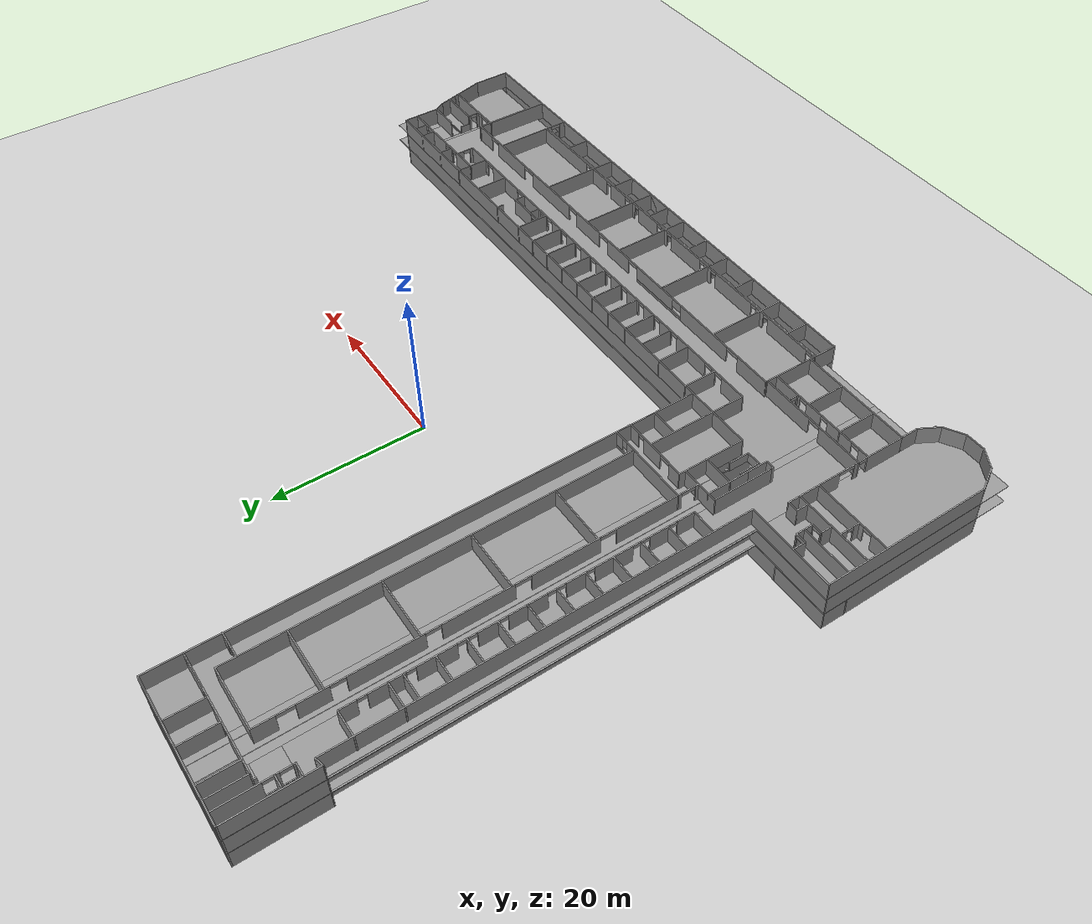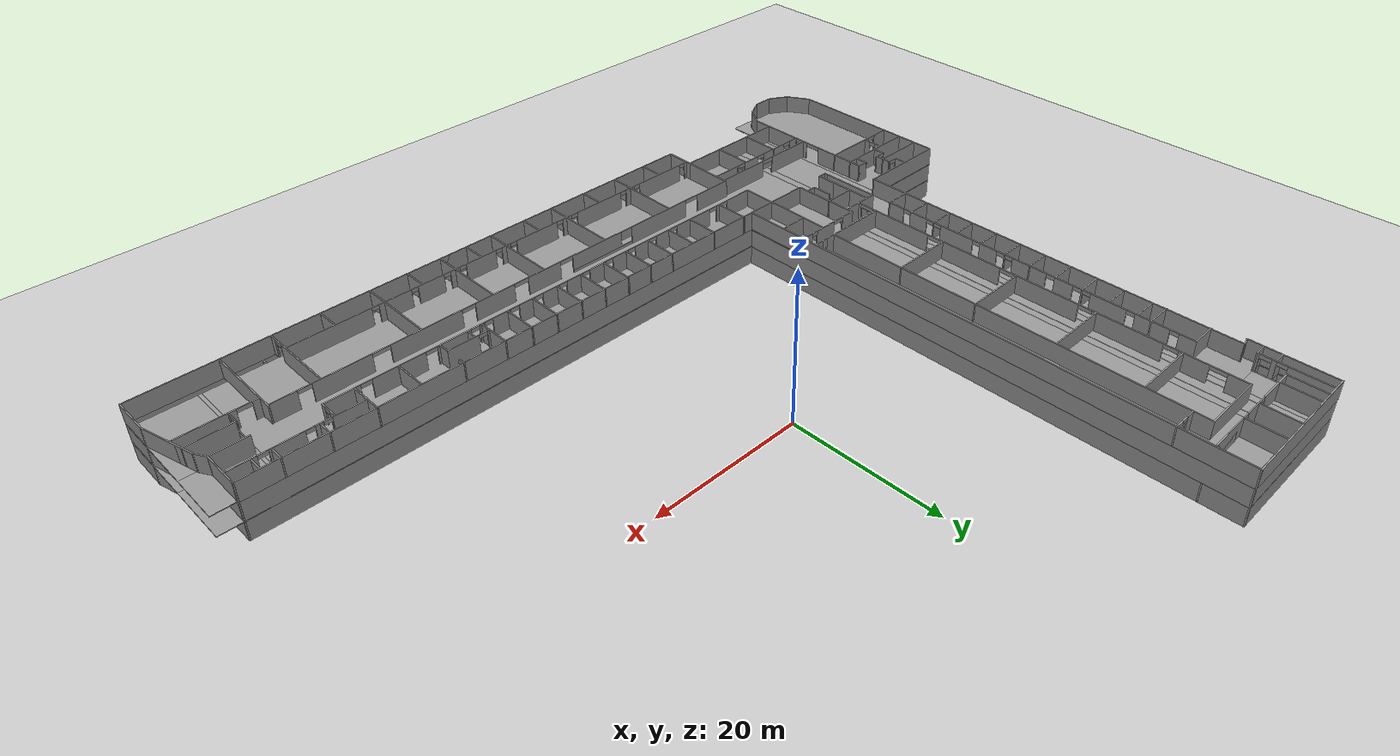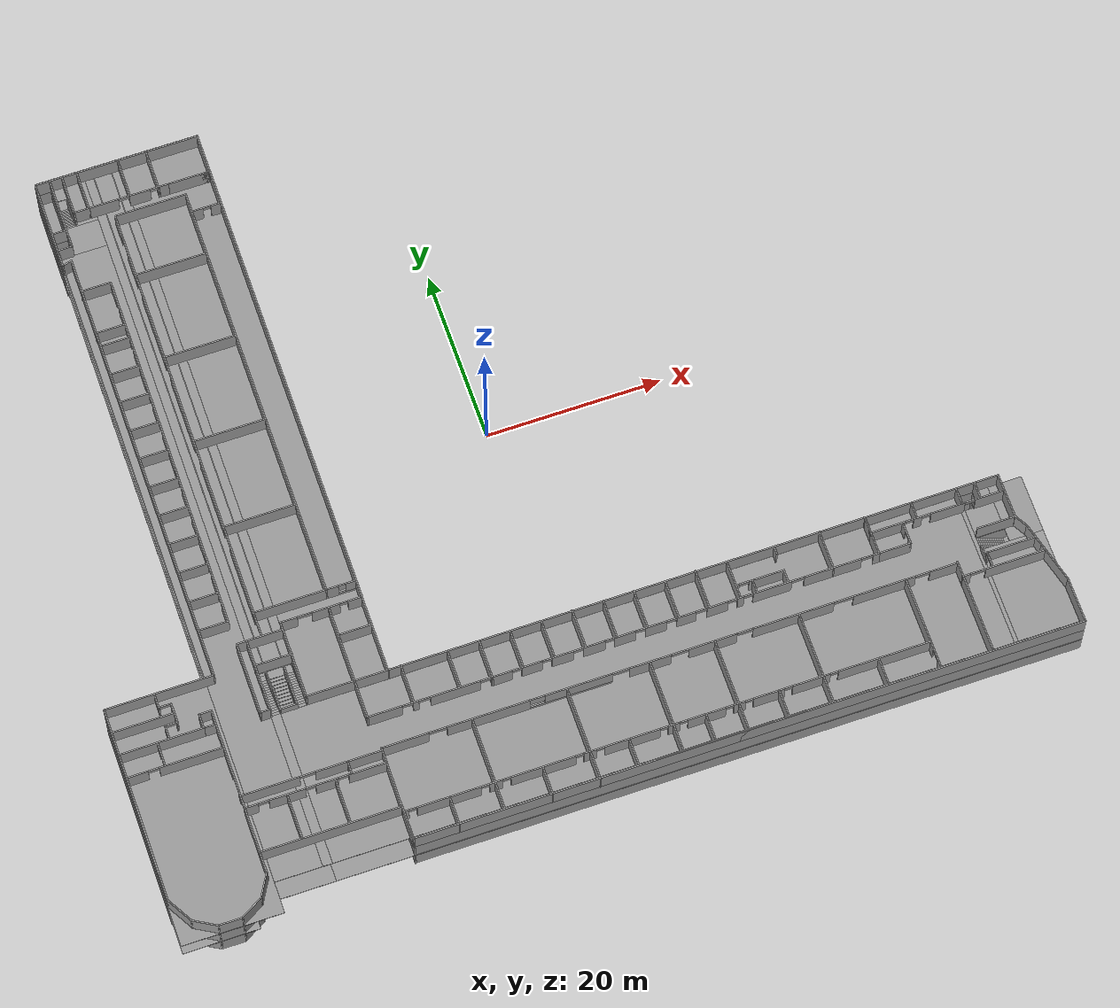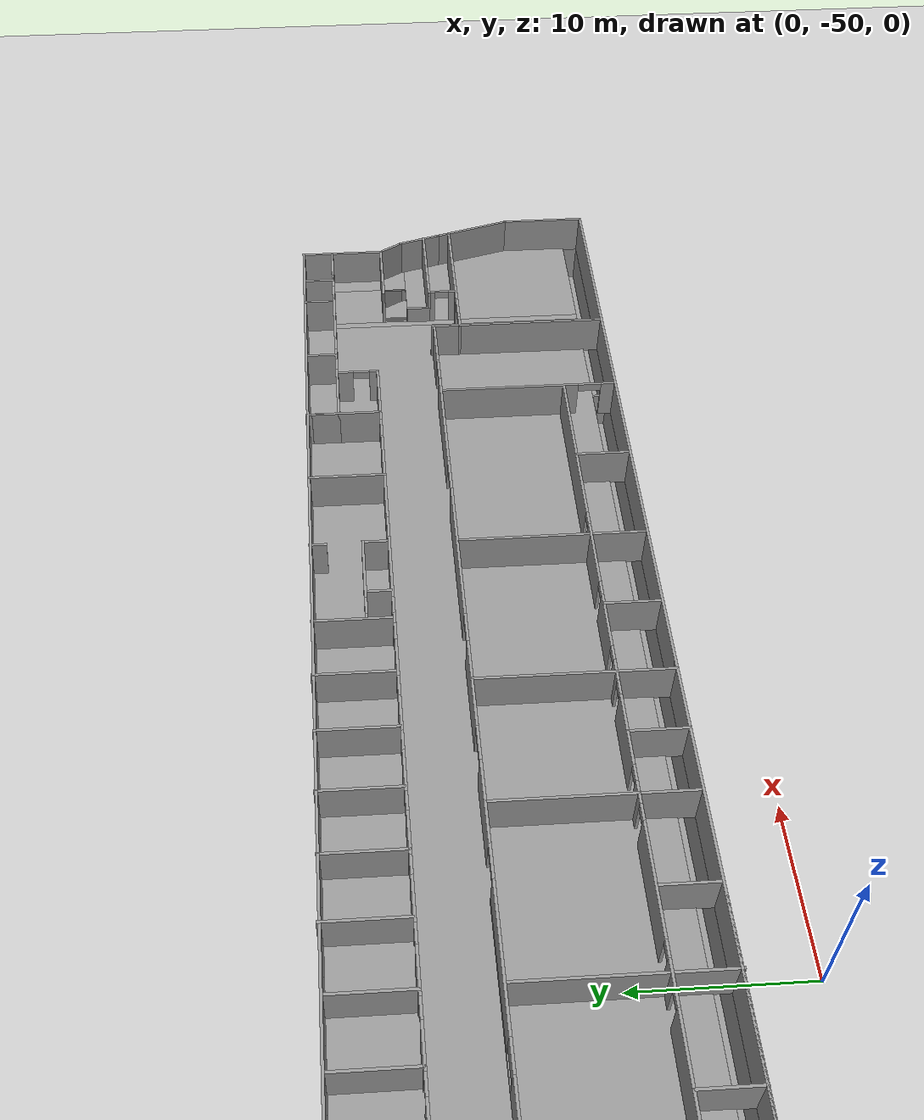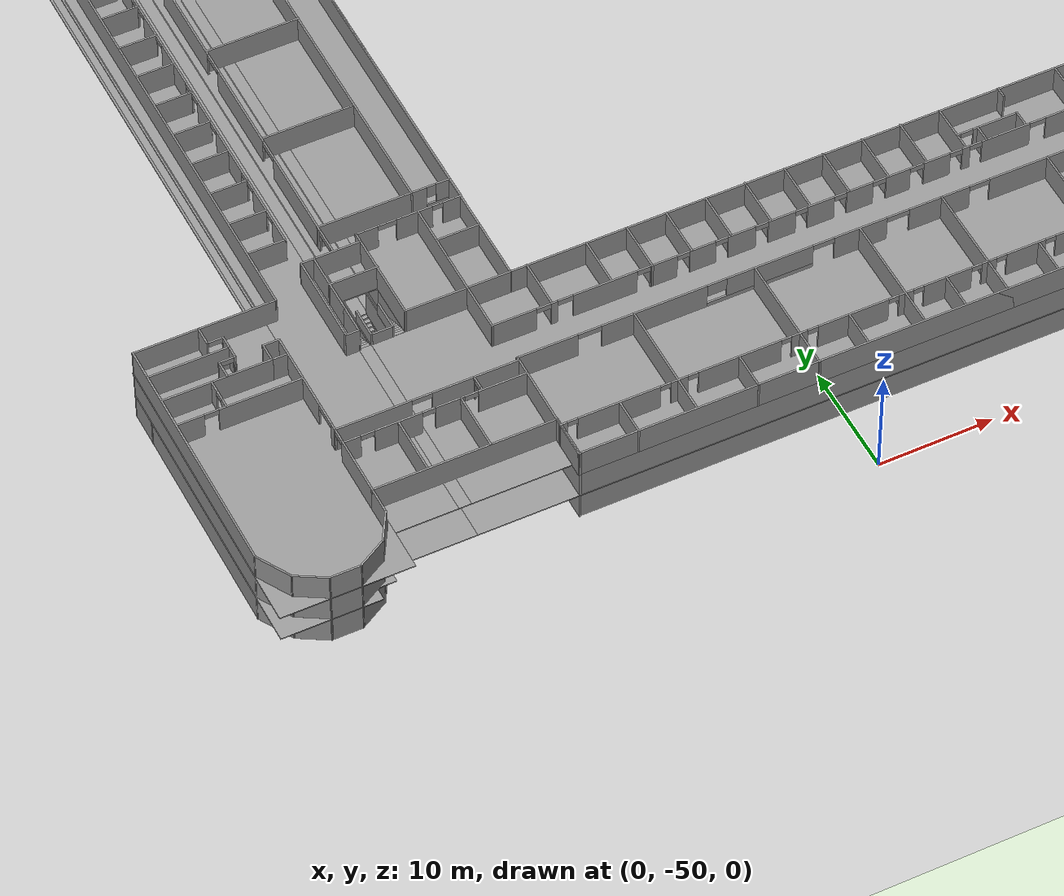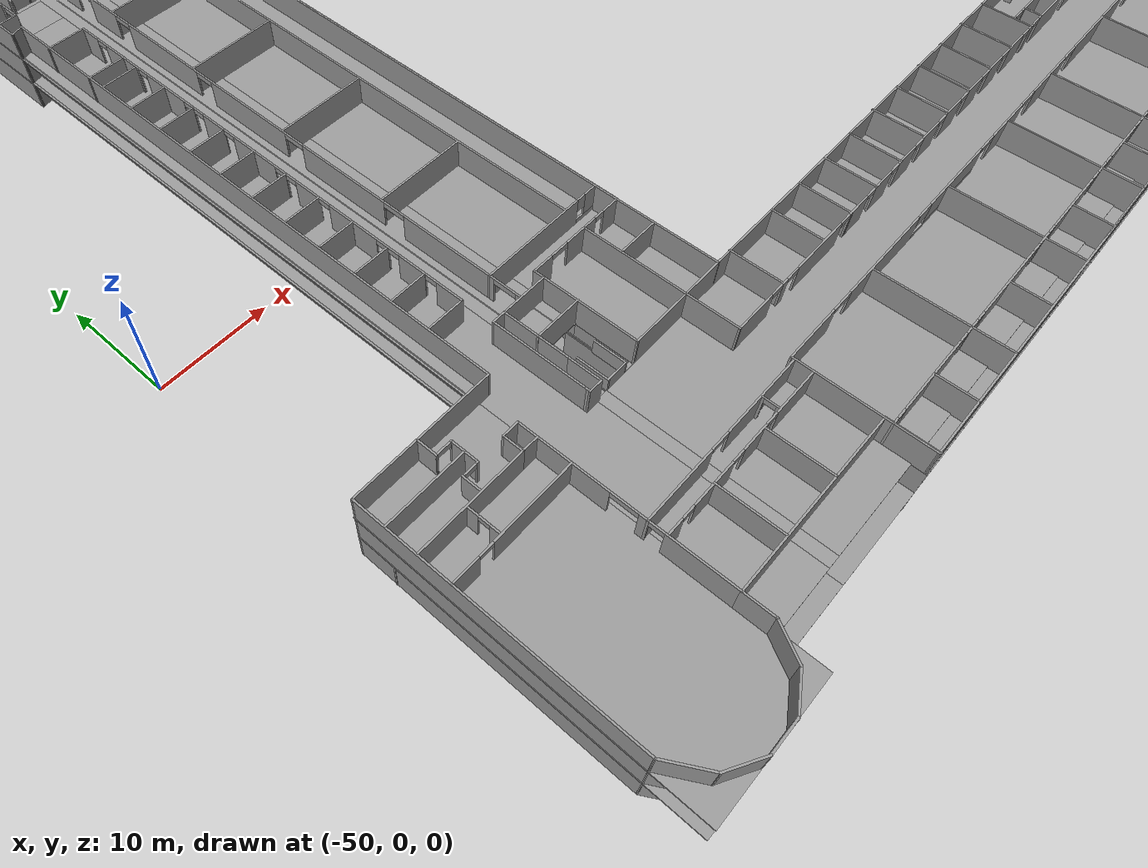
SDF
<sdf version="1.7">
 <world name="default">
  <light name="sun" type="directional">
   <pose>0 0 10 0 -0 0</pose>
   <diffuse>0.8 0.8 0.8 1</diffuse>
   <specular>0.2 0.2 0.2 1</specular>
   <attenuation>
    <range>1000</range>
    <constant>0.9</constant>
    <linear>0.01</linear>
    <quadratic>0.001</quadratic>
   </attenuation>
   <direction>-0.5 0.1 -0.9</direction>
   <spot><inner_angle>0</inner_angle><outer_angle>0</outer_angle><falloff>0</falloff></spot>
  </light>
  <model name="ground_plane">
   <static>1</static>
   <link name="link">
    <collision name="collision">
     <geometry><plane><normal>0 0 1</normal><size>100 100</size></plane></geometry>
     <surface><friction><ode><mu>100</mu><mu2>50</mu2></ode></friction></surface>
    </collision>
    <visual name="visual">
     <cast_shadows>0</cast_shadows>
     <geometry><plane><normal>0 0 1</normal><size>100 100</size></plane></geometry>
     <material>
      <script><uri>file://media/materials/scripts/gazebo.material</uri><name>Gazebo/Grey</name></script>
     </material>
    </visual>
   </link>
  </model>
  <gravity>0 0 -9.8</gravity>
  <magnetic_field>6e-06 2.3e-05 -4.2e-05</magnetic_field>
  <atmosphere type="adiabatic"/>
  <physics type="ode">
   <max_step_size>0.001</max_step_size>
   <real_time_factor>1</real_time_factor>
   <real_time_update_rate>1000</real_time_update_rate>
  </physics>
  <scene><ambient>0.4 0.4 0.4 1</ambient><background>0.7 0.7 0.7 1</background><shadows>1</shadows></scene>
  <spherical_coordinates>
   <surface_model>EARTH_WGS84</surface_model>
   <latitude_deg>0</latitude_deg>
   <longitude_deg>0</longitude_deg>
   <elevation>0</elevation>
   <heading_deg>0</heading_deg>
  </spherical_coordinates>
  <model name="Anselm_Turmeda">
   <pose>-32.7988 -2.37459 0 0 -0 0</pose>
   <link name="Floor_0">
    <pose>34.1888 -0.281989 2.5 0 -0 0</pose>
    <visual name="Floor_0_Visual_0">
     <pose>-46.4179 -30.6951 0.05 0 -0 0</pose>
     <geometry><box><size>8.57416 26.8788 0.1</size></box></geometry>
     <material>
      <script><uri>file://media/materials/scripts/gazebo.material</uri><name>Gazebo/Grey</name></script>
      <ambient>1 1 1 1</ambient>
     </material>
     <meta><layer>1</layer></meta>
    </visual>
    <collision name="Floor_0_Collision_0">
     <geometry><box><size>8.57416 26.8788 0.1</size></box></geometry>
     <pose>-46.4179 -30.6951 0.05 0 -0 0</pose>
    </collision>
    <visual name="Floor_0_Visual_1">
     <pose>-41.3146 -30.1245 0.05 0 -0 0</pose>
     <geometry><box><size>1.63242 25.7376 0.1</size></box></geometry>
     <material>
      <script><uri>file://media/materials/scripts/gazebo.material</uri><name>Gazebo/Grey</name></script>
      <ambient>1 1 1 1</ambient>
     </material>
     <meta><layer>1</layer></meta>
    </visual>
    <collision name="Floor_0_Collision_1">
     <geometry><box><size>1.63242 25.7376 0.1</size></box></geometry>
     <pose>-41.3146 -30.1245 0.05 0 -0 0</pose>
    </collision>
    <visual name="Floor_0_Visual_2">
     <pose>-36.7863 -29.4872 0.05 0 -0 0</pose>
     <geometry><box><size>7.42416 24.4631 0.1</size></box></geometry>
     <material>
      <script><uri>file://media/materials/scripts/gazebo.material</uri><name>Gazebo/Grey</name></script>
      <ambient>1 1 1 1</ambient>
     </material>
     <meta><layer>1</layer></meta>
    </visual>
    <collision name="Floor_0_Collision_2">
     <geometry><box><size>7.42416 24.4631 0.1</size></box></geometry>
     <pose>-36.7863 -29.4872 0.05 0 -0 0</pose>
    </collision>
    <visual name="Floor_0_Visual_3">
     <pose>5.01954 -32.3325 0.05 0 -0 0</pose>
     <geometry><box><size>76.1876 18.7727 0.1</size></box></geometry>
     <material>
      <script><uri>file://media/materials/scripts/gazebo.material</uri><name>Gazebo/Grey</name></script>
      <ambient>1 1 1 1</ambient>
     </material>
     <meta><layer>1</layer></meta>
    </visual>
    <collision name="Floor_0_Collision_3">
     <geometry><box><size>76.1876 18.7727 0.1</size></box></geometry>
     <pose>5.01954 -32.3325 0.05 0 -0 0</pose>
    </collision>
    <visual name="Floor_0_Visual_4">
     <pose>43.3448 -33.1674 0.05 0 -0 0</pose>
     <geometry><box><size>0.46289 17.1028 0.1</size></box></geometry>
     <material>
      <script><uri>file://media/materials/scripts/gazebo.material</uri><name>Gazebo/Grey</name></script>
      <ambient>1 1 1 1</ambient>
     </material>
     <meta><layer>1</layer></meta>
    </visual>
    <collision name="Floor_0_Collision_4">
     <geometry><box><size>0.46289 17.1028 0.1</size></box></geometry>
     <pose>43.3448 -33.1674 0.05 0 -0 0</pose>
    </collision>
    <visual name="Floor_0_Visual_5">
     <pose>47.1406 -36.3459 0.05 0 -0 0</pose>
     <geometry><box><size>7.12878 10.7459 0.1</size></box></geometry>
     <material>
      <script><uri>file://media/materials/scripts/gazebo.material</uri><name>Gazebo/Grey</name></script>
      <ambient>1 1 1 1</ambient>
     </material>
     <meta><layer>1</layer></meta>
    </visual>
    <collision name="Floor_0_Collision_5">
     <geometry><box><size>7.12878 10.7459 0.1</size></box></geometry>
     <pose>47.1406 -36.3459 0.05 0 -0 0</pose>
    </collision>
    <visual name="Floor_0_Visual_6">
     <pose>48.7598 -26.8288 0.05 0 -0 0</pose>
     <geometry><box><size>3.89041 8.28829 0.1</size></box></geometry>
     <material>
      <script><uri>file://media/materials/scripts/gazebo.material</uri><name>Gazebo/Grey</name></script>
      <ambient>1 1 1 1</ambient>
     </material>
     <meta><layer>1</layer></meta>
    </visual>
    <collision name="Floor_0_Collision_6">
     <geometry><box><size>3.89041 8.28829 0.1</size></box></geometry>
     <pose>48.7598 -26.8288 0.05 0 -0 0</pose>
    </collision>
    <visual name="Floor_0_Visual_7">
     <pose>45.1954 -27.0574 0.05 0 -0 0</pose>
     <geometry><box><size>3.23837 4.88274 0.1</size></box></geometry>
     <material>
      <script><uri>file://media/materials/scripts/gazebo.material</uri><name>Gazebo/Grey</name></script>
      <ambient>1 1 1 1</ambient>
     </material>
     <meta><layer>1</layer></meta>
    </visual>
    <collision name="Floor_0_Collision_7">
     <geometry><box><size>3.23837 4.88274 0.1</size></box></geometry>
     <pose>45.1954 -27.0574 0.05 0 -0 0</pose>
    </collision>
    <visual name="Floor_0_Visual_8">
     <pose>45.9845 -23.6503 0.05 0 -0 0</pose>
     <geometry><box><size>1.66026 1.93134 0.1</size></box></geometry>
     <material>
      <script><uri>file://media/materials/scripts/gazebo.material</uri><name>Gazebo/Grey</name></script>
      <ambient>1 1 1 1</ambient>
     </material>
     <meta><layer>1</layer></meta>
    </visual>
    <collision name="Floor_0_Collision_8">
     <geometry><box><size>1.66026 1.93134 0.1</size></box></geometry>
     <pose>45.9845 -23.6503 0.05 0 -0 0</pose>
    </collision>
    <visual name="Floor_0_Visual_9">
     <pose>-25.9523 10.5942 0.05 0 -0 0</pose>
     <geometry><box><size>10.1181 67.0806 0.1</size></box></geometry>
     <material>
      <script><uri>file://media/materials/scripts/gazebo.material</uri><name>Gazebo/Grey</name></script>
      <ambient>1 1 1 1</ambient>
     </material>
     <meta><layer>1</layer></meta>
    </visual>
    <collision name="Floor_0_Collision_9">
     <geometry><box><size>10.1181 67.0806 0.1</size></box></geometry>
     <pose>-25.9523 10.5942 0.05 0 -0 0</pose>
    </collision>
    <visual name="Floor_0_Visual_10">
     <pose>11.11 -22.8154 0.05 0 -0 0</pose>
     <geometry><box><size>64.0066 0.261495 0.1</size></box></geometry>
     <material>
      <script><uri>file://media/materials/scripts/gazebo.material</uri><name>Gazebo/Grey</name></script>
      <ambient>1 1 1 1</ambient>
     </material>
     <meta><layer>1</layer></meta>
    </visual>
    <collision name="Floor_0_Collision_10">
     <geometry><box><size>64.0066 0.261495 0.1</size></box></geometry>
     <pose>11.11 -22.8154 0.05 0 -0 0</pose>
    </collision>
    <visual name="Floor_0_Visual_11">
     <pose>43.1133 -22.7743 0.05 0 -0 0</pose>
     <geometry><box><size>0 0.179344 0.1</size></box></geometry>
     <material>
      <script><uri>file://media/materials/scripts/gazebo.material</uri><name>Gazebo/Grey</name></script>
      <ambient>1 1 1 1</ambient>
     </material>
     <meta><layer>1</layer></meta>
    </visual>
    <collision name="Floor_0_Collision_11">
     <geometry><box><size>0 0.179344 0.1</size></box></geometry>
     <pose>43.1133 -22.7743 0.05 0 -0 0</pose>
    </collision>
    <visual name="Floor_0_Visual_12">
     <pose>-32.0428 13.1372 0.05 0 -0 0</pose>
     <geometry><box><size>2.06288 61.9945 0.1</size></box></geometry>
     <material>
      <script><uri>file://media/materials/scripts/gazebo.material</uri><name>Gazebo/Grey</name></script>
      <ambient>1 1 1 1</ambient>
     </material>
     <meta><layer>1</layer></meta>
    </visual>
    <collision name="Floor_0_Collision_12">
     <geometry><box><size>2.06288 61.9945 0.1</size></box></geometry>
     <pose>-32.0428 13.1372 0.05 0 -0 0</pose>
    </collision>
    <visual name="Floor_0_Visual_13">
     <pose>-39.5613 13.4394 0.05 0 -0 0</pose>
     <geometry><box><size>0.189446 61.3901 0.1</size></box></geometry>
     <material>
      <script><uri>file://media/materials/scripts/gazebo.material</uri><name>Gazebo/Grey</name></script>
      <ambient>1 1 1 1</ambient>
     </material>
     <meta><layer>1</layer></meta>
    </visual>
    <collision name="Floor_0_Collision_13">
     <geometry><box><size>0.189446 61.3901 0.1</size></box></geometry>
     <pose>-39.5613 13.4394 0.05 0 -0 0</pose>
    </collision>
    <visual name="Floor_0_Visual_14">
     <pose>-36.2704 9.2133 0.05 0 -0 0</pose>
     <geometry><box><size>6.39228 52.938 0.1</size></box></geometry>
     <material>
      <script><uri>file://media/materials/scripts/gazebo.material</uri><name>Gazebo/Grey</name></script>
      <ambient>1 1 1 1</ambient>
     </material>
     <meta><layer>1</layer></meta>
    </visual>
    <collision name="Floor_0_Collision_14">
     <geometry><box><size>6.39228 52.938 0.1</size></box></geometry>
     <pose>-36.2704 9.2133 0.05 0 -0 0</pose>
    </collision>
    <visual name="Floor_0_Visual_15">
     <pose>-37.2668 39.9084 0.05 0 -0 0</pose>
     <geometry><box><size>1.37349 8.45218 0.1</size></box></geometry>
     <material>
      <script><uri>file://media/materials/scripts/gazebo.material</uri><name>Gazebo/Grey</name></script>
      <ambient>1 1 1 1</ambient>
     </material>
     <meta><layer>1</layer></meta>
    </visual>
    <collision name="Floor_0_Collision_15">
     <geometry><box><size>1.37349 8.45218 0.1</size></box></geometry>
     <pose>-37.2668 39.9084 0.05 0 -0 0</pose>
    </collision>
    <visual name="Floor_0_Visual_16">
     <pose>-34.8271 37.3501 0.05 0 -0 0</pose>
     <geometry><box><size>3.50579 3.33567 0.1</size></box></geometry>
     <material>
      <script><uri>file://media/materials/scripts/gazebo.material</uri><name>Gazebo/Grey</name></script>
      <ambient>1 1 1 1</ambient>
     </material>
     <meta><layer>1</layer></meta>
    </visual>
    <collision name="Floor_0_Collision_16">
     <geometry><box><size>3.50579 3.33567 0.1</size></box></geometry>
     <pose>-34.8271 37.3501 0.05 0 -0 0</pose>
    </collision>
    <visual name="Floor_0_Visual_17">
     <pose>-38.71 40.8994 0.05 0 -0 0</pose>
     <geometry><box><size>1.513 6.47018 0.1</size></box></geometry>
     <material>
      <script><uri>file://media/materials/scripts/gazebo.material</uri><name>Gazebo/Grey</name></script>
      <ambient>1 1 1 1</ambient>
     </material>
     <meta><layer>1</layer></meta>
    </visual>
    <collision name="Floor_0_Collision_17">
     <geometry><box><size>1.513 6.47018 0.1</size></box></geometry>
     <pose>-38.71 40.8994 0.05 0 -0 0</pose>
    </collision>
    <visual name="Floor_0_Visual_18">
     <pose>-34.1989 41.5762 0.05 0 -0 0</pose>
     <geometry><box><size>2.2492 5.11651 0.1</size></box></geometry>
     <material>
      <script><uri>file://media/materials/scripts/gazebo.material</uri><name>Gazebo/Grey</name></script>
      <ambient>1 1 1 1</ambient>
     </material>
     <meta><layer>1</layer></meta>
    </visual>
    <collision name="Floor_0_Collision_18">
     <geometry><box><size>2.2492 5.11651 0.1</size></box></geometry>
     <pose>-34.1989 41.5762 0.05 0 -0 0</pose>
    </collision>
    <visual name="Floor_0_Visual_19">
     <pose>-35.9518 43.3262 0.05 0 -0 0</pose>
     <geometry><box><size>1.25659 1.61651 0.1</size></box></geometry>
     <material>
      <script><uri>file://media/materials/scripts/gazebo.material</uri><name>Gazebo/Grey</name></script>
      <ambient>1 1 1 1</ambient>
     </material>
     <meta><layer>1</layer></meta>
    </visual>
    <collision name="Floor_0_Collision_19">
     <geometry><box><size>1.25659 1.61651 0.1</size></box></geometry>
     <pose>-35.9518 43.3262 0.05 0 -0 0</pose>
    </collision>
   </link>
   <link name="Floor_1">
    <pose>34.1888 -0.261702 5 0 -0 0</pose>
    <visual name="Floor_1_Visual_0">
     <pose>-45.0604 -30.6956 0.05 0 -0 0</pose>
     <geometry><box><size>11.2893 26.9183 0.1</size></box></geometry>
     <material>
      <script><uri>file://media/materials/scripts/gazebo.material</uri><name>Gazebo/Grey</name></script>
      <ambient>1 1 1 1</ambient>
     </material>
     <meta><layer>2</layer></meta>
    </visual>
    <collision name="Floor_1_Collision_0">
     <geometry><box><size>11.2893 26.9183 0.1</size></box></geometry>
     <pose>-45.0604 -30.6956 0.05 0 -0 0</pose>
    </collision>
    <visual name="Floor_1_Visual_1">
     <pose>-36.7543 -2.46547 0.05 0 -0 0</pose>
     <geometry><box><size>5.32296 76.2977 0.1</size></box></geometry>
     <material>
      <script><uri>file://media/materials/scripts/gazebo.material</uri><name>Gazebo/Grey</name></script>
      <ambient>1 1 1 1</ambient>
     </material>
     <meta><layer>2</layer></meta>
    </visual>
    <collision name="Floor_1_Collision_1">
     <geometry><box><size>5.32296 76.2977 0.1</size></box></geometry>
     <pose>-36.7543 -2.46547 0.05 0 -0 0</pose>
    </collision>
    <visual name="Floor_1_Visual_2">
     <pose>-33.5567 -31.7526 0.05 0 -0 0</pose>
     <geometry><box><size>1.07211 17.7234 0.1</size></box></geometry>
     <material>
      <script><uri>file://media/materials/scripts/gazebo.material</uri><name>Gazebo/Grey</name></script>
      <ambient>1 1 1 1</ambient>
     </material>
     <meta><layer>2</layer></meta>
    </visual>
    <collision name="Floor_1_Collision_2">
     <geometry><box><size>1.07211 17.7234 0.1</size></box></geometry>
     <pose>-33.5567 -31.7526 0.05 0 -0 0</pose>
    </collision>
    <visual name="Floor_1_Visual_3">
     <pose>5.05568 -31.7614 0.05 0 -0 0</pose>
     <geometry><box><size>76.1527 17.7058 0.1</size></box></geometry>
     <material>
      <script><uri>file://media/materials/scripts/gazebo.material</uri><name>Gazebo/Grey</name></script>
      <ambient>1 1 1 1</ambient>
     </material>
     <meta><layer>2</layer></meta>
    </visual>
    <collision name="Floor_1_Collision_3">
     <geometry><box><size>76.1527 17.7058 0.1</size></box></geometry>
     <pose>5.05568 -31.7614 0.05 0 -0 0</pose>
    </collision>
    <visual name="Floor_1_Visual_4">
     <pose>43.3516 -32.6347 0.05 0 -0 0</pose>
     <geometry><box><size>0.439225 15.9593 0.1</size></box></geometry>
     <material>
      <script><uri>file://media/materials/scripts/gazebo.material</uri><name>Gazebo/Grey</name></script>
      <ambient>1 1 1 1</ambient>
     </material>
     <meta><layer>2</layer></meta>
    </visual>
    <collision name="Floor_1_Collision_4">
     <geometry><box><size>0.439225 15.9593 0.1</size></box></geometry>
     <pose>43.3516 -32.6347 0.05 0 -0 0</pose>
    </collision>
    <visual name="Floor_1_Visual_5">
     <pose>47.1381 -35.048 0.05 0 -0 0</pose>
     <geometry><box><size>7.13374 11.1326 0.1</size></box></geometry>
     <material>
      <script><uri>file://media/materials/scripts/gazebo.material</uri><name>Gazebo/Grey</name></script>
      <ambient>1 1 1 1</ambient>
     </material>
     <meta><layer>2</layer></meta>
    </visual>
    <collision name="Floor_1_Collision_5">
     <geometry><box><size>7.13374 11.1326 0.1</size></box></geometry>
     <pose>47.1381 -35.048 0.05 0 -0 0</pose>
    </collision>
    <visual name="Floor_1_Visual_6">
     <pose>48.7681 -26.1772 0.05 0 -0 0</pose>
     <geometry><box><size>3.87375 6.6092 0.1</size></box></geometry>
     <material>
      <script><uri>file://media/materials/scripts/gazebo.material</uri><name>Gazebo/Grey</name></script>
      <ambient>1 1 1 1</ambient>
     </material>
     <meta><layer>2</layer></meta>
    </visual>
    <collision name="Floor_1_Collision_6">
     <geometry><box><size>3.87375 6.6092 0.1</size></box></geometry>
     <pose>48.7681 -26.1772 0.05 0 -0 0</pose>
    </collision>
    <visual name="Floor_1_Visual_7">
     <pose>45.2013 -26.3263 0.05 0 -0 0</pose>
     <geometry><box><size>3.25999 3.34256 0.1</size></box></geometry>
     <material>
      <script><uri>file://media/materials/scripts/gazebo.material</uri><name>Gazebo/Grey</name></script>
      <ambient>1 1 1 1</ambient>
     </material>
     <meta><layer>2</layer></meta>
    </visual>
    <collision name="Floor_1_Collision_7">
     <geometry><box><size>3.25999 3.34256 0.1</size></box></geometry>
     <pose>45.2013 -26.3263 0.05 0 -0 0</pose>
    </collision>
    <visual name="Floor_1_Visual_8">
     <pose>45.9741 -23.7638 0.05 0 -0 0</pose>
     <geometry><box><size>1.71422 1.78242 0.1</size></box></geometry>
     <material>
      <script><uri>file://media/materials/scripts/gazebo.material</uri><name>Gazebo/Grey</name></script>
      <ambient>1 1 1 1</ambient>
     </material>
     <meta><layer>2</layer></meta>
    </visual>
    <collision name="Floor_1_Collision_8">
     <geometry><box><size>1.71422 1.78242 0.1</size></box></geometry>
     <pose>45.9741 -23.7638 0.05 0 -0 0</pose>
    </collision>
    <visual name="Floor_1_Visual_9">
     <pose>-31.0167 10.6231 0.05 0 -0 0</pose>
     <geometry><box><size>0.0592 67.0632 0.1</size></box></geometry>
     <material>
      <script><uri>file://media/materials/scripts/gazebo.material</uri><name>Gazebo/Grey</name></script>
      <ambient>1 1 1 1</ambient>
     </material>
     <meta><layer>2</layer></meta>
    </visual>
    <collision name="Floor_1_Collision_9">
     <geometry><box><size>0.0592 67.0632 0.1</size></box></geometry>
     <pose>-31.0167 10.6231 0.05 0 -0 0</pose>
    </collision>
    <visual name="Floor_1_Visual_10">
     <pose>-25.9239 -22.8903 0.05 0 -0 0</pose>
     <geometry><box><size>10.1262 0.036364 0.1</size></box></geometry>
     <material>
      <script><uri>file://media/materials/scripts/gazebo.material</uri><name>Gazebo/Grey</name></script>
      <ambient>1 1 1 1</ambient>
     </material>
     <meta><layer>2</layer></meta>
    </visual>
    <collision name="Floor_1_Collision_10">
     <geometry><box><size>10.1262 0.036364 0.1</size></box></geometry>
     <pose>-25.9239 -22.8903 0.05 0 -0 0</pose>
    </collision>
    <visual name="Floor_1_Visual_11">
     <pose>11.1356 -22.8905 0.05 0 -0 0</pose>
     <geometry><box><size>63.9929 0.035911 0.1</size></box></geometry>
     <material>
      <script><uri>file://media/materials/scripts/gazebo.material</uri><name>Gazebo/Grey</name></script>
      <ambient>1 1 1 1</ambient>
     </material>
     <meta><layer>2</layer></meta>
    </visual>
    <collision name="Floor_1_Collision_11">
     <geometry><box><size>63.9929 0.035911 0.1</size></box></geometry>
     <pose>11.1356 -22.8905 0.05 0 -0 0</pose>
    </collision>
    <visual name="Floor_1_Visual_12">
     <pose>-33.0567 10.6319 0.05 0 -0 0</pose>
     <geometry><box><size>0.072115 67.0457 0.1</size></box></geometry>
     <material>
      <script><uri>file://media/materials/scripts/gazebo.material</uri><name>Gazebo/Grey</name></script>
      <ambient>1 1 1 1</ambient>
     </material>
     <meta><layer>2</layer></meta>
    </visual>
    <collision name="Floor_1_Collision_12">
     <geometry><box><size>0.072115 67.0457 0.1</size></box></geometry>
     <pose>-33.0567 10.6319 0.05 0 -0 0</pose>
    </collision>
    <visual name="Floor_1_Visual_13">
     <pose>-25.4239 10.6413 0.05 0 -0 0</pose>
     <geometry><box><size>9.12623 67.0269 0.1</size></box></geometry>
     <material>
      <script><uri>file://media/materials/scripts/gazebo.material</uri><name>Gazebo/Grey</name></script>
      <ambient>1 1 1 1</ambient>
     </material>
     <meta><layer>2</layer></meta>
    </visual>
    <collision name="Floor_1_Collision_13">
     <geometry><box><size>9.12623 67.0269 0.1</size></box></geometry>
     <pose>-25.4239 10.6413 0.05 0 -0 0</pose>
    </collision>
    <visual name="Floor_1_Visual_14">
     <pose>-25.4239 10.6413 0.05 0 -0 0</pose>
     <geometry><box><size>9.12623 67.0269 0.1</size></box></geometry>
     <material>
      <script><uri>file://media/materials/scripts/gazebo.material</uri><name>Gazebo/Grey</name></script>
      <ambient>1 1 1 1</ambient>
     </material>
     <meta><layer>2</layer></meta>
    </visual>
    <collision name="Floor_1_Collision_14">
     <geometry><box><size>9.12623 67.0269 0.1</size></box></geometry>
     <pose>-25.4239 10.6413 0.05 0 -0 0</pose>
    </collision>
    <visual name="Floor_1_Visual_15">
     <pose>-33.5928 13.1341 0.05 0 -0 0</pose>
     <geometry><box><size>1 62.0413 0.1</size></box></geometry>
     <material>
      <script><uri>file://media/materials/scripts/gazebo.material</uri><name>Gazebo/Grey</name></script>
      <ambient>1 1 1 1</ambient>
     </material>
     <meta><layer>2</layer></meta>
    </visual>
    <collision name="Floor_1_Collision_15">
     <geometry><box><size>1 62.0413 0.1</size></box></geometry>
     <pose>-33.5928 13.1341 0.05 0 -0 0</pose>
    </collision>
    <visual name="Floor_1_Visual_16">
     <pose>-30.4871 13.1341 0.05 0 -0 0</pose>
     <geometry><box><size>1 62.0413 0.1</size></box></geometry>
     <material>
      <script><uri>file://media/materials/scripts/gazebo.material</uri><name>Gazebo/Grey</name></script>
      <ambient>1 1 1 1</ambient>
     </material>
     <meta><layer>2</layer></meta>
    </visual>
    <collision name="Floor_1_Collision_16">
     <geometry><box><size>1 62.0413 0.1</size></box></geometry>
     <pose>-30.4871 13.1341 0.05 0 -0 0</pose>
    </collision>
    <visual name="Floor_1_Visual_17">
     <pose>-32.0335 13.1399 0.05 0 -0 0</pose>
     <geometry><box><size>1.97442 62.0298 0.1</size></box></geometry>
     <material>
      <script><uri>file://media/materials/scripts/gazebo.material</uri><name>Gazebo/Grey</name></script>
      <ambient>1 1 1 1</ambient>
     </material>
     <meta><layer>2</layer></meta>
    </visual>
    <collision name="Floor_1_Collision_17">
     <geometry><box><size>1.97442 62.0298 0.1</size></box></geometry>
     <pose>-32.0335 13.1399 0.05 0 -0 0</pose>
    </collision>
    <visual name="Floor_1_Visual_18">
     <pose>-39.5689 13.4591 0.05 0 -0 0</pose>
     <geometry><box><size>0.16128 61.3912 0.1</size></box></geometry>
     <material>
      <script><uri>file://media/materials/scripts/gazebo.material</uri><name>Gazebo/Grey</name></script>
      <ambient>1 1 1 1</ambient>
     </material>
     <meta><layer>2</layer></meta>
    </visual>
    <collision name="Floor_1_Collision_18">
     <geometry><box><size>0.16128 61.3912 0.1</size></box></geometry>
     <pose>-39.5689 13.4591 0.05 0 -0 0</pose>
    </collision>
    <visual name="Floor_1_Visual_19">
     <pose>-39.452 9.22345 0.05 0 -0 0</pose>
     <geometry><box><size>0.072485 52.9199 0.1</size></box></geometry>
     <material>
      <script><uri>file://media/materials/scripts/gazebo.material</uri><name>Gazebo/Grey</name></script>
      <ambient>1 1 1 1</ambient>
     </material>
     <meta><layer>2</layer></meta>
    </visual>
    <collision name="Floor_1_Collision_19">
     <geometry><box><size>0.072485 52.9199 0.1</size></box></geometry>
     <pose>-39.452 9.22345 0.05 0 -0 0</pose>
    </collision>
    <visual name="Floor_1_Visual_20">
     <pose>-37.8974 39.9191 0.05 0 -0 0</pose>
     <geometry><box><size>0.111645 8.47137 0.1</size></box></geometry>
     <material>
      <script><uri>file://media/materials/scripts/gazebo.material</uri><name>Gazebo/Grey</name></script>
      <ambient>1 1 1 1</ambient>
     </material>
     <meta><layer>2</layer></meta>
    </visual>
    <collision name="Floor_1_Collision_20">
     <geometry><box><size>0.111645 8.47137 0.1</size></box></geometry>
     <pose>-37.8974 39.9191 0.05 0 -0 0</pose>
    </collision>
    <visual name="Floor_1_Visual_21">
     <pose>-35.9672 37.3405 0.05 0 -0 0</pose>
     <geometry><box><size>3.7488 3.31428 0.1</size></box></geometry>
     <material>
      <script><uri>file://media/materials/scripts/gazebo.material</uri><name>Gazebo/Grey</name></script>
      <ambient>1 1 1 1</ambient>
     </material>
     <meta><layer>2</layer></meta>
    </visual>
    <collision name="Floor_1_Collision_21">
     <geometry><box><size>3.7488 3.31428 0.1</size></box></geometry>
     <pose>-35.9672 37.3405 0.05 0 -0 0</pose>
    </collision>
    <visual name="Floor_1_Visual_22">
     <pose>-39.452 40.9101 0.05 0 -0 0</pose>
     <geometry><box><size>0.072485 6.48937 0.1</size></box></geometry>
     <material>
      <script><uri>file://media/materials/scripts/gazebo.material</uri><name>Gazebo/Grey</name></script>
      <ambient>1 1 1 1</ambient>
     </material>
     <meta><layer>2</layer></meta>
    </visual>
    <collision name="Floor_1_Collision_22">
     <geometry><box><size>0.072485 6.48937 0.1</size></box></geometry>
     <pose>-39.452 40.9101 0.05 0 -0 0</pose>
    </collision>
    <visual name="Floor_1_Visual_23">
     <pose>-35.3496 41.5762 0.05 0 -0 0</pose>
     <geometry><box><size>2.5136 5.15709 0.1</size></box></geometry>
     <material>
      <script><uri>file://media/materials/scripts/gazebo.material</uri><name>Gazebo/Grey</name></script>
      <ambient>1 1 1 1</ambient>
     </material>
     <meta><layer>2</layer></meta>
    </visual>
    <collision name="Floor_1_Collision_23">
     <geometry><box><size>2.5136 5.15709 0.1</size></box></geometry>
     <pose>-35.3496 41.5762 0.05 0 -0 0</pose>
    </collision>
    <visual name="Floor_1_Visual_24">
     <pose>-37.224 43.3369 0.05 0 -0 0</pose>
     <geometry><box><size>1.2352 1.6357 0.1</size></box></geometry>
     <material>
      <script><uri>file://media/materials/scripts/gazebo.material</uri><name>Gazebo/Grey</name></script>
      <ambient>1 1 1 1</ambient>
     </material>
     <meta><layer>2</layer></meta>
    </visual>
    <collision name="Floor_1_Collision_24">
     <geometry><box><size>1.2352 1.6357 0.1</size></box></geometry>
     <pose>-37.224 43.3369 0.05 0 -0 0</pose>
    </collision>
   </link>
   <link name="Stairs_1">
    <visual name="Stairs_1_Visual_0">
     <pose>77.8729 -30.5178 0.083333 0 -0 1.5708</pose>
     <geometry><box><size>1.47421 0.215891 0.166667</size></box></geometry>
     <material>
      <script><uri>file://media/materials/scripts/gazebo.material</uri><name>Gazebo/Grey</name></script>
      <ambient>1 1 1 1</ambient>
     </material>
     <meta><layer>0</layer></meta>
    </visual>
    <collision name="Stairs_1_Collision_0">
     <geometry><box><size>1.47421 0.215891 0.166667</size></box></geometry>
     <pose>77.8729 -30.5178 0.083333 0 -0 1.5708</pose>
    </collision>
    <visual name="Stairs_1_Visual_1">
     <pose>78.0888 -30.5178 0.25 0 -0 1.5708</pose>
     <geometry><box><size>1.47421 0.215891 0.166667</size></box></geometry>
     <material>
      <script><uri>file://media/materials/scripts/gazebo.material</uri><name>Gazebo/Grey</name></script>
      <ambient>1 1 1 1</ambient>
     </material>
     <meta><layer>0</layer></meta>
    </visual>
    <collision name="Stairs_1_Collision_1">
     <geometry><box><size>1.47421 0.215891 0.166667</size></box></geometry>
     <pose>78.0888 -30.5178 0.25 0 -0 1.5708</pose>
    </collision>
    <visual name="Stairs_1_Visual_2">
     <pose>78.3047 -30.5178 0.416667 0 -0 1.5708</pose>
     <geometry><box><size>1.47421 0.215891 0.166667</size></box></geometry>
     <material>
      <script><uri>file://media/materials/scripts/gazebo.material</uri><name>Gazebo/Grey</name></script>
      <ambient>1 1 1 1</ambient>
     </material>
     <meta><layer>0</layer></meta>
    </visual>
    <collision name="Stairs_1_Collision_2">
     <geometry><box><size>1.47421 0.215891 0.166667</size></box></geometry>
     <pose>78.3047 -30.5178 0.416667 0 -0 1.5708</pose>
    </collision>
    <visual name="Stairs_1_Visual_3">
     <pose>78.5206 -30.5178 0.583333 0 -0 1.5708</pose>
     <geometry><box><size>1.47421 0.215891 0.166667</size></box></geometry>
     <material>
      <script><uri>file://media/materials/scripts/gazebo.material</uri><name>Gazebo/Grey</name></script>
      <ambient>1 1 1 1</ambient>
     </material>
     <meta><layer>0</layer></meta>
    </visual>
    <collision name="Stairs_1_Collision_3">
     <geometry><box><size>1.47421 0.215891 0.166667</size></box></geometry>
     <pose>78.5206 -30.5178 0.583333 0 -0 1.5708</pose>
    </collision>
    <visual name="Stairs_1_Visual_4">
     <pose>78.7365 -30.5178 0.75 0 -0 1.5708</pose>
     <geometry><box><size>1.47421 0.215891 0.166667</size></box></geometry>
     <material>
      <script><uri>file://media/materials/scripts/gazebo.material</uri><name>Gazebo/Grey</name></script>
      <ambient>1 1 1 1</ambient>
     </material>
     <meta><layer>0</layer></meta>
    </visual>
    <collision name="Stairs_1_Collision_4">
     <geometry><box><size>1.47421 0.215891 0.166667</size></box></geometry>
     <pose>78.7365 -30.5178 0.75 0 -0 1.5708</pose>
    </collision>
    <visual name="Stairs_1_Visual_5">
     <pose>78.9524 -30.5178 0.916667 0 -0 1.5708</pose>
     <geometry><box><size>1.47421 0.215891 0.166667</size></box></geometry>
     <material>
      <script><uri>file://media/materials/scripts/gazebo.material</uri><name>Gazebo/Grey</name></script>
      <ambient>1 1 1 1</ambient>
     </material>
     <meta><layer>0</layer></meta>
    </visual>
    <collision name="Stairs_1_Collision_5">
     <geometry><box><size>1.47421 0.215891 0.166667</size></box></geometry>
     <pose>78.9524 -30.5178 0.916667 0 -0 1.5708</pose>
    </collision>
    <visual name="Stairs_1_Visual_6">
     <pose>79.1683 -30.5178 1.08333 0 -0 1.5708</pose>
     <geometry><box><size>1.47421 0.215891 0.166667</size></box></geometry>
     <material>
      <script><uri>file://media/materials/scripts/gazebo.material</uri><name>Gazebo/Grey</name></script>
      <ambient>1 1 1 1</ambient>
     </material>
     <meta><layer>0</layer></meta>
    </visual>
    <collision name="Stairs_1_Collision_6">
     <geometry><box><size>1.47421 0.215891 0.166667</size></box></geometry>
     <pose>79.1683 -30.5178 1.08333 0 -0 1.5708</pose>
    </collision>
    <visual name="Stairs_1_Visual_7">
     <pose>79.3842 -30.5178 1.25 0 -0 1.5708</pose>
     <geometry><box><size>1.47421 0.215891 0.166667</size></box></geometry>
     <material>
      <script><uri>file://media/materials/scripts/gazebo.material</uri><name>Gazebo/Grey</name></script>
      <ambient>1 1 1 1</ambient>
     </material>
     <meta><layer>0</layer></meta>
    </visual>
    <collision name="Stairs_1_Collision_7">
     <geometry><box><size>1.47421 0.215891 0.166667</size></box></geometry>
     <pose>79.3842 -30.5178 1.25 0 -0 1.5708</pose>
    </collision>
    <visual name="Stairs_1_Visual_8">
     <pose>79.6001 -30.5178 1.41667 0 -0 1.5708</pose>
     <geometry><box><size>1.47421 0.215891 0.166667</size></box></geometry>
     <material>
      <script><uri>file://media/materials/scripts/gazebo.material</uri><name>Gazebo/Grey</name></script>
      <ambient>1 1 1 1</ambient>
     </material>
     <meta><layer>0</layer></meta>
    </visual>
    <collision name="Stairs_1_Collision_8">
     <geometry><box><size>1.47421 0.215891 0.166667</size></box></geometry>
     <pose>79.6001 -30.5178 1.41667 0 -0 1.5708</pose>
    </collision>
    <visual name="Stairs_1_Visual_9">
     <pose>79.816 -30.5178 1.58333 0 -0 1.5708</pose>
     <geometry><box><size>1.47421 0.215891 0.166667</size></box></geometry>
     <material>
      <script><uri>file://media/materials/scripts/gazebo.material</uri><name>Gazebo/Grey</name></script>
      <ambient>1 1 1 1</ambient>
     </material>
     <meta><layer>0</layer></meta>
    </visual>
    <collision name="Stairs_1_Collision_9">
     <geometry><box><size>1.47421 0.215891 0.166667</size></box></geometry>
     <pose>79.816 -30.5178 1.58333 0 -0 1.5708</pose>
    </collision>
    <visual name="Stairs_1_Visual_10">
     <pose>80.0319 -30.5178 1.75 0 -0 1.5708</pose>
     <geometry><box><size>1.47421 0.215891 0.166667</size></box></geometry>
     <material>
      <script><uri>file://media/materials/scripts/gazebo.material</uri><name>Gazebo/Grey</name></script>
      <ambient>1 1 1 1</ambient>
     </material>
     <meta><layer>0</layer></meta>
    </visual>
    <collision name="Stairs_1_Collision_10">
     <geometry><box><size>1.47421 0.215891 0.166667</size></box></geometry>
     <pose>80.0319 -30.5178 1.75 0 -0 1.5708</pose>
    </collision>
    <visual name="Stairs_1_Visual_11">
     <pose>80.2477 -30.5178 1.91667 0 -0 1.5708</pose>
     <geometry><box><size>1.47421 0.215891 0.166667</size></box></geometry>
     <material>
      <script><uri>file://media/materials/scripts/gazebo.material</uri><name>Gazebo/Grey</name></script>
      <ambient>1 1 1 1</ambient>
     </material>
     <meta><layer>0</layer></meta>
    </visual>
    <collision name="Stairs_1_Collision_11">
     <geometry><box><size>1.47421 0.215891 0.166667</size></box></geometry>
     <pose>80.2477 -30.5178 1.91667 0 -0 1.5708</pose>
    </collision>
    <visual name="Stairs_1_Visual_12">
     <pose>80.4636 -30.5178 2.08333 0 -0 1.5708</pose>
     <geometry><box><size>1.47421 0.215891 0.166667</size></box></geometry>
     <material>
      <script><uri>file://media/materials/scripts/gazebo.material</uri><name>Gazebo/Grey</name></script>
      <ambient>1 1 1 1</ambient>
     </material>
     <meta><layer>0</layer></meta>
    </visual>
    <collision name="Stairs_1_Collision_12">
     <geometry><box><size>1.47421 0.215891 0.166667</size></box></geometry>
     <pose>80.4636 -30.5178 2.08333 0 -0 1.5708</pose>
    </collision>
    <visual name="Stairs_1_Visual_13">
     <pose>80.6795 -30.5178 2.25 0 -0 1.5708</pose>
     <geometry><box><size>1.47421 0.215891 0.166667</size></box></geometry>
     <material>
      <script><uri>file://media/materials/scripts/gazebo.material</uri><name>Gazebo/Grey</name></script>
      <ambient>1 1 1 1</ambient>
     </material>
     <meta><layer>0</layer></meta>
    </visual>
    <collision name="Stairs_1_Collision_13">
     <geometry><box><size>1.47421 0.215891 0.166667</size></box></geometry>
     <pose>80.6795 -30.5178 2.25 0 -0 1.5708</pose>
    </collision>
    <visual name="Stairs_1_Visual_14">
     <pose>80.8954 -30.5178 2.41667 0 -0 1.5708</pose>
     <geometry><box><size>1.47421 0.215891 0.166667</size></box></geometry>
     <material>
      <script><uri>file://media/materials/scripts/gazebo.material</uri><name>Gazebo/Grey</name></script>
      <ambient>1 1 1 1</ambient>
     </material>
     <meta><layer>0</layer></meta>
    </visual>
    <collision name="Stairs_1_Collision_14">
     <geometry><box><size>1.47421 0.215891 0.166667</size></box></geometry>
     <pose>80.8954 -30.5178 2.41667 0 -0 1.5708</pose>
    </collision>
   </link>
   <link name="Stairs_12">
    <visual name="Stairs_12_Visual_0">
     <pose>-3.0352 42.14 2.58333 0 -0 0</pose>
     <geometry><box><size>1.2352 0.234759 0.166667</size></box></geometry>
     <material>
      <script><uri>file://media/materials/scripts/gazebo.material</uri><name>Gazebo/Grey</name></script>
      <ambient>1 1 1 1</ambient>
     </material>
     <meta><layer>1</layer></meta>
    </visual>
    <collision name="Stairs_12_Collision_0">
     <geometry><box><size>1.2352 0.234759 0.166667</size></box></geometry>
     <pose>-3.0352 42.14 2.58333 0 -0 0</pose>
    </collision>
    <visual name="Stairs_12_Visual_1">
     <pose>-3.0352 41.9052 2.75 0 -0 0</pose>
     <geometry><box><size>1.2352 0.234759 0.166667</size></box></geometry>
     <material>
      <script><uri>file://media/materials/scripts/gazebo.material</uri><name>Gazebo/Grey</name></script>
      <ambient>1 1 1 1</ambient>
     </material>
     <meta><layer>1</layer></meta>
    </visual>
    <collision name="Stairs_12_Collision_1">
     <geometry><box><size>1.2352 0.234759 0.166667</size></box></geometry>
     <pose>-3.0352 41.9052 2.75 0 -0 0</pose>
    </collision>
    <visual name="Stairs_12_Visual_2">
     <pose>-3.0352 41.6705 2.91667 0 -0 0</pose>
     <geometry><box><size>1.2352 0.234759 0.166667</size></box></geometry>
     <material>
      <script><uri>file://media/materials/scripts/gazebo.material</uri><name>Gazebo/Grey</name></script>
      <ambient>1 1 1 1</ambient>
     </material>
     <meta><layer>1</layer></meta>
    </visual>
    <collision name="Stairs_12_Collision_2">
     <geometry><box><size>1.2352 0.234759 0.166667</size></box></geometry>
     <pose>-3.0352 41.6705 2.91667 0 -0 0</pose>
    </collision>
    <visual name="Stairs_12_Visual_3">
     <pose>-3.0352 41.4357 3.08333 0 -0 0</pose>
     <geometry><box><size>1.2352 0.234759 0.166667</size></box></geometry>
     <material>
      <script><uri>file://media/materials/scripts/gazebo.material</uri><name>Gazebo/Grey</name></script>
      <ambient>1 1 1 1</ambient>
     </material>
     <meta><layer>1</layer></meta>
    </visual>
    <collision name="Stairs_12_Collision_3">
     <geometry><box><size>1.2352 0.234759 0.166667</size></box></geometry>
     <pose>-3.0352 41.4357 3.08333 0 -0 0</pose>
    </collision>
    <visual name="Stairs_12_Visual_4">
     <pose>-3.0352 41.2009 3.25 0 -0 0</pose>
     <geometry><box><size>1.2352 0.234759 0.166667</size></box></geometry>
     <material>
      <script><uri>file://media/materials/scripts/gazebo.material</uri><name>Gazebo/Grey</name></script>
      <ambient>1 1 1 1</ambient>
     </material>
     <meta><layer>1</layer></meta>
    </visual>
    <collision name="Stairs_12_Collision_4">
     <geometry><box><size>1.2352 0.234759 0.166667</size></box></geometry>
     <pose>-3.0352 41.2009 3.25 0 -0 0</pose>
    </collision>
    <visual name="Stairs_12_Visual_5">
     <pose>-3.0352 40.9662 3.41667 0 -0 0</pose>
     <geometry><box><size>1.2352 0.234759 0.166667</size></box></geometry>
     <material>
      <script><uri>file://media/materials/scripts/gazebo.material</uri><name>Gazebo/Grey</name></script>
      <ambient>1 1 1 1</ambient>
     </material>
     <meta><layer>1</layer></meta>
    </visual>
    <collision name="Stairs_12_Collision_5">
     <geometry><box><size>1.2352 0.234759 0.166667</size></box></geometry>
     <pose>-3.0352 40.9662 3.41667 0 -0 0</pose>
    </collision>
    <visual name="Stairs_12_Visual_6">
     <pose>-3.0352 40.7314 3.58333 0 -0 0</pose>
     <geometry><box><size>1.2352 0.234759 0.166667</size></box></geometry>
     <material>
      <script><uri>file://media/materials/scripts/gazebo.material</uri><name>Gazebo/Grey</name></script>
      <ambient>1 1 1 1</ambient>
     </material>
     <meta><layer>1</layer></meta>
    </visual>
    <collision name="Stairs_12_Collision_6">
     <geometry><box><size>1.2352 0.234759 0.166667</size></box></geometry>
     <pose>-3.0352 40.7314 3.58333 0 -0 0</pose>
    </collision>
    <visual name="Stairs_12_Visual_7">
     <pose>-3.0352 40.4967 3.75 0 -0 0</pose>
     <geometry><box><size>1.2352 0.234759 0.166667</size></box></geometry>
     <material>
      <script><uri>file://media/materials/scripts/gazebo.material</uri><name>Gazebo/Grey</name></script>
      <ambient>1 1 1 1</ambient>
     </material>
     <meta><layer>1</layer></meta>
    </visual>
    <collision name="Stairs_12_Collision_7">
     <geometry><box><size>1.2352 0.234759 0.166667</size></box></geometry>
     <pose>-3.0352 40.4967 3.75 0 -0 0</pose>
    </collision>
    <visual name="Stairs_12_Visual_8">
     <pose>-3.0352 40.2619 3.91667 0 -0 0</pose>
     <geometry><box><size>1.2352 0.234759 0.166667</size></box></geometry>
     <material>
      <script><uri>file://media/materials/scripts/gazebo.material</uri><name>Gazebo/Grey</name></script>
      <ambient>1 1 1 1</ambient>
     </material>
     <meta><layer>1</layer></meta>
    </visual>
    <collision name="Stairs_12_Collision_8">
     <geometry><box><size>1.2352 0.234759 0.166667</size></box></geometry>
     <pose>-3.0352 40.2619 3.91667 0 -0 0</pose>
    </collision>
    <visual name="Stairs_12_Visual_9">
     <pose>-3.0352 40.0271 4.08333 0 -0 0</pose>
     <geometry><box><size>1.2352 0.234759 0.166667</size></box></geometry>
     <material>
      <script><uri>file://media/materials/scripts/gazebo.material</uri><name>Gazebo/Grey</name></script>
      <ambient>1 1 1 1</ambient>
     </material>
     <meta><layer>1</layer></meta>
    </visual>
    <collision name="Stairs_12_Collision_9">
     <geometry><box><size>1.2352 0.234759 0.166667</size></box></geometry>
     <pose>-3.0352 40.0271 4.08333 0 -0 0</pose>
    </collision>
    <visual name="Stairs_12_Visual_10">
     <pose>-3.0352 39.7924 4.25 0 -0 0</pose>
     <geometry><box><size>1.2352 0.234759 0.166667</size></box></geometry>
     <material>
      <script><uri>file://media/materials/scripts/gazebo.material</uri><name>Gazebo/Grey</name></script>
      <ambient>1 1 1 1</ambient>
     </material>
     <meta><layer>1</layer></meta>
    </visual>
    <collision name="Stairs_12_Collision_10">
     <geometry><box><size>1.2352 0.234759 0.166667</size></box></geometry>
     <pose>-3.0352 39.7924 4.25 0 -0 0</pose>
    </collision>
    <visual name="Stairs_12_Visual_11">
     <pose>-3.0352 39.5576 4.41667 0 -0 0</pose>
     <geometry><box><size>1.2352 0.234759 0.166667</size></box></geometry>
     <material>
      <script><uri>file://media/materials/scripts/gazebo.material</uri><name>Gazebo/Grey</name></script>
      <ambient>1 1 1 1</ambient>
     </material>
     <meta><layer>1</layer></meta>
    </visual>
    <collision name="Stairs_12_Collision_11">
     <geometry><box><size>1.2352 0.234759 0.166667</size></box></geometry>
     <pose>-3.0352 39.5576 4.41667 0 -0 0</pose>
    </collision>
    <visual name="Stairs_12_Visual_12">
     <pose>-3.0352 39.3229 4.58333 0 -0 0</pose>
     <geometry><box><size>1.2352 0.234759 0.166667</size></box></geometry>
     <material>
      <script><uri>file://media/materials/scripts/gazebo.material</uri><name>Gazebo/Grey</name></script>
      <ambient>1 1 1 1</ambient>
     </material>
     <meta><layer>1</layer></meta>
    </visual>
    <collision name="Stairs_12_Collision_12">
     <geometry><box><size>1.2352 0.234759 0.166667</size></box></geometry>
     <pose>-3.0352 39.3229 4.58333 0 -0 0</pose>
    </collision>
    <visual name="Stairs_12_Visual_13">
     <pose>-3.0352 39.0881 4.75 0 -0 0</pose>
     <geometry><box><size>1.2352 0.234759 0.166667</size></box></geometry>
     <material>
      <script><uri>file://media/materials/scripts/gazebo.material</uri><name>Gazebo/Grey</name></script>
      <ambient>1 1 1 1</ambient>
     </material>
     <meta><layer>1</layer></meta>
    </visual>
    <collision name="Stairs_12_Collision_13">
     <geometry><box><size>1.2352 0.234759 0.166667</size></box></geometry>
     <pose>-3.0352 39.0881 4.75 0 -0 0</pose>
    </collision>
    <visual name="Stairs_12_Visual_14">
     <pose>-3.0352 38.8533 4.91667 0 -0 0</pose>
     <geometry><box><size>1.2352 0.234759 0.166667</size></box></geometry>
     <material>
      <script><uri>file://media/materials/scripts/gazebo.material</uri><name>Gazebo/Grey</name></script>
      <ambient>1 1 1 1</ambient>
     </material>
     <meta><layer>1</layer></meta>
    </visual>
    <collision name="Stairs_12_Collision_14">
     <geometry><box><size>1.2352 0.234759 0.166667</size></box></geometry>
     <pose>-3.0352 38.8533 4.91667 0 -0 0</pose>
    </collision>
   </link>
   <link name="Stairs_13">
    <visual name="Stairs_13_Visual_0">
     <pose>-1.76297 38.8526 0.083333 0 -0 -3.14159</pose>
     <geometry><box><size>1.25659 0.233333 0.166667</size></box></geometry>
     <material>
      <script><uri>file://media/materials/scripts/gazebo.material</uri><name>Gazebo/Grey</name></script>
      <ambient>1 1 1 1</ambient>
     </material>
     <meta><layer>0</layer></meta>
    </visual>
    <collision name="Stairs_13_Collision_0">
     <geometry><box><size>1.25659 0.233333 0.166667</size></box></geometry>
     <pose>-1.76297 38.8526 0.083333 0 -0 -3.14159</pose>
    </collision>
    <visual name="Stairs_13_Visual_1">
     <pose>-1.76297 39.086 0.25 0 -0 -3.14159</pose>
     <geometry><box><size>1.25659 0.233333 0.166667</size></box></geometry>
     <material>
      <script><uri>file://media/materials/scripts/gazebo.material</uri><name>Gazebo/Grey</name></script>
      <ambient>1 1 1 1</ambient>
     </material>
     <meta><layer>0</layer></meta>
    </visual>
    <collision name="Stairs_13_Collision_1">
     <geometry><box><size>1.25659 0.233333 0.166667</size></box></geometry>
     <pose>-1.76297 39.086 0.25 0 -0 -3.14159</pose>
    </collision>
    <visual name="Stairs_13_Visual_2">
     <pose>-1.76297 39.3193 0.416667 0 -0 -3.14159</pose>
     <geometry><box><size>1.25659 0.233333 0.166667</size></box></geometry>
     <material>
      <script><uri>file://media/materials/scripts/gazebo.material</uri><name>Gazebo/Grey</name></script>
      <ambient>1 1 1 1</ambient>
     </material>
     <meta><layer>0</layer></meta>
    </visual>
    <collision name="Stairs_13_Collision_2">
     <geometry><box><size>1.25659 0.233333 0.166667</size></box></geometry>
     <pose>-1.76297 39.3193 0.416667 0 -0 -3.14159</pose>
    </collision>
    <visual name="Stairs_13_Visual_3">
     <pose>-1.76297 39.5526 0.583333 0 -0 -3.14159</pose>
     <geometry><box><size>1.25659 0.233333 0.166667</size></box></geometry>
     <material>
      <script><uri>file://media/materials/scripts/gazebo.material</uri><name>Gazebo/Grey</name></script>
      <ambient>1 1 1 1</ambient>
     </material>
     <meta><layer>0</layer></meta>
    </visual>
    <collision name="Stairs_13_Collision_3">
     <geometry><box><size>1.25659 0.233333 0.166667</size></box></geometry>
     <pose>-1.76297 39.5526 0.583333 0 -0 -3.14159</pose>
    </collision>
    <visual name="Stairs_13_Visual_4">
     <pose>-1.76297 39.786 0.75 0 -0 -3.14159</pose>
     <geometry><box><size>1.25659 0.233333 0.166667</size></box></geometry>
     <material>
      <script><uri>file://media/materials/scripts/gazebo.material</uri><name>Gazebo/Grey</name></script>
      <ambient>1 1 1 1</ambient>
     </material>
     <meta><layer>0</layer></meta>
    </visual>
    <collision name="Stairs_13_Collision_4">
     <geometry><box><size>1.25659 0.233333 0.166667</size></box></geometry>
     <pose>-1.76297 39.786 0.75 0 -0 -3.14159</pose>
    </collision>
    <visual name="Stairs_13_Visual_5">
     <pose>-1.76297 40.0193 0.916667 0 -0 -3.14159</pose>
     <geometry><box><size>1.25659 0.233333 0.166667</size></box></geometry>
     <material>
      <script><uri>file://media/materials/scripts/gazebo.material</uri><name>Gazebo/Grey</name></script>
      <ambient>1 1 1 1</ambient>
     </material>
     <meta><layer>0</layer></meta>
    </visual>
    <collision name="Stairs_13_Collision_5">
     <geometry><box><size>1.25659 0.233333 0.166667</size></box></geometry>
     <pose>-1.76297 40.0193 0.916667 0 -0 -3.14159</pose>
    </collision>
    <visual name="Stairs_13_Visual_6">
     <pose>-1.76297 40.2526 1.08333 0 -0 -3.14159</pose>
     <geometry><box><size>1.25659 0.233333 0.166667</size></box></geometry>
     <material>
      <script><uri>file://media/materials/scripts/gazebo.material</uri><name>Gazebo/Grey</name></script>
      <ambient>1 1 1 1</ambient>
     </material>
     <meta><layer>0</layer></meta>
    </visual>
    <collision name="Stairs_13_Collision_6">
     <geometry><box><size>1.25659 0.233333 0.166667</size></box></geometry>
     <pose>-1.76297 40.2526 1.08333 0 -0 -3.14159</pose>
    </collision>
    <visual name="Stairs_13_Visual_7">
     <pose>-1.76297 40.486 1.25 0 -0 -3.14159</pose>
     <geometry><box><size>1.25659 0.233333 0.166667</size></box></geometry>
     <material>
      <script><uri>file://media/materials/scripts/gazebo.material</uri><name>Gazebo/Grey</name></script>
      <ambient>1 1 1 1</ambient>
     </material>
     <meta><layer>0</layer></meta>
    </visual>
    <collision name="Stairs_13_Collision_7">
     <geometry><box><size>1.25659 0.233333 0.166667</size></box></geometry>
     <pose>-1.76297 40.486 1.25 0 -0 -3.14159</pose>
    </collision>
    <visual name="Stairs_13_Visual_8">
     <pose>-1.76297 40.7193 1.41667 0 -0 -3.14159</pose>
     <geometry><box><size>1.25659 0.233333 0.166667</size></box></geometry>
     <material>
      <script><uri>file://media/materials/scripts/gazebo.material</uri><name>Gazebo/Grey</name></script>
      <ambient>1 1 1 1</ambient>
     </material>
     <meta><layer>0</layer></meta>
    </visual>
    <collision name="Stairs_13_Collision_8">
     <geometry><box><size>1.25659 0.233333 0.166667</size></box></geometry>
     <pose>-1.76297 40.7193 1.41667 0 -0 -3.14159</pose>
    </collision>
    <visual name="Stairs_13_Visual_9">
     <pose>-1.76297 40.9526 1.58333 0 -0 -3.14159</pose>
     <geometry><box><size>1.25659 0.233333 0.166667</size></box></geometry>
     <material>
      <script><uri>file://media/materials/scripts/gazebo.material</uri><name>Gazebo/Grey</name></script>
      <ambient>1 1 1 1</ambient>
     </material>
     <meta><layer>0</layer></meta>
    </visual>
    <collision name="Stairs_13_Collision_9">
     <geometry><box><size>1.25659 0.233333 0.166667</size></box></geometry>
     <pose>-1.76297 40.9526 1.58333 0 -0 -3.14159</pose>
    </collision>
    <visual name="Stairs_13_Visual_10">
     <pose>-1.76297 41.186 1.75 0 -0 -3.14159</pose>
     <geometry><box><size>1.25659 0.233333 0.166667</size></box></geometry>
     <material>
      <script><uri>file://media/materials/scripts/gazebo.material</uri><name>Gazebo/Grey</name></script>
      <ambient>1 1 1 1</ambient>
     </material>
     <meta><layer>0</layer></meta>
    </visual>
    <collision name="Stairs_13_Collision_10">
     <geometry><box><size>1.25659 0.233333 0.166667</size></box></geometry>
     <pose>-1.76297 41.186 1.75 0 -0 -3.14159</pose>
    </collision>
    <visual name="Stairs_13_Visual_11">
     <pose>-1.76297 41.4193 1.91667 0 -0 -3.14159</pose>
     <geometry><box><size>1.25659 0.233333 0.166667</size></box></geometry>
     <material>
      <script><uri>file://media/materials/scripts/gazebo.material</uri><name>Gazebo/Grey</name></script>
      <ambient>1 1 1 1</ambient>
     </material>
     <meta><layer>0</layer></meta>
    </visual>
    <collision name="Stairs_13_Collision_11">
     <geometry><box><size>1.25659 0.233333 0.166667</size></box></geometry>
     <pose>-1.76297 41.4193 1.91667 0 -0 -3.14159</pose>
    </collision>
    <visual name="Stairs_13_Visual_12">
     <pose>-1.76297 41.6526 2.08333 0 -0 -3.14159</pose>
     <geometry><box><size>1.25659 0.233333 0.166667</size></box></geometry>
     <material>
      <script><uri>file://media/materials/scripts/gazebo.material</uri><name>Gazebo/Grey</name></script>
      <ambient>1 1 1 1</ambient>
     </material>
     <meta><layer>0</layer></meta>
    </visual>
    <collision name="Stairs_13_Collision_12">
     <geometry><box><size>1.25659 0.233333 0.166667</size></box></geometry>
     <pose>-1.76297 41.6526 2.08333 0 -0 -3.14159</pose>
    </collision>
    <visual name="Stairs_13_Visual_13">
     <pose>-1.76297 41.886 2.25 0 -0 -3.14159</pose>
     <geometry><box><size>1.25659 0.233333 0.166667</size></box></geometry>
     <material>
      <script><uri>file://media/materials/scripts/gazebo.material</uri><name>Gazebo/Grey</name></script>
      <ambient>1 1 1 1</ambient>
     </material>
     <meta><layer>0</layer></meta>
    </visual>
    <collision name="Stairs_13_Collision_13">
     <geometry><box><size>1.25659 0.233333 0.166667</size></box></geometry>
     <pose>-1.76297 41.886 2.25 0 -0 -3.14159</pose>
    </collision>
    <visual name="Stairs_13_Visual_14">
     <pose>-1.76297 42.1193 2.41667 0 -0 -3.14159</pose>
     <geometry><box><size>1.25659 0.233333 0.166667</size></box></geometry>
     <material>
      <script><uri>file://media/materials/scripts/gazebo.material</uri><name>Gazebo/Grey</name></script>
      <ambient>1 1 1 1</ambient>
     </material>
     <meta><layer>0</layer></meta>
    </visual>
    <collision name="Stairs_13_Collision_14">
     <geometry><box><size>1.25659 0.233333 0.166667</size></box></geometry>
     <pose>-1.76297 42.1193 2.41667 0 -0 -3.14159</pose>
    </collision>
   </link>
   <link name="Stairs_2">
    <visual name="Stairs_2_Visual_0">
     <pose>80.9114 -29.0014 2.58333 0 -0 -1.5708</pose>
     <geometry><box><size>1.48422 0.217333 0.166667</size></box></geometry>
     <material>
      <script><uri>file://media/materials/scripts/gazebo.material</uri><name>Gazebo/Grey</name></script>
      <ambient>1 1 1 1</ambient>
     </material>
     <meta><layer>1</layer></meta>
    </visual>
    <collision name="Stairs_2_Collision_0">
     <geometry><box><size>1.48422 0.217333 0.166667</size></box></geometry>
     <pose>80.9114 -29.0014 2.58333 0 -0 -1.5708</pose>
    </collision>
    <visual name="Stairs_2_Visual_1">
     <pose>80.694 -29.0014 2.75 0 -0 -1.5708</pose>
     <geometry><box><size>1.48422 0.217333 0.166667</size></box></geometry>
     <material>
      <script><uri>file://media/materials/scripts/gazebo.material</uri><name>Gazebo/Grey</name></script>
      <ambient>1 1 1 1</ambient>
     </material>
     <meta><layer>1</layer></meta>
    </visual>
    <collision name="Stairs_2_Collision_1">
     <geometry><box><size>1.48422 0.217333 0.166667</size></box></geometry>
     <pose>80.694 -29.0014 2.75 0 -0 -1.5708</pose>
    </collision>
    <visual name="Stairs_2_Visual_2">
     <pose>80.4767 -29.0014 2.91667 0 -0 -1.5708</pose>
     <geometry><box><size>1.48422 0.217333 0.166667</size></box></geometry>
     <material>
      <script><uri>file://media/materials/scripts/gazebo.material</uri><name>Gazebo/Grey</name></script>
      <ambient>1 1 1 1</ambient>
     </material>
     <meta><layer>1</layer></meta>
    </visual>
    <collision name="Stairs_2_Collision_2">
     <geometry><box><size>1.48422 0.217333 0.166667</size></box></geometry>
     <pose>80.4767 -29.0014 2.91667 0 -0 -1.5708</pose>
    </collision>
    <visual name="Stairs_2_Visual_3">
     <pose>80.2594 -29.0014 3.08333 0 -0 -1.5708</pose>
     <geometry><box><size>1.48422 0.217333 0.166667</size></box></geometry>
     <material>
      <script><uri>file://media/materials/scripts/gazebo.material</uri><name>Gazebo/Grey</name></script>
      <ambient>1 1 1 1</ambient>
     </material>
     <meta><layer>1</layer></meta>
    </visual>
    <collision name="Stairs_2_Collision_3">
     <geometry><box><size>1.48422 0.217333 0.166667</size></box></geometry>
     <pose>80.2594 -29.0014 3.08333 0 -0 -1.5708</pose>
    </collision>
    <visual name="Stairs_2_Visual_4">
     <pose>80.042 -29.0014 3.25 0 -0 -1.5708</pose>
     <geometry><box><size>1.48422 0.217333 0.166667</size></box></geometry>
     <material>
      <script><uri>file://media/materials/scripts/gazebo.material</uri><name>Gazebo/Grey</name></script>
      <ambient>1 1 1 1</ambient>
     </material>
     <meta><layer>1</layer></meta>
    </visual>
    <collision name="Stairs_2_Collision_4">
     <geometry><box><size>1.48422 0.217333 0.166667</size></box></geometry>
     <pose>80.042 -29.0014 3.25 0 -0 -1.5708</pose>
    </collision>
    <visual name="Stairs_2_Visual_5">
     <pose>79.8247 -29.0014 3.41667 0 -0 -1.5708</pose>
     <geometry><box><size>1.48422 0.217333 0.166667</size></box></geometry>
     <material>
      <script><uri>file://media/materials/scripts/gazebo.material</uri><name>Gazebo/Grey</name></script>
      <ambient>1 1 1 1</ambient>
     </material>
     <meta><layer>1</layer></meta>
    </visual>
    <collision name="Stairs_2_Collision_5">
     <geometry><box><size>1.48422 0.217333 0.166667</size></box></geometry>
     <pose>79.8247 -29.0014 3.41667 0 -0 -1.5708</pose>
    </collision>
    <visual name="Stairs_2_Visual_6">
     <pose>79.6074 -29.0014 3.58333 0 -0 -1.5708</pose>
     <geometry><box><size>1.48422 0.217333 0.166667</size></box></geometry>
     <material>
      <script><uri>file://media/materials/scripts/gazebo.material</uri><name>Gazebo/Grey</name></script>
      <ambient>1 1 1 1</ambient>
     </material>
     <meta><layer>1</layer></meta>
    </visual>
    <collision name="Stairs_2_Collision_6">
     <geometry><box><size>1.48422 0.217333 0.166667</size></box></geometry>
     <pose>79.6074 -29.0014 3.58333 0 -0 -1.5708</pose>
    </collision>
    <visual name="Stairs_2_Visual_7">
     <pose>79.39 -29.0014 3.75 0 -0 -1.5708</pose>
     <geometry><box><size>1.48422 0.217333 0.166667</size></box></geometry>
     <material>
      <script><uri>file://media/materials/scripts/gazebo.material</uri><name>Gazebo/Grey</name></script>
      <ambient>1 1 1 1</ambient>
     </material>
     <meta><layer>1</layer></meta>
    </visual>
    <collision name="Stairs_2_Collision_7">
     <geometry><box><size>1.48422 0.217333 0.166667</size></box></geometry>
     <pose>79.39 -29.0014 3.75 0 -0 -1.5708</pose>
    </collision>
    <visual name="Stairs_2_Visual_8">
     <pose>79.1727 -29.0014 3.91667 0 -0 -1.5708</pose>
     <geometry><box><size>1.48422 0.217333 0.166667</size></box></geometry>
     <material>
      <script><uri>file://media/materials/scripts/gazebo.material</uri><name>Gazebo/Grey</name></script>
      <ambient>1 1 1 1</ambient>
     </material>
     <meta><layer>1</layer></meta>
    </visual>
    <collision name="Stairs_2_Collision_8">
     <geometry><box><size>1.48422 0.217333 0.166667</size></box></geometry>
     <pose>79.1727 -29.0014 3.91667 0 -0 -1.5708</pose>
    </collision>
    <visual name="Stairs_2_Visual_9">
     <pose>78.9554 -29.0014 4.08333 0 -0 -1.5708</pose>
     <geometry><box><size>1.48422 0.217333 0.166667</size></box></geometry>
     <material>
      <script><uri>file://media/materials/scripts/gazebo.material</uri><name>Gazebo/Grey</name></script>
      <ambient>1 1 1 1</ambient>
     </material>
     <meta><layer>1</layer></meta>
    </visual>
    <collision name="Stairs_2_Collision_9">
     <geometry><box><size>1.48422 0.217333 0.166667</size></box></geometry>
     <pose>78.9554 -29.0014 4.08333 0 -0 -1.5708</pose>
    </collision>
    <visual name="Stairs_2_Visual_10">
     <pose>78.738 -29.0014 4.25 0 -0 -1.5708</pose>
     <geometry><box><size>1.48422 0.217333 0.166667</size></box></geometry>
     <material>
      <script><uri>file://media/materials/scripts/gazebo.material</uri><name>Gazebo/Grey</name></script>
      <ambient>1 1 1 1</ambient>
     </material>
     <meta><layer>1</layer></meta>
    </visual>
    <collision name="Stairs_2_Collision_10">
     <geometry><box><size>1.48422 0.217333 0.166667</size></box></geometry>
     <pose>78.738 -29.0014 4.25 0 -0 -1.5708</pose>
    </collision>
    <visual name="Stairs_2_Visual_11">
     <pose>78.5207 -29.0014 4.41667 0 -0 -1.5708</pose>
     <geometry><box><size>1.48422 0.217333 0.166667</size></box></geometry>
     <material>
      <script><uri>file://media/materials/scripts/gazebo.material</uri><name>Gazebo/Grey</name></script>
      <ambient>1 1 1 1</ambient>
     </material>
     <meta><layer>1</layer></meta>
    </visual>
    <collision name="Stairs_2_Collision_11">
     <geometry><box><size>1.48422 0.217333 0.166667</size></box></geometry>
     <pose>78.5207 -29.0014 4.41667 0 -0 -1.5708</pose>
    </collision>
    <visual name="Stairs_2_Visual_12">
     <pose>78.3034 -29.0014 4.58333 0 -0 -1.5708</pose>
     <geometry><box><size>1.48422 0.217333 0.166667</size></box></geometry>
     <material>
      <script><uri>file://media/materials/scripts/gazebo.material</uri><name>Gazebo/Grey</name></script>
      <ambient>1 1 1 1</ambient>
     </material>
     <meta><layer>1</layer></meta>
    </visual>
    <collision name="Stairs_2_Collision_12">
     <geometry><box><size>1.48422 0.217333 0.166667</size></box></geometry>
     <pose>78.3034 -29.0014 4.58333 0 -0 -1.5708</pose>
    </collision>
    <visual name="Stairs_2_Visual_13">
     <pose>78.086 -29.0014 4.75 0 -0 -1.5708</pose>
     <geometry><box><size>1.48422 0.217333 0.166667</size></box></geometry>
     <material>
      <script><uri>file://media/materials/scripts/gazebo.material</uri><name>Gazebo/Grey</name></script>
      <ambient>1 1 1 1</ambient>
     </material>
     <meta><layer>1</layer></meta>
    </visual>
    <collision name="Stairs_2_Collision_13">
     <geometry><box><size>1.48422 0.217333 0.166667</size></box></geometry>
     <pose>78.086 -29.0014 4.75 0 -0 -1.5708</pose>
    </collision>
    <visual name="Stairs_2_Visual_14">
     <pose>77.8687 -29.0014 4.91667 0 -0 -1.5708</pose>
     <geometry><box><size>1.48422 0.217333 0.166667</size></box></geometry>
     <material>
      <script><uri>file://media/materials/scripts/gazebo.material</uri><name>Gazebo/Grey</name></script>
      <ambient>1 1 1 1</ambient>
     </material>
     <meta><layer>1</layer></meta>
    </visual>
    <collision name="Stairs_2_Collision_14">
     <geometry><box><size>1.48422 0.217333 0.166667</size></box></geometry>
     <pose>77.8687 -29.0014 4.91667 0 -0 -1.5708</pose>
    </collision>
   </link>
   <link name="Stairs_5">
    <visual name="Stairs_5_Visual_0">
     <pose>2.14597 -23.0586 0.083333 0 -0 -3.14159</pose>
     <geometry><box><size>2.06288 0.339077 0.166667</size></box></geometry>
     <material>
      <script><uri>file://media/materials/scripts/gazebo.material</uri><name>Gazebo/Grey</name></script>
      <ambient>1 1 1 1</ambient>
     </material>
     <meta><layer>0</layer></meta>
    </visual>
    <collision name="Stairs_5_Collision_0">
     <geometry><box><size>2.06288 0.339077 0.166667</size></box></geometry>
     <pose>2.14597 -23.0586 0.083333 0 -0 -3.14159</pose>
    </collision>
    <visual name="Stairs_5_Visual_1">
     <pose>2.14597 -22.7195 0.25 0 -0 -3.14159</pose>
     <geometry><box><size>2.06288 0.339077 0.166667</size></box></geometry>
     <material>
      <script><uri>file://media/materials/scripts/gazebo.material</uri><name>Gazebo/Grey</name></script>
      <ambient>1 1 1 1</ambient>
     </material>
     <meta><layer>0</layer></meta>
    </visual>
    <collision name="Stairs_5_Collision_1">
     <geometry><box><size>2.06288 0.339077 0.166667</size></box></geometry>
     <pose>2.14597 -22.7195 0.25 0 -0 -3.14159</pose>
    </collision>
    <visual name="Stairs_5_Visual_2">
     <pose>2.14597 -22.3804 0.416667 0 -0 -3.14159</pose>
     <geometry><box><size>2.06288 0.339077 0.166667</size></box></geometry>
     <material>
      <script><uri>file://media/materials/scripts/gazebo.material</uri><name>Gazebo/Grey</name></script>
      <ambient>1 1 1 1</ambient>
     </material>
     <meta><layer>0</layer></meta>
    </visual>
    <collision name="Stairs_5_Collision_2">
     <geometry><box><size>2.06288 0.339077 0.166667</size></box></geometry>
     <pose>2.14597 -22.3804 0.416667 0 -0 -3.14159</pose>
    </collision>
    <visual name="Stairs_5_Visual_3">
     <pose>2.14597 -22.0414 0.583333 0 -0 -3.14159</pose>
     <geometry><box><size>2.06288 0.339077 0.166667</size></box></geometry>
     <material>
      <script><uri>file://media/materials/scripts/gazebo.material</uri><name>Gazebo/Grey</name></script>
      <ambient>1 1 1 1</ambient>
     </material>
     <meta><layer>0</layer></meta>
    </visual>
    <collision name="Stairs_5_Collision_3">
     <geometry><box><size>2.06288 0.339077 0.166667</size></box></geometry>
     <pose>2.14597 -22.0414 0.583333 0 -0 -3.14159</pose>
    </collision>
    <visual name="Stairs_5_Visual_4">
     <pose>2.14597 -21.7023 0.75 0 -0 -3.14159</pose>
     <geometry><box><size>2.06288 0.339077 0.166667</size></box></geometry>
     <material>
      <script><uri>file://media/materials/scripts/gazebo.material</uri><name>Gazebo/Grey</name></script>
      <ambient>1 1 1 1</ambient>
     </material>
     <meta><layer>0</layer></meta>
    </visual>
    <collision name="Stairs_5_Collision_4">
     <geometry><box><size>2.06288 0.339077 0.166667</size></box></geometry>
     <pose>2.14597 -21.7023 0.75 0 -0 -3.14159</pose>
    </collision>
    <visual name="Stairs_5_Visual_5">
     <pose>2.14597 -21.3632 0.916667 0 -0 -3.14159</pose>
     <geometry><box><size>2.06288 0.339077 0.166667</size></box></geometry>
     <material>
      <script><uri>file://media/materials/scripts/gazebo.material</uri><name>Gazebo/Grey</name></script>
      <ambient>1 1 1 1</ambient>
     </material>
     <meta><layer>0</layer></meta>
    </visual>
    <collision name="Stairs_5_Collision_5">
     <geometry><box><size>2.06288 0.339077 0.166667</size></box></geometry>
     <pose>2.14597 -21.3632 0.916667 0 -0 -3.14159</pose>
    </collision>
    <visual name="Stairs_5_Visual_6">
     <pose>2.14597 -21.0241 1.08333 0 -0 -3.14159</pose>
     <geometry><box><size>2.06288 0.339077 0.166667</size></box></geometry>
     <material>
      <script><uri>file://media/materials/scripts/gazebo.material</uri><name>Gazebo/Grey</name></script>
      <ambient>1 1 1 1</ambient>
     </material>
     <meta><layer>0</layer></meta>
    </visual>
    <collision name="Stairs_5_Collision_6">
     <geometry><box><size>2.06288 0.339077 0.166667</size></box></geometry>
     <pose>2.14597 -21.0241 1.08333 0 -0 -3.14159</pose>
    </collision>
    <visual name="Stairs_5_Visual_7">
     <pose>2.14597 -20.6851 1.25 0 -0 -3.14159</pose>
     <geometry><box><size>2.06288 0.339077 0.166667</size></box></geometry>
     <material>
      <script><uri>file://media/materials/scripts/gazebo.material</uri><name>Gazebo/Grey</name></script>
      <ambient>1 1 1 1</ambient>
     </material>
     <meta><layer>0</layer></meta>
    </visual>
    <collision name="Stairs_5_Collision_7">
     <geometry><box><size>2.06288 0.339077 0.166667</size></box></geometry>
     <pose>2.14597 -20.6851 1.25 0 -0 -3.14159</pose>
    </collision>
    <visual name="Stairs_5_Visual_8">
     <pose>2.14597 -20.346 1.41667 0 -0 -3.14159</pose>
     <geometry><box><size>2.06288 0.339077 0.166667</size></box></geometry>
     <material>
      <script><uri>file://media/materials/scripts/gazebo.material</uri><name>Gazebo/Grey</name></script>
      <ambient>1 1 1 1</ambient>
     </material>
     <meta><layer>0</layer></meta>
    </visual>
    <collision name="Stairs_5_Collision_8">
     <geometry><box><size>2.06288 0.339077 0.166667</size></box></geometry>
     <pose>2.14597 -20.346 1.41667 0 -0 -3.14159</pose>
    </collision>
    <visual name="Stairs_5_Visual_9">
     <pose>2.14597 -20.0069 1.58333 0 -0 -3.14159</pose>
     <geometry><box><size>2.06288 0.339077 0.166667</size></box></geometry>
     <material>
      <script><uri>file://media/materials/scripts/gazebo.material</uri><name>Gazebo/Grey</name></script>
      <ambient>1 1 1 1</ambient>
     </material>
     <meta><layer>0</layer></meta>
    </visual>
    <collision name="Stairs_5_Collision_9">
     <geometry><box><size>2.06288 0.339077 0.166667</size></box></geometry>
     <pose>2.14597 -20.0069 1.58333 0 -0 -3.14159</pose>
    </collision>
    <visual name="Stairs_5_Visual_10">
     <pose>2.14597 -19.6678 1.75 0 -0 -3.14159</pose>
     <geometry><box><size>2.06288 0.339077 0.166667</size></box></geometry>
     <material>
      <script><uri>file://media/materials/scripts/gazebo.material</uri><name>Gazebo/Grey</name></script>
      <ambient>1 1 1 1</ambient>
     </material>
     <meta><layer>0</layer></meta>
    </visual>
    <collision name="Stairs_5_Collision_10">
     <geometry><box><size>2.06288 0.339077 0.166667</size></box></geometry>
     <pose>2.14597 -19.6678 1.75 0 -0 -3.14159</pose>
    </collision>
    <visual name="Stairs_5_Visual_11">
     <pose>2.14597 -19.3288 1.91667 0 -0 -3.14159</pose>
     <geometry><box><size>2.06288 0.339077 0.166667</size></box></geometry>
     <material>
      <script><uri>file://media/materials/scripts/gazebo.material</uri><name>Gazebo/Grey</name></script>
      <ambient>1 1 1 1</ambient>
     </material>
     <meta><layer>0</layer></meta>
    </visual>
    <collision name="Stairs_5_Collision_11">
     <geometry><box><size>2.06288 0.339077 0.166667</size></box></geometry>
     <pose>2.14597 -19.3288 1.91667 0 -0 -3.14159</pose>
    </collision>
    <visual name="Stairs_5_Visual_12">
     <pose>2.14597 -18.9897 2.08333 0 -0 -3.14159</pose>
     <geometry><box><size>2.06288 0.339077 0.166667</size></box></geometry>
     <material>
      <script><uri>file://media/materials/scripts/gazebo.material</uri><name>Gazebo/Grey</name></script>
      <ambient>1 1 1 1</ambient>
     </material>
     <meta><layer>0</layer></meta>
    </visual>
    <collision name="Stairs_5_Collision_12">
     <geometry><box><size>2.06288 0.339077 0.166667</size></box></geometry>
     <pose>2.14597 -18.9897 2.08333 0 -0 -3.14159</pose>
    </collision>
    <visual name="Stairs_5_Visual_13">
     <pose>2.14597 -18.6506 2.25 0 -0 -3.14159</pose>
     <geometry><box><size>2.06288 0.339077 0.166667</size></box></geometry>
     <material>
      <script><uri>file://media/materials/scripts/gazebo.material</uri><name>Gazebo/Grey</name></script>
      <ambient>1 1 1 1</ambient>
     </material>
     <meta><layer>0</layer></meta>
    </visual>
    <collision name="Stairs_5_Collision_13">
     <geometry><box><size>2.06288 0.339077 0.166667</size></box></geometry>
     <pose>2.14597 -18.6506 2.25 0 -0 -3.14159</pose>
    </collision>
    <visual name="Stairs_5_Visual_14">
     <pose>2.14597 -18.3115 2.41667 0 -0 -3.14159</pose>
     <geometry><box><size>2.06288 0.339077 0.166667</size></box></geometry>
     <material>
      <script><uri>file://media/materials/scripts/gazebo.material</uri><name>Gazebo/Grey</name></script>
      <ambient>1 1 1 1</ambient>
     </material>
     <meta><layer>0</layer></meta>
    </visual>
    <collision name="Stairs_5_Collision_14">
     <geometry><box><size>2.06288 0.339077 0.166667</size></box></geometry>
     <pose>2.14597 -18.3115 2.41667 0 -0 -3.14159</pose>
    </collision>
   </link>
   <link name="Stairs_6">
    <visual name="Stairs_6_Visual_0">
     <pose>3.70173 -18.3144 2.58333 0 -0 0</pose>
     <geometry><box><size>1 0.332372 0.166667</size></box></geometry>
     <material>
      <script><uri>file://media/materials/scripts/gazebo.material</uri><name>Gazebo/Grey</name></script>
      <ambient>1 1 1 1</ambient>
     </material>
     <meta><layer>1</layer></meta>
    </visual>
    <collision name="Stairs_6_Collision_0">
     <geometry><box><size>1 0.332372 0.166667</size></box></geometry>
     <pose>3.70173 -18.3144 2.58333 0 -0 0</pose>
    </collision>
    <visual name="Stairs_6_Visual_1">
     <pose>3.70173 -18.6468 2.75 0 -0 0</pose>
     <geometry><box><size>1 0.332372 0.166667</size></box></geometry>
     <material>
      <script><uri>file://media/materials/scripts/gazebo.material</uri><name>Gazebo/Grey</name></script>
      <ambient>1 1 1 1</ambient>
     </material>
     <meta><layer>1</layer></meta>
    </visual>
    <collision name="Stairs_6_Collision_1">
     <geometry><box><size>1 0.332372 0.166667</size></box></geometry>
     <pose>3.70173 -18.6468 2.75 0 -0 0</pose>
    </collision>
    <visual name="Stairs_6_Visual_2">
     <pose>3.70173 -18.9792 2.91667 0 -0 0</pose>
     <geometry><box><size>1 0.332372 0.166667</size></box></geometry>
     <material>
      <script><uri>file://media/materials/scripts/gazebo.material</uri><name>Gazebo/Grey</name></script>
      <ambient>1 1 1 1</ambient>
     </material>
     <meta><layer>1</layer></meta>
    </visual>
    <collision name="Stairs_6_Collision_2">
     <geometry><box><size>1 0.332372 0.166667</size></box></geometry>
     <pose>3.70173 -18.9792 2.91667 0 -0 0</pose>
    </collision>
    <visual name="Stairs_6_Visual_3">
     <pose>3.70173 -19.3115 3.08333 0 -0 0</pose>
     <geometry><box><size>1 0.332372 0.166667</size></box></geometry>
     <material>
      <script><uri>file://media/materials/scripts/gazebo.material</uri><name>Gazebo/Grey</name></script>
      <ambient>1 1 1 1</ambient>
     </material>
     <meta><layer>1</layer></meta>
    </visual>
    <collision name="Stairs_6_Collision_3">
     <geometry><box><size>1 0.332372 0.166667</size></box></geometry>
     <pose>3.70173 -19.3115 3.08333 0 -0 0</pose>
    </collision>
    <visual name="Stairs_6_Visual_4">
     <pose>3.70173 -19.6439 3.25 0 -0 0</pose>
     <geometry><box><size>1 0.332372 0.166667</size></box></geometry>
     <material>
      <script><uri>file://media/materials/scripts/gazebo.material</uri><name>Gazebo/Grey</name></script>
      <ambient>1 1 1 1</ambient>
     </material>
     <meta><layer>1</layer></meta>
    </visual>
    <collision name="Stairs_6_Collision_4">
     <geometry><box><size>1 0.332372 0.166667</size></box></geometry>
     <pose>3.70173 -19.6439 3.25 0 -0 0</pose>
    </collision>
    <visual name="Stairs_6_Visual_5">
     <pose>3.70173 -19.9763 3.41667 0 -0 0</pose>
     <geometry><box><size>1 0.332372 0.166667</size></box></geometry>
     <material>
      <script><uri>file://media/materials/scripts/gazebo.material</uri><name>Gazebo/Grey</name></script>
      <ambient>1 1 1 1</ambient>
     </material>
     <meta><layer>1</layer></meta>
    </visual>
    <collision name="Stairs_6_Collision_5">
     <geometry><box><size>1 0.332372 0.166667</size></box></geometry>
     <pose>3.70173 -19.9763 3.41667 0 -0 0</pose>
    </collision>
    <visual name="Stairs_6_Visual_6">
     <pose>3.70173 -20.3087 3.58333 0 -0 0</pose>
     <geometry><box><size>1 0.332372 0.166667</size></box></geometry>
     <material>
      <script><uri>file://media/materials/scripts/gazebo.material</uri><name>Gazebo/Grey</name></script>
      <ambient>1 1 1 1</ambient>
     </material>
     <meta><layer>1</layer></meta>
    </visual>
    <collision name="Stairs_6_Collision_6">
     <geometry><box><size>1 0.332372 0.166667</size></box></geometry>
     <pose>3.70173 -20.3087 3.58333 0 -0 0</pose>
    </collision>
    <visual name="Stairs_6_Visual_7">
     <pose>3.70173 -20.641 3.75 0 -0 0</pose>
     <geometry><box><size>1 0.332372 0.166667</size></box></geometry>
     <material>
      <script><uri>file://media/materials/scripts/gazebo.material</uri><name>Gazebo/Grey</name></script>
      <ambient>1 1 1 1</ambient>
     </material>
     <meta><layer>1</layer></meta>
    </visual>
    <collision name="Stairs_6_Collision_7">
     <geometry><box><size>1 0.332372 0.166667</size></box></geometry>
     <pose>3.70173 -20.641 3.75 0 -0 0</pose>
    </collision>
    <visual name="Stairs_6_Visual_8">
     <pose>3.70173 -20.9734 3.91667 0 -0 0</pose>
     <geometry><box><size>1 0.332372 0.166667</size></box></geometry>
     <material>
      <script><uri>file://media/materials/scripts/gazebo.material</uri><name>Gazebo/Grey</name></script>
      <ambient>1 1 1 1</ambient>
     </material>
     <meta><layer>1</layer></meta>
    </visual>
    <collision name="Stairs_6_Collision_8">
     <geometry><box><size>1 0.332372 0.166667</size></box></geometry>
     <pose>3.70173 -20.9734 3.91667 0 -0 0</pose>
    </collision>
    <visual name="Stairs_6_Visual_9">
     <pose>3.70173 -21.3058 4.08333 0 -0 0</pose>
     <geometry><box><size>1 0.332372 0.166667</size></box></geometry>
     <material>
      <script><uri>file://media/materials/scripts/gazebo.material</uri><name>Gazebo/Grey</name></script>
      <ambient>1 1 1 1</ambient>
     </material>
     <meta><layer>1</layer></meta>
    </visual>
    <collision name="Stairs_6_Collision_9">
     <geometry><box><size>1 0.332372 0.166667</size></box></geometry>
     <pose>3.70173 -21.3058 4.08333 0 -0 0</pose>
    </collision>
    <visual name="Stairs_6_Visual_10">
     <pose>3.70173 -21.6381 4.25 0 -0 0</pose>
     <geometry><box><size>1 0.332372 0.166667</size></box></geometry>
     <material>
      <script><uri>file://media/materials/scripts/gazebo.material</uri><name>Gazebo/Grey</name></script>
      <ambient>1 1 1 1</ambient>
     </material>
     <meta><layer>1</layer></meta>
    </visual>
    <collision name="Stairs_6_Collision_10">
     <geometry><box><size>1 0.332372 0.166667</size></box></geometry>
     <pose>3.70173 -21.6381 4.25 0 -0 0</pose>
    </collision>
    <visual name="Stairs_6_Visual_11">
     <pose>3.70173 -21.9705 4.41667 0 -0 0</pose>
     <geometry><box><size>1 0.332372 0.166667</size></box></geometry>
     <material>
      <script><uri>file://media/materials/scripts/gazebo.material</uri><name>Gazebo/Grey</name></script>
      <ambient>1 1 1 1</ambient>
     </material>
     <meta><layer>1</layer></meta>
    </visual>
    <collision name="Stairs_6_Collision_11">
     <geometry><box><size>1 0.332372 0.166667</size></box></geometry>
     <pose>3.70173 -21.9705 4.41667 0 -0 0</pose>
    </collision>
    <visual name="Stairs_6_Visual_12">
     <pose>3.70173 -22.3029 4.58333 0 -0 0</pose>
     <geometry><box><size>1 0.332372 0.166667</size></box></geometry>
     <material>
      <script><uri>file://media/materials/scripts/gazebo.material</uri><name>Gazebo/Grey</name></script>
      <ambient>1 1 1 1</ambient>
     </material>
     <meta><layer>1</layer></meta>
    </visual>
    <collision name="Stairs_6_Collision_12">
     <geometry><box><size>1 0.332372 0.166667</size></box></geometry>
     <pose>3.70173 -22.3029 4.58333 0 -0 0</pose>
    </collision>
    <visual name="Stairs_6_Visual_13">
     <pose>3.70173 -22.6353 4.75 0 -0 0</pose>
     <geometry><box><size>1 0.332372 0.166667</size></box></geometry>
     <material>
      <script><uri>file://media/materials/scripts/gazebo.material</uri><name>Gazebo/Grey</name></script>
      <ambient>1 1 1 1</ambient>
     </material>
     <meta><layer>1</layer></meta>
    </visual>
    <collision name="Stairs_6_Collision_13">
     <geometry><box><size>1 0.332372 0.166667</size></box></geometry>
     <pose>3.70173 -22.6353 4.75 0 -0 0</pose>
    </collision>
    <visual name="Stairs_6_Visual_14">
     <pose>3.70173 -22.9676 4.91667 0 -0 0</pose>
     <geometry><box><size>1 0.332372 0.166667</size></box></geometry>
     <material>
      <script><uri>file://media/materials/scripts/gazebo.material</uri><name>Gazebo/Grey</name></script>
      <ambient>1 1 1 1</ambient>
     </material>
     <meta><layer>1</layer></meta>
    </visual>
    <collision name="Stairs_6_Collision_14">
     <geometry><box><size>1 0.332372 0.166667</size></box></geometry>
     <pose>3.70173 -22.9676 4.91667 0 -0 0</pose>
    </collision>
   </link>
   <link name="Stairs_7">
    <visual name="Stairs_7_Visual_0">
     <pose>0.595997 -18.315 2.58333 0 -0 0</pose>
     <geometry><box><size>1 0.333626 0.166667</size></box></geometry>
     <material>
      <script><uri>file://media/materials/scripts/gazebo.material</uri><name>Gazebo/Grey</name></script>
      <ambient>1 1 1 1</ambient>
     </material>
     <meta><layer>1</layer></meta>
    </visual>
    <collision name="Stairs_7_Collision_0">
     <geometry><box><size>1 0.333626 0.166667</size></box></geometry>
     <pose>0.595997 -18.315 2.58333 0 -0 0</pose>
    </collision>
    <visual name="Stairs_7_Visual_1">
     <pose>0.595997 -18.6487 2.75 0 -0 0</pose>
     <geometry><box><size>1 0.333626 0.166667</size></box></geometry>
     <material>
      <script><uri>file://media/materials/scripts/gazebo.material</uri><name>Gazebo/Grey</name></script>
      <ambient>1 1 1 1</ambient>
     </material>
     <meta><layer>1</layer></meta>
    </visual>
    <collision name="Stairs_7_Collision_1">
     <geometry><box><size>1 0.333626 0.166667</size></box></geometry>
     <pose>0.595997 -18.6487 2.75 0 -0 0</pose>
    </collision>
    <visual name="Stairs_7_Visual_2">
     <pose>0.595997 -18.9823 2.91667 0 -0 0</pose>
     <geometry><box><size>1 0.333626 0.166667</size></box></geometry>
     <material>
      <script><uri>file://media/materials/scripts/gazebo.material</uri><name>Gazebo/Grey</name></script>
      <ambient>1 1 1 1</ambient>
     </material>
     <meta><layer>1</layer></meta>
    </visual>
    <collision name="Stairs_7_Collision_2">
     <geometry><box><size>1 0.333626 0.166667</size></box></geometry>
     <pose>0.595997 -18.9823 2.91667 0 -0 0</pose>
    </collision>
    <visual name="Stairs_7_Visual_3">
     <pose>0.595997 -19.3159 3.08333 0 -0 0</pose>
     <geometry><box><size>1 0.333626 0.166667</size></box></geometry>
     <material>
      <script><uri>file://media/materials/scripts/gazebo.material</uri><name>Gazebo/Grey</name></script>
      <ambient>1 1 1 1</ambient>
     </material>
     <meta><layer>1</layer></meta>
    </visual>
    <collision name="Stairs_7_Collision_3">
     <geometry><box><size>1 0.333626 0.166667</size></box></geometry>
     <pose>0.595997 -19.3159 3.08333 0 -0 0</pose>
    </collision>
    <visual name="Stairs_7_Visual_4">
     <pose>0.595997 -19.6495 3.25 0 -0 0</pose>
     <geometry><box><size>1 0.333626 0.166667</size></box></geometry>
     <material>
      <script><uri>file://media/materials/scripts/gazebo.material</uri><name>Gazebo/Grey</name></script>
      <ambient>1 1 1 1</ambient>
     </material>
     <meta><layer>1</layer></meta>
    </visual>
    <collision name="Stairs_7_Collision_4">
     <geometry><box><size>1 0.333626 0.166667</size></box></geometry>
     <pose>0.595997 -19.6495 3.25 0 -0 0</pose>
    </collision>
    <visual name="Stairs_7_Visual_5">
     <pose>0.595997 -19.9832 3.41667 0 -0 0</pose>
     <geometry><box><size>1 0.333626 0.166667</size></box></geometry>
     <material>
      <script><uri>file://media/materials/scripts/gazebo.material</uri><name>Gazebo/Grey</name></script>
      <ambient>1 1 1 1</ambient>
     </material>
     <meta><layer>1</layer></meta>
    </visual>
    <collision name="Stairs_7_Collision_5">
     <geometry><box><size>1 0.333626 0.166667</size></box></geometry>
     <pose>0.595997 -19.9832 3.41667 0 -0 0</pose>
    </collision>
    <visual name="Stairs_7_Visual_6">
     <pose>0.595997 -20.3168 3.58333 0 -0 0</pose>
     <geometry><box><size>1 0.333626 0.166667</size></box></geometry>
     <material>
      <script><uri>file://media/materials/scripts/gazebo.material</uri><name>Gazebo/Grey</name></script>
      <ambient>1 1 1 1</ambient>
     </material>
     <meta><layer>1</layer></meta>
    </visual>
    <collision name="Stairs_7_Collision_6">
     <geometry><box><size>1 0.333626 0.166667</size></box></geometry>
     <pose>0.595997 -20.3168 3.58333 0 -0 0</pose>
    </collision>
    <visual name="Stairs_7_Visual_7">
     <pose>0.595997 -20.6504 3.75 0 -0 0</pose>
     <geometry><box><size>1 0.333626 0.166667</size></box></geometry>
     <material>
      <script><uri>file://media/materials/scripts/gazebo.material</uri><name>Gazebo/Grey</name></script>
      <ambient>1 1 1 1</ambient>
     </material>
     <meta><layer>1</layer></meta>
    </visual>
    <collision name="Stairs_7_Collision_7">
     <geometry><box><size>1 0.333626 0.166667</size></box></geometry>
     <pose>0.595997 -20.6504 3.75 0 -0 0</pose>
    </collision>
    <visual name="Stairs_7_Visual_8">
     <pose>0.595997 -20.9841 3.91667 0 -0 0</pose>
     <geometry><box><size>1 0.333626 0.166667</size></box></geometry>
     <material>
      <script><uri>file://media/materials/scripts/gazebo.material</uri><name>Gazebo/Grey</name></script>
      <ambient>1 1 1 1</ambient>
     </material>
     <meta><layer>1</layer></meta>
    </visual>
    <collision name="Stairs_7_Collision_8">
     <geometry><box><size>1 0.333626 0.166667</size></box></geometry>
     <pose>0.595997 -20.9841 3.91667 0 -0 0</pose>
    </collision>
    <visual name="Stairs_7_Visual_9">
     <pose>0.595997 -21.3177 4.08333 0 -0 0</pose>
     <geometry><box><size>1 0.333626 0.166667</size></box></geometry>
     <material>
      <script><uri>file://media/materials/scripts/gazebo.material</uri><name>Gazebo/Grey</name></script>
      <ambient>1 1 1 1</ambient>
     </material>
     <meta><layer>1</layer></meta>
    </visual>
    <collision name="Stairs_7_Collision_9">
     <geometry><box><size>1 0.333626 0.166667</size></box></geometry>
     <pose>0.595997 -21.3177 4.08333 0 -0 0</pose>
    </collision>
    <visual name="Stairs_7_Visual_10">
     <pose>0.595997 -21.6513 4.25 0 -0 0</pose>
     <geometry><box><size>1 0.333626 0.166667</size></box></geometry>
     <material>
      <script><uri>file://media/materials/scripts/gazebo.material</uri><name>Gazebo/Grey</name></script>
      <ambient>1 1 1 1</ambient>
     </material>
     <meta><layer>1</layer></meta>
    </visual>
    <collision name="Stairs_7_Collision_10">
     <geometry><box><size>1 0.333626 0.166667</size></box></geometry>
     <pose>0.595997 -21.6513 4.25 0 -0 0</pose>
    </collision>
    <visual name="Stairs_7_Visual_11">
     <pose>0.595997 -21.9849 4.41667 0 -0 0</pose>
     <geometry><box><size>1 0.333626 0.166667</size></box></geometry>
     <material>
      <script><uri>file://media/materials/scripts/gazebo.material</uri><name>Gazebo/Grey</name></script>
      <ambient>1 1 1 1</ambient>
     </material>
     <meta><layer>1</layer></meta>
    </visual>
    <collision name="Stairs_7_Collision_11">
     <geometry><box><size>1 0.333626 0.166667</size></box></geometry>
     <pose>0.595997 -21.9849 4.41667 0 -0 0</pose>
    </collision>
    <visual name="Stairs_7_Visual_12">
     <pose>0.595997 -22.3186 4.58333 0 -0 0</pose>
     <geometry><box><size>1 0.333626 0.166667</size></box></geometry>
     <material>
      <script><uri>file://media/materials/scripts/gazebo.material</uri><name>Gazebo/Grey</name></script>
      <ambient>1 1 1 1</ambient>
     </material>
     <meta><layer>1</layer></meta>
    </visual>
    <collision name="Stairs_7_Collision_12">
     <geometry><box><size>1 0.333626 0.166667</size></box></geometry>
     <pose>0.595997 -22.3186 4.58333 0 -0 0</pose>
    </collision>
    <visual name="Stairs_7_Visual_13">
     <pose>0.595997 -22.6522 4.75 0 -0 0</pose>
     <geometry><box><size>1 0.333626 0.166667</size></box></geometry>
     <material>
      <script><uri>file://media/materials/scripts/gazebo.material</uri><name>Gazebo/Grey</name></script>
      <ambient>1 1 1 1</ambient>
     </material>
     <meta><layer>1</layer></meta>
    </visual>
    <collision name="Stairs_7_Collision_13">
     <geometry><box><size>1 0.333626 0.166667</size></box></geometry>
     <pose>0.595997 -22.6522 4.75 0 -0 0</pose>
    </collision>
    <visual name="Stairs_7_Visual_14">
     <pose>0.595997 -22.9858 4.91667 0 -0 0</pose>
     <geometry><box><size>1 0.333626 0.166667</size></box></geometry>
     <material>
      <script><uri>file://media/materials/scripts/gazebo.material</uri><name>Gazebo/Grey</name></script>
      <ambient>1 1 1 1</ambient>
     </material>
     <meta><layer>1</layer></meta>
    </visual>
    <collision name="Stairs_7_Collision_14">
     <geometry><box><size>1 0.333626 0.166667</size></box></geometry>
     <pose>0.595997 -22.9858 4.91667 0 -0 0</pose>
    </collision>
   </link>
   <link name="Wall_1">
    <collision name="Wall_1_Collision">
     <geometry><box><size>75 0.15 2.5</size></box></geometry>
     <pose>0 0 1.25 0 -0 0</pose>
    </collision>
    <visual name="Wall_1_Visual">
     <pose>0 0 1.25 0 -0 0</pose>
     <geometry><box><size>75 0.15 2.5</size></box></geometry>
     <material>
      <script><uri>file://media/materials/scripts/gazebo.material</uri><name>Gazebo/Grey</name></script>
      <ambient>1 1 1 1</ambient>
     </material>
     <meta><layer>0</layer></meta>
    </visual>
    <pose>47.3769 -41.8543 0 0 -0 0</pose>
   </link>
   <link name="Wall_10">
    <collision name="Wall_10_Collision">
     <geometry><box><size>10.5 0.15 2.5</size></box></geometry>
     <pose>0 0 1.25 0 -0 0</pose>
    </collision>
    <visual name="Wall_10_Visual">
     <pose>0 0 1.25 0 -0 0</pose>
     <geometry><box><size>10.5 0.15 2.5</size></box></geometry>
     <material>
      <script><uri>file://media/materials/scripts/gazebo.material</uri><name>Gazebo/Grey</name></script>
      <ambient>1 1 1 1</ambient>
     </material>
     <meta><layer>0</layer></meta>
    </visual>
    <pose>-5.37628 38.6025 0 0 -0 -1.5708</pose>
   </link>
   <link name="Wall_101">
    <collision name="Wall_101_Collision">
     <geometry><box><size>2 0.15 2.5</size></box></geometry>
     <pose>0 0 1.25 0 -0 0</pose>
    </collision>
    <visual name="Wall_101_Visual">
     <pose>0 0 1.25 0 -0 0</pose>
     <geometry><box><size>2 0.15 2.5</size></box></geometry>
     <material>
      <script><uri>file://media/materials/scripts/gazebo.material</uri><name>Gazebo/Grey</name></script>
      <ambient>1 1 1 1</ambient>
     </material>
     <meta><layer>2</layer></meta>
    </visual>
    <pose>79.3576 -24.0069 5 0 -0 -1.5708</pose>
   </link>
   <link name="Wall_102">
    <collision name="Wall_102_Collision">
     <geometry><box><size>2.75 0.15 2.5</size></box></geometry>
     <pose>0 0 1.25 0 -0 0</pose>
    </collision>
    <visual name="Wall_102_Visual">
     <pose>0 0 1.25 0 -0 0</pose>
     <geometry><box><size>2.75 0.15 2.5</size></box></geometry>
     <material>
      <script><uri>file://media/materials/scripts/gazebo.material</uri><name>Gazebo/Grey</name></script>
      <ambient>1 1 1 1</ambient>
     </material>
     <meta><layer>2</layer></meta>
    </visual>
    <pose>80.6576 -24.9319 5 0 -0 0</pose>
   </link>
   <link name="Wall_103">
    <pose>74.4076 -24.9319 5 0 -0 3.14159</pose>
    <visual name="Wall_103_Visual_0">
     <pose>-5.98304 0 1.25 0 -0 0</pose>
     <geometry><box><size>3.28393 0.15 2.5</size></box></geometry>
     <material>
      <script><uri>file://media/materials/scripts/gazebo.material</uri><name>Gazebo/Grey</name></script>
      <ambient>1 1 1 1</ambient>
     </material>
     <meta><layer>2</layer></meta>
    </visual>
    <collision name="Wall_103_Collision_0">
     <geometry><box><size>3.28393 0.15 2.5</size></box></geometry>
     <pose>-5.98304 0 1.25 0 -0 0</pose>
    </collision>
    <visual name="Wall_103_Visual_1">
     <pose>-1.22901 0 1.25 0 -0 0</pose>
     <geometry><box><size>3.8682 0.15 2.5</size></box></geometry>
     <material>
      <script><uri>file://media/materials/scripts/gazebo.material</uri><name>Gazebo/Grey</name></script>
      <ambient>1 1 1 1</ambient>
     </material>
     <meta><layer>2</layer></meta>
    </visual>
    <collision name="Wall_103_Collision_1">
     <geometry><box><size>3.8682 0.15 2.5</size></box></geometry>
     <pose>-1.22901 0 1.25 0 -0 0</pose>
    </collision>
    <visual name="Wall_103_Visual_2">
     <pose>2.21351 0 1.25 0 -0 0</pose>
     <geometry><box><size>0.917477 0.15 2.5</size></box></geometry>
     <material>
      <script><uri>file://media/materials/scripts/gazebo.material</uri><name>Gazebo/Grey</name></script>
      <ambient>1 1 1 1</ambient>
     </material>
     <meta><layer>2</layer></meta>
    </visual>
    <collision name="Wall_103_Collision_2">
     <geometry><box><size>0.917477 0.15 2.5</size></box></geometry>
     <pose>2.21351 0 1.25 0 -0 0</pose>
    </collision>
    <visual name="Wall_103_Visual_3">
     <pose>5.62 0 1.25 0 -0 0</pose>
     <geometry><box><size>4.00999 0.15 2.5</size></box></geometry>
     <material>
      <script><uri>file://media/materials/scripts/gazebo.material</uri><name>Gazebo/Grey</name></script>
      <ambient>1 1 1 1</ambient>
     </material>
     <meta><layer>2</layer></meta>
    </visual>
    <collision name="Wall_103_Collision_3">
     <geometry><box><size>4.00999 0.15 2.5</size></box></geometry>
     <pose>5.62 0 1.25 0 -0 0</pose>
    </collision>
    <visual name="Wall_103_Visual_4">
     <pose>-3.75209 0 2.25 0 -0 0</pose>
     <geometry><box><size>1.17797 0.15 0.5</size></box></geometry>
     <material>
      <script><uri>file://media/materials/scripts/gazebo.material</uri><name>Gazebo/Grey</name></script>
      <ambient>1 1 1 1</ambient>
     </material>
     <meta><layer>2</layer></meta>
    </visual>
    <collision name="Wall_103_Collision_4">
     <geometry><box><size>1.17797 0.15 0.5</size></box></geometry>
     <pose>-3.75209 0 2.25 0 -0 0</pose>
    </collision>
    <visual name="Wall_103_Visual_5">
     <pose>1.22993 0 2.25 0 -0 0</pose>
     <geometry><box><size>1.04967 0.15 0.5</size></box></geometry>
     <material>
      <script><uri>file://media/materials/scripts/gazebo.material</uri><name>Gazebo/Grey</name></script>
      <ambient>1 1 1 1</ambient>
     </material>
     <meta><layer>2</layer></meta>
    </visual>
    <collision name="Wall_103_Collision_5">
     <geometry><box><size>1.04967 0.15 0.5</size></box></geometry>
     <pose>1.22993 0 2.25 0 -0 0</pose>
    </collision>
    <visual name="Wall_103_Visual_6">
     <pose>3.14363 0 2.25 0 -0 0</pose>
     <geometry><box><size>0.942764 0.15 0.5</size></box></geometry>
     <material>
      <script><uri>file://media/materials/scripts/gazebo.material</uri><name>Gazebo/Grey</name></script>
      <ambient>1 1 1 1</ambient>
     </material>
     <meta><layer>2</layer></meta>
    </visual>
    <collision name="Wall_103_Collision_6">
     <geometry><box><size>0.942764 0.15 0.5</size></box></geometry>
     <pose>3.14363 0 2.25 0 -0 0</pose>
    </collision>
   </link>
   <link name="Wall_104">
    <collision name="Wall_104_Collision">
     <geometry><box><size>1.75 0.15 2.5</size></box></geometry>
     <pose>0 0 1.25 0 -0 0</pose>
    </collision>
    <visual name="Wall_104_Visual">
     <pose>0 0 1.25 0 -0 0</pose>
     <geometry><box><size>1.75 0.15 2.5</size></box></geometry>
     <material>
      <script><uri>file://media/materials/scripts/gazebo.material</uri><name>Gazebo/Grey</name></script>
      <ambient>1 1 1 1</ambient>
     </material>
     <meta><layer>2</layer></meta>
    </visual>
    <pose>66.8576 -24.1319 5 0 -0 1.5708</pose>
   </link>
   <link name="Wall_105">
    <collision name="Wall_105_Collision">
     <geometry><box><size>4.25 0.15 2.5</size></box></geometry>
     <pose>0 0 1.25 0 -0 0</pose>
    </collision>
    <visual name="Wall_105_Visual">
     <pose>0 0 1.25 0 -0 0</pose>
     <geometry><box><size>4.25 0.15 2.5</size></box></geometry>
     <material>
      <script><uri>file://media/materials/scripts/gazebo.material</uri><name>Gazebo/Grey</name></script>
      <ambient>1 1 1 1</ambient>
     </material>
     <meta><layer>2</layer></meta>
    </visual>
    <pose>66.8576 -25.3819 5 0 -0 -1.5708</pose>
   </link>
   <link name="Wall_106">
    <pose>38.1826 -27.4319 5 0 -0 3.14159</pose>
    <visual name="Wall_106_Visual_0">
     <pose>-28.3771 0 1.25 0 -0 0</pose>
     <geometry><box><size>0.745891 0.15 2.5</size></box></geometry>
     <material>
      <script><uri>file://media/materials/scripts/gazebo.material</uri><name>Gazebo/Grey</name></script>
      <ambient>1 1 1 1</ambient>
     </material>
     <meta><layer>2</layer></meta>
    </visual>
    <collision name="Wall_106_Collision_0">
     <geometry><box><size>0.745891 0.15 2.5</size></box></geometry>
     <pose>-28.3771 0 1.25 0 -0 0</pose>
    </collision>
    <visual name="Wall_106_Visual_1">
     <pose>-23.4274 0 1.25 0 -0 0</pose>
     <geometry><box><size>6.45543 0.15 2.5</size></box></geometry>
     <material>
      <script><uri>file://media/materials/scripts/gazebo.material</uri><name>Gazebo/Grey</name></script>
      <ambient>1 1 1 1</ambient>
     </material>
     <meta><layer>2</layer></meta>
    </visual>
    <collision name="Wall_106_Collision_1">
     <geometry><box><size>6.45543 0.15 2.5</size></box></geometry>
     <pose>-23.4274 0 1.25 0 -0 0</pose>
    </collision>
    <visual name="Wall_106_Visual_2">
     <pose>-16.5905 0 1.25 0 -0 0</pose>
     <geometry><box><size>4.3493 0.15 2.5</size></box></geometry>
     <material>
      <script><uri>file://media/materials/scripts/gazebo.material</uri><name>Gazebo/Grey</name></script>
      <ambient>1 1 1 1</ambient>
     </material>
     <meta><layer>2</layer></meta>
    </visual>
    <collision name="Wall_106_Collision_2">
     <geometry><box><size>4.3493 0.15 2.5</size></box></geometry>
     <pose>-16.5905 0 1.25 0 -0 0</pose>
    </collision>
    <visual name="Wall_106_Visual_3">
     <pose>-12.9983 0 1.25 0 -0 0</pose>
     <geometry><box><size>0.692963 0.15 2.5</size></box></geometry>
     <material>
      <script><uri>file://media/materials/scripts/gazebo.material</uri><name>Gazebo/Grey</name></script>
      <ambient>1 1 1 1</ambient>
     </material>
     <meta><layer>2</layer></meta>
    </visual>
    <collision name="Wall_106_Collision_3">
     <geometry><box><size>0.692963 0.15 2.5</size></box></geometry>
     <pose>-12.9983 0 1.25 0 -0 0</pose>
    </collision>
    <visual name="Wall_106_Visual_4">
     <pose>-10.3843 0 1.25 0 -0 0</pose>
     <geometry><box><size>2.35007 0.15 2.5</size></box></geometry>
     <material>
      <script><uri>file://media/materials/scripts/gazebo.material</uri><name>Gazebo/Grey</name></script>
      <ambient>1 1 1 1</ambient>
     </material>
     <meta><layer>2</layer></meta>
    </visual>
    <collision name="Wall_106_Collision_4">
     <geometry><box><size>2.35007 0.15 2.5</size></box></geometry>
     <pose>-10.3843 0 1.25 0 -0 0</pose>
    </collision>
    <visual name="Wall_106_Visual_5">
     <pose>-6.89369 0 1.25 0 -0 0</pose>
     <geometry><box><size>2.14695 0.15 2.5</size></box></geometry>
     <material>
      <script><uri>file://media/materials/scripts/gazebo.material</uri><name>Gazebo/Grey</name></script>
      <ambient>1 1 1 1</ambient>
     </material>
     <meta><layer>2</layer></meta>
    </visual>
    <collision name="Wall_106_Collision_5">
     <geometry><box><size>2.14695 0.15 2.5</size></box></geometry>
     <pose>-6.89369 0 1.25 0 -0 0</pose>
    </collision>
    <visual name="Wall_106_Visual_6">
     <pose>-3.48859 0 1.25 0 -0 0</pose>
     <geometry><box><size>2.35007 0.15 2.5</size></box></geometry>
     <material>
      <script><uri>file://media/materials/scripts/gazebo.material</uri><name>Gazebo/Grey</name></script>
      <ambient>1 1 1 1</ambient>
     </material>
     <meta><layer>2</layer></meta>
    </visual>
    <collision name="Wall_106_Collision_6">
     <geometry><box><size>2.35007 0.15 2.5</size></box></geometry>
     <pose>-3.48859 0 1.25 0 -0 0</pose>
    </collision>
    <visual name="Wall_106_Visual_7">
     <pose>-0.014008 0 1.25 0 -0 0</pose>
     <geometry><box><size>2.37146 0.15 2.5</size></box></geometry>
     <material>
      <script><uri>file://media/materials/scripts/gazebo.material</uri><name>Gazebo/Grey</name></script>
      <ambient>1 1 1 1</ambient>
     </material>
     <meta><layer>2</layer></meta>
    </visual>
    <collision name="Wall_106_Collision_7">
     <geometry><box><size>2.37146 0.15 2.5</size></box></geometry>
     <pose>-0.014008 0 1.25 0 -0 0</pose>
    </collision>
    <visual name="Wall_106_Visual_8">
     <pose>3.4285 0 1.25 0 -0 0</pose>
     <geometry><box><size>2.41422 0.15 2.5</size></box></geometry>
     <material>
      <script><uri>file://media/materials/scripts/gazebo.material</uri><name>Gazebo/Grey</name></script>
      <ambient>1 1 1 1</ambient>
     </material>
     <meta><layer>2</layer></meta>
    </visual>
    <collision name="Wall_106_Collision_8">
     <geometry><box><size>2.41422 0.15 2.5</size></box></geometry>
     <pose>3.4285 0 1.25 0 -0 0</pose>
    </collision>
    <visual name="Wall_106_Visual_9">
     <pose>6.96189 0 1.25 0 -0 0</pose>
     <geometry><box><size>2.42491 0.15 2.5</size></box></geometry>
     <material>
      <script><uri>file://media/materials/scripts/gazebo.material</uri><name>Gazebo/Grey</name></script>
      <ambient>1 1 1 1</ambient>
     </material>
     <meta><layer>2</layer></meta>
    </visual>
    <collision name="Wall_106_Collision_9">
     <geometry><box><size>2.42491 0.15 2.5</size></box></geometry>
     <pose>6.96189 0 1.25 0 -0 0</pose>
    </collision>
    <visual name="Wall_106_Visual_10">
     <pose>10.4097 0 1.25 0 -0 0</pose>
     <geometry><box><size>2.28593 0.15 2.5</size></box></geometry>
     <material>
      <script><uri>file://media/materials/scripts/gazebo.material</uri><name>Gazebo/Grey</name></script>
      <ambient>1 1 1 1</ambient>
     </material>
     <meta><layer>2</layer></meta>
    </visual>
    <collision name="Wall_106_Collision_10">
     <geometry><box><size>2.28593 0.15 2.5</size></box></geometry>
     <pose>10.4097 0 1.25 0 -0 0</pose>
    </collision>
    <visual name="Wall_106_Visual_11">
     <pose>13.8148 0 1.25 0 -0 0</pose>
     <geometry><box><size>2.33938 0.15 2.5</size></box></geometry>
     <material>
      <script><uri>file://media/materials/scripts/gazebo.material</uri><name>Gazebo/Grey</name></script>
      <ambient>1 1 1 1</ambient>
     </material>
     <meta><layer>2</layer></meta>
    </visual>
    <collision name="Wall_106_Collision_11">
     <geometry><box><size>2.33938 0.15 2.5</size></box></geometry>
     <pose>13.8148 0 1.25 0 -0 0</pose>
    </collision>
    <visual name="Wall_106_Visual_12">
     <pose>18.9198 0 1.25 0 -0 0</pose>
     <geometry><box><size>5.55739 0.15 2.5</size></box></geometry>
     <material>
      <script><uri>file://media/materials/scripts/gazebo.material</uri><name>Gazebo/Grey</name></script>
      <ambient>1 1 1 1</ambient>
     </material>
     <meta><layer>2</layer></meta>
    </visual>
    <collision name="Wall_106_Collision_12">
     <geometry><box><size>5.55739 0.15 2.5</size></box></geometry>
     <pose>18.9198 0 1.25 0 -0 0</pose>
    </collision>
    <visual name="Wall_106_Visual_13">
     <pose>23.3138 0 1.25 0 -0 0</pose>
     <geometry><box><size>0.618127 0.15 2.5</size></box></geometry>
     <material>
      <script><uri>file://media/materials/scripts/gazebo.material</uri><name>Gazebo/Grey</name></script>
      <ambient>1 1 1 1</ambient>
     </material>
     <meta><layer>2</layer></meta>
    </visual>
    <collision name="Wall_106_Collision_13">
     <geometry><box><size>0.618127 0.15 2.5</size></box></geometry>
     <pose>23.3138 0 1.25 0 -0 0</pose>
    </collision>
    <visual name="Wall_106_Visual_14">
     <pose>26.8075 0 1.25 0 -0 0</pose>
     <geometry><box><size>3.885 0.15 2.5</size></box></geometry>
     <material>
      <script><uri>file://media/materials/scripts/gazebo.material</uri><name>Gazebo/Grey</name></script>
      <ambient>1 1 1 1</ambient>
     </material>
     <meta><layer>2</layer></meta>
    </visual>
    <collision name="Wall_106_Collision_14">
     <geometry><box><size>3.885 0.15 2.5</size></box></geometry>
     <pose>26.8075 0 1.25 0 -0 0</pose>
    </collision>
    <visual name="Wall_106_Visual_15">
     <pose>-27.3296 0 2.25 0 -0 0</pose>
     <geometry><box><size>1.34902 0.15 0.5</size></box></geometry>
     <material>
      <script><uri>file://media/materials/scripts/gazebo.material</uri><name>Gazebo/Grey</name></script>
      <ambient>1 1 1 1</ambient>
     </material>
     <meta><layer>2</layer></meta>
    </visual>
    <collision name="Wall_106_Collision_15">
     <geometry><box><size>1.34902 0.15 0.5</size></box></geometry>
     <pose>-27.3296 0 2.25 0 -0 0</pose>
    </collision>
    <visual name="Wall_106_Visual_16">
     <pose>-19.4824 0 2.25 0 -0 0</pose>
     <geometry><box><size>1.43455 0.15 0.5</size></box></geometry>
     <material>
      <script><uri>file://media/materials/scripts/gazebo.material</uri><name>Gazebo/Grey</name></script>
      <ambient>1 1 1 1</ambient>
     </material>
     <meta><layer>2</layer></meta>
    </visual>
    <collision name="Wall_106_Collision_16">
     <geometry><box><size>1.43455 0.15 0.5</size></box></geometry>
     <pose>-19.4824 0 2.25 0 -0 0</pose>
    </collision>
    <visual name="Wall_106_Visual_17">
     <pose>-13.8803 0 2.25 0 -0 0</pose>
     <geometry><box><size>1.07106 0.15 0.5</size></box></geometry>
     <material>
      <script><uri>file://media/materials/scripts/gazebo.material</uri><name>Gazebo/Grey</name></script>
      <ambient>1 1 1 1</ambient>
     </material>
     <meta><layer>2</layer></meta>
    </visual>
    <collision name="Wall_106_Collision_17">
     <geometry><box><size>1.07106 0.15 0.5</size></box></geometry>
     <pose>-13.8803 0 2.25 0 -0 0</pose>
    </collision>
    <visual name="Wall_106_Visual_18">
     <pose>-12.1056 0 2.25 0 -0 0</pose>
     <geometry><box><size>1.09244 0.15 0.5</size></box></geometry>
     <material>
      <script><uri>file://media/materials/scripts/gazebo.material</uri><name>Gazebo/Grey</name></script>
      <ambient>1 1 1 1</ambient>
     </material>
     <meta><layer>2</layer></meta>
    </visual>
    <collision name="Wall_106_Collision_18">
     <geometry><box><size>1.09244 0.15 0.5</size></box></geometry>
     <pose>-12.1056 0 2.25 0 -0 0</pose>
    </collision>
    <visual name="Wall_106_Visual_19">
     <pose>-8.58822 0 2.25 0 -0 0</pose>
     <geometry><box><size>1.24211 0.15 0.5</size></box></geometry>
     <material>
      <script><uri>file://media/materials/scripts/gazebo.material</uri><name>Gazebo/Grey</name></script>
      <ambient>1 1 1 1</ambient>
     </material>
     <meta><layer>2</layer></meta>
    </visual>
    <collision name="Wall_106_Collision_19">
     <geometry><box><size>1.24211 0.15 0.5</size></box></geometry>
     <pose>-8.58822 0 2.25 0 -0 0</pose>
    </collision>
    <visual name="Wall_106_Visual_20">
     <pose>-5.24192 0 2.25 0 -0 0</pose>
     <geometry><box><size>1.15658 0.15 0.5</size></box></geometry>
     <material>
      <script><uri>file://media/materials/scripts/gazebo.material</uri><name>Gazebo/Grey</name></script>
      <ambient>1 1 1 1</ambient>
     </material>
     <meta><layer>2</layer></meta>
    </visual>
    <collision name="Wall_106_Collision_20">
     <geometry><box><size>1.15658 0.15 0.5</size></box></geometry>
     <pose>-5.24192 0 2.25 0 -0 0</pose>
    </collision>
    <visual name="Wall_106_Visual_21">
     <pose>-1.75665 0 2.25 0 -0 0</pose>
     <geometry><box><size>1.11382 0.15 0.5</size></box></geometry>
     <material>
      <script><uri>file://media/materials/scripts/gazebo.material</uri><name>Gazebo/Grey</name></script>
      <ambient>1 1 1 1</ambient>
     </material>
     <meta><layer>2</layer></meta>
    </visual>
    <collision name="Wall_106_Collision_21">
     <geometry><box><size>1.11382 0.15 0.5</size></box></geometry>
     <pose>-1.75665 0 2.25 0 -0 0</pose>
    </collision>
    <visual name="Wall_106_Visual_22">
     <pose>1.69656 0 2.25 0 -0 0</pose>
     <geometry><box><size>1.04967 0.15 0.5</size></box></geometry>
     <material>
      <script><uri>file://media/materials/scripts/gazebo.material</uri><name>Gazebo/Grey</name></script>
      <ambient>1 1 1 1</ambient>
     </material>
     <meta><layer>2</layer></meta>
    </visual>
    <collision name="Wall_106_Collision_22">
     <geometry><box><size>1.04967 0.15 0.5</size></box></geometry>
     <pose>1.69656 0 2.25 0 -0 0</pose>
    </collision>
    <visual name="Wall_106_Visual_23">
     <pose>5.19252 0 2.25 0 -0 0</pose>
     <geometry><box><size>1.11382 0.15 0.5</size></box></geometry>
     <material>
      <script><uri>file://media/materials/scripts/gazebo.material</uri><name>Gazebo/Grey</name></script>
      <ambient>1 1 1 1</ambient>
     </material>
     <meta><layer>2</layer></meta>
    </visual>
    <collision name="Wall_106_Collision_23">
     <geometry><box><size>1.11382 0.15 0.5</size></box></geometry>
     <pose>5.19252 0 2.25 0 -0 0</pose>
    </collision>
    <visual name="Wall_106_Visual_24">
     <pose>8.72057 0 2.25 0 -0 0</pose>
     <geometry><box><size>1.09244 0.15 0.5</size></box></geometry>
     <material>
      <script><uri>file://media/materials/scripts/gazebo.material</uri><name>Gazebo/Grey</name></script>
      <ambient>1 1 1 1</ambient>
     </material>
     <meta><layer>2</layer></meta>
    </visual>
    <collision name="Wall_106_Collision_24">
     <geometry><box><size>1.09244 0.15 0.5</size></box></geometry>
     <pose>8.72057 0 2.25 0 -0 0</pose>
    </collision>
    <visual name="Wall_106_Visual_25">
     <pose>12.0989 0 2.25 0 -0 0</pose>
     <geometry><box><size>1.09244 0.15 0.5</size></box></geometry>
     <material>
      <script><uri>file://media/materials/scripts/gazebo.material</uri><name>Gazebo/Grey</name></script>
      <ambient>1 1 1 1</ambient>
     </material>
     <meta><layer>2</layer></meta>
    </visual>
    <collision name="Wall_106_Collision_25">
     <geometry><box><size>1.09244 0.15 0.5</size></box></geometry>
     <pose>12.0989 0 2.25 0 -0 0</pose>
    </collision>
    <visual name="Wall_106_Visual_26">
     <pose>15.5628 0 2.25 0 -0 0</pose>
     <geometry><box><size>1.15658 0.15 0.5</size></box></geometry>
     <material>
      <script><uri>file://media/materials/scripts/gazebo.material</uri><name>Gazebo/Grey</name></script>
      <ambient>1 1 1 1</ambient>
     </material>
     <meta><layer>2</layer></meta>
    </visual>
    <collision name="Wall_106_Collision_26">
     <geometry><box><size>1.15658 0.15 0.5</size></box></geometry>
     <pose>15.5628 0 2.25 0 -0 0</pose>
    </collision>
    <visual name="Wall_106_Visual_27">
     <pose>22.3516 0 2.25 0 -0 0</pose>
     <geometry><box><size>1.30626 0.15 0.5</size></box></geometry>
     <material>
      <script><uri>file://media/materials/scripts/gazebo.material</uri><name>Gazebo/Grey</name></script>
      <ambient>1 1 1 1</ambient>
     </material>
     <meta><layer>2</layer></meta>
    </visual>
    <collision name="Wall_106_Collision_27">
     <geometry><box><size>1.30626 0.15 0.5</size></box></geometry>
     <pose>22.3516 0 2.25 0 -0 0</pose>
    </collision>
    <visual name="Wall_106_Visual_28">
     <pose>24.2439 0 2.25 0 -0 0</pose>
     <geometry><box><size>1.24211 0.15 0.5</size></box></geometry>
     <material>
      <script><uri>file://media/materials/scripts/gazebo.material</uri><name>Gazebo/Grey</name></script>
      <ambient>1 1 1 1</ambient>
     </material>
     <meta><layer>2</layer></meta>
    </visual>
    <collision name="Wall_106_Collision_28">
     <geometry><box><size>1.24211 0.15 0.5</size></box></geometry>
     <pose>24.2439 0 2.25 0 -0 0</pose>
    </collision>
   </link>
   <link name="Wall_108">
    <collision name="Wall_108_Collision">
     <geometry><box><size>4.5 0.15 2.5</size></box></geometry>
     <pose>0 0 1.25 0 -0 0</pose>
    </collision>
    <visual name="Wall_108_Visual">
     <pose>0 0 1.25 0 -0 0</pose>
     <geometry><box><size>4.5 0.15 2.5</size></box></geometry>
     <material>
      <script><uri>file://media/materials/scripts/gazebo.material</uri><name>Gazebo/Grey</name></script>
      <ambient>1 1 1 1</ambient>
     </material>
     <meta><layer>2</layer></meta>
    </visual>
    <pose>9.50762 -25.2569 5 0 -0 1.5708</pose>
   </link>
   <link name="Wall_109">
    <collision name="Wall_109_Collision">
     <geometry><box><size>3.86611 0.15 2.5</size></box></geometry>
     <pose>0 0 1.25 0 -0 0</pose>
    </collision>
    <visual name="Wall_109_Visual">
     <pose>0 0 1.25 0 -0 0</pose>
     <geometry><box><size>3.86611 0.15 2.5</size></box></geometry>
     <material>
      <script><uri>file://media/materials/scripts/gazebo.material</uri><name>Gazebo/Grey</name></script>
      <ambient>1 1 1 1</ambient>
     </material>
     <meta><layer>2</layer></meta>
    </visual>
    <pose>11.3657 -23.0772 5 0 -0 0.002537</pose>
   </link>
   <link name="Wall_11">
    <collision name="Wall_11_Collision">
     <geometry><box><size>1.25 0.15 2.5</size></box></geometry>
     <pose>0 0 1.25 0 -0 0</pose>
    </collision>
    <visual name="Wall_11_Visual">
     <pose>0 0 1.25 0 -0 0</pose>
     <geometry><box><size>1.25 0.15 2.5</size></box></geometry>
     <material>
      <script><uri>file://media/materials/scripts/gazebo.material</uri><name>Gazebo/Grey</name></script>
      <ambient>1 1 1 1</ambient>
     </material>
     <meta><layer>0</layer></meta>
    </visual>
    <pose>-4.84502 33.5698 0 0 -0 0.261799</pose>
   </link>
   <link name="Wall_111">
    <collision name="Wall_111_Collision">
     <geometry><box><size>5.5 0.15 2.5</size></box></geometry>
     <pose>0 0 1.25 0 -0 0</pose>
    </collision>
    <visual name="Wall_111_Visual">
     <pose>0 0 1.25 0 -0 0</pose>
     <geometry><box><size>5.5 0.15 2.5</size></box></geometry>
     <material>
      <script><uri>file://media/materials/scripts/gazebo.material</uri><name>Gazebo/Grey</name></script>
      <ambient>1 1 1 1</ambient>
     </material>
     <meta><layer>2</layer></meta>
    </visual>
    <pose>6.83262 -23.0819 5 0 -0 3.14159</pose>
   </link>
   <link name="Wall_113">
    <collision name="Wall_113_Collision">
     <geometry><box><size>9 0.15 2.5</size></box></geometry>
     <pose>0 0 1.25 0 -0 0</pose>
    </collision>
    <visual name="Wall_113_Visual">
     <pose>0 0 1.25 0 -0 0</pose>
     <geometry><box><size>9 0.15 2.5</size></box></geometry>
     <material>
      <script><uri>file://media/materials/scripts/gazebo.material</uri><name>Gazebo/Grey</name></script>
      <ambient>1 1 1 1</ambient>
     </material>
     <meta><layer>2</layer></meta>
    </visual>
    <pose>4.15762 -18.6569 5 0 -0 1.5708</pose>
   </link>
   <link name="Wall_118">
    <collision name="Wall_118_Collision">
     <geometry><box><size>8.95378 0.15 2.5</size></box></geometry>
     <pose>0 0 1.25 0 -0 0</pose>
    </collision>
    <visual name="Wall_118_Visual">
     <pose>0 0 1.25 0 -0 0</pose>
     <geometry><box><size>8.95378 0.15 2.5</size></box></geometry>
     <material>
      <script><uri>file://media/materials/scripts/gazebo.material</uri><name>Gazebo/Grey</name></script>
      <ambient>1 1 1 1</ambient>
     </material>
     <meta><layer>2</layer></meta>
    </visual>
    <pose>9.51774 -18.6801 5 0 -0 -1.5731</pose>
   </link>
   <link name="Wall_12">
    <collision name="Wall_12_Collision">
     <geometry><box><size>51.5 0.15 2.5</size></box></geometry>
     <pose>0 0 1.25 0 -0 0</pose>
    </collision>
    <visual name="Wall_12_Visual">
     <pose>0 0 1.25 0 -0 0</pose>
     <geometry><box><size>51.5 0.15 2.5</size></box></geometry>
     <material>
      <script><uri>file://media/materials/scripts/gazebo.material</uri><name>Gazebo/Grey</name></script>
      <ambient>1 1 1 1</ambient>
     </material>
     <meta><layer>0</layer></meta>
    </visual>
    <pose>-4.31376 8.03718 0 0 -0 -1.5708</pose>
   </link>
   <link name="Wall_123">
    <collision name="Wall_123_Collision">
     <geometry><box><size>3.75 0.15 2.5</size></box></geometry>
     <pose>0 0 1.25 0 -0 0</pose>
    </collision>
    <visual name="Wall_123_Visual">
     <pose>0 0 1.25 0 -0 0</pose>
     <geometry><box><size>3.75 0.15 2.5</size></box></geometry>
     <material>
      <script><uri>file://media/materials/scripts/gazebo.material</uri><name>Gazebo/Grey</name></script>
      <ambient>1 1 1 1</ambient>
     </material>
     <meta><layer>2</layer></meta>
    </visual>
    <pose>11.3279 -17.5796 5 0 -0 0</pose>
   </link>
   <link name="Wall_127">
    <pose>8.70762 -14.2319 5 0 -0 0</pose>
    <visual name="Wall_127_Visual_0">
     <pose>-3.65426 0 1.25 0 -0 0</pose>
     <geometry><box><size>1.94148 0.15 2.5</size></box></geometry>
     <material>
      <script><uri>file://media/materials/scripts/gazebo.material</uri><name>Gazebo/Grey</name></script>
      <ambient>1 1 1 1</ambient>
     </material>
     <meta><layer>2</layer></meta>
    </visual>
    <collision name="Wall_127_Collision_0">
     <geometry><box><size>1.94148 0.15 2.5</size></box></geometry>
     <pose>-3.65426 0 1.25 0 -0 0</pose>
    </collision>
    <visual name="Wall_127_Visual_1">
     <pose>0.489756 0 1.25 0 -0 0</pose>
     <geometry><box><size>3.12036 0.15 2.5</size></box></geometry>
     <material>
      <script><uri>file://media/materials/scripts/gazebo.material</uri><name>Gazebo/Grey</name></script>
      <ambient>1 1 1 1</ambient>
     </material>
     <meta><layer>2</layer></meta>
    </visual>
    <collision name="Wall_127_Collision_1">
     <geometry><box><size>3.12036 0.15 2.5</size></box></geometry>
     <pose>0.489756 0 1.25 0 -0 0</pose>
    </collision>
    <visual name="Wall_127_Visual_2">
     <pose>3.78747 0 1.25 0 -0 0</pose>
     <geometry><box><size>1.67506 0.15 2.5</size></box></geometry>
     <material>
      <script><uri>file://media/materials/scripts/gazebo.material</uri><name>Gazebo/Grey</name></script>
      <ambient>1 1 1 1</ambient>
     </material>
     <meta><layer>2</layer></meta>
    </visual>
    <collision name="Wall_127_Collision_2">
     <geometry><box><size>1.67506 0.15 2.5</size></box></geometry>
     <pose>3.78747 0 1.25 0 -0 0</pose>
    </collision>
    <visual name="Wall_127_Visual_3">
     <pose>-1.87697 0 2.25 0 -0 0</pose>
     <geometry><box><size>1.61309 0.15 0.5</size></box></geometry>
     <material>
      <script><uri>file://media/materials/scripts/gazebo.material</uri><name>Gazebo/Grey</name></script>
      <ambient>1 1 1 1</ambient>
     </material>
     <meta><layer>2</layer></meta>
    </visual>
    <collision name="Wall_127_Collision_3">
     <geometry><box><size>1.61309 0.15 0.5</size></box></geometry>
     <pose>-1.87697 0 2.25 0 -0 0</pose>
    </collision>
    <visual name="Wall_127_Visual_4">
     <pose>2.49994 0 2.25 0 -0 0</pose>
     <geometry><box><size>0.9 0.15 0.5</size></box></geometry>
     <material>
      <script><uri>file://media/materials/scripts/gazebo.material</uri><name>Gazebo/Grey</name></script>
      <ambient>1 1 1 1</ambient>
     </material>
     <meta><layer>2</layer></meta>
    </visual>
    <collision name="Wall_127_Collision_4">
     <geometry><box><size>0.9 0.15 0.5</size></box></geometry>
     <pose>2.49994 0 2.25 0 -0 0</pose>
    </collision>
   </link>
   <link name="Wall_129">
    <collision name="Wall_129_Collision">
     <geometry><box><size>58.2 0.15 2.5</size></box></geometry>
     <pose>0 0 1.25 0 -0 0</pose>
    </collision>
    <visual name="Wall_129_Visual">
     <pose>0 0 1.25 0 -0 0</pose>
     <geometry><box><size>58.2 0.15 2.5</size></box></geometry>
     <material>
      <script><uri>file://media/materials/scripts/gazebo.material</uri><name>Gazebo/Grey</name></script>
      <ambient>1 1 1 1</ambient>
     </material>
     <meta><layer>2</layer></meta>
    </visual>
    <pose>13.2576 14.7931 5 0 -0 1.5708</pose>
   </link>
   <link name="Wall_13">
    <collision name="Wall_13_Collision">
     <geometry><box><size>12.25 0.15 2.5</size></box></geometry>
     <pose>0 0 1.25 0 -0 0</pose>
    </collision>
    <visual name="Wall_13_Visual">
     <pose>0 0 1.25 0 -0 0</pose>
     <geometry><box><size>12.25 0.15 2.5</size></box></geometry>
     <material>
      <script><uri>file://media/materials/scripts/gazebo.material</uri><name>Gazebo/Grey</name></script>
      <ambient>1 1 1 1</ambient>
     </material>
     <meta><layer>0</layer></meta>
    </visual>
    <pose>-10.3638 -17.6378 0 0 -0 3.14159</pose>
   </link>
   <link name="Wall_131">
    <collision name="Wall_131_Collision">
     <geometry><box><size>5.25 0.15 2.5</size></box></geometry>
     <pose>0 0 1.25 0 -0 0</pose>
    </collision>
    <visual name="Wall_131_Visual">
     <pose>0 0 1.25 0 -0 0</pose>
     <geometry><box><size>5.25 0.15 2.5</size></box></geometry>
     <material>
      <script><uri>file://media/materials/scripts/gazebo.material</uri><name>Gazebo/Grey</name></script>
      <ambient>1 1 1 1</ambient>
     </material>
     <meta><layer>2</layer></meta>
    </visual>
    <pose>1.57546 -15.0604 5 0 -0 3.14159</pose>
   </link>
   <link name="Wall_132">
    <collision name="Wall_132_Collision">
     <geometry><box><size>8 0.15 2.5</size></box></geometry>
     <pose>0 0 1.25 0 -0 0</pose>
    </collision>
    <visual name="Wall_132_Visual">
     <pose>0 0 1.25 0 -0 0</pose>
     <geometry><box><size>8 0.15 2.5</size></box></geometry>
     <material>
      <script><uri>file://media/materials/scripts/gazebo.material</uri><name>Gazebo/Grey</name></script>
      <ambient>1 1 1 1</ambient>
     </material>
     <meta><layer>2</layer></meta>
    </visual>
    <pose>-0.974545 -18.9854 5 0 -0 -1.5708</pose>
   </link>
   <link name="Wall_136">
    <collision name="Wall_136_Collision">
     <geometry><box><size>2 0.15 1.3</size></box></geometry>
     <pose>0 0 0.65 0 -0 0</pose>
    </collision>
    <visual name="Wall_136_Visual">
     <pose>0 0 0.65 0 -0 0</pose>
     <geometry><box><size>2 0.15 1.3</size></box></geometry>
     <material>
      <script><uri>file://media/materials/scripts/gazebo.material</uri><name>Gazebo/Grey</name></script>
      <ambient>1 1 1 1</ambient>
     </material>
     <meta><layer>2</layer></meta>
    </visual>
    <pose>2.1346 -23.1338 5 0 -0 0</pose>
   </link>
   <link name="Wall_138">
    <collision name="Wall_138_Collision">
     <geometry><box><size>5.38746 0.15 2.5</size></box></geometry>
     <pose>0 0 1.25 0 -0 0</pose>
    </collision>
    <visual name="Wall_138_Visual">
     <pose>0 0 1.25 0 -0 0</pose>
     <geometry><box><size>5.38746 0.15 2.5</size></box></geometry>
     <material>
      <script><uri>file://media/materials/scripts/gazebo.material</uri><name>Gazebo/Grey</name></script>
      <ambient>1 1 1 1</ambient>
     </material>
     <meta><layer>0</layer></meta>
    </visual>
    <pose>3.22999 -20.7685 0 0 -0 -1.5708</pose>
   </link>
   <link name="Wall_139">
    <collision name="Wall_139_Collision">
     <geometry><box><size>1.75 0.15 2.5</size></box></geometry>
     <pose>0 0 1.25 0 -0 0</pose>
    </collision>
    <visual name="Wall_139_Visual">
     <pose>0 0 1.25 0 -0 0</pose>
     <geometry><box><size>1.75 0.15 2.5</size></box></geometry>
     <material>
      <script><uri>file://media/materials/scripts/gazebo.material</uri><name>Gazebo/Grey</name></script>
      <ambient>1 1 1 1</ambient>
     </material>
     <meta><layer>0</layer></meta>
    </visual>
    <pose>4.02999 -23.4033 0 0 -0 0</pose>
   </link>
   <link name="Wall_14">
    <collision name="Wall_14_Collision">
     <geometry><box><size>22.5 0.15 2.5</size></box></geometry>
     <pose>0 0 1.25 0 -0 0</pose>
    </collision>
    <visual name="Wall_14_Visual">
     <pose>0 0 1.25 0 -0 0</pose>
     <geometry><box><size>22.5 0.15 2.5</size></box></geometry>
     <material>
      <script><uri>file://media/materials/scripts/gazebo.material</uri><name>Gazebo/Grey</name></script>
      <ambient>1 1 1 1</ambient>
     </material>
     <meta><layer>0</layer></meta>
    </visual>
    <pose>-16.4138 -28.8128 0 0 -0 -1.5708</pose>
   </link>
   <link name="Wall_140">
    <collision name="Wall_140_Collision">
     <geometry><box><size>5.38746 0.15 2.5</size></box></geometry>
     <pose>0 0 1.25 0 -0 0</pose>
    </collision>
    <visual name="Wall_140_Visual">
     <pose>0 0 1.25 0 -0 0</pose>
     <geometry><box><size>5.38746 0.15 2.5</size></box></geometry>
     <material>
      <script><uri>file://media/materials/scripts/gazebo.material</uri><name>Gazebo/Grey</name></script>
      <ambient>1 1 1 1</ambient>
     </material>
     <meta><layer>0</layer></meta>
    </visual>
    <pose>4.82999 -20.7685 0 0 -0 1.5708</pose>
   </link>
   <link name="Wall_141">
    <collision name="Wall_141_Collision">
     <geometry><box><size>1.75 0.15 2.5</size></box></geometry>
     <pose>0 0 1.25 0 -0 0</pose>
    </collision>
    <visual name="Wall_141_Visual">
     <pose>0 0 1.25 0 -0 0</pose>
     <geometry><box><size>1.75 0.15 2.5</size></box></geometry>
     <material>
      <script><uri>file://media/materials/scripts/gazebo.material</uri><name>Gazebo/Grey</name></script>
      <ambient>1 1 1 1</ambient>
     </material>
     <meta><layer>0</layer></meta>
    </visual>
    <pose>4.02999 -18.1497 0 0 -0 3.14159</pose>
   </link>
   <link name="Wall_145">
    <collision name="Wall_145_Collision">
     <geometry><box><size>1.75 0.15 2.5</size></box></geometry>
     <pose>0 0 1.25 0 -0 0</pose>
    </collision>
    <visual name="Wall_145_Visual">
     <pose>0 0 1.25 0 -0 0</pose>
     <geometry><box><size>1.75 0.15 2.5</size></box></geometry>
     <material>
      <script><uri>file://media/materials/scripts/gazebo.material</uri><name>Gazebo/Grey</name></script>
      <ambient>1 1 1 1</ambient>
     </material>
     <meta><layer>0</layer></meta>
    </visual>
    <pose>0.179073 -23.4174 0 0 -0 0</pose>
   </link>
   <link name="Wall_146">
    <collision name="Wall_146_Collision">
     <geometry><box><size>10.5 0.15 2.5</size></box></geometry>
     <pose>0 0 1.25 0 -0 0</pose>
    </collision>
    <visual name="Wall_146_Visual">
     <pose>0 0 1.25 0 -0 0</pose>
     <geometry><box><size>10.5 0.15 2.5</size></box></geometry>
     <material>
      <script><uri>file://media/materials/scripts/gazebo.material</uri><name>Gazebo/Grey</name></script>
      <ambient>1 1 1 1</ambient>
     </material>
     <meta><layer>0</layer></meta>
    </visual>
    <pose>0.979076 -18.2424 0 0 -0 1.5708</pose>
   </link>
   <link name="Wall_147">
    <collision name="Wall_147_Collision">
     <geometry><box><size>1.75 0.15 2.5</size></box></geometry>
     <pose>0 0 1.25 0 -0 0</pose>
    </collision>
    <visual name="Wall_147_Visual">
     <pose>0 0 1.25 0 -0 0</pose>
     <geometry><box><size>1.75 0.15 2.5</size></box></geometry>
     <material>
      <script><uri>file://media/materials/scripts/gazebo.material</uri><name>Gazebo/Grey</name></script>
      <ambient>1 1 1 1</ambient>
     </material>
     <meta><layer>0</layer></meta>
    </visual>
    <pose>0.179073 -13.0674 0 0 -0 3.14159</pose>
   </link>
   <link name="Wall_148">
    <collision name="Wall_148_Collision">
     <geometry><box><size>10.5 0.15 2.5</size></box></geometry>
     <pose>0 0 1.25 0 -0 0</pose>
    </collision>
    <visual name="Wall_148_Visual">
     <pose>0 0 1.25 0 -0 0</pose>
     <geometry><box><size>10.5 0.15 2.5</size></box></geometry>
     <material>
      <script><uri>file://media/materials/scripts/gazebo.material</uri><name>Gazebo/Grey</name></script>
      <ambient>1 1 1 1</ambient>
     </material>
     <meta><layer>0</layer></meta>
    </visual>
    <pose>-0.620926 -18.2424 0 0 -0 -1.5708</pose>
   </link>
   <link name="Wall_152">
    <collision name="Wall_152_Collision">
     <geometry><box><size>0.5 0.15 2.5</size></box></geometry>
     <pose>0 0 1.25 0 -0 0</pose>
    </collision>
    <visual name="Wall_152_Visual">
     <pose>0 0 1.25 0 -0 0</pose>
     <geometry><box><size>0.5 0.15 2.5</size></box></geometry>
     <material>
      <script><uri>file://media/materials/scripts/gazebo.material</uri><name>Gazebo/Grey</name></script>
      <ambient>1 1 1 1</ambient>
     </material>
     <meta><layer>2</layer></meta>
    </visual>
    <pose>-0.974545 -23.0854 5 0 -0 -1.5708</pose>
   </link>
   <link name="Wall_153">
    <collision name="Wall_153_Collision">
     <geometry><box><size>1.25 0.15 2.5</size></box></geometry>
     <pose>0 0 1.25 0 -0 0</pose>
    </collision>
    <visual name="Wall_153_Visual">
     <pose>0 0 1.25 0 -0 0</pose>
     <geometry><box><size>1.25 0.15 2.5</size></box></geometry>
     <material>
      <script><uri>file://media/materials/scripts/gazebo.material</uri><name>Gazebo/Grey</name></script>
      <ambient>1 1 1 1</ambient>
     </material>
     <meta><layer>2</layer></meta>
    </visual>
    <pose>-0.424545 -23.2604 5 0 -0 0</pose>
   </link>
   <link name="Wall_154">
    <collision name="Wall_154_Collision">
     <geometry><box><size>2.75 0.15 2.5</size></box></geometry>
     <pose>0 0 1.25 0 -0 0</pose>
    </collision>
    <visual name="Wall_154_Visual">
     <pose>0 0 1.25 0 -0 0</pose>
     <geometry><box><size>2.75 0.15 2.5</size></box></geometry>
     <material>
      <script><uri>file://media/materials/scripts/gazebo.material</uri><name>Gazebo/Grey</name></script>
      <ambient>1 1 1 1</ambient>
     </material>
     <meta><layer>2</layer></meta>
    </visual>
    <pose>0.125454 -21.9604 5 0 -0 1.5708</pose>
   </link>
   <link name="Wall_157">
    <collision name="Wall_157_Collision">
     <geometry><box><size>5.75 0.15 2.5</size></box></geometry>
     <pose>0 0 1.25 0 -0 0</pose>
    </collision>
    <visual name="Wall_157_Visual">
     <pose>0 0 1.25 0 -0 0</pose>
     <geometry><box><size>5.75 0.15 2.5</size></box></geometry>
     <material>
      <script><uri>file://media/materials/scripts/gazebo.material</uri><name>Gazebo/Grey</name></script>
      <ambient>1 1 1 1</ambient>
     </material>
     <meta><layer>2</layer></meta>
    </visual>
    <pose>0.125454 -17.8604 5 0 -0 1.5708</pose>
   </link>
   <link name="Wall_159">
    <collision name="Wall_159_Collision">
     <geometry><box><size>5.5 0.15 2.5</size></box></geometry>
     <pose>0 0 1.25 0 -0 0</pose>
    </collision>
    <visual name="Wall_159_Visual">
     <pose>0 0 1.25 0 -0 0</pose>
     <geometry><box><size>5.5 0.15 2.5</size></box></geometry>
     <material>
      <script><uri>file://media/materials/scripts/gazebo.material</uri><name>Gazebo/Grey</name></script>
      <ambient>1 1 1 1</ambient>
     </material>
     <meta><layer>1</layer></meta>
    </visual>
    <pose>3.17231 -20.8133 2.5 0 -0 -1.5708</pose>
   </link>
   <link name="Wall_16">
    <collision name="Wall_16_Collision">
     <geometry><box><size>3.5 0.15 2.5</size></box></geometry>
     <pose>0 0 1.25 0 -0 0</pose>
    </collision>
    <visual name="Wall_16_Visual">
     <pose>0 0 1.25 0 -0 0</pose>
     <geometry><box><size>3.5 0.15 2.5</size></box></geometry>
     <material>
      <script><uri>file://media/materials/scripts/gazebo.material</uri><name>Gazebo/Grey</name></script>
      <ambient>1 1 1 1</ambient>
     </material>
     <meta><layer>0</layer></meta>
    </visual>
    <pose>-15.5763 -41.4384 0 0 -0 -1.0472</pose>
   </link>
   <link name="Wall_160">
    <collision name="Wall_160_Collision">
     <geometry><box><size>1.2 0.15 2.5</size></box></geometry>
     <pose>0 0 1.25 0 -0 0</pose>
    </collision>
    <visual name="Wall_160_Visual">
     <pose>0 0 1.25 0 -0 0</pose>
     <geometry><box><size>1.2 0.15 2.5</size></box></geometry>
     <material>
      <script><uri>file://media/materials/scripts/gazebo.material</uri><name>Gazebo/Grey</name></script>
      <ambient>1 1 1 1</ambient>
     </material>
     <meta><layer>1</layer></meta>
    </visual>
    <pose>3.69731 -23.4883 2.5 0 -0 0</pose>
   </link>
   <link name="Wall_164">
    <collision name="Wall_164_Collision">
     <geometry><box><size>5.5 0.15 2.5</size></box></geometry>
     <pose>0 0 1.25 0 -0 0</pose>
    </collision>
    <visual name="Wall_164_Visual">
     <pose>0 0 1.25 0 -0 0</pose>
     <geometry><box><size>5.5 0.15 2.5</size></box></geometry>
     <material>
      <script><uri>file://media/materials/scripts/gazebo.material</uri><name>Gazebo/Grey</name></script>
      <ambient>1 1 1 1</ambient>
     </material>
     <meta><layer>1</layer></meta>
    </visual>
    <pose>4.22231 -20.8133 2.5 0 -0 1.5708</pose>
   </link>
   <link name="Wall_166">
    <collision name="Wall_166_Collision">
     <geometry><box><size>3 0.15 2.5</size></box></geometry>
     <pose>0 0 1.25 0 -0 0</pose>
    </collision>
    <visual name="Wall_166_Visual">
     <pose>0 0 1.25 0 -0 0</pose>
     <geometry><box><size>3 0.15 2.5</size></box></geometry>
     <material>
      <script><uri>file://media/materials/scripts/gazebo.material</uri><name>Gazebo/Grey</name></script>
      <ambient>1 1 1 1</ambient>
     </material>
     <meta><layer>1</layer></meta>
    </visual>
    <pose>4.22231 -16.7133 2.5 0 -0 1.5708</pose>
   </link>
   <link name="Wall_167">
    <collision name="Wall_167_Collision">
     <geometry><box><size>4.35 0.15 2.5</size></box></geometry>
     <pose>0 0 1.25 0 -0 0</pose>
    </collision>
    <visual name="Wall_167_Visual">
     <pose>0 0 1.25 0 -0 0</pose>
     <geometry><box><size>4.35 0.15 2.5</size></box></geometry>
     <material>
      <script><uri>file://media/materials/scripts/gazebo.material</uri><name>Gazebo/Grey</name></script>
      <ambient>1 1 1 1</ambient>
     </material>
     <meta><layer>1</layer></meta>
    </visual>
    <pose>2.12231 -15.2883 2.5 0 -0 3.14159</pose>
   </link>
   <link name="Wall_169">
    <collision name="Wall_169_Collision">
     <geometry><box><size>8.25 0.15 2.5</size></box></geometry>
     <pose>0 0 1.25 0 -0 0</pose>
    </collision>
    <visual name="Wall_169_Visual">
     <pose>0 0 1.25 0 -0 0</pose>
     <geometry><box><size>8.25 0.15 2.5</size></box></geometry>
     <material>
      <script><uri>file://media/materials/scripts/gazebo.material</uri><name>Gazebo/Grey</name></script>
      <ambient>1 1 1 1</ambient>
     </material>
     <meta><layer>1</layer></meta>
    </visual>
    <pose>0.022308 -19.3383 2.5 0 -0 -1.5708</pose>
   </link>
   <link name="Wall_17">
    <collision name="Wall_17_Collision">
     <geometry><box><size>2.9879 0.15 2.5</size></box></geometry>
     <pose>0 0 1.25 0 -0 0</pose>
    </collision>
    <visual name="Wall_17_Visual">
     <pose>0 0 1.25 0 -0 0</pose>
     <geometry><box><size>2.9879 0.15 2.5</size></box></geometry>
     <material>
      <script><uri>file://media/materials/scripts/gazebo.material</uri><name>Gazebo/Grey</name></script>
      <ambient>1 1 1 1</ambient>
     </material>
     <meta><layer>0</layer></meta>
    </visual>
    <pose>-13.5117 -43.6015 0 0 -0 -0.526062</pose>
   </link>
   <link name="Wall_170">
    <collision name="Wall_170_Collision">
     <geometry><box><size>1.3 0.15 2.5</size></box></geometry>
     <pose>0 0 1.25 0 -0 0</pose>
    </collision>
    <visual name="Wall_170_Visual">
     <pose>0 0 1.25 0 -0 0</pose>
     <geometry><box><size>1.3 0.15 2.5</size></box></geometry>
     <material>
      <script><uri>file://media/materials/scripts/gazebo.material</uri><name>Gazebo/Grey</name></script>
      <ambient>1 1 1 1</ambient>
     </material>
     <meta><layer>1</layer></meta>
    </visual>
    <pose>0.597309 -23.3883 2.5 0 -0 0</pose>
   </link>
   <link name="Wall_172">
    <collision name="Wall_172_Collision">
     <geometry><box><size>5.5 0.15 2.5</size></box></geometry>
     <pose>0 0 1.25 0 -0 0</pose>
    </collision>
    <visual name="Wall_172_Visual">
     <pose>0 0 1.25 0 -0 0</pose>
     <geometry><box><size>5.5 0.15 2.5</size></box></geometry>
     <material>
      <script><uri>file://media/materials/scripts/gazebo.material</uri><name>Gazebo/Grey</name></script>
      <ambient>1 1 1 1</ambient>
     </material>
     <meta><layer>1</layer></meta>
    </visual>
    <pose>1.17231 -20.7133 2.5 0 -0 1.5708</pose>
   </link>
   <link name="Wall_174">
    <collision name="Wall_174_Collision">
     <geometry><box><size>4.25 0.15 2.5</size></box></geometry>
     <pose>0 0 1.25 0 -0 0</pose>
    </collision>
    <visual name="Wall_174_Visual">
     <pose>0 0 1.25 0 -0 0</pose>
     <geometry><box><size>4.25 0.15 2.5</size></box></geometry>
     <material>
      <script><uri>file://media/materials/scripts/gazebo.material</uri><name>Gazebo/Grey</name></script>
      <ambient>1 1 1 1</ambient>
     </material>
     <meta><layer>2</layer></meta>
    </visual>
    <pose>2.1416 -18.0224 5 0 -0 0</pose>
   </link>
   <link name="Wall_177">
    <collision name="Wall_177_Collision">
     <geometry><box><size>4.5 0.15 2.5</size></box></geometry>
     <pose>0 0 1.25 0 -0 0</pose>
    </collision>
    <visual name="Wall_177_Visual">
     <pose>0 0 1.25 0 -0 0</pose>
     <geometry><box><size>4.5 0.15 2.5</size></box></geometry>
     <material>
      <script><uri>file://media/materials/scripts/gazebo.material</uri><name>Gazebo/Grey</name></script>
      <ambient>1 1 1 1</ambient>
     </material>
     <meta><layer>2</layer></meta>
    </visual>
    <pose>14.6714 -25.2218 5 0 -0 -1.5708</pose>
   </link>
   <link name="Wall_179">
    <collision name="Wall_179_Collision">
     <geometry><box><size>4.5 0.15 2.5</size></box></geometry>
     <pose>0 0 1.25 0 -0 0</pose>
    </collision>
    <visual name="Wall_179_Visual">
     <pose>0 0 1.25 0 -0 0</pose>
     <geometry><box><size>4.5 0.15 2.5</size></box></geometry>
     <material>
      <script><uri>file://media/materials/scripts/gazebo.material</uri><name>Gazebo/Grey</name></script>
      <ambient>1 1 1 1</ambient>
     </material>
     <meta><layer>2</layer></meta>
    </visual>
    <pose>19.8398 -25.2465 5 0 -0 -1.5708</pose>
   </link>
   <link name="Wall_18">
    <collision name="Wall_18_Collision">
     <geometry><box><size>2.76398 0.15 2.5</size></box></geometry>
     <pose>0 0 1.25 0 -0 0</pose>
    </collision>
    <visual name="Wall_18_Visual">
     <pose>0 0 1.25 0 -0 0</pose>
     <geometry><box><size>2.76398 0.15 2.5</size></box></geometry>
     <material>
      <script><uri>file://media/materials/scripts/gazebo.material</uri><name>Gazebo/Grey</name></script>
      <ambient>1 1 1 1</ambient>
     </material>
     <meta><layer>0</layer></meta>
    </visual>
    <pose>-10.9776 -44.314 0 0 -0 0</pose>
   </link>
   <link name="Wall_181">
    <collision name="Wall_181_Collision">
     <geometry><box><size>4.5 0.15 2.5</size></box></geometry>
     <pose>0 0 1.25 0 -0 0</pose>
    </collision>
    <visual name="Wall_181_Visual">
     <pose>0 0 1.25 0 -0 0</pose>
     <geometry><box><size>4.5 0.15 2.5</size></box></geometry>
     <material>
      <script><uri>file://media/materials/scripts/gazebo.material</uri><name>Gazebo/Grey</name></script>
      <ambient>1 1 1 1</ambient>
     </material>
     <meta><layer>2</layer></meta>
    </visual>
    <pose>23.3761 -25.2713 5 0 -0 -1.5708</pose>
   </link>
   <link name="Wall_183">
    <collision name="Wall_183_Collision">
     <geometry><box><size>4.5 0.15 2.5</size></box></geometry>
     <pose>0 0 1.25 0 -0 0</pose>
    </collision>
    <visual name="Wall_183_Visual">
     <pose>0 0 1.25 0 -0 0</pose>
     <geometry><box><size>4.5 0.15 2.5</size></box></geometry>
     <material>
      <script><uri>file://media/materials/scripts/gazebo.material</uri><name>Gazebo/Grey</name></script>
      <ambient>1 1 1 1</ambient>
     </material>
     <meta><layer>2</layer></meta>
    </visual>
    <pose>26.8381 -25.2465 5 0 -0 -1.5708</pose>
   </link>
   <link name="Wall_185">
    <collision name="Wall_185_Collision">
     <geometry><box><size>4.5 0.15 2.5</size></box></geometry>
     <pose>0 0 1.25 0 -0 0</pose>
    </collision>
    <visual name="Wall_185_Visual">
     <pose>0 0 1.25 0 -0 0</pose>
     <geometry><box><size>4.5 0.15 2.5</size></box></geometry>
     <material>
      <script><uri>file://media/materials/scripts/gazebo.material</uri><name>Gazebo/Grey</name></script>
      <ambient>1 1 1 1</ambient>
     </material>
     <meta><layer>2</layer></meta>
    </visual>
    <pose>30.3249 -25.2465 5 0 -0 -1.5708</pose>
   </link>
   <link name="Wall_187">
    <collision name="Wall_187_Collision">
     <geometry><box><size>4.5 0.15 2.5</size></box></geometry>
     <pose>0 0 1.25 0 -0 0</pose>
    </collision>
    <visual name="Wall_187_Visual">
     <pose>0 0 1.25 0 -0 0</pose>
     <geometry><box><size>4.5 0.15 2.5</size></box></geometry>
     <material>
      <script><uri>file://media/materials/scripts/gazebo.material</uri><name>Gazebo/Grey</name></script>
      <ambient>1 1 1 1</ambient>
     </material>
     <meta><layer>2</layer></meta>
    </visual>
    <pose>33.8117 -25.1723 5 0 -0 -1.5708</pose>
   </link>
   <link name="Wall_189">
    <collision name="Wall_189_Collision">
     <geometry><box><size>4.5 0.15 2.5</size></box></geometry>
     <pose>0 0 1.25 0 -0 0</pose>
    </collision>
    <visual name="Wall_189_Visual">
     <pose>0 0 1.25 0 -0 0</pose>
     <geometry><box><size>4.5 0.15 2.5</size></box></geometry>
     <material>
      <script><uri>file://media/materials/scripts/gazebo.material</uri><name>Gazebo/Grey</name></script>
      <ambient>1 1 1 1</ambient>
     </material>
     <meta><layer>2</layer></meta>
    </visual>
    <pose>37.2985 -25.2218 5 0 -0 -1.5708</pose>
   </link>
   <link name="Wall_19">
    <collision name="Wall_19_Collision">
     <geometry><box><size>3 0.15 2.5</size></box></geometry>
     <pose>0 0 1.25 0 -0 0</pose>
    </collision>
    <visual name="Wall_19_Visual">
     <pose>0 0 1.25 0 -0 0</pose>
     <geometry><box><size>3 0.15 2.5</size></box></geometry>
     <material>
      <script><uri>file://media/materials/scripts/gazebo.material</uri><name>Gazebo/Grey</name></script>
      <ambient>1 1 1 1</ambient>
     </material>
     <meta><layer>0</layer></meta>
    </visual>
    <pose>-8.4365 -43.6015 0 0 -0 0.523599</pose>
   </link>
   <link name="Wall_191">
    <collision name="Wall_191_Collision">
     <geometry><box><size>4.5 0.15 2.5</size></box></geometry>
     <pose>0 0 1.25 0 -0 0</pose>
    </collision>
    <visual name="Wall_191_Visual">
     <pose>0 0 1.25 0 -0 0</pose>
     <geometry><box><size>4.5 0.15 2.5</size></box></geometry>
     <material>
      <script><uri>file://media/materials/scripts/gazebo.material</uri><name>Gazebo/Grey</name></script>
      <ambient>1 1 1 1</ambient>
     </material>
     <meta><layer>2</layer></meta>
    </visual>
    <pose>40.7358 -25.1971 5 0 -0 -1.5708</pose>
   </link>
   <link name="Wall_193">
    <collision name="Wall_193_Collision">
     <geometry><box><size>4.5 0.15 2.5</size></box></geometry>
     <pose>0 0 1.25 0 -0 0</pose>
    </collision>
    <visual name="Wall_193_Visual">
     <pose>0 0 1.25 0 -0 0</pose>
     <geometry><box><size>4.5 0.15 2.5</size></box></geometry>
     <material>
      <script><uri>file://media/materials/scripts/gazebo.material</uri><name>Gazebo/Grey</name></script>
      <ambient>1 1 1 1</ambient>
     </material>
     <meta><layer>2</layer></meta>
    </visual>
    <pose>44.2473 -25.1971 5 0 -0 -1.5708</pose>
   </link>
   <link name="Wall_195">
    <collision name="Wall_195_Collision">
     <geometry><box><size>4.5 0.15 2.5</size></box></geometry>
     <pose>0 0 1.25 0 -0 0</pose>
    </collision>
    <visual name="Wall_195_Visual">
     <pose>0 0 1.25 0 -0 0</pose>
     <geometry><box><size>4.5 0.15 2.5</size></box></geometry>
     <material>
      <script><uri>file://media/materials/scripts/gazebo.material</uri><name>Gazebo/Grey</name></script>
      <ambient>1 1 1 1</ambient>
     </material>
     <meta><layer>2</layer></meta>
    </visual>
    <pose>47.6847 -25.1723 5 0 -0 -1.5708</pose>
   </link>
   <link name="Wall_197">
    <collision name="Wall_197_Collision">
     <geometry><box><size>4.5 0.15 2.5</size></box></geometry>
     <pose>0 0 1.25 0 -0 0</pose>
    </collision>
    <visual name="Wall_197_Visual">
     <pose>0 0 1.25 0 -0 0</pose>
     <geometry><box><size>4.5 0.15 2.5</size></box></geometry>
     <material>
      <script><uri>file://media/materials/scripts/gazebo.material</uri><name>Gazebo/Grey</name></script>
      <ambient>1 1 1 1</ambient>
     </material>
     <meta><layer>2</layer></meta>
    </visual>
    <pose>51.1962 -25.2218 5 0 -0 -1.5708</pose>
   </link>
   <link name="Wall_199">
    <collision name="Wall_199_Collision">
     <geometry><box><size>0.45998 0.15 2.5</size></box></geometry>
     <pose>0 0 1.25 0 -0 0</pose>
    </collision>
    <visual name="Wall_199_Visual">
     <pose>0 0 1.25 0 -0 0</pose>
     <geometry><box><size>0.45998 0.15 2.5</size></box></geometry>
     <material>
      <script><uri>file://media/materials/scripts/gazebo.material</uri><name>Gazebo/Grey</name></script>
      <ambient>1 1 1 1</ambient>
     </material>
     <meta><layer>2</layer></meta>
    </visual>
    <pose>66.8536 -23.177 5 0 -0 -1.54508</pose>
   </link>
   <link name="Wall_2">
    <collision name="Wall_2_Collision">
     <geometry><box><size>5.25 0.15 2.5</size></box></geometry>
     <pose>0 0 1.25 0 -0 0</pose>
    </collision>
    <visual name="Wall_2_Visual">
     <pose>0 0 1.25 0 -0 0</pose>
     <geometry><box><size>5.25 0.15 2.5</size></box></geometry>
     <material>
      <script><uri>file://media/materials/scripts/gazebo.material</uri><name>Gazebo/Grey</name></script>
      <ambient>1 1 1 1</ambient>
     </material>
     <meta><layer>0</layer></meta>
    </visual>
    <pose>84.8019 -39.3043 0 0 -0 1.5708</pose>
   </link>
   <link name="Wall_20">
    <collision name="Wall_20_Collision">
     <geometry><box><size>3 0.15 2.5</size></box></geometry>
     <pose>0 0 1.25 0 -0 0</pose>
    </collision>
    <visual name="Wall_20_Visual">
     <pose>0 0 1.25 0 -0 0</pose>
     <geometry><box><size>3 0.15 2.5</size></box></geometry>
     <material>
      <script><uri>file://media/materials/scripts/gazebo.material</uri><name>Gazebo/Grey</name></script>
      <ambient>1 1 1 1</ambient>
     </material>
     <meta><layer>0</layer></meta>
    </visual>
    <pose>-6.48992 -41.6549 0 0 -0 1.0472</pose>
   </link>
   <link name="Wall_201">
    <collision name="Wall_201_Collision">
     <geometry><box><size>4.5 0.15 2.5</size></box></geometry>
     <pose>0 0 1.25 0 -0 0</pose>
    </collision>
    <visual name="Wall_201_Visual">
     <pose>0 0 1.25 0 -0 0</pose>
     <geometry><box><size>4.5 0.15 2.5</size></box></geometry>
     <material>
      <script><uri>file://media/materials/scripts/gazebo.material</uri><name>Gazebo/Grey</name></script>
      <ambient>1 1 1 1</ambient>
     </material>
     <meta><layer>2</layer></meta>
    </visual>
    <pose>61.6813 -25.2713 5 0 -0 -1.5708</pose>
   </link>
   <link name="Wall_203">
    <collision name="Wall_203_Collision">
     <geometry><box><size>1 0.15 2.5</size></box></geometry>
     <pose>0 0 1.25 0 -0 0</pose>
    </collision>
    <visual name="Wall_203_Visual">
     <pose>0 0 1.25 0 -0 0</pose>
     <geometry><box><size>1 0.15 2.5</size></box></geometry>
     <material>
      <script><uri>file://media/materials/scripts/gazebo.material</uri><name>Gazebo/Grey</name></script>
      <ambient>1 1 1 1</ambient>
     </material>
     <meta><layer>2</layer></meta>
    </visual>
    <pose>56.5377 -23.4718 5 0 -0 -1.5708</pose>
   </link>
   <link name="Wall_205">
    <pose>53.9206 -25.9648 5 0 -0 0</pose>
    <visual name="Wall_205_Visual_0">
     <pose>-2.57698 0 1.25 0 -0 0</pose>
     <geometry><box><size>0.346036 0.15 2.5</size></box></geometry>
     <material>
      <script><uri>file://media/materials/scripts/gazebo.material</uri><name>Gazebo/Grey</name></script>
      <ambient>1 1 1 1</ambient>
     </material>
     <meta><layer>2</layer></meta>
    </visual>
    <collision name="Wall_205_Collision_0">
     <geometry><box><size>0.346036 0.15 2.5</size></box></geometry>
     <pose>-2.57698 0 1.25 0 -0 0</pose>
    </collision>
    <visual name="Wall_205_Visual_1">
     <pose>0.729928 0 1.25 0 -0 0</pose>
     <geometry><box><size>4.04014 0.15 2.5</size></box></geometry>
     <material>
      <script><uri>file://media/materials/scripts/gazebo.material</uri><name>Gazebo/Grey</name></script>
      <ambient>1 1 1 1</ambient>
     </material>
     <meta><layer>2</layer></meta>
    </visual>
    <collision name="Wall_205_Collision_1">
     <geometry><box><size>4.04014 0.15 2.5</size></box></geometry>
     <pose>0.729928 0 1.25 0 -0 0</pose>
    </collision>
    <visual name="Wall_205_Visual_2">
     <pose>-1.84705 0 2.25 0 -0 0</pose>
     <geometry><box><size>1.11382 0.15 0.5</size></box></geometry>
     <material>
      <script><uri>file://media/materials/scripts/gazebo.material</uri><name>Gazebo/Grey</name></script>
      <ambient>1 1 1 1</ambient>
     </material>
     <meta><layer>2</layer></meta>
    </visual>
    <collision name="Wall_205_Collision_2">
     <geometry><box><size>1.11382 0.15 0.5</size></box></geometry>
     <pose>-1.84705 0 2.25 0 -0 0</pose>
    </collision>
   </link>
   <link name="Wall_206">
    <collision name="Wall_206_Collision">
     <geometry><box><size>1.5 0.15 2.5</size></box></geometry>
     <pose>0 0 1.25 0 -0 0</pose>
    </collision>
    <visual name="Wall_206_Visual">
     <pose>0 0 1.25 0 -0 0</pose>
     <geometry><box><size>1.5 0.15 2.5</size></box></geometry>
     <material>
      <script><uri>file://media/materials/scripts/gazebo.material</uri><name>Gazebo/Grey</name></script>
      <ambient>1 1 1 1</ambient>
     </material>
     <meta><layer>2</layer></meta>
    </visual>
    <pose>56.5956 -26.6398 5 0 -0 -1.5708</pose>
   </link>
   <link name="Wall_208">
    <collision name="Wall_208_Collision">
     <geometry><box><size>1.5 0.15 2.5</size></box></geometry>
     <pose>0 0 1.25 0 -0 0</pose>
    </collision>
    <visual name="Wall_208_Visual">
     <pose>0 0 1.25 0 -0 0</pose>
     <geometry><box><size>1.5 0.15 2.5</size></box></geometry>
     <material>
      <script><uri>file://media/materials/scripts/gazebo.material</uri><name>Gazebo/Grey</name></script>
      <ambient>1 1 1 1</ambient>
     </material>
     <meta><layer>2</layer></meta>
    </visual>
    <pose>53.0509 -26.6893 5 0 -0 -1.5708</pose>
   </link>
   <link name="Wall_21">
    <collision name="Wall_21_Collision">
     <geometry><box><size>2.5 0.15 2.5</size></box></geometry>
     <pose>0 0 1.25 0 -0 0</pose>
    </collision>
    <visual name="Wall_21_Visual">
     <pose>0 0 1.25 0 -0 0</pose>
     <geometry><box><size>2.5 0.15 2.5</size></box></geometry>
     <material>
      <script><uri>file://media/materials/scripts/gazebo.material</uri><name>Gazebo/Grey</name></script>
      <ambient>1 1 1 1</ambient>
     </material>
     <meta><layer>0</layer></meta>
    </visual>
    <pose>-5.77742 -39.2458 0 0 -0 1.5708</pose>
   </link>
   <link name="Wall_210">
    <collision name="Wall_210_Collision">
     <geometry><box><size>3.75 0.15 2.5</size></box></geometry>
     <pose>0 0 1.25 0 -0 0</pose>
    </collision>
    <visual name="Wall_210_Visual">
     <pose>0 0 1.25 0 -0 0</pose>
     <geometry><box><size>3.75 0.15 2.5</size></box></geometry>
     <material>
      <script><uri>file://media/materials/scripts/gazebo.material</uri><name>Gazebo/Grey</name></script>
      <ambient>1 1 1 1</ambient>
     </material>
     <meta><layer>2</layer></meta>
    </visual>
    <pose>68.6576 -27.4319 5 0 -0 0</pose>
   </link>
   <link name="Wall_211">
    <pose>70.4576 -26.2569 5 0 -0 1.5708</pose>
    <visual name="Wall_211_Visual_0">
     <pose>-0.958109 0 1.25 0 -0 0</pose>
     <geometry><box><size>0.583781 0.15 2.5</size></box></geometry>
     <material>
      <script><uri>file://media/materials/scripts/gazebo.material</uri><name>Gazebo/Grey</name></script>
      <ambient>1 1 1 1</ambient>
     </material>
     <meta><layer>2</layer></meta>
    </visual>
    <collision name="Wall_211_Collision_0">
     <geometry><box><size>0.583781 0.15 2.5</size></box></geometry>
     <pose>-0.958109 0 1.25 0 -0 0</pose>
    </collision>
    <visual name="Wall_211_Visual_1">
     <pose>0.795346 0 1.25 0 -0 0</pose>
     <geometry><box><size>0.909308 0.15 2.5</size></box></geometry>
     <material>
      <script><uri>file://media/materials/scripts/gazebo.material</uri><name>Gazebo/Grey</name></script>
      <ambient>1 1 1 1</ambient>
     </material>
     <meta><layer>2</layer></meta>
    </visual>
    <collision name="Wall_211_Collision_1">
     <geometry><box><size>0.909308 0.15 2.5</size></box></geometry>
     <pose>0.795346 0 1.25 0 -0 0</pose>
    </collision>
    <visual name="Wall_211_Visual_2">
     <pose>-0.162764 0 2.25 0 -0 0</pose>
     <geometry><box><size>1.00691 0.15 0.5</size></box></geometry>
     <material>
      <script><uri>file://media/materials/scripts/gazebo.material</uri><name>Gazebo/Grey</name></script>
      <ambient>1 1 1 1</ambient>
     </material>
     <meta><layer>2</layer></meta>
    </visual>
    <collision name="Wall_211_Collision_2">
     <geometry><box><size>1.00691 0.15 0.5</size></box></geometry>
     <pose>-0.162764 0 2.25 0 -0 0</pose>
    </collision>
   </link>
   <link name="Wall_213">
    <collision name="Wall_213_Collision">
     <geometry><box><size>2 0.15 2.5</size></box></geometry>
     <pose>0 0 1.25 0 -0 0</pose>
    </collision>
    <visual name="Wall_213_Visual">
     <pose>0 0 1.25 0 -0 0</pose>
     <geometry><box><size>2 0.15 2.5</size></box></geometry>
     <material>
      <script><uri>file://media/materials/scripts/gazebo.material</uri><name>Gazebo/Grey</name></script>
      <ambient>1 1 1 1</ambient>
     </material>
     <meta><layer>2</layer></meta>
    </visual>
    <pose>72.1169 -23.9965 5 0 -0 -1.5708</pose>
   </link>
   <link name="Wall_215">
    <collision name="Wall_215_Collision">
     <geometry><box><size>2 0.15 2.5</size></box></geometry>
     <pose>0 0 1.25 0 -0 0</pose>
    </collision>
    <visual name="Wall_215_Visual">
     <pose>0 0 1.25 0 -0 0</pose>
     <geometry><box><size>2 0.15 2.5</size></box></geometry>
     <material>
      <script><uri>file://media/materials/scripts/gazebo.material</uri><name>Gazebo/Grey</name></script>
      <ambient>1 1 1 1</ambient>
     </material>
     <meta><layer>2</layer></meta>
    </visual>
    <pose>77.2606 -23.9965 5 0 -0 -1.5708</pose>
   </link>
   <link name="Wall_217">
    <collision name="Wall_217_Collision">
     <geometry><box><size>4.41912 0.15 2.5</size></box></geometry>
     <pose>0 0 1.25 0 -0 0</pose>
    </collision>
    <visual name="Wall_217_Visual">
     <pose>0 0 1.25 0 -0 0</pose>
     <geometry><box><size>4.41912 0.15 2.5</size></box></geometry>
     <material>
      <script><uri>file://media/materials/scripts/gazebo.material</uri><name>Gazebo/Grey</name></script>
      <ambient>1 1 1 1</ambient>
     </material>
     <meta><layer>2</layer></meta>
    </visual>
    <pose>79.9392 -28.1691 5 0 -0 -0.001597</pose>
   </link>
   <link name="Wall_219">
    <collision name="Wall_219_Collision">
     <geometry><box><size>1.5 0.15 1.2</size></box></geometry>
     <pose>0 0 0.6 0 -0 0</pose>
    </collision>
    <visual name="Wall_219_Visual">
     <pose>0 0 0.6 0 -0 0</pose>
     <geometry><box><size>1.5 0.15 1.2</size></box></geometry>
     <material>
      <script><uri>file://media/materials/scripts/gazebo.material</uri><name>Gazebo/Grey</name></script>
      <ambient>1 1 1 1</ambient>
     </material>
     <meta><layer>2</layer></meta>
    </visual>
    <pose>77.7556 -30.4238 5 0 -0 -1.5708</pose>
   </link>
   <link name="Wall_22">
    <collision name="Wall_22_Collision">
     <geometry><box><size>15.75 0.15 2.5</size></box></geometry>
     <pose>0 0 1.25 0 -0 0</pose>
    </collision>
    <visual name="Wall_22_Visual">
     <pose>0 0 1.25 0 -0 0</pose>
     <geometry><box><size>15.75 0.15 2.5</size></box></geometry>
     <material>
      <script><uri>file://media/materials/scripts/gazebo.material</uri><name>Gazebo/Grey</name></script>
      <ambient>1 1 1 1</ambient>
     </material>
     <meta><layer>0</layer></meta>
    </visual>
    <pose>2.02258 -38.0708 0 0 -0 0</pose>
   </link>
   <link name="Wall_221">
    <collision name="Wall_221_Collision">
     <geometry><box><size>5.7 0.15 2.5</size></box></geometry>
     <pose>0 0 1.25 0 -0 0</pose>
    </collision>
    <visual name="Wall_221_Visual">
     <pose>0 0 1.25 0 -0 0</pose>
     <geometry><box><size>5.7 0.15 2.5</size></box></geometry>
     <material>
      <script><uri>file://media/materials/scripts/gazebo.material</uri><name>Gazebo/Grey</name></script>
      <ambient>1 1 1 1</ambient>
     </material>
     <meta><layer>2</layer></meta>
    </visual>
    <pose>80.5306 -31.0988 5 0 -0 0</pose>
   </link>
   <link name="Wall_224">
    <collision name="Wall_224_Collision">
     <geometry><box><size>10.75 0.15 2.5</size></box></geometry>
     <pose>0 0 1.25 0 -0 0</pose>
    </collision>
    <visual name="Wall_224_Visual">
     <pose>0 0 1.25 0 -0 0</pose>
     <geometry><box><size>10.75 0.15 2.5</size></box></geometry>
     <material>
      <script><uri>file://media/materials/scripts/gazebo.material</uri><name>Gazebo/Grey</name></script>
      <ambient>1 1 1 1</ambient>
     </material>
     <meta><layer>2</layer></meta>
    </visual>
    <pose>74.3895 -36.3854 5 0 -0 -1.5708</pose>
   </link>
   <link name="Wall_226">
    <collision name="Wall_226_Collision">
     <geometry><box><size>75.2 0.15 2.5</size></box></geometry>
     <pose>0 0 1.25 0 -0 0</pose>
    </collision>
    <visual name="Wall_226_Visual">
     <pose>0 0 1.25 0 -0 0</pose>
     <geometry><box><size>75.2 0.15 2.5</size></box></geometry>
     <material>
      <script><uri>file://media/materials/scripts/gazebo.material</uri><name>Gazebo/Grey</name></script>
      <ambient>1 1 1 1</ambient>
     </material>
     <meta><layer>2</layer></meta>
    </visual>
    <pose>47.2769 -41.8543 5 0 -0 3.14159</pose>
   </link>
   <link name="Wall_228">
    <collision name="Wall_228_Collision">
     <geometry><box><size>10.7998 0.15 2.5</size></box></geometry>
     <pose>0 0 1.25 0 -0 0</pose>
    </collision>
    <visual name="Wall_228_Visual">
     <pose>0 0 1.25 0 -0 0</pose>
     <geometry><box><size>10.7998 0.15 2.5</size></box></geometry>
     <material>
      <script><uri>file://media/materials/scripts/gazebo.material</uri><name>Gazebo/Grey</name></script>
      <ambient>1 1 1 1</ambient>
     </material>
     <meta><layer>2</layer></meta>
    </visual>
    <pose>9.79231 -36.5296 5 0 -0 1.56321</pose>
   </link>
   <link name="Wall_229">
    <pose>42.0832 -31.2048 5 0 -0 0</pose>
    <visual name="Wall_229_Visual_0">
     <pose>-29.715 0 1.25 0 -0 0</pose>
     <geometry><box><size>5.31995 0.15 2.5</size></box></geometry>
     <material>
      <script><uri>file://media/materials/scripts/gazebo.material</uri><name>Gazebo/Grey</name></script>
      <ambient>1 1 1 1</ambient>
     </material>
     <meta><layer>2</layer></meta>
    </visual>
    <collision name="Wall_229_Collision_0">
     <geometry><box><size>5.31995 0.15 2.5</size></box></geometry>
     <pose>-29.715 0 1.25 0 -0 0</pose>
    </collision>
    <visual name="Wall_229_Visual_1">
     <pose>-20.441 0 1.25 0 -0 0</pose>
     <geometry><box><size>9.16156 0.15 2.5</size></box></geometry>
     <material>
      <script><uri>file://media/materials/scripts/gazebo.material</uri><name>Gazebo/Grey</name></script>
      <ambient>1 1 1 1</ambient>
     </material>
     <meta><layer>2</layer></meta>
    </visual>
    <collision name="Wall_229_Collision_1">
     <geometry><box><size>9.16156 0.15 2.5</size></box></geometry>
     <pose>-20.441 0 1.25 0 -0 0</pose>
    </collision>
    <visual name="Wall_229_Visual_2">
     <pose>-2.37066 0 1.25 0 -0 0</pose>
     <geometry><box><size>4.67221 0.15 2.5</size></box></geometry>
     <material>
      <script><uri>file://media/materials/scripts/gazebo.material</uri><name>Gazebo/Grey</name></script>
      <ambient>1 1 1 1</ambient>
     </material>
     <meta><layer>2</layer></meta>
    </visual>
    <collision name="Wall_229_Collision_2">
     <geometry><box><size>4.67221 0.15 2.5</size></box></geometry>
     <pose>-2.37066 0 1.25 0 -0 0</pose>
    </collision>
    <visual name="Wall_229_Visual_3">
     <pose>4.64135 0 1.25 0 -0 0</pose>
     <geometry><box><size>5.38276 0.15 2.5</size></box></geometry>
     <material>
      <script><uri>file://media/materials/scripts/gazebo.material</uri><name>Gazebo/Grey</name></script>
      <ambient>1 1 1 1</ambient>
     </material>
     <meta><layer>2</layer></meta>
    </visual>
    <collision name="Wall_229_Collision_3">
     <geometry><box><size>5.38276 0.15 2.5</size></box></geometry>
     <pose>4.64135 0 1.25 0 -0 0</pose>
    </collision>
    <visual name="Wall_229_Visual_4">
     <pose>13.6915 0 1.25 0 -0 0</pose>
     <geometry><box><size>9.1225 0.15 2.5</size></box></geometry>
     <material>
      <script><uri>file://media/materials/scripts/gazebo.material</uri><name>Gazebo/Grey</name></script>
      <ambient>1 1 1 1</ambient>
     </material>
     <meta><layer>2</layer></meta>
    </visual>
    <collision name="Wall_229_Collision_4">
     <geometry><box><size>9.1225 0.15 2.5</size></box></geometry>
     <pose>13.6915 0 1.25 0 -0 0</pose>
    </collision>
    <visual name="Wall_229_Visual_5">
     <pose>23.9664 0 1.25 0 -0 0</pose>
     <geometry><box><size>7.00954 0.15 2.5</size></box></geometry>
     <material>
      <script><uri>file://media/materials/scripts/gazebo.material</uri><name>Gazebo/Grey</name></script>
      <ambient>1 1 1 1</ambient>
     </material>
     <meta><layer>2</layer></meta>
    </visual>
    <collision name="Wall_229_Collision_5">
     <geometry><box><size>7.00954 0.15 2.5</size></box></geometry>
     <pose>23.9664 0 1.25 0 -0 0</pose>
    </collision>
    <visual name="Wall_229_Visual_6">
     <pose>30.7471 0 1.25 0 -0 0</pose>
     <geometry><box><size>3.25584 0.15 2.5</size></box></geometry>
     <material>
      <script><uri>file://media/materials/scripts/gazebo.material</uri><name>Gazebo/Grey</name></script>
      <ambient>1 1 1 1</ambient>
     </material>
     <meta><layer>2</layer></meta>
    </visual>
    <collision name="Wall_229_Collision_6">
     <geometry><box><size>3.25584 0.15 2.5</size></box></geometry>
     <pose>30.7471 0 1.25 0 -0 0</pose>
    </collision>
    <visual name="Wall_229_Visual_7">
     <pose>-11.2197 0 0.25 0 -0 0</pose>
     <geometry><box><size>9.28115 0.15 0.5</size></box></geometry>
     <material>
      <script><uri>file://media/materials/scripts/gazebo.material</uri><name>Gazebo/Grey</name></script>
      <ambient>1 1 1 1</ambient>
     </material>
     <meta><layer>2</layer></meta>
    </visual>
    <collision name="Wall_229_Collision_7">
     <geometry><box><size>9.28115 0.15 0.5</size></box></geometry>
     <pose>-11.2197 0 0.25 0 -0 0</pose>
    </collision>
    <visual name="Wall_229_Visual_8">
     <pose>-10.3706 0 1.5 0 -0 0</pose>
     <geometry><box><size>7.58311 0.15 2</size></box></geometry>
     <material>
      <script><uri>file://media/materials/scripts/gazebo.material</uri><name>Gazebo/Grey</name></script>
      <ambient>1 1 1 1</ambient>
     </material>
     <meta><layer>2</layer></meta>
    </visual>
    <collision name="Wall_229_Collision_8">
     <geometry><box><size>7.58311 0.15 2</size></box></geometry>
     <pose>-10.3706 0 1.5 0 -0 0</pose>
    </collision>
    <visual name="Wall_229_Visual_9">
     <pose>-15.0112 0 1.9 0 -0 0</pose>
     <geometry><box><size>1.69805 0.15 1.2</size></box></geometry>
     <material>
      <script><uri>file://media/materials/scripts/gazebo.material</uri><name>Gazebo/Grey</name></script>
      <ambient>1 1 1 1</ambient>
     </material>
     <meta><layer>2</layer></meta>
    </visual>
    <collision name="Wall_229_Collision_9">
     <geometry><box><size>1.69805 0.15 1.2</size></box></geometry>
     <pose>-15.0112 0 1.9 0 -0 0</pose>
    </collision>
    <visual name="Wall_229_Visual_10">
     <pose>-26.0384 0 2.25 0 -0 0</pose>
     <geometry><box><size>2.03325 0.15 0.5</size></box></geometry>
     <material>
      <script><uri>file://media/materials/scripts/gazebo.material</uri><name>Gazebo/Grey</name></script>
      <ambient>1 1 1 1</ambient>
     </material>
     <meta><layer>2</layer></meta>
    </visual>
    <collision name="Wall_229_Collision_10">
     <geometry><box><size>2.03325 0.15 0.5</size></box></geometry>
     <pose>-26.0384 0 2.25 0 -0 0</pose>
    </collision>
    <visual name="Wall_229_Visual_11">
     <pose>0.957709 0 2.25 0 -0 0</pose>
     <geometry><box><size>1.98452 0.15 0.5</size></box></geometry>
     <material>
      <script><uri>file://media/materials/scripts/gazebo.material</uri><name>Gazebo/Grey</name></script>
      <ambient>1 1 1 1</ambient>
     </material>
     <meta><layer>2</layer></meta>
    </visual>
    <collision name="Wall_229_Collision_11">
     <geometry><box><size>1.98452 0.15 0.5</size></box></geometry>
     <pose>0.957709 0 2.25 0 -0 0</pose>
    </collision>
    <visual name="Wall_229_Visual_12">
     <pose>8.2315 0 2.25 0 -0 0</pose>
     <geometry><box><size>1.79754 0.15 0.5</size></box></geometry>
     <material>
      <script><uri>file://media/materials/scripts/gazebo.material</uri><name>Gazebo/Grey</name></script>
      <ambient>1 1 1 1</ambient>
     </material>
     <meta><layer>2</layer></meta>
    </visual>
    <collision name="Wall_229_Collision_12">
     <geometry><box><size>1.79754 0.15 0.5</size></box></geometry>
     <pose>8.2315 0 2.25 0 -0 0</pose>
    </collision>
    <visual name="Wall_229_Visual_13">
     <pose>19.3572 0 2.25 0 -0 0</pose>
     <geometry><box><size>2.20891 0.15 0.5</size></box></geometry>
     <material>
      <script><uri>file://media/materials/scripts/gazebo.material</uri><name>Gazebo/Grey</name></script>
      <ambient>1 1 1 1</ambient>
     </material>
     <meta><layer>2</layer></meta>
    </visual>
    <collision name="Wall_229_Collision_13">
     <geometry><box><size>2.20891 0.15 0.5</size></box></geometry>
     <pose>19.3572 0 2.25 0 -0 0</pose>
    </collision>
    <visual name="Wall_229_Visual_14">
     <pose>28.2952 0 2.25 0 -0 0</pose>
     <geometry><box><size>1.64795 0.15 0.5</size></box></geometry>
     <material>
      <script><uri>file://media/materials/scripts/gazebo.material</uri><name>Gazebo/Grey</name></script>
      <ambient>1 1 1 1</ambient>
     </material>
     <meta><layer>2</layer></meta>
    </visual>
    <collision name="Wall_229_Collision_14">
     <geometry><box><size>1.64795 0.15 0.5</size></box></geometry>
     <pose>28.2952 0 2.25 0 -0 0</pose>
    </collision>
    <visual name="Wall_229_Visual_15">
     <pose>-5.64293 0 2.25 0 -0 0</pose>
     <geometry><box><size>1.87233 0.15 0.5</size></box></geometry>
     <material>
      <script><uri>file://media/materials/scripts/gazebo.material</uri><name>Gazebo/Grey</name></script>
      <ambient>1 1 1 1</ambient>
     </material>
     <meta><layer>2</layer></meta>
    </visual>
    <collision name="Wall_229_Collision_15">
     <geometry><box><size>1.87233 0.15 0.5</size></box></geometry>
     <pose>-5.64293 0 2.25 0 -0 0</pose>
    </collision>
   </link>
   <link name="Wall_231">
    <pose>79.0457 -32.8366 5 0 -0 0</pose>
    <visual name="Wall_231_Visual_0">
     <pose>-4.28471 0 1.25 0 -0 0</pose>
     <geometry><box><size>0.930572 0.15 2.5</size></box></geometry>
     <material>
      <script><uri>file://media/materials/scripts/gazebo.material</uri><name>Gazebo/Grey</name></script>
      <ambient>1 1 1 1</ambient>
     </material>
     <meta><layer>2</layer></meta>
    </visual>
    <collision name="Wall_231_Collision_0">
     <geometry><box><size>0.930572 0.15 2.5</size></box></geometry>
     <pose>-4.28471 0 1.25 0 -0 0</pose>
    </collision>
    <visual name="Wall_231_Visual_1">
     <pose>1.32666 0 1.25 0 -0 0</pose>
     <geometry><box><size>6.84669 0.15 2.5</size></box></geometry>
     <material>
      <script><uri>file://media/materials/scripts/gazebo.material</uri><name>Gazebo/Grey</name></script>
      <ambient>1 1 1 1</ambient>
     </material>
     <meta><layer>2</layer></meta>
    </visual>
    <collision name="Wall_231_Collision_1">
     <geometry><box><size>6.84669 0.15 2.5</size></box></geometry>
     <pose>1.32666 0 1.25 0 -0 0</pose>
    </collision>
    <visual name="Wall_231_Visual_2">
     <pose>-2.95806 0 2.25 0 -0 0</pose>
     <geometry><box><size>1.72274 0.15 0.5</size></box></geometry>
     <material>
      <script><uri>file://media/materials/scripts/gazebo.material</uri><name>Gazebo/Grey</name></script>
      <ambient>1 1 1 1</ambient>
     </material>
     <meta><layer>2</layer></meta>
    </visual>
    <collision name="Wall_231_Collision_2">
     <geometry><box><size>1.72274 0.15 0.5</size></box></geometry>
     <pose>-2.95806 0 2.25 0 -0 0</pose>
    </collision>
   </link>
   <link name="Wall_235">
    <pose>77.7556 -31.8988 5 0 -0 -1.5708</pose>
    <visual name="Wall_235_Visual_0">
     <pose>-0.650398 0 1.25 0 -0 0</pose>
     <geometry><box><size>0.449204 0.15 2.5</size></box></geometry>
     <material>
      <script><uri>file://media/materials/scripts/gazebo.material</uri><name>Gazebo/Grey</name></script>
      <ambient>1 1 1 1</ambient>
     </material>
     <meta><layer>2</layer></meta>
    </visual>
    <collision name="Wall_235_Collision_0">
     <geometry><box><size>0.449204 0.15 2.5</size></box></geometry>
     <pose>-0.650398 0 1.25 0 -0 0</pose>
    </collision>
    <visual name="Wall_235_Visual_1">
     <pose>0.674602 0 1.25 0 -0 0</pose>
     <geometry><box><size>0.400796 0.15 2.5</size></box></geometry>
     <material>
      <script><uri>file://media/materials/scripts/gazebo.material</uri><name>Gazebo/Grey</name></script>
      <ambient>1 1 1 1</ambient>
     </material>
     <meta><layer>2</layer></meta>
    </visual>
    <collision name="Wall_235_Collision_1">
     <geometry><box><size>0.400796 0.15 2.5</size></box></geometry>
     <pose>0.674602 0 1.25 0 -0 0</pose>
    </collision>
    <visual name="Wall_235_Visual_2">
     <pose>0.024204 0 2.25 0 -0 0</pose>
     <geometry><box><size>0.9 0.15 0.5</size></box></geometry>
     <material>
      <script><uri>file://media/materials/scripts/gazebo.material</uri><name>Gazebo/Grey</name></script>
      <ambient>1 1 1 1</ambient>
     </material>
     <meta><layer>2</layer></meta>
    </visual>
    <collision name="Wall_235_Collision_2">
     <geometry><box><size>0.9 0.15 0.5</size></box></geometry>
     <pose>0.024204 0 2.25 0 -0 0</pose>
    </collision>
   </link>
   <link name="Wall_238">
    <pose>68.4981 -36.5099 5 0 -0 1.5708</pose>
    <visual name="Wall_238_Visual_0">
     <pose>-4.91976 0 1.25 0 -0 0</pose>
     <geometry><box><size>0.91049 0.15 2.5</size></box></geometry>
     <material>
      <script><uri>file://media/materials/scripts/gazebo.material</uri><name>Gazebo/Grey</name></script>
      <ambient>1 1 1 1</ambient>
     </material>
     <meta><layer>2</layer></meta>
    </visual>
    <collision name="Wall_238_Collision_0">
     <geometry><box><size>0.91049 0.15 2.5</size></box></geometry>
     <pose>-4.91976 0 1.25 0 -0 0</pose>
    </collision>
    <visual name="Wall_238_Visual_1">
     <pose>1.14833 0 1.25 0 -0 0</pose>
     <geometry><box><size>8.45334 0.15 2.5</size></box></geometry>
     <material>
      <script><uri>file://media/materials/scripts/gazebo.material</uri><name>Gazebo/Grey</name></script>
      <ambient>1 1 1 1</ambient>
     </material>
     <meta><layer>2</layer></meta>
    </visual>
    <collision name="Wall_238_Collision_1">
     <geometry><box><size>8.45334 0.15 2.5</size></box></geometry>
     <pose>1.14833 0 1.25 0 -0 0</pose>
    </collision>
    <visual name="Wall_238_Visual_2">
     <pose>-3.77143 0 2.25 0 -0 0</pose>
     <geometry><box><size>1.38617 0.15 0.5</size></box></geometry>
     <material>
      <script><uri>file://media/materials/scripts/gazebo.material</uri><name>Gazebo/Grey</name></script>
      <ambient>1 1 1 1</ambient>
     </material>
     <meta><layer>2</layer></meta>
    </visual>
    <collision name="Wall_238_Collision_2">
     <geometry><box><size>1.38617 0.15 0.5</size></box></geometry>
     <pose>-3.77143 0 2.25 0 -0 0</pose>
    </collision>
   </link>
   <link name="Wall_24">
    <collision name="Wall_24_Collision">
     <geometry><box><size>4 0.15 2.5</size></box></geometry>
     <pose>0 0 1.25 0 -0 0</pose>
    </collision>
    <visual name="Wall_24_Visual">
     <pose>0 0 1.25 0 -0 0</pose>
     <geometry><box><size>4 0.15 2.5</size></box></geometry>
     <material>
      <script><uri>file://media/materials/scripts/gazebo.material</uri><name>Gazebo/Grey</name></script>
      <ambient>1 1 1 1</ambient>
     </material>
     <meta><layer>0</layer></meta>
    </visual>
    <pose>9.82258 -39.9958 0 0 -0 -1.5708</pose>
   </link>
   <link name="Wall_242">
    <collision name="Wall_242_Collision">
     <geometry><box><size>10.75 0.15 2.5</size></box></geometry>
     <pose>0 0 1.25 0 -0 0</pose>
    </collision>
    <visual name="Wall_242_Visual">
     <pose>0 0 1.25 0 -0 0</pose>
     <geometry><box><size>10.75 0.15 2.5</size></box></geometry>
     <material>
      <script><uri>file://media/materials/scripts/gazebo.material</uri><name>Gazebo/Grey</name></script>
      <ambient>1 1 1 1</ambient>
     </material>
     <meta><layer>2</layer></meta>
    </visual>
    <pose>56.4073 -36.5475 5 0 -0 1.5708</pose>
   </link>
   <link name="Wall_244">
    <collision name="Wall_244_Collision">
     <geometry><box><size>10.75 0.15 2.5</size></box></geometry>
     <pose>0 0 1.25 0 -0 0</pose>
    </collision>
    <visual name="Wall_244_Visual">
     <pose>0 0 1.25 0 -0 0</pose>
     <geometry><box><size>10.75 0.15 2.5</size></box></geometry>
     <material>
      <script><uri>file://media/materials/scripts/gazebo.material</uri><name>Gazebo/Grey</name></script>
      <ambient>1 1 1 1</ambient>
     </material>
     <meta><layer>2</layer></meta>
    </visual>
    <pose>46.9387 -36.5284 5 0 -0 1.5708</pose>
   </link>
   <link name="Wall_247">
    <collision name="Wall_247_Collision">
     <geometry><box><size>10.7 0.15 2.5</size></box></geometry>
     <pose>0 0 1.25 0 -0 0</pose>
    </collision>
    <visual name="Wall_247_Visual">
     <pose>0 0 1.25 0 -0 0</pose>
     <geometry><box><size>10.7 0.15 2.5</size></box></geometry>
     <material>
      <script><uri>file://media/materials/scripts/gazebo.material</uri><name>Gazebo/Grey</name></script>
      <ambient>1 1 1 1</ambient>
     </material>
     <meta><layer>2</layer></meta>
    </visual>
    <pose>19.8568 -36.5547 5 0 -0 1.5708</pose>
   </link>
   <link name="Wall_249">
    <collision name="Wall_249_Collision">
     <geometry><box><size>10.75 0.15 2.5</size></box></geometry>
     <pose>0 0 1.25 0 -0 0</pose>
    </collision>
    <visual name="Wall_249_Visual">
     <pose>0 0 1.25 0 -0 0</pose>
     <geometry><box><size>10.75 0.15 2.5</size></box></geometry>
     <material>
      <script><uri>file://media/materials/scripts/gazebo.material</uri><name>Gazebo/Grey</name></script>
      <ambient>1 1 1 1</ambient>
     </material>
     <meta><layer>2</layer></meta>
    </visual>
    <pose>30.3923 -36.6359 5 0 -0 1.5708</pose>
   </link>
   <link name="Wall_251">
    <collision name="Wall_251_Collision">
     <geometry><box><size>10.7 0.15 2.5</size></box></geometry>
     <pose>0 0 1.25 0 -0 0</pose>
    </collision>
    <visual name="Wall_251_Visual">
     <pose>0 0 1.25 0 -0 0</pose>
     <geometry><box><size>10.7 0.15 2.5</size></box></geometry>
     <material>
      <script><uri>file://media/materials/scripts/gazebo.material</uri><name>Gazebo/Grey</name></script>
      <ambient>1 1 1 1</ambient>
     </material>
     <meta><layer>2</layer></meta>
    </visual>
    <pose>39.6437 -36.5614 5 0 -0 1.5708</pose>
   </link>
   <link name="Wall_253">
    <pose>39.0687 -38.6976 5 0 -0 0</pose>
    <visual name="Wall_253_Visual_0">
     <pose>-29.0603 0 1.25 0 -0 0</pose>
     <geometry><box><size>0.62942 0.15 2.5</size></box></geometry>
     <material>
      <script><uri>file://media/materials/scripts/gazebo.material</uri><name>Gazebo/Grey</name></script>
      <ambient>1 1 1 1</ambient>
     </material>
     <meta><layer>2</layer></meta>
    </visual>
    <collision name="Wall_253_Collision_0">
     <geometry><box><size>0.62942 0.15 2.5</size></box></geometry>
     <pose>-29.0603 0 1.25 0 -0 0</pose>
    </collision>
    <visual name="Wall_253_Visual_1">
     <pose>-24.2941 0 1.25 0 -0 0</pose>
     <geometry><box><size>7.10304 0.15 2.5</size></box></geometry>
     <material>
      <script><uri>file://media/materials/scripts/gazebo.material</uri><name>Gazebo/Grey</name></script>
      <ambient>1 1 1 1</ambient>
     </material>
     <meta><layer>2</layer></meta>
    </visual>
    <collision name="Wall_253_Collision_1">
     <geometry><box><size>7.10304 0.15 2.5</size></box></geometry>
     <pose>-24.2941 0 1.25 0 -0 0</pose>
    </collision>
    <visual name="Wall_253_Visual_2">
     <pose>-19.1145 0 1.25 0 -0 0</pose>
     <geometry><box><size>1.45603 0.15 2.5</size></box></geometry>
     <material>
      <script><uri>file://media/materials/scripts/gazebo.material</uri><name>Gazebo/Grey</name></script>
      <ambient>1 1 1 1</ambient>
     </material>
     <meta><layer>2</layer></meta>
    </visual>
    <collision name="Wall_253_Collision_2">
     <geometry><box><size>1.45603 0.15 2.5</size></box></geometry>
     <pose>-19.1145 0 1.25 0 -0 0</pose>
    </collision>
    <visual name="Wall_253_Visual_3">
     <pose>-13.8976 0 1.25 0 -0 0</pose>
     <geometry><box><size>7.17783 0.15 2.5</size></box></geometry>
     <material>
      <script><uri>file://media/materials/scripts/gazebo.material</uri><name>Gazebo/Grey</name></script>
      <ambient>1 1 1 1</ambient>
     </material>
     <meta><layer>2</layer></meta>
    </visual>
    <collision name="Wall_253_Collision_3">
     <geometry><box><size>7.17783 0.15 2.5</size></box></geometry>
     <pose>-13.8976 0 1.25 0 -0 0</pose>
    </collision>
    <visual name="Wall_253_Visual_4">
     <pose>-8.69936 0 1.25 0 -0 0</pose>
     <geometry><box><size>1.41864 0.15 2.5</size></box></geometry>
     <material>
      <script><uri>file://media/materials/scripts/gazebo.material</uri><name>Gazebo/Grey</name></script>
      <ambient>1 1 1 1</ambient>
     </material>
     <meta><layer>2</layer></meta>
    </visual>
    <collision name="Wall_253_Collision_4">
     <geometry><box><size>1.41864 0.15 2.5</size></box></geometry>
     <pose>-8.69936 0 1.25 0 -0 0</pose>
    </collision>
    <visual name="Wall_253_Visual_5">
     <pose>-4.00599 0 1.25 0 -0 0</pose>
     <geometry><box><size>6.1681 0.15 2.5</size></box></geometry>
     <material>
      <script><uri>file://media/materials/scripts/gazebo.material</uri><name>Gazebo/Grey</name></script>
      <ambient>1 1 1 1</ambient>
     </material>
     <meta><layer>2</layer></meta>
    </visual>
    <collision name="Wall_253_Collision_5">
     <geometry><box><size>6.1681 0.15 2.5</size></box></geometry>
     <pose>-4.00599 0 1.25 0 -0 0</pose>
    </collision>
    <visual name="Wall_253_Visual_6">
     <pose>0.631282 0 1.25 0 -0 0</pose>
     <geometry><box><size>1.30645 0.15 2.5</size></box></geometry>
     <material>
      <script><uri>file://media/materials/scripts/gazebo.material</uri><name>Gazebo/Grey</name></script>
      <ambient>1 1 1 1</ambient>
     </material>
     <meta><layer>2</layer></meta>
    </visual>
    <collision name="Wall_253_Collision_6">
     <geometry><box><size>1.30645 0.15 2.5</size></box></geometry>
     <pose>0.631282 0 1.25 0 -0 0</pose>
    </collision>
    <visual name="Wall_253_Visual_7">
     <pose>4.29622 0 1.25 0 -0 0</pose>
     <geometry><box><size>4.22344 0.15 2.5</size></box></geometry>
     <material>
      <script><uri>file://media/materials/scripts/gazebo.material</uri><name>Gazebo/Grey</name></script>
      <ambient>1 1 1 1</ambient>
     </material>
     <meta><layer>2</layer></meta>
    </visual>
    <collision name="Wall_253_Collision_7">
     <geometry><box><size>4.22344 0.15 2.5</size></box></geometry>
     <pose>4.29622 0 1.25 0 -0 0</pose>
    </collision>
    <visual name="Wall_253_Visual_8">
     <pose>7.96117 0 1.25 0 -0 0</pose>
     <geometry><box><size>1.30645 0.15 2.5</size></box></geometry>
     <material>
      <script><uri>file://media/materials/scripts/gazebo.material</uri><name>Gazebo/Grey</name></script>
      <ambient>1 1 1 1</ambient>
     </material>
     <meta><layer>2</layer></meta>
    </visual>
    <collision name="Wall_253_Collision_8">
     <geometry><box><size>1.30645 0.15 2.5</size></box></geometry>
     <pose>7.96117 0 1.25 0 -0 0</pose>
    </collision>
    <visual name="Wall_253_Visual_9">
     <pose>11.2521 0 1.25 0 -0 0</pose>
     <geometry><box><size>3.47549 0.15 2.5</size></box></geometry>
     <material>
      <script><uri>file://media/materials/scripts/gazebo.material</uri><name>Gazebo/Grey</name></script>
      <ambient>1 1 1 1</ambient>
     </material>
     <meta><layer>2</layer></meta>
    </visual>
    <collision name="Wall_253_Collision_9">
     <geometry><box><size>3.47549 0.15 2.5</size></box></geometry>
     <pose>11.2521 0 1.25 0 -0 0</pose>
    </collision>
    <visual name="Wall_253_Visual_10">
     <pose>16.0016 0 1.25 0 -0 0</pose>
     <geometry><box><size>4.22344 0.15 2.5</size></box></geometry>
     <material>
      <script><uri>file://media/materials/scripts/gazebo.material</uri><name>Gazebo/Grey</name></script>
      <ambient>1 1 1 1</ambient>
     </material>
     <meta><layer>2</layer></meta>
    </visual>
    <collision name="Wall_253_Collision_10">
     <geometry><box><size>4.22344 0.15 2.5</size></box></geometry>
     <pose>16.0016 0 1.25 0 -0 0</pose>
    </collision>
    <visual name="Wall_253_Visual_11">
     <pose>24.1942 0 1.25 0 -0 0</pose>
     <geometry><box><size>10.3617 0.15 2.5</size></box></geometry>
     <material>
      <script><uri>file://media/materials/scripts/gazebo.material</uri><name>Gazebo/Grey</name></script>
      <ambient>1 1 1 1</ambient>
     </material>
     <meta><layer>2</layer></meta>
    </visual>
    <collision name="Wall_253_Collision_11">
     <geometry><box><size>10.3617 0.15 2.5</size></box></geometry>
     <pose>24.1942 0 1.25 0 -0 0</pose>
    </collision>
    <visual name="Wall_253_Visual_12">
     <pose>-28.2956 0 2.25 0 -0 0</pose>
     <geometry><box><size>0.9 0.15 0.5</size></box></geometry>
     <material>
      <script><uri>file://media/materials/scripts/gazebo.material</uri><name>Gazebo/Grey</name></script>
      <ambient>1 1 1 1</ambient>
     </material>
     <meta><layer>2</layer></meta>
    </visual>
    <collision name="Wall_253_Collision_12">
     <geometry><box><size>0.9 0.15 0.5</size></box></geometry>
     <pose>-28.2956 0 2.25 0 -0 0</pose>
    </collision>
    <visual name="Wall_253_Visual_13">
     <pose>-20.2925 0 2.25 0 -0 0</pose>
     <geometry><box><size>0.9 0.15 0.5</size></box></geometry>
     <material>
      <script><uri>file://media/materials/scripts/gazebo.material</uri><name>Gazebo/Grey</name></script>
      <ambient>1 1 1 1</ambient>
     </material>
     <meta><layer>2</layer></meta>
    </visual>
    <collision name="Wall_253_Collision_13">
     <geometry><box><size>0.9 0.15 0.5</size></box></geometry>
     <pose>-20.2925 0 2.25 0 -0 0</pose>
    </collision>
    <visual name="Wall_253_Visual_14">
     <pose>-17.9365 0 2.25 0 -0 0</pose>
     <geometry><box><size>0.9 0.15 0.5</size></box></geometry>
     <material>
      <script><uri>file://media/materials/scripts/gazebo.material</uri><name>Gazebo/Grey</name></script>
      <ambient>1 1 1 1</ambient>
     </material>
     <meta><layer>2</layer></meta>
    </visual>
    <collision name="Wall_253_Collision_14">
     <geometry><box><size>0.9 0.15 0.5</size></box></geometry>
     <pose>-17.9365 0 2.25 0 -0 0</pose>
    </collision>
    <visual name="Wall_253_Visual_15">
     <pose>-9.85868 0 2.25 0 -0 0</pose>
     <geometry><box><size>0.9 0.15 0.5</size></box></geometry>
     <material>
      <script><uri>file://media/materials/scripts/gazebo.material</uri><name>Gazebo/Grey</name></script>
      <ambient>1 1 1 1</ambient>
     </material>
     <meta><layer>2</layer></meta>
    </visual>
    <collision name="Wall_253_Collision_15">
     <geometry><box><size>0.9 0.15 0.5</size></box></geometry>
     <pose>-9.85868 0 2.25 0 -0 0</pose>
    </collision>
    <visual name="Wall_253_Visual_16">
     <pose>-7.54004 0 2.25 0 -0 0</pose>
     <geometry><box><size>0.9 0.15 0.5</size></box></geometry>
     <material>
      <script><uri>file://media/materials/scripts/gazebo.material</uri><name>Gazebo/Grey</name></script>
      <ambient>1 1 1 1</ambient>
     </material>
     <meta><layer>2</layer></meta>
    </visual>
    <collision name="Wall_253_Collision_16">
     <geometry><box><size>0.9 0.15 0.5</size></box></geometry>
     <pose>-7.54004 0 2.25 0 -0 0</pose>
    </collision>
    <visual name="Wall_253_Visual_17">
     <pose>-0.47194 0 2.25 0 -0 0</pose>
     <geometry><box><size>0.9 0.15 0.5</size></box></geometry>
     <material>
      <script><uri>file://media/materials/scripts/gazebo.material</uri><name>Gazebo/Grey</name></script>
      <ambient>1 1 1 1</ambient>
     </material>
     <meta><layer>2</layer></meta>
    </visual>
    <collision name="Wall_253_Collision_17">
     <geometry><box><size>0.9 0.15 0.5</size></box></geometry>
     <pose>-0.47194 0 2.25 0 -0 0</pose>
    </collision>
    <visual name="Wall_253_Visual_18">
     <pose>1.7345 0 2.25 0 -0 0</pose>
     <geometry><box><size>0.9 0.15 0.5</size></box></geometry>
     <material>
      <script><uri>file://media/materials/scripts/gazebo.material</uri><name>Gazebo/Grey</name></script>
      <ambient>1 1 1 1</ambient>
     </material>
     <meta><layer>2</layer></meta>
    </visual>
    <collision name="Wall_253_Collision_18">
     <geometry><box><size>0.9 0.15 0.5</size></box></geometry>
     <pose>1.7345 0 2.25 0 -0 0</pose>
    </collision>
    <visual name="Wall_253_Visual_19">
     <pose>6.85794 0 2.25 0 -0 0</pose>
     <geometry><box><size>0.9 0.15 0.5</size></box></geometry>
     <material>
      <script><uri>file://media/materials/scripts/gazebo.material</uri><name>Gazebo/Grey</name></script>
      <ambient>1 1 1 1</ambient>
     </material>
     <meta><layer>2</layer></meta>
    </visual>
    <collision name="Wall_253_Collision_19">
     <geometry><box><size>0.9 0.15 0.5</size></box></geometry>
     <pose>6.85794 0 2.25 0 -0 0</pose>
    </collision>
    <visual name="Wall_253_Visual_20">
     <pose>9.06439 0 2.25 0 -0 0</pose>
     <geometry><box><size>0.9 0.15 0.5</size></box></geometry>
     <material>
      <script><uri>file://media/materials/scripts/gazebo.material</uri><name>Gazebo/Grey</name></script>
      <ambient>1 1 1 1</ambient>
     </material>
     <meta><layer>2</layer></meta>
    </visual>
    <collision name="Wall_253_Collision_20">
     <geometry><box><size>0.9 0.15 0.5</size></box></geometry>
     <pose>9.06439 0 2.25 0 -0 0</pose>
    </collision>
    <visual name="Wall_253_Visual_21">
     <pose>13.4399 0 2.25 0 -0 0</pose>
     <geometry><box><size>0.9 0.15 0.5</size></box></geometry>
     <material>
      <script><uri>file://media/materials/scripts/gazebo.material</uri><name>Gazebo/Grey</name></script>
      <ambient>1 1 1 1</ambient>
     </material>
     <meta><layer>2</layer></meta>
    </visual>
    <collision name="Wall_253_Collision_21">
     <geometry><box><size>0.9 0.15 0.5</size></box></geometry>
     <pose>13.4399 0 2.25 0 -0 0</pose>
    </collision>
    <visual name="Wall_253_Visual_22">
     <pose>18.5633 0 2.25 0 -0 0</pose>
     <geometry><box><size>0.9 0.15 0.5</size></box></geometry>
     <material>
      <script><uri>file://media/materials/scripts/gazebo.material</uri><name>Gazebo/Grey</name></script>
      <ambient>1 1 1 1</ambient>
     </material>
     <meta><layer>2</layer></meta>
    </visual>
    <collision name="Wall_253_Collision_22">
     <geometry><box><size>0.9 0.15 0.5</size></box></geometry>
     <pose>18.5633 0 2.25 0 -0 0</pose>
    </collision>
   </link>
   <link name="Wall_255">
    <collision name="Wall_255_Collision">
     <geometry><box><size>3.25 0.15 2.5</size></box></geometry>
     <pose>0 0 1.25 0 -0 0</pose>
    </collision>
    <visual name="Wall_255_Visual">
     <pose>0 0 1.25 0 -0 0</pose>
     <geometry><box><size>3.25 0.15 2.5</size></box></geometry>
     <material>
      <script><uri>file://media/materials/scripts/gazebo.material</uri><name>Gazebo/Grey</name></script>
      <ambient>1 1 1 1</ambient>
     </material>
     <meta><layer>2</layer></meta>
    </visual>
    <pose>14.8337 -40.305 5 0 -0 1.5708</pose>
   </link>
   <link name="Wall_257">
    <collision name="Wall_257_Collision">
     <geometry><box><size>3.25 0.15 2.5</size></box></geometry>
     <pose>0 0 1.25 0 -0 0</pose>
    </collision>
    <visual name="Wall_257_Visual">
     <pose>0 0 1.25 0 -0 0</pose>
     <geometry><box><size>3.25 0.15 2.5</size></box></geometry>
     <material>
      <script><uri>file://media/materials/scripts/gazebo.material</uri><name>Gazebo/Grey</name></script>
      <ambient>1 1 1 1</ambient>
     </material>
     <meta><layer>2</layer></meta>
    </visual>
    <pose>25.1205 -40.3139 5 0 -0 1.5708</pose>
   </link>
   <link name="Wall_259">
    <collision name="Wall_259_Collision">
     <geometry><box><size>3.25 0.15 2.5</size></box></geometry>
     <pose>0 0 1.25 0 -0 0</pose>
    </collision>
    <visual name="Wall_259_Visual">
     <pose>0 0 1.25 0 -0 0</pose>
     <geometry><box><size>3.25 0.15 2.5</size></box></geometry>
     <material>
      <script><uri>file://media/materials/scripts/gazebo.material</uri><name>Gazebo/Grey</name></script>
      <ambient>1 1 1 1</ambient>
     </material>
     <meta><layer>2</layer></meta>
    </visual>
    <pose>34.6975 -40.2814 5 0 -0 1.5708</pose>
   </link>
   <link name="Wall_26">
    <collision name="Wall_26_Collision">
     <geometry><box><size>75 0.15 2.5</size></box></geometry>
     <pose>0 0 1.25 0 -0 0</pose>
    </collision>
    <visual name="Wall_26_Visual">
     <pose>0 0 1.25 0 -0 0</pose>
     <geometry><box><size>75 0.15 2.5</size></box></geometry>
     <material>
      <script><uri>file://media/materials/scripts/gazebo.material</uri><name>Gazebo/Grey</name></script>
      <ambient>1 1 1 1</ambient>
     </material>
     <meta><layer>1</layer></meta>
    </visual>
    <pose>47.3769 -41.8543 2.5 0 -0 0</pose>
   </link>
   <link name="Wall_261">
    <collision name="Wall_261_Collision">
     <geometry><box><size>3.25 0.15 2.5</size></box></geometry>
     <pose>0 0 1.25 0 -0 0</pose>
    </collision>
    <visual name="Wall_261_Visual">
     <pose>0 0 1.25 0 -0 0</pose>
     <geometry><box><size>3.25 0.15 2.5</size></box></geometry>
     <material>
      <script><uri>file://media/materials/scripts/gazebo.material</uri><name>Gazebo/Grey</name></script>
      <ambient>1 1 1 1</ambient>
     </material>
     <meta><layer>2</layer></meta>
    </visual>
    <pose>43.2501 -40.2651 5 0 -0 1.5708</pose>
   </link>
   <link name="Wall_263">
    <collision name="Wall_263_Collision">
     <geometry><box><size>3.25 0.15 2.5</size></box></geometry>
     <pose>0 0 1.25 0 -0 0</pose>
    </collision>
    <visual name="Wall_263_Visual">
     <pose>0 0 1.25 0 -0 0</pose>
     <geometry><box><size>3.25 0.15 2.5</size></box></geometry>
     <material>
      <script><uri>file://media/materials/scripts/gazebo.material</uri><name>Gazebo/Grey</name></script>
      <ambient>1 1 1 1</ambient>
     </material>
     <meta><layer>2</layer></meta>
    </visual>
    <pose>51.445 -40.2977 5 0 -0 1.5708</pose>
   </link>
   <link name="Wall_265">
    <collision name="Wall_265_Collision">
     <geometry><box><size>3.25 0.15 2.5</size></box></geometry>
     <pose>0 0 1.25 0 -0 0</pose>
    </collision>
    <visual name="Wall_265_Visual">
     <pose>0 0 1.25 0 -0 0</pose>
     <geometry><box><size>3.25 0.15 2.5</size></box></geometry>
     <material>
      <script><uri>file://media/materials/scripts/gazebo.material</uri><name>Gazebo/Grey</name></script>
      <ambient>1 1 1 1</ambient>
     </material>
     <meta><layer>2</layer></meta>
    </visual>
    <pose>62.6155 -40.2977 5 0 -0 1.5708</pose>
   </link>
   <link name="Wall_269">
    <pose>-5.77742 -34.7708 5 0 -0 1.5708</pose>
    <visual name="Wall_269_Visual_0">
     <pose>-0.668463 0 1.25 0 -0 0</pose>
     <geometry><box><size>5.41307 0.15 2.5</size></box></geometry>
     <material>
      <script><uri>file://media/materials/scripts/gazebo.material</uri><name>Gazebo/Grey</name></script>
      <ambient>1 1 1 1</ambient>
     </material>
     <meta><layer>2</layer></meta>
    </visual>
    <collision name="Wall_269_Collision_0">
     <geometry><box><size>5.41307 0.15 2.5</size></box></geometry>
     <pose>-0.668463 0 1.25 0 -0 0</pose>
    </collision>
    <visual name="Wall_269_Visual_1">
     <pose>3.28669 0 1.25 0 -0 0</pose>
     <geometry><box><size>0.176623 0.15 2.5</size></box></geometry>
     <material>
      <script><uri>file://media/materials/scripts/gazebo.material</uri><name>Gazebo/Grey</name></script>
      <ambient>1 1 1 1</ambient>
     </material>
     <meta><layer>2</layer></meta>
    </visual>
    <collision name="Wall_269_Collision_1">
     <geometry><box><size>0.176623 0.15 2.5</size></box></geometry>
     <pose>3.28669 0 1.25 0 -0 0</pose>
    </collision>
    <visual name="Wall_269_Visual_2">
     <pose>2.61822 0 2.25 0 -0 0</pose>
     <geometry><box><size>1.1603 0.15 0.5</size></box></geometry>
     <material>
      <script><uri>file://media/materials/scripts/gazebo.material</uri><name>Gazebo/Grey</name></script>
      <ambient>1 1 1 1</ambient>
     </material>
     <meta><layer>2</layer></meta>
    </visual>
    <collision name="Wall_269_Collision_2">
     <geometry><box><size>1.1603 0.15 0.5</size></box></geometry>
     <pose>2.61822 0 2.25 0 -0 0</pose>
    </collision>
   </link>
   <link name="Wall_27">
    <collision name="Wall_27_Collision">
     <geometry><box><size>5.25 0.15 2.5</size></box></geometry>
     <pose>0 0 1.25 0 -0 0</pose>
    </collision>
    <visual name="Wall_27_Visual">
     <pose>0 0 1.25 0 -0 0</pose>
     <geometry><box><size>5.25 0.15 2.5</size></box></geometry>
     <material>
      <script><uri>file://media/materials/scripts/gazebo.material</uri><name>Gazebo/Grey</name></script>
      <ambient>1 1 1 1</ambient>
     </material>
     <meta><layer>1</layer></meta>
    </visual>
    <pose>84.8019 -39.3043 2.5 0 -0 1.5708</pose>
   </link>
   <link name="Wall_270">
    <pose>1.98758 -31.4708 5 0 -0 0</pose>
    <visual name="Wall_270_Visual_0">
     <pose>-4.56757 0 1.25 0 -0 0</pose>
     <geometry><box><size>6.54485 0.15 2.5</size></box></geometry>
     <material>
      <script><uri>file://media/materials/scripts/gazebo.material</uri><name>Gazebo/Grey</name></script>
      <ambient>1 1 1 1</ambient>
     </material>
     <meta><layer>2</layer></meta>
    </visual>
    <collision name="Wall_270_Collision_0">
     <geometry><box><size>6.54485 0.15 2.5</size></box></geometry>
     <pose>-4.56757 0 1.25 0 -0 0</pose>
    </collision>
    <visual name="Wall_270_Visual_1">
     <pose>4.1338 0 1.25 0 -0 0</pose>
     <geometry><box><size>7.41241 0.15 2.5</size></box></geometry>
     <material>
      <script><uri>file://media/materials/scripts/gazebo.material</uri><name>Gazebo/Grey</name></script>
      <ambient>1 1 1 1</ambient>
     </material>
     <meta><layer>2</layer></meta>
    </visual>
    <collision name="Wall_270_Collision_1">
     <geometry><box><size>7.41241 0.15 2.5</size></box></geometry>
     <pose>4.1338 0 1.25 0 -0 0</pose>
    </collision>
    <visual name="Wall_270_Visual_2">
     <pose>-0.433777 0 2.25 0 -0 0</pose>
     <geometry><box><size>1.72274 0.15 0.5</size></box></geometry>
     <material>
      <script><uri>file://media/materials/scripts/gazebo.material</uri><name>Gazebo/Grey</name></script>
      <ambient>1 1 1 1</ambient>
     </material>
     <meta><layer>2</layer></meta>
    </visual>
    <collision name="Wall_270_Collision_2">
     <geometry><box><size>1.72274 0.15 0.5</size></box></geometry>
     <pose>-0.433777 0 2.25 0 -0 0</pose>
    </collision>
   </link>
   <link name="Wall_272">
    <pose>2.05138 -32.9076 5 0 -0 3.14159</pose>
    <visual name="Wall_272_Visual_0">
     <pose>-5.67499 0 1.25 0 -0 0</pose>
     <geometry><box><size>4.19003 0.15 2.5</size></box></geometry>
     <material>
      <script><uri>file://media/materials/scripts/gazebo.material</uri><name>Gazebo/Grey</name></script>
      <ambient>1 1 1 1</ambient>
     </material>
     <meta><layer>2</layer></meta>
    </visual>
    <collision name="Wall_272_Collision_0">
     <geometry><box><size>4.19003 0.15 2.5</size></box></geometry>
     <pose>-5.67499 0 1.25 0 -0 0</pose>
    </collision>
    <visual name="Wall_272_Visual_1">
     <pose>-1.18531 0 1.25 0 -0 0</pose>
     <geometry><box><size>2.46576 0.15 2.5</size></box></geometry>
     <material>
      <script><uri>file://media/materials/scripts/gazebo.material</uri><name>Gazebo/Grey</name></script>
      <ambient>1 1 1 1</ambient>
     </material>
     <meta><layer>2</layer></meta>
    </visual>
    <collision name="Wall_272_Collision_1">
     <geometry><box><size>2.46576 0.15 2.5</size></box></geometry>
     <pose>-1.18531 0 1.25 0 -0 0</pose>
    </collision>
    <visual name="Wall_272_Visual_2">
     <pose>3.17834 0 1.25 0 -0 0</pose>
     <geometry><box><size>4.01276 0.15 2.5</size></box></geometry>
     <material>
      <script><uri>file://media/materials/scripts/gazebo.material</uri><name>Gazebo/Grey</name></script>
      <ambient>1 1 1 1</ambient>
     </material>
     <meta><layer>2</layer></meta>
    </visual>
    <collision name="Wall_272_Collision_2">
     <geometry><box><size>4.01276 0.15 2.5</size></box></geometry>
     <pose>3.17834 0 1.25 0 -0 0</pose>
    </collision>
    <visual name="Wall_272_Visual_3">
     <pose>7.06681 0 1.25 0 -0 0</pose>
     <geometry><box><size>1.40638 0.15 2.5</size></box></geometry>
     <material>
      <script><uri>file://media/materials/scripts/gazebo.material</uri><name>Gazebo/Grey</name></script>
      <ambient>1 1 1 1</ambient>
     </material>
     <meta><layer>2</layer></meta>
    </visual>
    <collision name="Wall_272_Collision_3">
     <geometry><box><size>1.40638 0.15 2.5</size></box></geometry>
     <pose>7.06681 0 1.25 0 -0 0</pose>
    </collision>
    <visual name="Wall_272_Visual_4">
     <pose>-2.99908 0 2.25 0 -0 0</pose>
     <geometry><box><size>1.16178 0.15 0.5</size></box></geometry>
     <material>
      <script><uri>file://media/materials/scripts/gazebo.material</uri><name>Gazebo/Grey</name></script>
      <ambient>1 1 1 1</ambient>
     </material>
     <meta><layer>2</layer></meta>
    </visual>
    <collision name="Wall_272_Collision_4">
     <geometry><box><size>1.16178 0.15 0.5</size></box></geometry>
     <pose>-2.99908 0 2.25 0 -0 0</pose>
    </collision>
    <visual name="Wall_272_Visual_5">
     <pose>0.609768 0 2.25 0 -0 0</pose>
     <geometry><box><size>1.12438 0.15 0.5</size></box></geometry>
     <material>
      <script><uri>file://media/materials/scripts/gazebo.material</uri><name>Gazebo/Grey</name></script>
      <ambient>1 1 1 1</ambient>
     </material>
     <meta><layer>2</layer></meta>
    </visual>
    <collision name="Wall_272_Collision_5">
     <geometry><box><size>1.12438 0.15 0.5</size></box></geometry>
     <pose>0.609768 0 2.25 0 -0 0</pose>
    </collision>
    <visual name="Wall_272_Visual_6">
     <pose>5.77417 0 2.25 0 -0 0</pose>
     <geometry><box><size>1.1789 0.15 0.5</size></box></geometry>
     <material>
      <script><uri>file://media/materials/scripts/gazebo.material</uri><name>Gazebo/Grey</name></script>
      <ambient>1 1 1 1</ambient>
     </material>
     <meta><layer>2</layer></meta>
    </visual>
    <collision name="Wall_272_Collision_6">
     <geometry><box><size>1.1789 0.15 0.5</size></box></geometry>
     <pose>5.77417 0 2.25 0 -0 0</pose>
    </collision>
   </link>
   <link name="Wall_274">
    <collision name="Wall_274_Collision">
     <geometry><box><size>5.25 0.15 2.5</size></box></geometry>
     <pose>0 0 1.25 0 -0 0</pose>
    </collision>
    <visual name="Wall_274_Visual">
     <pose>0 0 1.25 0 -0 0</pose>
     <geometry><box><size>5.25 0.15 2.5</size></box></geometry>
     <material>
      <script><uri>file://media/materials/scripts/gazebo.material</uri><name>Gazebo/Grey</name></script>
      <ambient>1 1 1 1</ambient>
     </material>
     <meta><layer>2</layer></meta>
    </visual>
    <pose>-1.12488 -35.4467 5 0 -0 -1.5708</pose>
   </link>
   <link name="Wall_276">
    <collision name="Wall_276_Collision">
     <geometry><box><size>5.25 0.15 2.5</size></box></geometry>
     <pose>0 0 1.25 0 -0 0</pose>
    </collision>
    <visual name="Wall_276_Visual">
     <pose>0 0 1.25 0 -0 0</pose>
     <geometry><box><size>5.25 0.15 2.5</size></box></geometry>
     <material>
      <script><uri>file://media/materials/scripts/gazebo.material</uri><name>Gazebo/Grey</name></script>
      <ambient>1 1 1 1</ambient>
     </material>
     <meta><layer>2</layer></meta>
    </visual>
    <pose>4.17809 -35.4843 5 0 -0 -1.5708</pose>
   </link>
   <link name="Wall_279">
    <pose>-5.77742 -26.4208 5 0 -0 1.5708</pose>
    <visual name="Wall_279_Visual_0">
     <pose>-4.77557 0 1.25 0 -0 0</pose>
     <geometry><box><size>0.698867 0.15 2.5</size></box></geometry>
     <material>
      <script><uri>file://media/materials/scripts/gazebo.material</uri><name>Gazebo/Grey</name></script>
      <ambient>1 1 1 1</ambient>
     </material>
     <meta><layer>2</layer></meta>
    </visual>
    <collision name="Wall_279_Collision_0">
     <geometry><box><size>0.698867 0.15 2.5</size></box></geometry>
     <pose>-4.77557 0 1.25 0 -0 0</pose>
    </collision>
    <visual name="Wall_279_Visual_1">
     <pose>1.43519 0 1.25 0 -0 0</pose>
     <geometry><box><size>7.37962 0.15 2.5</size></box></geometry>
     <material>
      <script><uri>file://media/materials/scripts/gazebo.material</uri><name>Gazebo/Grey</name></script>
      <ambient>1 1 1 1</ambient>
     </material>
     <meta><layer>2</layer></meta>
    </visual>
    <collision name="Wall_279_Collision_1">
     <geometry><box><size>7.37962 0.15 2.5</size></box></geometry>
     <pose>1.43519 0 1.25 0 -0 0</pose>
    </collision>
    <visual name="Wall_279_Visual_2">
     <pose>-3.34038 0 2.25 0 -0 0</pose>
     <geometry><box><size>2.17151 0.15 0.5</size></box></geometry>
     <material>
      <script><uri>file://media/materials/scripts/gazebo.material</uri><name>Gazebo/Grey</name></script>
      <ambient>1 1 1 1</ambient>
     </material>
     <meta><layer>2</layer></meta>
    </visual>
    <collision name="Wall_279_Collision_2">
     <geometry><box><size>2.17151 0.15 0.5</size></box></geometry>
     <pose>-3.34038 0 2.25 0 -0 0</pose>
    </collision>
   </link>
   <link name="Wall_28">
    <collision name="Wall_28_Collision">
     <geometry><box><size>5 0.15 2.5</size></box></geometry>
     <pose>0 0 1.25 0 -0 0</pose>
    </collision>
    <visual name="Wall_28_Visual">
     <pose>0 0 1.25 0 -0 0</pose>
     <geometry><box><size>5 0.15 2.5</size></box></geometry>
     <material>
      <script><uri>file://media/materials/scripts/gazebo.material</uri><name>Gazebo/Grey</name></script>
      <ambient>1 1 1 1</ambient>
     </material>
     <meta><layer>1</layer></meta>
    </visual>
    <pose>84.1743 -34.4119 2.5 0 -0 1.8326</pose>
   </link>
   <link name="Wall_280">
    <collision name="Wall_280_Collision">
     <geometry><box><size>1.5 0.15 2.5</size></box></geometry>
     <pose>0 0 1.25 0 -0 0</pose>
    </collision>
    <visual name="Wall_280_Visual">
     <pose>0 0 1.25 0 -0 0</pose>
     <geometry><box><size>1.5 0.15 2.5</size></box></geometry>
     <material>
      <script><uri>file://media/materials/scripts/gazebo.material</uri><name>Gazebo/Grey</name></script>
      <ambient>1 1 1 1</ambient>
     </material>
     <meta><layer>2</layer></meta>
    </visual>
    <pose>-6.45242 -21.3708 5 0 -0 3.14159</pose>
   </link>
   <link name="Wall_281">
    <collision name="Wall_281_Collision">
     <geometry><box><size>1.75 0.15 2.5</size></box></geometry>
     <pose>0 0 1.25 0 -0 0</pose>
    </collision>
    <visual name="Wall_281_Visual">
     <pose>0 0 1.25 0 -0 0</pose>
     <geometry><box><size>1.75 0.15 2.5</size></box></geometry>
     <material>
      <script><uri>file://media/materials/scripts/gazebo.material</uri><name>Gazebo/Grey</name></script>
      <ambient>1 1 1 1</ambient>
     </material>
     <meta><layer>2</layer></meta>
    </visual>
    <pose>-7.12742 -22.1708 5 0 -0 -1.5708</pose>
   </link>
   <link name="Wall_282">
    <collision name="Wall_282_Collision">
     <geometry><box><size>9.35 0.15 2.5</size></box></geometry>
     <pose>0 0 1.25 0 -0 0</pose>
    </collision>
    <visual name="Wall_282_Visual">
     <pose>0 0 1.25 0 -0 0</pose>
     <geometry><box><size>9.35 0.15 2.5</size></box></geometry>
     <material>
      <script><uri>file://media/materials/scripts/gazebo.material</uri><name>Gazebo/Grey</name></script>
      <ambient>1 1 1 1</ambient>
     </material>
     <meta><layer>2</layer></meta>
    </visual>
    <pose>-11.7274 -22.9708 5 0 -0 3.14159</pose>
   </link>
   <link name="Wall_284">
    <collision name="Wall_284_Collision">
     <geometry><box><size>1.5 0.15 2.5</size></box></geometry>
     <pose>0 0 1.25 0 -0 0</pose>
    </collision>
    <visual name="Wall_284_Visual">
     <pose>0 0 1.25 0 -0 0</pose>
     <geometry><box><size>1.5 0.15 2.5</size></box></geometry>
     <material>
      <script><uri>file://media/materials/scripts/gazebo.material</uri><name>Gazebo/Grey</name></script>
      <ambient>1 1 1 1</ambient>
     </material>
     <meta><layer>2</layer></meta>
    </visual>
    <pose>-6.45242 -22.9708 5 0 -0 0</pose>
   </link>
   <link name="Wall_286">
    <pose>-11.0749 -25.7096 5 0 -0 0</pose>
    <visual name="Wall_286_Visual_0">
     <pose>-4.19923 0 1.25 0 -0 0</pose>
     <geometry><box><size>2.35155 0.15 2.5</size></box></geometry>
     <material>
      <script><uri>file://media/materials/scripts/gazebo.material</uri><name>Gazebo/Grey</name></script>
      <ambient>1 1 1 1</ambient>
     </material>
     <meta><layer>2</layer></meta>
    </visual>
    <collision name="Wall_286_Collision_0">
     <geometry><box><size>2.35155 0.15 2.5</size></box></geometry>
     <pose>-4.19923 0 1.25 0 -0 0</pose>
    </collision>
    <visual name="Wall_286_Visual_1">
     <pose>1.78614 0 1.25 0 -0 0</pose>
     <geometry><box><size>7.17772 0.15 2.5</size></box></geometry>
     <material>
      <script><uri>file://media/materials/scripts/gazebo.material</uri><name>Gazebo/Grey</name></script>
      <ambient>1 1 1 1</ambient>
     </material>
     <meta><layer>2</layer></meta>
    </visual>
    <collision name="Wall_286_Collision_1">
     <geometry><box><size>7.17772 0.15 2.5</size></box></geometry>
     <pose>1.78614 0 1.25 0 -0 0</pose>
    </collision>
    <visual name="Wall_286_Visual_2">
     <pose>-2.41309 0 2.25 0 -0 0</pose>
     <geometry><box><size>1.22073 0.15 0.5</size></box></geometry>
     <material>
      <script><uri>file://media/materials/scripts/gazebo.material</uri><name>Gazebo/Grey</name></script>
      <ambient>1 1 1 1</ambient>
     </material>
     <meta><layer>2</layer></meta>
    </visual>
    <collision name="Wall_286_Collision_2">
     <geometry><box><size>1.22073 0.15 0.5</size></box></geometry>
     <pose>-2.41309 0 2.25 0 -0 0</pose>
    </collision>
   </link>
   <link name="Wall_288">
    <pose>7.47873 -12.2331 5 0 -0 0</pose>
    <visual name="Wall_288_Visual_0">
     <pose>-1.00158 0 1.25 0 -0 0</pose>
     <geometry><box><size>9.49685 0.15 2.5</size></box></geometry>
     <material>
      <script><uri>file://media/materials/scripts/gazebo.material</uri><name>Gazebo/Grey</name></script>
      <ambient>1 1 1 1</ambient>
     </material>
     <meta><layer>2</layer></meta>
    </visual>
    <collision name="Wall_288_Collision_0">
     <geometry><box><size>9.49685 0.15 2.5</size></box></geometry>
     <pose>-1.00158 0 1.25 0 -0 0</pose>
    </collision>
    <visual name="Wall_288_Visual_1">
     <pose>4.74843 0 0.25 0 -0 0</pose>
     <geometry><box><size>2.00315 0.15 0.5</size></box></geometry>
     <material>
      <script><uri>file://media/materials/scripts/gazebo.material</uri><name>Gazebo/Grey</name></script>
      <ambient>1 1 1 1</ambient>
     </material>
     <meta><layer>2</layer></meta>
    </visual>
    <collision name="Wall_288_Collision_1">
     <geometry><box><size>2.00315 0.15 0.5</size></box></geometry>
     <pose>4.74843 0 0.25 0 -0 0</pose>
    </collision>
    <visual name="Wall_288_Visual_2">
     <pose>5.14842 0 1.5 0 -0 0</pose>
     <geometry><box><size>1.20315 0.15 2</size></box></geometry>
     <material>
      <script><uri>file://media/materials/scripts/gazebo.material</uri><name>Gazebo/Grey</name></script>
      <ambient>1 1 1 1</ambient>
     </material>
     <meta><layer>2</layer></meta>
    </visual>
    <collision name="Wall_288_Collision_2">
     <geometry><box><size>1.20315 0.15 2</size></box></geometry>
     <pose>5.14842 0 1.5 0 -0 0</pose>
    </collision>
    <visual name="Wall_288_Visual_3">
     <pose>4.14685 0 1.9 0 -0 0</pose>
     <geometry><box><size>0.8 0.15 1.2</size></box></geometry>
     <material>
      <script><uri>file://media/materials/scripts/gazebo.material</uri><name>Gazebo/Grey</name></script>
      <ambient>1 1 1 1</ambient>
     </material>
     <meta><layer>2</layer></meta>
    </visual>
    <collision name="Wall_288_Collision_3">
     <geometry><box><size>0.8 0.15 1.2</size></box></geometry>
     <pose>4.14685 0 1.9 0 -0 0</pose>
    </collision>
   </link>
   <link name="Wall_29">
    <collision name="Wall_29_Collision">
     <geometry><box><size>2.75 0.15 2.5</size></box></geometry>
     <pose>0 0 1.25 0 -0 0</pose>
    </collision>
    <visual name="Wall_29_Visual">
     <pose>0 0 1.25 0 -0 0</pose>
     <geometry><box><size>2.75 0.15 2.5</size></box></geometry>
     <material>
      <script><uri>file://media/materials/scripts/gazebo.material</uri><name>Gazebo/Grey</name></script>
      <ambient>1 1 1 1</ambient>
     </material>
     <meta><layer>1</layer></meta>
    </visual>
    <pose>83.2102 -30.8139 2.5 0 -0 1.8326</pose>
   </link>
   <link name="Wall_291">
    <pose>1.80373 12.5669 5 0 -0 1.5708</pose>
    <visual name="Wall_291_Visual_0">
     <pose>-20.7508 0 1.25 0 -0 0</pose>
     <geometry><box><size>8.24846 0.15 2.5</size></box></geometry>
     <material>
      <script><uri>file://media/materials/scripts/gazebo.material</uri><name>Gazebo/Grey</name></script>
      <ambient>1 1 1 1</ambient>
     </material>
     <meta><layer>2</layer></meta>
    </visual>
    <collision name="Wall_291_Collision_0">
     <geometry><box><size>8.24846 0.15 2.5</size></box></geometry>
     <pose>-20.7508 0 1.25 0 -0 0</pose>
    </collision>
    <visual name="Wall_291_Visual_1">
     <pose>-10.348 0 1.25 0 -0 0</pose>
     <geometry><box><size>8.59057 0.15 2.5</size></box></geometry>
     <material>
      <script><uri>file://media/materials/scripts/gazebo.material</uri><name>Gazebo/Grey</name></script>
      <ambient>1 1 1 1</ambient>
     </material>
     <meta><layer>2</layer></meta>
    </visual>
    <collision name="Wall_291_Collision_1">
     <geometry><box><size>8.59057 0.15 2.5</size></box></geometry>
     <pose>-10.348 0 1.25 0 -0 0</pose>
    </collision>
    <visual name="Wall_291_Visual_2">
     <pose>0.182196 0 1.25 0 -0 0</pose>
     <geometry><box><size>8.60034 0.15 2.5</size></box></geometry>
     <material>
      <script><uri>file://media/materials/scripts/gazebo.material</uri><name>Gazebo/Grey</name></script>
      <ambient>1 1 1 1</ambient>
     </material>
     <meta><layer>2</layer></meta>
    </visual>
    <collision name="Wall_291_Collision_2">
     <geometry><box><size>8.60034 0.15 2.5</size></box></geometry>
     <pose>0.182196 0 1.25 0 -0 0</pose>
    </collision>
    <visual name="Wall_291_Visual_3">
     <pose>10.5989 0 1.25 0 -0 0</pose>
     <geometry><box><size>8.67698 0.15 2.5</size></box></geometry>
     <material>
      <script><uri>file://media/materials/scripts/gazebo.material</uri><name>Gazebo/Grey</name></script>
      <ambient>1 1 1 1</ambient>
     </material>
     <meta><layer>2</layer></meta>
    </visual>
    <collision name="Wall_291_Collision_3">
     <geometry><box><size>8.67698 0.15 2.5</size></box></geometry>
     <pose>10.5989 0 1.25 0 -0 0</pose>
    </collision>
    <visual name="Wall_291_Visual_4">
     <pose>18.4605 0 1.25 0 -0 0</pose>
     <geometry><box><size>3.55516 0.15 2.5</size></box></geometry>
     <material>
      <script><uri>file://media/materials/scripts/gazebo.material</uri><name>Gazebo/Grey</name></script>
      <ambient>1 1 1 1</ambient>
     </material>
     <meta><layer>2</layer></meta>
    </visual>
    <collision name="Wall_291_Collision_4">
     <geometry><box><size>3.55516 0.15 2.5</size></box></geometry>
     <pose>18.4605 0 1.25 0 -0 0</pose>
    </collision>
    <visual name="Wall_291_Visual_5">
     <pose>23.5756 0 1.25 0 -0 0</pose>
     <geometry><box><size>2.59878 0.15 2.5</size></box></geometry>
     <material>
      <script><uri>file://media/materials/scripts/gazebo.material</uri><name>Gazebo/Grey</name></script>
      <ambient>1 1 1 1</ambient>
     </material>
     <meta><layer>2</layer></meta>
    </visual>
    <collision name="Wall_291_Collision_5">
     <geometry><box><size>2.59878 0.15 2.5</size></box></geometry>
     <pose>23.5756 0 1.25 0 -0 0</pose>
    </collision>
    <visual name="Wall_291_Visual_6">
     <pose>-15.6349 0 2.25 0 -0 0</pose>
     <geometry><box><size>1.98325 0.15 0.5</size></box></geometry>
     <material>
      <script><uri>file://media/materials/scripts/gazebo.material</uri><name>Gazebo/Grey</name></script>
      <ambient>1 1 1 1</ambient>
     </material>
     <meta><layer>2</layer></meta>
    </visual>
    <collision name="Wall_291_Collision_6">
     <geometry><box><size>1.98325 0.15 0.5</size></box></geometry>
     <pose>-15.6349 0 2.25 0 -0 0</pose>
    </collision>
    <visual name="Wall_291_Visual_7">
     <pose>-5.08535 0 2.25 0 -0 0</pose>
     <geometry><box><size>1.93475 0.15 0.5</size></box></geometry>
     <material>
      <script><uri>file://media/materials/scripts/gazebo.material</uri><name>Gazebo/Grey</name></script>
      <ambient>1 1 1 1</ambient>
     </material>
     <meta><layer>2</layer></meta>
    </visual>
    <collision name="Wall_291_Collision_7">
     <geometry><box><size>1.93475 0.15 0.5</size></box></geometry>
     <pose>-5.08535 0 2.25 0 -0 0</pose>
    </collision>
    <visual name="Wall_291_Visual_8">
     <pose>5.37138 0 2.25 0 -0 0</pose>
     <geometry><box><size>1.77802 0.15 0.5</size></box></geometry>
     <material>
      <script><uri>file://media/materials/scripts/gazebo.material</uri><name>Gazebo/Grey</name></script>
      <ambient>1 1 1 1</ambient>
     </material>
     <meta><layer>2</layer></meta>
    </visual>
    <collision name="Wall_291_Collision_8">
     <geometry><box><size>1.77802 0.15 0.5</size></box></geometry>
     <pose>5.37138 0 2.25 0 -0 0</pose>
    </collision>
    <visual name="Wall_291_Visual_9">
     <pose>15.8101 0 2.25 0 -0 0</pose>
     <geometry><box><size>1.74551 0.15 0.5</size></box></geometry>
     <material>
      <script><uri>file://media/materials/scripts/gazebo.material</uri><name>Gazebo/Grey</name></script>
      <ambient>1 1 1 1</ambient>
     </material>
     <meta><layer>2</layer></meta>
    </visual>
    <collision name="Wall_291_Collision_9">
     <geometry><box><size>1.74551 0.15 0.5</size></box></geometry>
     <pose>15.8101 0 2.25 0 -0 0</pose>
    </collision>
    <visual name="Wall_291_Visual_10">
     <pose>21.2571 0 2.25 0 -0 0</pose>
     <geometry><box><size>2.03818 0.15 0.5</size></box></geometry>
     <material>
      <script><uri>file://media/materials/scripts/gazebo.material</uri><name>Gazebo/Grey</name></script>
      <ambient>1 1 1 1</ambient>
     </material>
     <meta><layer>2</layer></meta>
    </visual>
    <collision name="Wall_291_Collision_10">
     <geometry><box><size>2.03818 0.15 0.5</size></box></geometry>
     <pose>21.2571 0 2.25 0 -0 0</pose>
    </collision>
   </link>
   <link name="Wall_292">
    <collision name="Wall_292_Collision">
     <geometry><box><size>8.25 0.15 2.5</size></box></geometry>
     <pose>0 0 1.25 0 -0 0</pose>
    </collision>
    <visual name="Wall_292_Visual">
     <pose>0 0 1.25 0 -0 0</pose>
     <geometry><box><size>8.25 0.15 2.5</size></box></geometry>
     <material>
      <script><uri>file://media/materials/scripts/gazebo.material</uri><name>Gazebo/Grey</name></script>
      <ambient>1 1 1 1</ambient>
     </material>
     <meta><layer>2</layer></meta>
    </visual>
    <pose>5.85373 37.3669 5 0 -0 0</pose>
   </link>
   <link name="Wall_293">
    <collision name="Wall_293_Collision">
     <geometry><box><size>49.75 0.15 2.5</size></box></geometry>
     <pose>0 0 1.25 0 -0 0</pose>
    </collision>
    <visual name="Wall_293_Visual">
     <pose>0 0 1.25 0 -0 0</pose>
     <geometry><box><size>49.75 0.15 2.5</size></box></geometry>
     <material>
      <script><uri>file://media/materials/scripts/gazebo.material</uri><name>Gazebo/Grey</name></script>
      <ambient>1 1 1 1</ambient>
     </material>
     <meta><layer>2</layer></meta>
    </visual>
    <pose>9.90373 12.5669 5 0 -0 -1.5708</pose>
   </link>
   <link name="Wall_296">
    <collision name="Wall_296_Collision">
     <geometry><box><size>18.75 0.15 2.5</size></box></geometry>
     <pose>0 0 1.25 0 -0 0</pose>
    </collision>
    <visual name="Wall_296_Visual">
     <pose>0 0 1.25 0 -0 0</pose>
     <geometry><box><size>18.75 0.15 2.5</size></box></geometry>
     <material>
      <script><uri>file://media/materials/scripts/gazebo.material</uri><name>Gazebo/Grey</name></script>
      <ambient>1 1 1 1</ambient>
     </material>
     <meta><layer>2</layer></meta>
    </visual>
    <pose>3.95762 43.8181 5 0 -0 3.14159</pose>
   </link>
   <link name="Wall_3">
    <collision name="Wall_3_Collision">
     <geometry><box><size>5 0.15 2.5</size></box></geometry>
     <pose>0 0 1.25 0 -0 0</pose>
    </collision>
    <visual name="Wall_3_Visual">
     <pose>0 0 1.25 0 -0 0</pose>
     <geometry><box><size>5 0.15 2.5</size></box></geometry>
     <material>
      <script><uri>file://media/materials/scripts/gazebo.material</uri><name>Gazebo/Grey</name></script>
      <ambient>1 1 1 1</ambient>
     </material>
     <meta><layer>0</layer></meta>
    </visual>
    <pose>84.1743 -34.4119 0 0 -0 1.8326</pose>
   </link>
   <link name="Wall_30">
    <collision name="Wall_30_Collision">
     <geometry><box><size>1.75 0.15 2.5</size></box></geometry>
     <pose>0 0 1.25 0 -0 0</pose>
    </collision>
    <visual name="Wall_30_Visual">
     <pose>0 0 1.25 0 -0 0</pose>
     <geometry><box><size>1.75 0.15 2.5</size></box></geometry>
     <material>
      <script><uri>file://media/materials/scripts/gazebo.material</uri><name>Gazebo/Grey</name></script>
      <ambient>1 1 1 1</ambient>
     </material>
     <meta><layer>1</layer></meta>
    </visual>
    <pose>82.4737 -28.8653 2.5 0 -0 2.0944</pose>
   </link>
   <link name="Wall_303">
    <collision name="Wall_303_Collision">
     <geometry><box><size>3.5 0.15 2.5</size></box></geometry>
     <pose>0 0 1.25 0 -0 0</pose>
    </collision>
    <visual name="Wall_303_Visual">
     <pose>0 0 1.25 0 -0 0</pose>
     <geometry><box><size>3.5 0.15 2.5</size></box></geometry>
     <material>
      <script><uri>file://media/materials/scripts/gazebo.material</uri><name>Gazebo/Grey</name></script>
      <ambient>1 1 1 1</ambient>
     </material>
     <meta><layer>2</layer></meta>
    </visual>
    <pose>-2.71008 29.8134 5 0 -0 0</pose>
   </link>
   <link name="Wall_304">
    <pose>-1.03508 8.7634 5 0 -0 -1.5708</pose>
    <visual name="Wall_304_Visual_0">
     <pose>-20.1007 0 1.25 0 -0 0</pose>
     <geometry><box><size>2.04853 0.15 2.5</size></box></geometry>
     <material>
      <script><uri>file://media/materials/scripts/gazebo.material</uri><name>Gazebo/Grey</name></script>
      <ambient>1 1 1 1</ambient>
     </material>
     <meta><layer>2</layer></meta>
    </visual>
    <collision name="Wall_304_Collision_0">
     <geometry><box><size>2.04853 0.15 2.5</size></box></geometry>
     <pose>-20.1007 0 1.25 0 -0 0</pose>
    </collision>
    <visual name="Wall_304_Visual_1">
     <pose>-15.8724 0 1.25 0 -0 0</pose>
     <geometry><box><size>4.20265 0.15 2.5</size></box></geometry>
     <material>
      <script><uri>file://media/materials/scripts/gazebo.material</uri><name>Gazebo/Grey</name></script>
      <ambient>1 1 1 1</ambient>
     </material>
     <meta><layer>2</layer></meta>
    </visual>
    <collision name="Wall_304_Collision_1">
     <geometry><box><size>4.20265 0.15 2.5</size></box></geometry>
     <pose>-15.8724 0 1.25 0 -0 0</pose>
    </collision>
    <visual name="Wall_304_Visual_2">
     <pose>-10.4225 0 1.25 0 -0 0</pose>
     <geometry><box><size>4.57209 0.15 2.5</size></box></geometry>
     <material>
      <script><uri>file://media/materials/scripts/gazebo.material</uri><name>Gazebo/Grey</name></script>
      <ambient>1 1 1 1</ambient>
     </material>
     <meta><layer>2</layer></meta>
    </visual>
    <collision name="Wall_304_Collision_2">
     <geometry><box><size>4.57209 0.15 2.5</size></box></geometry>
     <pose>-10.4225 0 1.25 0 -0 0</pose>
    </collision>
    <visual name="Wall_304_Visual_3">
     <pose>-7.02601 0 1.25 0 -0 0</pose>
     <geometry><box><size>0.194499 0.15 2.5</size></box></geometry>
     <material>
      <script><uri>file://media/materials/scripts/gazebo.material</uri><name>Gazebo/Grey</name></script>
      <ambient>1 1 1 1</ambient>
     </material>
     <meta><layer>2</layer></meta>
    </visual>
    <collision name="Wall_304_Collision_3">
     <geometry><box><size>0.194499 0.15 2.5</size></box></geometry>
     <pose>-7.02601 0 1.25 0 -0 0</pose>
    </collision>
    <visual name="Wall_304_Visual_4">
     <pose>-4.61945 0 1.25 0 -0 0</pose>
     <geometry><box><size>2.43059 0.15 2.5</size></box></geometry>
     <material>
      <script><uri>file://media/materials/scripts/gazebo.material</uri><name>Gazebo/Grey</name></script>
      <ambient>1 1 1 1</ambient>
     </material>
     <meta><layer>2</layer></meta>
    </visual>
    <collision name="Wall_304_Collision_4">
     <geometry><box><size>2.43059 0.15 2.5</size></box></geometry>
     <pose>-4.61945 0 1.25 0 -0 0</pose>
    </collision>
    <visual name="Wall_304_Visual_5">
     <pose>0.057115 0 1.25 0 -0 0</pose>
     <geometry><box><size>4.66985 0.15 2.5</size></box></geometry>
     <material>
      <script><uri>file://media/materials/scripts/gazebo.material</uri><name>Gazebo/Grey</name></script>
      <ambient>1 1 1 1</ambient>
     </material>
     <meta><layer>2</layer></meta>
    </visual>
    <collision name="Wall_304_Collision_5">
     <geometry><box><size>4.66985 0.15 2.5</size></box></geometry>
     <pose>0.057115 0 1.25 0 -0 0</pose>
    </collision>
    <visual name="Wall_304_Visual_6">
     <pose>3.51705 0 1.25 0 -0 0</pose>
     <geometry><box><size>0.158998 0.15 2.5</size></box></geometry>
     <material>
      <script><uri>file://media/materials/scripts/gazebo.material</uri><name>Gazebo/Grey</name></script>
      <ambient>1 1 1 1</ambient>
     </material>
     <meta><layer>2</layer></meta>
    </visual>
    <collision name="Wall_304_Collision_6">
     <geometry><box><size>0.158998 0.15 2.5</size></box></geometry>
     <pose>3.51705 0 1.25 0 -0 0</pose>
    </collision>
    <visual name="Wall_304_Visual_7">
     <pose>5.85979 0 1.25 0 -0 0</pose>
     <geometry><box><size>2.46779 0.15 2.5</size></box></geometry>
     <material>
      <script><uri>file://media/materials/scripts/gazebo.material</uri><name>Gazebo/Grey</name></script>
      <ambient>1 1 1 1</ambient>
     </material>
     <meta><layer>2</layer></meta>
    </visual>
    <collision name="Wall_304_Collision_7">
     <geometry><box><size>2.46779 0.15 2.5</size></box></geometry>
     <pose>5.85979 0 1.25 0 -0 0</pose>
    </collision>
    <visual name="Wall_304_Visual_8">
     <pose>10.5608 0 1.25 0 -0 0</pose>
     <geometry><box><size>4.79399 0.15 2.5</size></box></geometry>
     <material>
      <script><uri>file://media/materials/scripts/gazebo.material</uri><name>Gazebo/Grey</name></script>
      <ambient>1 1 1 1</ambient>
     </material>
     <meta><layer>2</layer></meta>
    </visual>
    <collision name="Wall_304_Collision_8">
     <geometry><box><size>4.79399 0.15 2.5</size></box></geometry>
     <pose>10.5608 0 1.25 0 -0 0</pose>
    </collision>
    <visual name="Wall_304_Visual_9">
     <pose>14.0464 0 1.25 0 -0 0</pose>
     <geometry><box><size>0.150914 0.15 2.5</size></box></geometry>
     <material>
      <script><uri>file://media/materials/scripts/gazebo.material</uri><name>Gazebo/Grey</name></script>
      <ambient>1 1 1 1</ambient>
     </material>
     <meta><layer>2</layer></meta>
    </visual>
    <collision name="Wall_304_Collision_9">
     <geometry><box><size>0.150914 0.15 2.5</size></box></geometry>
     <pose>14.0464 0 1.25 0 -0 0</pose>
    </collision>
    <visual name="Wall_304_Visual_10">
     <pose>16.411 0 1.25 0 -0 0</pose>
     <geometry><box><size>2.55185 0.15 2.5</size></box></geometry>
     <material>
      <script><uri>file://media/materials/scripts/gazebo.material</uri><name>Gazebo/Grey</name></script>
      <ambient>1 1 1 1</ambient>
     </material>
     <meta><layer>2</layer></meta>
    </visual>
    <collision name="Wall_304_Collision_10">
     <geometry><box><size>2.55185 0.15 2.5</size></box></geometry>
     <pose>16.411 0 1.25 0 -0 0</pose>
    </collision>
    <visual name="Wall_304_Visual_11">
     <pose>19.9287 0 1.25 0 -0 0</pose>
     <geometry><box><size>2.3926 0.15 2.5</size></box></geometry>
     <material>
      <script><uri>file://media/materials/scripts/gazebo.material</uri><name>Gazebo/Grey</name></script>
      <ambient>1 1 1 1</ambient>
     </material>
     <meta><layer>2</layer></meta>
    </visual>
    <collision name="Wall_304_Collision_11">
     <geometry><box><size>2.3926 0.15 2.5</size></box></geometry>
     <pose>19.9287 0 1.25 0 -0 0</pose>
    </collision>
    <visual name="Wall_304_Visual_12">
     <pose>-18.5251 0 2.25 0 -0 0</pose>
     <geometry><box><size>1.10271 0.15 0.5</size></box></geometry>
     <material>
      <script><uri>file://media/materials/scripts/gazebo.material</uri><name>Gazebo/Grey</name></script>
      <ambient>1 1 1 1</ambient>
     </material>
     <meta><layer>2</layer></meta>
    </visual>
    <collision name="Wall_304_Collision_12">
     <geometry><box><size>1.10271 0.15 0.5</size></box></geometry>
     <pose>-18.5251 0 2.25 0 -0 0</pose>
    </collision>
    <visual name="Wall_304_Visual_13">
     <pose>-13.2398 0 2.25 0 -0 0</pose>
     <geometry><box><size>1.0626 0.15 0.5</size></box></geometry>
     <material>
      <script><uri>file://media/materials/scripts/gazebo.material</uri><name>Gazebo/Grey</name></script>
      <ambient>1 1 1 1</ambient>
     </material>
     <meta><layer>2</layer></meta>
    </visual>
    <collision name="Wall_304_Collision_13">
     <geometry><box><size>1.0626 0.15 0.5</size></box></geometry>
     <pose>-13.2398 0 2.25 0 -0 0</pose>
    </collision>
    <visual name="Wall_304_Visual_14">
     <pose>-7.62985 0 2.25 0 -0 0</pose>
     <geometry><box><size>1.01317 0.15 0.5</size></box></geometry>
     <material>
      <script><uri>file://media/materials/scripts/gazebo.material</uri><name>Gazebo/Grey</name></script>
      <ambient>1 1 1 1</ambient>
     </material>
     <meta><layer>2</layer></meta>
    </visual>
    <collision name="Wall_304_Collision_14">
     <geometry><box><size>1.01317 0.15 0.5</size></box></geometry>
     <pose>-7.62985 0 2.25 0 -0 0</pose>
    </collision>
    <visual name="Wall_304_Visual_15">
     <pose>-6.38176 0 2.25 0 -0 0</pose>
     <geometry><box><size>1.09401 0.15 0.5</size></box></geometry>
     <material>
      <script><uri>file://media/materials/scripts/gazebo.material</uri><name>Gazebo/Grey</name></script>
      <ambient>1 1 1 1</ambient>
     </material>
     <meta><layer>2</layer></meta>
    </visual>
    <collision name="Wall_304_Collision_15">
     <geometry><box><size>1.09401 0.15 0.5</size></box></geometry>
     <pose>-6.38176 0 2.25 0 -0 0</pose>
    </collision>
    <visual name="Wall_304_Visual_16">
     <pose>-2.84098 0 2.25 0 -0 0</pose>
     <geometry><box><size>1.12635 0.15 0.5</size></box></geometry>
     <material>
      <script><uri>file://media/materials/scripts/gazebo.material</uri><name>Gazebo/Grey</name></script>
      <ambient>1 1 1 1</ambient>
     </material>
     <meta><layer>2</layer></meta>
    </visual>
    <collision name="Wall_304_Collision_16">
     <geometry><box><size>1.12635 0.15 0.5</size></box></geometry>
     <pose>-2.84098 0 2.25 0 -0 0</pose>
    </collision>
    <visual name="Wall_304_Visual_17">
     <pose>2.91479 0 2.25 0 -0 0</pose>
     <geometry><box><size>1.04551 0.15 0.5</size></box></geometry>
     <material>
      <script><uri>file://media/materials/scripts/gazebo.material</uri><name>Gazebo/Grey</name></script>
      <ambient>1 1 1 1</ambient>
     </material>
     <meta><layer>2</layer></meta>
    </visual>
    <collision name="Wall_304_Collision_17">
     <geometry><box><size>1.04551 0.15 0.5</size></box></geometry>
     <pose>2.91479 0 2.25 0 -0 0</pose>
    </collision>
    <visual name="Wall_304_Visual_18">
     <pose>4.11122 0 2.25 0 -0 0</pose>
     <geometry><box><size>1.02934 0.15 0.5</size></box></geometry>
     <material>
      <script><uri>file://media/materials/scripts/gazebo.material</uri><name>Gazebo/Grey</name></script>
      <ambient>1 1 1 1</ambient>
     </material>
     <meta><layer>2</layer></meta>
    </visual>
    <collision name="Wall_304_Collision_18">
     <geometry><box><size>1.02934 0.15 0.5</size></box></geometry>
     <pose>4.11122 0 2.25 0 -0 0</pose>
    </collision>
    <visual name="Wall_304_Visual_19">
     <pose>7.62873 0 2.25 0 -0 0</pose>
     <geometry><box><size>1.07009 0.15 0.5</size></box></geometry>
     <material>
      <script><uri>file://media/materials/scripts/gazebo.material</uri><name>Gazebo/Grey</name></script>
      <ambient>1 1 1 1</ambient>
     </material>
     <meta><layer>2</layer></meta>
    </visual>
    <collision name="Wall_304_Collision_19">
     <geometry><box><size>1.07009 0.15 0.5</size></box></geometry>
     <pose>7.62873 0 2.25 0 -0 0</pose>
    </collision>
    <visual name="Wall_304_Visual_20">
     <pose>13.4644 0 2.25 0 -0 0</pose>
     <geometry><box><size>1.01317 0.15 0.5</size></box></geometry>
     <material>
      <script><uri>file://media/materials/scripts/gazebo.material</uri><name>Gazebo/Grey</name></script>
      <ambient>1 1 1 1</ambient>
     </material>
     <meta><layer>2</layer></meta>
    </visual>
    <collision name="Wall_304_Collision_20">
     <geometry><box><size>1.01317 0.15 0.5</size></box></geometry>
     <pose>13.4644 0 2.25 0 -0 0</pose>
    </collision>
    <visual name="Wall_304_Visual_21">
     <pose>14.6284 0 2.25 0 -0 0</pose>
     <geometry><box><size>1.01317 0.15 0.5</size></box></geometry>
     <material>
      <script><uri>file://media/materials/scripts/gazebo.material</uri><name>Gazebo/Grey</name></script>
      <ambient>1 1 1 1</ambient>
     </material>
     <meta><layer>2</layer></meta>
    </visual>
    <collision name="Wall_304_Collision_21">
     <geometry><box><size>1.01317 0.15 0.5</size></box></geometry>
     <pose>14.6284 0 2.25 0 -0 0</pose>
    </collision>
    <visual name="Wall_304_Visual_22">
     <pose>18.2096 0 2.25 0 -0 0</pose>
     <geometry><box><size>1.04551 0.15 0.5</size></box></geometry>
     <material>
      <script><uri>file://media/materials/scripts/gazebo.material</uri><name>Gazebo/Grey</name></script>
      <ambient>1 1 1 1</ambient>
     </material>
     <meta><layer>2</layer></meta>
    </visual>
    <collision name="Wall_304_Collision_22">
     <geometry><box><size>1.04551 0.15 0.5</size></box></geometry>
     <pose>18.2096 0 2.25 0 -0 0</pose>
    </collision>
   </link>
   <link name="Wall_305">
    <collision name="Wall_305_Collision">
     <geometry><box><size>3.25 0.15 2.5</size></box></geometry>
     <pose>0 0 1.25 0 -0 0</pose>
    </collision>
    <visual name="Wall_305_Visual">
     <pose>0 0 1.25 0 -0 0</pose>
     <geometry><box><size>3.25 0.15 2.5</size></box></geometry>
     <material>
      <script><uri>file://media/materials/scripts/gazebo.material</uri><name>Gazebo/Grey</name></script>
      <ambient>1 1 1 1</ambient>
     </material>
     <meta><layer>2</layer></meta>
    </visual>
    <pose>-2.58508 -12.2866 5 0 -0 3.14159</pose>
   </link>
   <link name="Wall_307">
    <collision name="Wall_307_Collision">
     <geometry><box><size>7 0.15 2.5</size></box></geometry>
     <pose>0 0 1.25 0 -0 0</pose>
    </collision>
    <visual name="Wall_307_Visual">
     <pose>0 0 1.25 0 -0 0</pose>
     <geometry><box><size>7 0.15 2.5</size></box></geometry>
     <material>
      <script><uri>file://media/materials/scripts/gazebo.material</uri><name>Gazebo/Grey</name></script>
      <ambient>1 1 1 1</ambient>
     </material>
     <meta><layer>2</layer></meta>
    </visual>
    <pose>-12.9612 -20.3522 5 0 -0 0</pose>
   </link>
   <link name="Wall_308">
    <collision name="Wall_308_Collision">
     <geometry><box><size>1.25 0.15 2.5</size></box></geometry>
     <pose>0 0 1.25 0 -0 0</pose>
    </collision>
    <visual name="Wall_308_Visual">
     <pose>0 0 1.25 0 -0 0</pose>
     <geometry><box><size>1.25 0.15 2.5</size></box></geometry>
     <material>
      <script><uri>file://media/materials/scripts/gazebo.material</uri><name>Gazebo/Grey</name></script>
      <ambient>1 1 1 1</ambient>
     </material>
     <meta><layer>2</layer></meta>
    </visual>
    <pose>-9.53622 -19.8022 5 0 -0 1.5708</pose>
   </link>
   <link name="Wall_31">
    <collision name="Wall_31_Collision">
     <geometry><box><size>5.25 0.15 2.5</size></box></geometry>
     <pose>0 0 1.25 0 -0 0</pose>
    </collision>
    <visual name="Wall_31_Visual">
     <pose>0 0 1.25 0 -0 0</pose>
     <geometry><box><size>5.25 0.15 2.5</size></box></geometry>
     <material>
      <script><uri>file://media/materials/scripts/gazebo.material</uri><name>Gazebo/Grey</name></script>
      <ambient>1 1 1 1</ambient>
     </material>
     <meta><layer>1</layer></meta>
    </visual>
    <pose>82.0737 -25.6225 2.5 0 -0 1.5708</pose>
   </link>
   <link name="Wall_310">
    <pose>-10.2112 -19.2522 5 0 -0 3.14159</pose>
    <visual name="Wall_310_Visual_0">
     <pose>-0.666918 0 1.25 0 -0 0</pose>
     <geometry><box><size>0.166163 0.15 2.5</size></box></geometry>
     <material>
      <script><uri>file://media/materials/scripts/gazebo.material</uri><name>Gazebo/Grey</name></script>
      <ambient>1 1 1 1</ambient>
     </material>
     <meta><layer>2</layer></meta>
    </visual>
    <collision name="Wall_310_Collision_0">
     <geometry><box><size>0.166163 0.15 2.5</size></box></geometry>
     <pose>-0.666918 0 1.25 0 -0 0</pose>
    </collision>
    <visual name="Wall_310_Visual_1">
     <pose>0.67253 0 1.25 0 -0 0</pose>
     <geometry><box><size>0.15494 0.15 2.5</size></box></geometry>
     <material>
      <script><uri>file://media/materials/scripts/gazebo.material</uri><name>Gazebo/Grey</name></script>
      <ambient>1 1 1 1</ambient>
     </material>
     <meta><layer>2</layer></meta>
    </visual>
    <collision name="Wall_310_Collision_1">
     <geometry><box><size>0.15494 0.15 2.5</size></box></geometry>
     <pose>0.67253 0 1.25 0 -0 0</pose>
    </collision>
    <visual name="Wall_310_Visual_2">
     <pose>0.005611 0 2.25 0 -0 0</pose>
     <geometry><box><size>1.1789 0.15 0.5</size></box></geometry>
     <material>
      <script><uri>file://media/materials/scripts/gazebo.material</uri><name>Gazebo/Grey</name></script>
      <ambient>1 1 1 1</ambient>
     </material>
     <meta><layer>2</layer></meta>
    </visual>
    <collision name="Wall_310_Collision_2">
     <geometry><box><size>1.1789 0.15 0.5</size></box></geometry>
     <pose>0.005611 0 2.25 0 -0 0</pose>
    </collision>
   </link>
   <link name="Wall_311">
    <collision name="Wall_311_Collision">
     <geometry><box><size>1.75 0.15 2.5</size></box></geometry>
     <pose>0 0 1.25 0 -0 0</pose>
    </collision>
    <visual name="Wall_311_Visual">
     <pose>0 0 1.25 0 -0 0</pose>
     <geometry><box><size>1.75 0.15 2.5</size></box></geometry>
     <material>
      <script><uri>file://media/materials/scripts/gazebo.material</uri><name>Gazebo/Grey</name></script>
      <ambient>1 1 1 1</ambient>
     </material>
     <meta><layer>2</layer></meta>
    </visual>
    <pose>-10.8862 -18.4522 5 0 -0 1.5708</pose>
   </link>
   <link name="Wall_313">
    <collision name="Wall_313_Collision">
     <geometry><box><size>1.25 0.15 2.5</size></box></geometry>
     <pose>0 0 1.25 0 -0 0</pose>
    </collision>
    <visual name="Wall_313_Visual">
     <pose>0 0 1.25 0 -0 0</pose>
     <geometry><box><size>1.25 0.15 2.5</size></box></geometry>
     <material>
      <script><uri>file://media/materials/scripts/gazebo.material</uri><name>Gazebo/Grey</name></script>
      <ambient>1 1 1 1</ambient>
     </material>
     <meta><layer>2</layer></meta>
    </visual>
    <pose>-9.53622 -20.9022 5 0 -0 -1.5708</pose>
   </link>
   <link name="Wall_314">
    <pose>-10.2112 -21.4522 5 0 -0 3.14159</pose>
    <visual name="Wall_314_Visual_0">
     <pose>-0.639029 0 1.25 0 -0 0</pose>
     <geometry><box><size>0.221942 0.15 2.5</size></box></geometry>
     <material>
      <script><uri>file://media/materials/scripts/gazebo.material</uri><name>Gazebo/Grey</name></script>
      <ambient>1 1 1 1</ambient>
     </material>
     <meta><layer>2</layer></meta>
    </visual>
    <collision name="Wall_314_Collision_0">
     <geometry><box><size>0.221942 0.15 2.5</size></box></geometry>
     <pose>-0.639029 0 1.25 0 -0 0</pose>
    </collision>
    <visual name="Wall_314_Visual_1">
     <pose>0.663233 0 1.25 0 -0 0</pose>
     <geometry><box><size>0.173534 0.15 2.5</size></box></geometry>
     <material>
      <script><uri>file://media/materials/scripts/gazebo.material</uri><name>Gazebo/Grey</name></script>
      <ambient>1 1 1 1</ambient>
     </material>
     <meta><layer>2</layer></meta>
    </visual>
    <collision name="Wall_314_Collision_1">
     <geometry><box><size>0.173534 0.15 2.5</size></box></geometry>
     <pose>0.663233 0 1.25 0 -0 0</pose>
    </collision>
    <visual name="Wall_314_Visual_2">
     <pose>0.024204 0 2.25 0 -0 0</pose>
     <geometry><box><size>1.10452 0.15 0.5</size></box></geometry>
     <material>
      <script><uri>file://media/materials/scripts/gazebo.material</uri><name>Gazebo/Grey</name></script>
      <ambient>1 1 1 1</ambient>
     </material>
     <meta><layer>2</layer></meta>
    </visual>
    <collision name="Wall_314_Collision_2">
     <geometry><box><size>1.10452 0.15 0.5</size></box></geometry>
     <pose>0.024204 0 2.25 0 -0 0</pose>
    </collision>
   </link>
   <link name="Wall_315">
    <collision name="Wall_315_Collision">
     <geometry><box><size>1.6 0.15 2.5</size></box></geometry>
     <pose>0 0 1.25 0 -0 0</pose>
    </collision>
    <visual name="Wall_315_Visual">
     <pose>0 0 1.25 0 -0 0</pose>
     <geometry><box><size>1.6 0.15 2.5</size></box></geometry>
     <material>
      <script><uri>file://media/materials/scripts/gazebo.material</uri><name>Gazebo/Grey</name></script>
      <ambient>1 1 1 1</ambient>
     </material>
     <meta><layer>2</layer></meta>
    </visual>
    <pose>-10.8862 -22.1772 5 0 -0 -1.5708</pose>
   </link>
   <link name="Wall_317">
    <collision name="Wall_317_Collision">
     <geometry><box><size>8.25 0.15 2.5</size></box></geometry>
     <pose>0 0 1.25 0 -0 0</pose>
    </collision>
    <visual name="Wall_317_Visual">
     <pose>0 0 1.25 0 -0 0</pose>
     <geometry><box><size>8.25 0.15 2.5</size></box></geometry>
     <material>
      <script><uri>file://media/materials/scripts/gazebo.material</uri><name>Gazebo/Grey</name></script>
      <ambient>1 1 1 1</ambient>
     </material>
     <meta><layer>2</layer></meta>
    </visual>
    <pose>5.86435 -1.77019 5 0 -0 0</pose>
   </link>
   <link name="Wall_319">
    <collision name="Wall_319_Collision">
     <geometry><box><size>3.25 0.15 2.5</size></box></geometry>
     <pose>0 0 1.25 0 -0 0</pose>
    </collision>
    <visual name="Wall_319_Visual">
     <pose>0 0 1.25 0 -0 0</pose>
     <geometry><box><size>3.25 0.15 2.5</size></box></geometry>
     <material>
      <script><uri>file://media/materials/scripts/gazebo.material</uri><name>Gazebo/Grey</name></script>
      <ambient>1 1 1 1</ambient>
     </material>
     <meta><layer>2</layer></meta>
    </visual>
    <pose>-2.62988 -8.82691 5 0 -0 3.14159</pose>
   </link>
   <link name="Wall_32">
    <collision name="Wall_32_Collision">
     <geometry><box><size>69 0.15 2.5</size></box></geometry>
     <pose>0 0 1.25 0 -0 0</pose>
    </collision>
    <visual name="Wall_32_Visual">
     <pose>0 0 1.25 0 -0 0</pose>
     <geometry><box><size>69 0.15 2.5</size></box></geometry>
     <material>
      <script><uri>file://media/materials/scripts/gazebo.material</uri><name>Gazebo/Grey</name></script>
      <ambient>1 1 1 1</ambient>
     </material>
     <meta><layer>1</layer></meta>
    </visual>
    <pose>47.6487 -23.0725 2.5 0 -0 3.14159</pose>
   </link>
   <link name="Wall_321">
    <collision name="Wall_321_Collision">
     <geometry><box><size>3.25 0.15 2.5</size></box></geometry>
     <pose>0 0 1.25 0 -0 0</pose>
    </collision>
    <visual name="Wall_321_Visual">
     <pose>0 0 1.25 0 -0 0</pose>
     <geometry><box><size>3.25 0.15 2.5</size></box></geometry>
     <material>
      <script><uri>file://media/materials/scripts/gazebo.material</uri><name>Gazebo/Grey</name></script>
      <ambient>1 1 1 1</ambient>
     </material>
     <meta><layer>2</layer></meta>
    </visual>
    <pose>-2.59737 -5.28229 5 0 -0 3.14159</pose>
   </link>
   <link name="Wall_323">
    <collision name="Wall_323_Collision">
     <geometry><box><size>3.25 0.15 2.5</size></box></geometry>
     <pose>0 0 1.25 0 -0 0</pose>
    </collision>
    <visual name="Wall_323_Visual">
     <pose>0 0 1.25 0 -0 0</pose>
     <geometry><box><size>3.25 0.15 2.5</size></box></geometry>
     <material>
      <script><uri>file://media/materials/scripts/gazebo.material</uri><name>Gazebo/Grey</name></script>
      <ambient>1 1 1 1</ambient>
     </material>
     <meta><layer>2</layer></meta>
    </visual>
    <pose>-2.59737 -1.77019 5 0 -0 3.14159</pose>
   </link>
   <link name="Wall_325">
    <collision name="Wall_325_Collision">
     <geometry><box><size>3.25 0.15 2.5</size></box></geometry>
     <pose>0 0 1.25 0 -0 0</pose>
    </collision>
    <visual name="Wall_325_Visual">
     <pose>0 0 1.25 0 -0 0</pose>
     <geometry><box><size>3.25 0.15 2.5</size></box></geometry>
     <material>
      <script><uri>file://media/materials/scripts/gazebo.material</uri><name>Gazebo/Grey</name></script>
      <ambient>1 1 1 1</ambient>
     </material>
     <meta><layer>2</layer></meta>
    </visual>
    <pose>-2.59737 1.74191 5 0 -0 3.14159</pose>
   </link>
   <link name="Wall_327">
    <collision name="Wall_327_Collision">
     <geometry><box><size>3.25 0.15 2.5</size></box></geometry>
     <pose>0 0 1.25 0 -0 0</pose>
    </collision>
    <visual name="Wall_327_Visual">
     <pose>0 0 1.25 0 -0 0</pose>
     <geometry><box><size>3.25 0.15 2.5</size></box></geometry>
     <material>
      <script><uri>file://media/materials/scripts/gazebo.material</uri><name>Gazebo/Grey</name></script>
      <ambient>1 1 1 1</ambient>
     </material>
     <meta><layer>2</layer></meta>
    </visual>
    <pose>-2.6624 5.25401 5 0 -0 3.14159</pose>
   </link>
   <link name="Wall_329">
    <collision name="Wall_329_Collision">
     <geometry><box><size>3.35 0.15 2.5</size></box></geometry>
     <pose>0 0 1.25 0 -0 0</pose>
    </collision>
    <visual name="Wall_329_Visual">
     <pose>0 0 1.25 0 -0 0</pose>
     <geometry><box><size>3.35 0.15 2.5</size></box></geometry>
     <material>
      <script><uri>file://media/materials/scripts/gazebo.material</uri><name>Gazebo/Grey</name></script>
      <ambient>1 1 1 1</ambient>
     </material>
     <meta><layer>2</layer></meta>
    </visual>
    <pose>-2.61484 8.76611 5 0 -0 3.14159</pose>
   </link>
   <link name="Wall_33">
    <collision name="Wall_33_Collision">
     <geometry><box><size>67 0.15 2.5</size></box></geometry>
     <pose>0 0 1.25 0 -0 0</pose>
    </collision>
    <visual name="Wall_33_Visual">
     <pose>0 0 1.25 0 -0 0</pose>
     <geometry><box><size>67 0.15 2.5</size></box></geometry>
     <material>
      <script><uri>file://media/materials/scripts/gazebo.material</uri><name>Gazebo/Grey</name></script>
      <ambient>1 1 1 1</ambient>
     </material>
     <meta><layer>1</layer></meta>
    </visual>
    <pose>13.2237 10.3525 2.5 0 -0 1.5708</pose>
   </link>
   <link name="Wall_331">
    <collision name="Wall_331_Collision">
     <geometry><box><size>8.25 0.15 2.5</size></box></geometry>
     <pose>0 0 1.25 0 -0 0</pose>
    </collision>
    <visual name="Wall_331_Visual">
     <pose>0 0 1.25 0 -0 0</pose>
     <geometry><box><size>8.25 0.15 2.5</size></box></geometry>
     <material>
      <script><uri>file://media/materials/scripts/gazebo.material</uri><name>Gazebo/Grey</name></script>
      <ambient>1 1 1 1</ambient>
     </material>
     <meta><layer>2</layer></meta>
    </visual>
    <pose>5.88502 8.80092 5 0 -0 0</pose>
   </link>
   <link name="Wall_333">
    <collision name="Wall_333_Collision">
     <geometry><box><size>3.25 0.15 2.5</size></box></geometry>
     <pose>0 0 1.25 0 -0 0</pose>
    </collision>
    <visual name="Wall_333_Visual">
     <pose>0 0 1.25 0 -0 0</pose>
     <geometry><box><size>3.25 0.15 2.5</size></box></geometry>
     <material>
      <script><uri>file://media/materials/scripts/gazebo.material</uri><name>Gazebo/Grey</name></script>
      <ambient>1 1 1 1</ambient>
     </material>
     <meta><layer>2</layer></meta>
    </visual>
    <pose>-2.6657 12.2188 5 0 -0 3.14159</pose>
   </link>
   <link name="Wall_335">
    <collision name="Wall_335_Collision">
     <geometry><box><size>3.25 0.15 2.5</size></box></geometry>
     <pose>0 0 1.25 0 -0 0</pose>
    </collision>
    <visual name="Wall_335_Visual">
     <pose>0 0 1.25 0 -0 0</pose>
     <geometry><box><size>3.25 0.15 2.5</size></box></geometry>
     <material>
      <script><uri>file://media/materials/scripts/gazebo.material</uri><name>Gazebo/Grey</name></script>
      <ambient>1 1 1 1</ambient>
     </material>
     <meta><layer>2</layer></meta>
    </visual>
    <pose>-2.61652 15.7843 5 0 -0 3.14159</pose>
   </link>
   <link name="Wall_337">
    <collision name="Wall_337_Collision">
     <geometry><box><size>8.2 0.15 2.5</size></box></geometry>
     <pose>0 0 1.25 0 -0 0</pose>
    </collision>
    <visual name="Wall_337_Visual">
     <pose>0 0 1.25 0 -0 0</pose>
     <geometry><box><size>8.2 0.15 2.5</size></box></geometry>
     <material>
      <script><uri>file://media/materials/scripts/gazebo.material</uri><name>Gazebo/Grey</name></script>
      <ambient>1 1 1 1</ambient>
     </material>
     <meta><layer>2</layer></meta>
    </visual>
    <pose>5.85075 19.3252 5 0 -0 3.14159</pose>
   </link>
   <link name="Wall_339">
    <collision name="Wall_339_Collision">
     <geometry><box><size>3.35 0.15 2.5</size></box></geometry>
     <pose>0 0 1.25 0 -0 0</pose>
    </collision>
    <visual name="Wall_339_Visual">
     <pose>0 0 1.25 0 -0 0</pose>
     <geometry><box><size>3.35 0.15 2.5</size></box></geometry>
     <material>
      <script><uri>file://media/materials/scripts/gazebo.material</uri><name>Gazebo/Grey</name></script>
      <ambient>1 1 1 1</ambient>
     </material>
     <meta><layer>2</layer></meta>
    </visual>
    <pose>-2.64193 19.276 5 0 -0 3.14159</pose>
   </link>
   <link name="Wall_34">
    <collision name="Wall_34_Collision">
     <geometry><box><size>18.75 0.15 2.5</size></box></geometry>
     <pose>0 0 1.25 0 -0 0</pose>
    </collision>
    <visual name="Wall_34_Visual">
     <pose>0 0 1.25 0 -0 0</pose>
     <geometry><box><size>18.75 0.15 2.5</size></box></geometry>
     <material>
      <script><uri>file://media/materials/scripts/gazebo.material</uri><name>Gazebo/Grey</name></script>
      <ambient>1 1 1 1</ambient>
     </material>
     <meta><layer>1</layer></meta>
    </visual>
    <pose>3.92372 43.7775 2.5 0 -0 3.14159</pose>
   </link>
   <link name="Wall_341">
    <collision name="Wall_341_Collision">
     <geometry><box><size>3.25 0.15 2.5</size></box></geometry>
     <pose>0 0 1.25 0 -0 0</pose>
    </collision>
    <visual name="Wall_341_Visual">
     <pose>0 0 1.25 0 -0 0</pose>
     <geometry><box><size>3.25 0.15 2.5</size></box></geometry>
     <material>
      <script><uri>file://media/materials/scripts/gazebo.material</uri><name>Gazebo/Grey</name></script>
      <ambient>1 1 1 1</ambient>
     </material>
     <meta><layer>2</layer></meta>
    </visual>
    <pose>-2.61652 22.8415 5 0 -0 3.14159</pose>
   </link>
   <link name="Wall_343">
    <collision name="Wall_343_Collision">
     <geometry><box><size>3.5 0.15 2.5</size></box></geometry>
     <pose>0 0 1.25 0 -0 0</pose>
    </collision>
    <visual name="Wall_343_Visual">
     <pose>0 0 1.25 0 -0 0</pose>
     <geometry><box><size>3.5 0.15 2.5</size></box></geometry>
     <material>
      <script><uri>file://media/materials/scripts/gazebo.material</uri><name>Gazebo/Grey</name></script>
      <ambient>1 1 1 1</ambient>
     </material>
     <meta><layer>2</layer></meta>
    </visual>
    <pose>-2.69234 24.4889 5 0 -0 3.14159</pose>
   </link>
   <link name="Wall_345">
    <collision name="Wall_345_Collision">
     <geometry><box><size>8 0.15 2.5</size></box></geometry>
     <pose>0 0 1.25 0 -0 0</pose>
    </collision>
    <visual name="Wall_345_Visual">
     <pose>0 0 1.25 0 -0 0</pose>
     <geometry><box><size>8 0.15 2.5</size></box></geometry>
     <material>
      <script><uri>file://media/materials/scripts/gazebo.material</uri><name>Gazebo/Grey</name></script>
      <ambient>1 1 1 1</ambient>
     </material>
     <meta><layer>2</layer></meta>
    </visual>
    <pose>5.86895 29.8064 5 0 -0 0</pose>
   </link>
   <link name="Wall_347">
    <collision name="Wall_347_Collision">
     <geometry><box><size>4.75 0.15 2.5</size></box></geometry>
     <pose>0 0 1.25 0 -0 0</pose>
    </collision>
    <visual name="Wall_347_Visual">
     <pose>0 0 1.25 0 -0 0</pose>
     <geometry><box><size>4.75 0.15 2.5</size></box></geometry>
     <material>
      <script><uri>file://media/materials/scripts/gazebo.material</uri><name>Gazebo/Grey</name></script>
      <ambient>1 1 1 1</ambient>
     </material>
     <meta><layer>2</layer></meta>
    </visual>
    <pose>-0.627861 41.503 5 0 -0 -1.5708</pose>
   </link>
   <link name="Wall_348">
    <pose>6.29714 39.203 5 0 -0 0</pose>
    <visual name="Wall_348_Visual_0">
     <pose>-5.28289 0 1.25 0 -0 0</pose>
     <geometry><box><size>3.43422 0.15 2.5</size></box></geometry>
     <material>
      <script><uri>file://media/materials/scripts/gazebo.material</uri><name>Gazebo/Grey</name></script>
      <ambient>1 1 1 1</ambient>
     </material>
     <meta><layer>2</layer></meta>
    </visual>
    <collision name="Wall_348_Collision_0">
     <geometry><box><size>3.43422 0.15 2.5</size></box></geometry>
     <pose>-5.28289 0 1.25 0 -0 0</pose>
    </collision>
    <visual name="Wall_348_Visual_1">
     <pose>-1.12725 0 1.25 0 -0 0</pose>
     <geometry><box><size>2.41151 0.15 2.5</size></box></geometry>
     <material>
      <script><uri>file://media/materials/scripts/gazebo.material</uri><name>Gazebo/Grey</name></script>
      <ambient>1 1 1 1</ambient>
     </material>
     <meta><layer>2</layer></meta>
    </visual>
    <collision name="Wall_348_Collision_1">
     <geometry><box><size>2.41151 0.15 2.5</size></box></geometry>
     <pose>-1.12725 0 1.25 0 -0 0</pose>
    </collision>
    <visual name="Wall_348_Visual_2">
     <pose>4.06872 0 1.25 0 -0 0</pose>
     <geometry><box><size>5.86257 0.15 2.5</size></box></geometry>
     <material>
      <script><uri>file://media/materials/scripts/gazebo.material</uri><name>Gazebo/Grey</name></script>
      <ambient>1 1 1 1</ambient>
     </material>
     <meta><layer>2</layer></meta>
    </visual>
    <collision name="Wall_348_Collision_2">
     <geometry><box><size>5.86257 0.15 2.5</size></box></geometry>
     <pose>4.06872 0 1.25 0 -0 0</pose>
    </collision>
    <visual name="Wall_348_Visual_3">
     <pose>4.59441 0 1.25 0 -0 0</pose>
     <geometry><box><size>4.81119 0.15 2.5</size></box></geometry>
     <material>
      <script><uri>file://media/materials/scripts/gazebo.material</uri><name>Gazebo/Grey</name></script>
      <ambient>1 1 1 1</ambient>
     </material>
     <meta><layer>2</layer></meta>
    </visual>
    <collision name="Wall_348_Collision_3">
     <geometry><box><size>4.81119 0.15 2.5</size></box></geometry>
     <pose>4.59441 0 1.25 0 -0 0</pose>
    </collision>
    <visual name="Wall_348_Visual_4">
     <pose>-2.94939 0 2.25 0 -0 0</pose>
     <geometry><box><size>1.23279 0.15 0.5</size></box></geometry>
     <material>
      <script><uri>file://media/materials/scripts/gazebo.material</uri><name>Gazebo/Grey</name></script>
      <ambient>1 1 1 1</ambient>
     </material>
     <meta><layer>2</layer></meta>
    </visual>
    <collision name="Wall_348_Collision_4">
     <geometry><box><size>1.23279 0.15 0.5</size></box></geometry>
     <pose>-2.94939 0 2.25 0 -0 0</pose>
    </collision>
    <visual name="Wall_348_Visual_5">
     <pose>0.591968 0 2.25 0 -0 0</pose>
     <geometry><box><size>1.02692 0.15 0.5</size></box></geometry>
     <material>
      <script><uri>file://media/materials/scripts/gazebo.material</uri><name>Gazebo/Grey</name></script>
      <ambient>1 1 1 1</ambient>
     </material>
     <meta><layer>2</layer></meta>
    </visual>
    <collision name="Wall_348_Collision_5">
     <geometry><box><size>1.02692 0.15 0.5</size></box></geometry>
     <pose>0.591968 0 2.25 0 -0 0</pose>
    </collision>
   </link>
   <link name="Wall_35">
    <collision name="Wall_35_Collision">
     <geometry><box><size>10.5 0.15 2.5</size></box></geometry>
     <pose>0 0 1.25 0 -0 0</pose>
    </collision>
    <visual name="Wall_35_Visual">
     <pose>0 0 1.25 0 -0 0</pose>
     <geometry><box><size>10.5 0.15 2.5</size></box></geometry>
     <material>
      <script><uri>file://media/materials/scripts/gazebo.material</uri><name>Gazebo/Grey</name></script>
      <ambient>1 1 1 1</ambient>
     </material>
     <meta><layer>1</layer></meta>
    </visual>
    <pose>-5.37628 38.6025 2.5 0 -0 -1.5708</pose>
   </link>
   <link name="Wall_350">
    <collision name="Wall_350_Collision">
     <geometry><box><size>4.75 0.15 2.5</size></box></geometry>
     <pose>0 0 1.25 0 -0 0</pose>
    </collision>
    <visual name="Wall_350_Visual">
     <pose>0 0 1.25 0 -0 0</pose>
     <geometry><box><size>4.75 0.15 2.5</size></box></geometry>
     <material>
      <script><uri>file://media/materials/scripts/gazebo.material</uri><name>Gazebo/Grey</name></script>
      <ambient>1 1 1 1</ambient>
     </material>
     <meta><layer>2</layer></meta>
    </visual>
    <pose>4.07065 41.503 5 0 -0 -1.5708</pose>
   </link>
   <link name="Wall_352">
    <collision name="Wall_352_Collision">
     <geometry><box><size>4.75 0.15 2.5</size></box></geometry>
     <pose>0 0 1.25 0 -0 0</pose>
    </collision>
    <visual name="Wall_352_Visual">
     <pose>0 0 1.25 0 -0 0</pose>
     <geometry><box><size>4.75 0.15 2.5</size></box></geometry>
     <material>
      <script><uri>file://media/materials/scripts/gazebo.material</uri><name>Gazebo/Grey</name></script>
      <ambient>1 1 1 1</ambient>
     </material>
     <meta><layer>2</layer></meta>
    </visual>
    <pose>7.33488 41.503 5 0 -0 -1.5708</pose>
   </link>
   <link name="Wall_354">
    <pose>-3.74372 40.628 5 0 -0 -1.5708</pose>
    <visual name="Wall_354_Visual_0">
     <pose>-0.683168 0 1.25 0 -0 0</pose>
     <geometry><box><size>5.13366 0.15 2.5</size></box></geometry>
     <material>
      <script><uri>file://media/materials/scripts/gazebo.material</uri><name>Gazebo/Grey</name></script>
      <ambient>1 1 1 1</ambient>
     </material>
     <meta><layer>2</layer></meta>
    </visual>
    <collision name="Wall_354_Collision_0">
     <geometry><box><size>5.13366 0.15 2.5</size></box></geometry>
     <pose>-0.683168 0 1.25 0 -0 0</pose>
    </collision>
    <visual name="Wall_354_Visual_1">
     <pose>3.1772 0 1.25 0 -0 0</pose>
     <geometry><box><size>0.145605 0.15 2.5</size></box></geometry>
     <material>
      <script><uri>file://media/materials/scripts/gazebo.material</uri><name>Gazebo/Grey</name></script>
      <ambient>1 1 1 1</ambient>
     </material>
     <meta><layer>2</layer></meta>
    </visual>
    <collision name="Wall_354_Collision_1">
     <geometry><box><size>0.145605 0.15 2.5</size></box></geometry>
     <pose>3.1772 0 1.25 0 -0 0</pose>
    </collision>
    <visual name="Wall_354_Visual_2">
     <pose>2.49403 0 2.25 0 -0 0</pose>
     <geometry><box><size>1.22073 0.15 0.5</size></box></geometry>
     <material>
      <script><uri>file://media/materials/scripts/gazebo.material</uri><name>Gazebo/Grey</name></script>
      <ambient>1 1 1 1</ambient>
     </material>
     <meta><layer>2</layer></meta>
    </visual>
    <collision name="Wall_354_Collision_2">
     <geometry><box><size>1.22073 0.15 0.5</size></box></geometry>
     <pose>2.49403 0 2.25 0 -0 0</pose>
    </collision>
   </link>
   <link name="Wall_355">
    <collision name="Wall_355_Collision">
     <geometry><box><size>1.75 0.15 2.5</size></box></geometry>
     <pose>0 0 1.25 0 -0 0</pose>
    </collision>
    <visual name="Wall_355_Visual">
     <pose>0 0 1.25 0 -0 0</pose>
     <geometry><box><size>1.75 0.15 2.5</size></box></geometry>
     <material>
      <script><uri>file://media/materials/scripts/gazebo.material</uri><name>Gazebo/Grey</name></script>
      <ambient>1 1 1 1</ambient>
     </material>
     <meta><layer>2</layer></meta>
    </visual>
    <pose>-4.54372 37.453 5 0 -0 3.14159</pose>
   </link>
   <link name="Wall_357">
    <pose>-3.74372 36.403 5 0 -0 -1.5708</pose>
    <visual name="Wall_357_Visual_0">
     <pose>-0.866952 0 1.25 0 -0 0</pose>
     <geometry><box><size>0.516095 0.15 2.5</size></box></geometry>
     <material>
      <script><uri>file://media/materials/scripts/gazebo.material</uri><name>Gazebo/Grey</name></script>
      <ambient>1 1 1 1</ambient>
     </material>
     <meta><layer>2</layer></meta>
    </visual>
    <collision name="Wall_357_Collision_0">
     <geometry><box><size>0.516095 0.15 2.5</size></box></geometry>
     <pose>-0.866952 0 1.25 0 -0 0</pose>
    </collision>
    <visual name="Wall_357_Visual_1">
     <pose>0.94325 0 1.25 0 -0 0</pose>
     <geometry><box><size>0.3635 0.15 2.5</size></box></geometry>
     <material>
      <script><uri>file://media/materials/scripts/gazebo.material</uri><name>Gazebo/Grey</name></script>
      <ambient>1 1 1 1</ambient>
     </material>
     <meta><layer>2</layer></meta>
    </visual>
    <collision name="Wall_357_Collision_1">
     <geometry><box><size>0.3635 0.15 2.5</size></box></geometry>
     <pose>0.94325 0 1.25 0 -0 0</pose>
    </collision>
    <visual name="Wall_357_Visual_2">
     <pose>0.076298 0 2.25 0 -0 0</pose>
     <geometry><box><size>1.37041 0.15 0.5</size></box></geometry>
     <material>
      <script><uri>file://media/materials/scripts/gazebo.material</uri><name>Gazebo/Grey</name></script>
      <ambient>1 1 1 1</ambient>
     </material>
     <meta><layer>2</layer></meta>
    </visual>
    <collision name="Wall_357_Collision_2">
     <geometry><box><size>1.37041 0.15 0.5</size></box></geometry>
     <pose>0.076298 0 2.25 0 -0 0</pose>
    </collision>
   </link>
   <link name="Wall_358">
    <collision name="Wall_358_Collision">
     <geometry><box><size>1.75 0.15 2.5</size></box></geometry>
     <pose>0 0 1.25 0 -0 0</pose>
    </collision>
    <visual name="Wall_358_Visual">
     <pose>0 0 1.25 0 -0 0</pose>
     <geometry><box><size>1.75 0.15 2.5</size></box></geometry>
     <material>
      <script><uri>file://media/materials/scripts/gazebo.material</uri><name>Gazebo/Grey</name></script>
      <ambient>1 1 1 1</ambient>
     </material>
     <meta><layer>2</layer></meta>
    </visual>
    <pose>-4.54372 35.353 5 0 -0 3.14159</pose>
   </link>
   <link name="Wall_36">
    <collision name="Wall_36_Collision">
     <geometry><box><size>1.25 0.15 2.5</size></box></geometry>
     <pose>0 0 1.25 0 -0 0</pose>
    </collision>
    <visual name="Wall_36_Visual">
     <pose>0 0 1.25 0 -0 0</pose>
     <geometry><box><size>1.25 0.15 2.5</size></box></geometry>
     <material>
      <script><uri>file://media/materials/scripts/gazebo.material</uri><name>Gazebo/Grey</name></script>
      <ambient>1 1 1 1</ambient>
     </material>
     <meta><layer>1</layer></meta>
    </visual>
    <pose>-4.84502 33.5698 2.5 0 -0 0.261799</pose>
   </link>
   <link name="Wall_360">
    <pose>11.6059 35.1474 5 0 -0 0</pose>
    <visual name="Wall_360_Visual_0">
     <pose>-1.10825 0 1.25 0 -0 0</pose>
     <geometry><box><size>1.28349 0.15 2.5</size></box></geometry>
     <material>
      <script><uri>file://media/materials/scripts/gazebo.material</uri><name>Gazebo/Grey</name></script>
      <ambient>1 1 1 1</ambient>
     </material>
     <meta><layer>2</layer></meta>
    </visual>
    <collision name="Wall_360_Collision_0">
     <geometry><box><size>1.28349 0.15 2.5</size></box></geometry>
     <pose>-1.10825 0 1.25 0 -0 0</pose>
    </collision>
    <visual name="Wall_360_Visual_1">
     <pose>1.09175 0 1.25 0 -0 0</pose>
     <geometry><box><size>1.31651 0.15 2.5</size></box></geometry>
     <material>
      <script><uri>file://media/materials/scripts/gazebo.material</uri><name>Gazebo/Grey</name></script>
      <ambient>1 1 1 1</ambient>
     </material>
     <meta><layer>2</layer></meta>
    </visual>
    <collision name="Wall_360_Collision_1">
     <geometry><box><size>1.31651 0.15 2.5</size></box></geometry>
     <pose>1.09175 0 1.25 0 -0 0</pose>
    </collision>
    <visual name="Wall_360_Visual_2">
     <pose>-0.016508 0 2.25 0 -0 0</pose>
     <geometry><box><size>0.9 0.15 0.5</size></box></geometry>
     <material>
      <script><uri>file://media/materials/scripts/gazebo.material</uri><name>Gazebo/Grey</name></script>
      <ambient>1 1 1 1</ambient>
     </material>
     <meta><layer>2</layer></meta>
    </visual>
    <collision name="Wall_360_Collision_2">
     <geometry><box><size>0.9 0.15 0.5</size></box></geometry>
     <pose>-0.016508 0 2.25 0 -0 0</pose>
    </collision>
   </link>
   <link name="Wall_362">
    <pose>1.80373 -13.6081 5 0 -0 -1.5708</pose>
    <visual name="Wall_362_Visual_0">
     <pose>-1.18406 0 1.25 0 -0 0</pose>
     <geometry><box><size>0.531877 0.15 2.5</size></box></geometry>
     <material>
      <script><uri>file://media/materials/scripts/gazebo.material</uri><name>Gazebo/Grey</name></script>
      <ambient>1 1 1 1</ambient>
     </material>
     <meta><layer>2</layer></meta>
    </visual>
    <collision name="Wall_362_Collision_0">
     <geometry><box><size>0.531877 0.15 2.5</size></box></geometry>
     <pose>-1.18406 0 1.25 0 -0 0</pose>
    </collision>
    <visual name="Wall_362_Visual_1">
     <pose>1.22002 0 1.25 0 -0 0</pose>
     <geometry><box><size>0.459959 0.15 2.5</size></box></geometry>
     <material>
      <script><uri>file://media/materials/scripts/gazebo.material</uri><name>Gazebo/Grey</name></script>
      <ambient>1 1 1 1</ambient>
     </material>
     <meta><layer>2</layer></meta>
    </visual>
    <collision name="Wall_362_Collision_1">
     <geometry><box><size>0.459959 0.15 2.5</size></box></geometry>
     <pose>1.22002 0 1.25 0 -0 0</pose>
    </collision>
    <visual name="Wall_362_Visual_2">
     <pose>0.035959 0 2.25 0 -0 0</pose>
     <geometry><box><size>1.90816 0.15 0.5</size></box></geometry>
     <material>
      <script><uri>file://media/materials/scripts/gazebo.material</uri><name>Gazebo/Grey</name></script>
      <ambient>1 1 1 1</ambient>
     </material>
     <meta><layer>2</layer></meta>
    </visual>
    <collision name="Wall_362_Collision_2">
     <geometry><box><size>1.90816 0.15 0.5</size></box></geometry>
     <pose>0.035959 0 2.25 0 -0 0</pose>
    </collision>
   </link>
   <link name="Wall_364">
    <collision name="Wall_364_Collision">
     <geometry><box><size>5.25 0.15 2.5</size></box></geometry>
     <pose>0 0 1.25 0 -0 0</pose>
    </collision>
    <visual name="Wall_364_Visual">
     <pose>0 0 1.25 0 -0 0</pose>
     <geometry><box><size>5.25 0.15 2.5</size></box></geometry>
     <material>
      <script><uri>file://media/materials/scripts/gazebo.material</uri><name>Gazebo/Grey</name></script>
      <ambient>1 1 1 1</ambient>
     </material>
     <meta><layer>1</layer></meta>
    </visual>
    <pose>-3.77288 41.2074 2.5 0 -0 -1.5708</pose>
   </link>
   <link name="Wall_365">
    <collision name="Wall_365_Collision">
     <geometry><box><size>1.5 0.15 2.5</size></box></geometry>
     <pose>0 0 1.25 0 -0 0</pose>
    </collision>
    <visual name="Wall_365_Visual">
     <pose>0 0 1.25 0 -0 0</pose>
     <geometry><box><size>1.5 0.15 2.5</size></box></geometry>
     <material>
      <script><uri>file://media/materials/scripts/gazebo.material</uri><name>Gazebo/Grey</name></script>
      <ambient>1 1 1 1</ambient>
     </material>
     <meta><layer>1</layer></meta>
    </visual>
    <pose>-3.09788 38.6574 2.5 0 -0 0</pose>
   </link>
   <link name="Wall_366">
    <collision name="Wall_366_Collision">
     <geometry><box><size>3.75 0.15 2.5</size></box></geometry>
     <pose>0 0 1.25 0 -0 0</pose>
    </collision>
    <visual name="Wall_366_Visual">
     <pose>0 0 1.25 0 -0 0</pose>
     <geometry><box><size>3.75 0.15 2.5</size></box></geometry>
     <material>
      <script><uri>file://media/materials/scripts/gazebo.material</uri><name>Gazebo/Grey</name></script>
      <ambient>1 1 1 1</ambient>
     </material>
     <meta><layer>1</layer></meta>
    </visual>
    <pose>-2.42288 40.4574 2.5 0 -0 1.5708</pose>
   </link>
   <link name="Wall_368">
    <collision name="Wall_368_Collision">
     <geometry><box><size>1.5 0.15 2.5</size></box></geometry>
     <pose>0 0 1.25 0 -0 0</pose>
    </collision>
    <visual name="Wall_368_Visual">
     <pose>0 0 1.25 0 -0 0</pose>
     <geometry><box><size>1.5 0.15 2.5</size></box></geometry>
     <material>
      <script><uri>file://media/materials/scripts/gazebo.material</uri><name>Gazebo/Grey</name></script>
      <ambient>1 1 1 1</ambient>
     </material>
     <meta><layer>1</layer></meta>
    </visual>
    <pose>-1.74788 38.6574 2.5 0 -0 0</pose>
   </link>
   <link name="Wall_369">
    <collision name="Wall_369_Collision">
     <geometry><box><size>5.25 0.15 2.5</size></box></geometry>
     <pose>0 0 1.25 0 -0 0</pose>
    </collision>
    <visual name="Wall_369_Visual">
     <pose>0 0 1.25 0 -0 0</pose>
     <geometry><box><size>5.25 0.15 2.5</size></box></geometry>
     <material>
      <script><uri>file://media/materials/scripts/gazebo.material</uri><name>Gazebo/Grey</name></script>
      <ambient>1 1 1 1</ambient>
     </material>
     <meta><layer>1</layer></meta>
    </visual>
    <pose>-1.07288 41.2074 2.5 0 -0 1.5708</pose>
   </link>
   <link name="Wall_37">
    <collision name="Wall_37_Collision">
     <geometry><box><size>51.5 0.15 2.5</size></box></geometry>
     <pose>0 0 1.25 0 -0 0</pose>
    </collision>
    <visual name="Wall_37_Visual">
     <pose>0 0 1.25 0 -0 0</pose>
     <geometry><box><size>51.5 0.15 2.5</size></box></geometry>
     <material>
      <script><uri>file://media/materials/scripts/gazebo.material</uri><name>Gazebo/Grey</name></script>
      <ambient>1 1 1 1</ambient>
     </material>
     <meta><layer>1</layer></meta>
    </visual>
    <pose>-4.31376 8.03718 2.5 0 -0 -1.5708</pose>
   </link>
   <link name="Wall_371">
    <collision name="Wall_371_Collision">
     <geometry><box><size>1.75 0.15 2.5</size></box></geometry>
     <pose>0 0 1.25 0 -0 0</pose>
    </collision>
    <visual name="Wall_371_Visual">
     <pose>0 0 1.25 0 -0 0</pose>
     <geometry><box><size>1.75 0.15 2.5</size></box></geometry>
     <material>
      <script><uri>file://media/materials/scripts/gazebo.material</uri><name>Gazebo/Grey</name></script>
      <ambient>1 1 1 1</ambient>
     </material>
     <meta><layer>1</layer></meta>
    </visual>
    <pose>-4.51239 35.3543 2.5 0 -0 0</pose>
   </link>
   <link name="Wall_372">
    <collision name="Wall_372_Collision">
     <geometry><box><size>2.25 0.15 2.5</size></box></geometry>
     <pose>0 0 1.25 0 -0 0</pose>
    </collision>
    <visual name="Wall_372_Visual">
     <pose>0 0 1.25 0 -0 0</pose>
     <geometry><box><size>2.25 0.15 2.5</size></box></geometry>
     <material>
      <script><uri>file://media/materials/scripts/gazebo.material</uri><name>Gazebo/Grey</name></script>
      <ambient>1 1 1 1</ambient>
     </material>
     <meta><layer>1</layer></meta>
    </visual>
    <pose>-3.71239 36.4043 2.5 0 -0 1.5708</pose>
   </link>
   <link name="Wall_373">
    <collision name="Wall_373_Collision">
     <geometry><box><size>1.75 0.15 2.5</size></box></geometry>
     <pose>0 0 1.25 0 -0 0</pose>
    </collision>
    <visual name="Wall_373_Visual">
     <pose>0 0 1.25 0 -0 0</pose>
     <geometry><box><size>1.75 0.15 2.5</size></box></geometry>
     <material>
      <script><uri>file://media/materials/scripts/gazebo.material</uri><name>Gazebo/Grey</name></script>
      <ambient>1 1 1 1</ambient>
     </material>
     <meta><layer>1</layer></meta>
    </visual>
    <pose>-4.51239 37.4543 2.5 0 -0 3.14159</pose>
   </link>
   <link name="Wall_375">
    <collision name="Wall_375_Collision">
     <geometry><box><size>1.75 0.15 2.5</size></box></geometry>
     <pose>0 0 1.25 0 -0 0</pose>
    </collision>
    <visual name="Wall_375_Visual">
     <pose>0 0 1.25 0 -0 0</pose>
     <geometry><box><size>1.75 0.15 2.5</size></box></geometry>
     <material>
      <script><uri>file://media/materials/scripts/gazebo.material</uri><name>Gazebo/Grey</name></script>
      <ambient>1 1 1 1</ambient>
     </material>
     <meta><layer>0</layer></meta>
    </visual>
    <pose>-4.53378 35.3329 0 0 -0 0</pose>
   </link>
   <link name="Wall_376">
    <pose>-3.73377 36.3829 0 0 -0 1.5708</pose>
    <visual name="Wall_376_Visual_0">
     <pose>-0.939133 0 1.25 0 -0 0</pose>
     <geometry><box><size>0.371735 0.15 2.5</size></box></geometry>
     <material>
      <script><uri>file://media/materials/scripts/gazebo.material</uri><name>Gazebo/Grey</name></script>
      <ambient>1 1 1 1</ambient>
     </material>
     <meta><layer>0</layer></meta>
    </visual>
    <collision name="Wall_376_Collision_0">
     <geometry><box><size>0.371735 0.15 2.5</size></box></geometry>
     <pose>-0.939133 0 1.25 0 -0 0</pose>
    </collision>
    <visual name="Wall_376_Visual_1">
     <pose>0.892452 0 1.25 0 -0 0</pose>
     <geometry><box><size>0.465096 0.15 2.5</size></box></geometry>
     <material>
      <script><uri>file://media/materials/scripts/gazebo.material</uri><name>Gazebo/Grey</name></script>
      <ambient>1 1 1 1</ambient>
     </material>
     <meta><layer>0</layer></meta>
    </visual>
    <collision name="Wall_376_Collision_1">
     <geometry><box><size>0.465096 0.15 2.5</size></box></geometry>
     <pose>0.892452 0 1.25 0 -0 0</pose>
    </collision>
    <visual name="Wall_376_Visual_2">
     <pose>-0.04668 0 2.25 0 -0 0</pose>
     <geometry><box><size>1.41317 0.15 0.5</size></box></geometry>
     <material>
      <script><uri>file://media/materials/scripts/gazebo.material</uri><name>Gazebo/Grey</name></script>
      <ambient>1 1 1 1</ambient>
     </material>
     <meta><layer>0</layer></meta>
    </visual>
    <collision name="Wall_376_Collision_2">
     <geometry><box><size>1.41317 0.15 0.5</size></box></geometry>
     <pose>-0.04668 0 2.25 0 -0 0</pose>
    </collision>
   </link>
   <link name="Wall_377">
    <collision name="Wall_377_Collision">
     <geometry><box><size>1.75 0.15 2.5</size></box></geometry>
     <pose>0 0 1.25 0 -0 0</pose>
    </collision>
    <visual name="Wall_377_Visual">
     <pose>0 0 1.25 0 -0 0</pose>
     <geometry><box><size>1.75 0.15 2.5</size></box></geometry>
     <material>
      <script><uri>file://media/materials/scripts/gazebo.material</uri><name>Gazebo/Grey</name></script>
      <ambient>1 1 1 1</ambient>
     </material>
     <meta><layer>0</layer></meta>
    </visual>
    <pose>-4.53378 37.4329 0 0 -0 3.14159</pose>
   </link>
   <link name="Wall_38">
    <collision name="Wall_38_Collision">
     <geometry><box><size>12.25 0.15 2.5</size></box></geometry>
     <pose>0 0 1.25 0 -0 0</pose>
    </collision>
    <visual name="Wall_38_Visual">
     <pose>0 0 1.25 0 -0 0</pose>
     <geometry><box><size>12.25 0.15 2.5</size></box></geometry>
     <material>
      <script><uri>file://media/materials/scripts/gazebo.material</uri><name>Gazebo/Grey</name></script>
      <ambient>1 1 1 1</ambient>
     </material>
     <meta><layer>1</layer></meta>
    </visual>
    <pose>-10.3638 -17.6378 2.5 0 -0 3.14159</pose>
   </link>
   <link name="Wall_382">
    <collision name="Wall_382_Collision">
     <geometry><box><size>1.85 0.15 2.5</size></box></geometry>
     <pose>0 0 1.25 0 -0 0</pose>
    </collision>
    <visual name="Wall_382_Visual">
     <pose>0 0 1.25 0 -0 0</pose>
     <geometry><box><size>1.85 0.15 2.5</size></box></geometry>
     <material>
      <script><uri>file://media/materials/scripts/gazebo.material</uri><name>Gazebo/Grey</name></script>
      <ambient>1 1 1 1</ambient>
     </material>
     <meta><layer>2</layer></meta>
    </visual>
    <pose>-1.47763 39.2031 5 0 -0 3.14147</pose>
   </link>
   <link name="Wall_384">
    <collision name="Wall_384_Collision">
     <geometry><box><size>0.5 0.15 1.3</size></box></geometry>
     <pose>0 0 0.65 0 -0 0</pose>
    </collision>
    <visual name="Wall_384_Visual">
     <pose>0 0 0.65 0 -0 0</pose>
     <geometry><box><size>0.5 0.15 1.3</size></box></geometry>
     <material>
      <script><uri>file://media/materials/scripts/gazebo.material</uri><name>Gazebo/Grey</name></script>
      <ambient>1 1 1 1</ambient>
     </material>
     <meta><layer>2</layer></meta>
    </visual>
    <pose>-2.3274 39.0282 5 0 -0 -1.5708</pose>
   </link>
   <link name="Wall_386">
    <collision name="Wall_386_Collision">
     <geometry><box><size>4.75 0.15 2.5</size></box></geometry>
     <pose>0 0 1.25 0 -0 0</pose>
    </collision>
    <visual name="Wall_386_Visual">
     <pose>0 0 1.25 0 -0 0</pose>
     <geometry><box><size>4.75 0.15 2.5</size></box></geometry>
     <material>
      <script><uri>file://media/materials/scripts/gazebo.material</uri><name>Gazebo/Grey</name></script>
      <ambient>1 1 1 1</ambient>
     </material>
     <meta><layer>2</layer></meta>
    </visual>
    <pose>-2.32763 41.5031 5 0 -0 1.5709</pose>
   </link>
   <link name="Wall_388">
    <pose>-12.2051 -24.3084 5 0 -0 -1.5708</pose>
    <visual name="Wall_388_Visual_0">
     <pose>-0.867583 0 1.25 0 -0 0</pose>
     <geometry><box><size>1.01483 0.15 2.5</size></box></geometry>
     <material>
      <script><uri>file://media/materials/scripts/gazebo.material</uri><name>Gazebo/Grey</name></script>
      <ambient>1 1 1 1</ambient>
     </material>
     <meta><layer>2</layer></meta>
    </visual>
    <collision name="Wall_388_Collision_0">
     <geometry><box><size>1.01483 0.15 2.5</size></box></geometry>
     <pose>-0.867583 0 1.25 0 -0 0</pose>
    </collision>
    <visual name="Wall_388_Visual_1">
     <pose>0.957417 0 1.25 0 -0 0</pose>
     <geometry><box><size>0.835166 0.15 2.5</size></box></geometry>
     <material>
      <script><uri>file://media/materials/scripts/gazebo.material</uri><name>Gazebo/Grey</name></script>
      <ambient>1 1 1 1</ambient>
     </material>
     <meta><layer>2</layer></meta>
    </visual>
    <collision name="Wall_388_Collision_1">
     <geometry><box><size>0.835166 0.15 2.5</size></box></geometry>
     <pose>0.957417 0 1.25 0 -0 0</pose>
    </collision>
    <visual name="Wall_388_Visual_2">
     <pose>0.089834 0 2.25 0 -0 0</pose>
     <geometry><box><size>0.9 0.15 0.5</size></box></geometry>
     <material>
      <script><uri>file://media/materials/scripts/gazebo.material</uri><name>Gazebo/Grey</name></script>
      <ambient>1 1 1 1</ambient>
     </material>
     <meta><layer>2</layer></meta>
    </visual>
    <collision name="Wall_388_Collision_2">
     <geometry><box><size>0.9 0.15 0.5</size></box></geometry>
     <pose>0.089834 0 2.25 0 -0 0</pose>
    </collision>
   </link>
   <link name="Wall_39">
    <collision name="Wall_39_Collision">
     <geometry><box><size>22.5 0.15 2.5</size></box></geometry>
     <pose>0 0 1.25 0 -0 0</pose>
    </collision>
    <visual name="Wall_39_Visual">
     <pose>0 0 1.25 0 -0 0</pose>
     <geometry><box><size>22.5 0.15 2.5</size></box></geometry>
     <material>
      <script><uri>file://media/materials/scripts/gazebo.material</uri><name>Gazebo/Grey</name></script>
      <ambient>1 1 1 1</ambient>
     </material>
     <meta><layer>1</layer></meta>
    </visual>
    <pose>-16.4138 -28.8128 2.5 0 -0 -1.5708</pose>
   </link>
   <link name="Wall_390">
    <pose>5.9921 -32.2306 5 0 -0 1.5708</pose>
    <visual name="Wall_390_Visual_0">
     <pose>-0.574934 0 1.25 0 -0 0</pose>
     <geometry><box><size>0.350133 0.15 2.5</size></box></geometry>
     <material>
      <script><uri>file://media/materials/scripts/gazebo.material</uri><name>Gazebo/Grey</name></script>
      <ambient>1 1 1 1</ambient>
     </material>
     <meta><layer>2</layer></meta>
    </visual>
    <collision name="Wall_390_Collision_0">
     <geometry><box><size>0.350133 0.15 2.5</size></box></geometry>
     <pose>-0.574934 0 1.25 0 -0 0</pose>
    </collision>
    <visual name="Wall_390_Visual_1">
     <pose>0.625066 0 1.25 0 -0 0</pose>
     <geometry><box><size>0.249867 0.15 2.5</size></box></geometry>
     <material>
      <script><uri>file://media/materials/scripts/gazebo.material</uri><name>Gazebo/Grey</name></script>
      <ambient>1 1 1 1</ambient>
     </material>
     <meta><layer>2</layer></meta>
    </visual>
    <collision name="Wall_390_Collision_1">
     <geometry><box><size>0.249867 0.15 2.5</size></box></geometry>
     <pose>0.625066 0 1.25 0 -0 0</pose>
    </collision>
    <visual name="Wall_390_Visual_2">
     <pose>0.050133 0 2.25 0 -0 0</pose>
     <geometry><box><size>0.9 0.15 0.5</size></box></geometry>
     <material>
      <script><uri>file://media/materials/scripts/gazebo.material</uri><name>Gazebo/Grey</name></script>
      <ambient>1 1 1 1</ambient>
     </material>
     <meta><layer>2</layer></meta>
    </visual>
    <collision name="Wall_390_Collision_2">
     <geometry><box><size>0.9 0.15 0.5</size></box></geometry>
     <pose>0.050133 0 2.25 0 -0 0</pose>
    </collision>
   </link>
   <link name="Wall_392">
    <collision name="Wall_392_Collision">
     <geometry><box><size>2.03719 0.15 2.5</size></box></geometry>
     <pose>0 0 1.25 0 -0 0</pose>
    </collision>
    <visual name="Wall_392_Visual">
     <pose>0 0 1.25 0 -0 0</pose>
     <geometry><box><size>2.03719 0.15 2.5</size></box></geometry>
     <material>
      <script><uri>file://media/materials/scripts/gazebo.material</uri><name>Gazebo/Grey</name></script>
      <ambient>1 1 1 1</ambient>
     </material>
     <meta><layer>1</layer></meta>
    </visual>
    <pose>79.382 -24.05 2.5 0 -0 -1.5708</pose>
   </link>
   <link name="Wall_393">
    <collision name="Wall_393_Collision">
     <geometry><box><size>2.25 0.15 2.5</size></box></geometry>
     <pose>0 0 1.25 0 -0 0</pose>
    </collision>
    <visual name="Wall_393_Visual">
     <pose>0 0 1.25 0 -0 0</pose>
     <geometry><box><size>2.25 0.15 2.5</size></box></geometry>
     <material>
      <script><uri>file://media/materials/scripts/gazebo.material</uri><name>Gazebo/Grey</name></script>
      <ambient>1 1 1 1</ambient>
     </material>
     <meta><layer>1</layer></meta>
    </visual>
    <pose>78.332 -24.9936 2.5 0 -0 3.14159</pose>
   </link>
   <link name="Wall_396">
    <collision name="Wall_396_Collision">
     <geometry><box><size>2 0.15 2.5</size></box></geometry>
     <pose>0 0 1.25 0 -0 0</pose>
    </collision>
    <visual name="Wall_396_Visual">
     <pose>0 0 1.25 0 -0 0</pose>
     <geometry><box><size>2 0.15 2.5</size></box></geometry>
     <material>
      <script><uri>file://media/materials/scripts/gazebo.material</uri><name>Gazebo/Grey</name></script>
      <ambient>1 1 1 1</ambient>
     </material>
     <meta><layer>1</layer></meta>
    </visual>
    <pose>77.282 -24.0686 2.5 0 -0 1.5708</pose>
   </link>
   <link name="Wall_398">
    <collision name="Wall_398_Collision">
     <geometry><box><size>2.05 0.15 2.5</size></box></geometry>
     <pose>0 0 1.25 0 -0 0</pose>
    </collision>
    <visual name="Wall_398_Visual">
     <pose>0 0 1.25 0 -0 0</pose>
     <geometry><box><size>2.05 0.15 2.5</size></box></geometry>
     <material>
      <script><uri>file://media/materials/scripts/gazebo.material</uri><name>Gazebo/Grey</name></script>
      <ambient>1 1 1 1</ambient>
     </material>
     <meta><layer>0</layer></meta>
    </visual>
    <pose>79.3452 -24.0423 0 0 -0 -1.5708</pose>
   </link>
   <link name="Wall_4">
    <collision name="Wall_4_Collision">
     <geometry><box><size>2.75 0.15 2.5</size></box></geometry>
     <pose>0 0 1.25 0 -0 0</pose>
    </collision>
    <visual name="Wall_4_Visual">
     <pose>0 0 1.25 0 -0 0</pose>
     <geometry><box><size>2.75 0.15 2.5</size></box></geometry>
     <material>
      <script><uri>file://media/materials/scripts/gazebo.material</uri><name>Gazebo/Grey</name></script>
      <ambient>1 1 1 1</ambient>
     </material>
     <meta><layer>0</layer></meta>
    </visual>
    <pose>83.2102 -30.8139 0 0 -0 1.8326</pose>
   </link>
   <link name="Wall_40">
    <collision name="Wall_40_Collision">
     <geometry><box><size>3.5 0.15 2.5</size></box></geometry>
     <pose>0 0 1.25 0 -0 0</pose>
    </collision>
    <visual name="Wall_40_Visual">
     <pose>0 0 1.25 0 -0 0</pose>
     <geometry><box><size>3.5 0.15 2.5</size></box></geometry>
     <material>
      <script><uri>file://media/materials/scripts/gazebo.material</uri><name>Gazebo/Grey</name></script>
      <ambient>1 1 1 1</ambient>
     </material>
     <meta><layer>1</layer></meta>
    </visual>
    <pose>-15.5763 -41.4384 2.5 0 -0 -1.0472</pose>
   </link>
   <link name="Wall_400">
    <pose>78.2952 -24.9923 0 0 -0 3.14159</pose>
    <visual name="Wall_400_Visual_0">
     <pose>-0.931341 0 1.25 0 -0 0</pose>
     <geometry><box><size>0.387318 0.15 2.5</size></box></geometry>
     <material>
      <script><uri>file://media/materials/scripts/gazebo.material</uri><name>Gazebo/Grey</name></script>
      <ambient>1 1 1 1</ambient>
     </material>
     <meta><layer>0</layer></meta>
    </visual>
    <collision name="Wall_400_Collision_0">
     <geometry><box><size>0.387318 0.15 2.5</size></box></geometry>
     <pose>-0.931341 0 1.25 0 -0 0</pose>
    </collision>
    <visual name="Wall_400_Visual_1">
     <pose>0.913259 0 1.25 0 -0 0</pose>
     <geometry><box><size>0.423482 0.15 2.5</size></box></geometry>
     <material>
      <script><uri>file://media/materials/scripts/gazebo.material</uri><name>Gazebo/Grey</name></script>
      <ambient>1 1 1 1</ambient>
     </material>
     <meta><layer>0</layer></meta>
    </visual>
    <collision name="Wall_400_Collision_1">
     <geometry><box><size>0.423482 0.15 2.5</size></box></geometry>
     <pose>0.913259 0 1.25 0 -0 0</pose>
    </collision>
    <visual name="Wall_400_Visual_2">
     <pose>-0.018082 0 2.25 0 -0 0</pose>
     <geometry><box><size>1.4392 0.15 0.5</size></box></geometry>
     <material>
      <script><uri>file://media/materials/scripts/gazebo.material</uri><name>Gazebo/Grey</name></script>
      <ambient>1 1 1 1</ambient>
     </material>
     <meta><layer>0</layer></meta>
    </visual>
    <collision name="Wall_400_Collision_2">
     <geometry><box><size>1.4392 0.15 0.5</size></box></geometry>
     <pose>-0.018082 0 2.25 0 -0 0</pose>
    </collision>
   </link>
   <link name="Wall_401">
    <collision name="Wall_401_Collision">
     <geometry><box><size>2 0.15 2.5</size></box></geometry>
     <pose>0 0 1.25 0 -0 0</pose>
    </collision>
    <visual name="Wall_401_Visual">
     <pose>0 0 1.25 0 -0 0</pose>
     <geometry><box><size>2 0.15 2.5</size></box></geometry>
     <material>
      <script><uri>file://media/materials/scripts/gazebo.material</uri><name>Gazebo/Grey</name></script>
      <ambient>1 1 1 1</ambient>
     </material>
     <meta><layer>0</layer></meta>
    </visual>
    <pose>77.2452 -24.0673 0 0 -0 1.5708</pose>
   </link>
   <link name="Wall_403">
    <collision name="Wall_403_Collision">
     <geometry><box><size>4.25 0.15 2.5</size></box></geometry>
     <pose>0 0 1.25 0 -0 0</pose>
    </collision>
    <visual name="Wall_403_Visual">
     <pose>0 0 1.25 0 -0 0</pose>
     <geometry><box><size>4.25 0.15 2.5</size></box></geometry>
     <material>
      <script><uri>file://media/materials/scripts/gazebo.material</uri><name>Gazebo/Grey</name></script>
      <ambient>1 1 1 1</ambient>
     </material>
     <meta><layer>0</layer></meta>
    </visual>
    <pose>7.5266 -36.0099 0 0 -0 1.5708</pose>
   </link>
   <link name="Wall_404">
    <pose>8.7016 -33.9599 0 0 -0 0</pose>
    <visual name="Wall_404_Visual_0">
     <pose>-0.923313 0 1.25 0 -0 0</pose>
     <geometry><box><size>0.653374 0.15 2.5</size></box></geometry>
     <material>
      <script><uri>file://media/materials/scripts/gazebo.material</uri><name>Gazebo/Grey</name></script>
      <ambient>1 1 1 1</ambient>
     </material>
     <meta><layer>0</layer></meta>
    </visual>
    <collision name="Wall_404_Collision_0">
     <geometry><box><size>0.653374 0.15 2.5</size></box></geometry>
     <pose>-0.923313 0 1.25 0 -0 0</pose>
    </collision>
    <visual name="Wall_404_Visual_1">
     <pose>0.91567 0 1.25 0 -0 0</pose>
     <geometry><box><size>0.668659 0.15 2.5</size></box></geometry>
     <material>
      <script><uri>file://media/materials/scripts/gazebo.material</uri><name>Gazebo/Grey</name></script>
      <ambient>1 1 1 1</ambient>
     </material>
     <meta><layer>0</layer></meta>
    </visual>
    <collision name="Wall_404_Collision_1">
     <geometry><box><size>0.668659 0.15 2.5</size></box></geometry>
     <pose>0.91567 0 1.25 0 -0 0</pose>
    </collision>
    <visual name="Wall_404_Visual_2">
     <pose>-0.007643 0 2.25 0 -0 0</pose>
     <geometry><box><size>1.17797 0.15 0.5</size></box></geometry>
     <material>
      <script><uri>file://media/materials/scripts/gazebo.material</uri><name>Gazebo/Grey</name></script>
      <ambient>1 1 1 1</ambient>
     </material>
     <meta><layer>0</layer></meta>
    </visual>
    <collision name="Wall_404_Collision_2">
     <geometry><box><size>1.17797 0.15 0.5</size></box></geometry>
     <pose>-0.007643 0 2.25 0 -0 0</pose>
    </collision>
   </link>
   <link name="Wall_406">
    <collision name="Wall_406_Collision">
     <geometry><box><size>10.5 0.15 2.5</size></box></geometry>
     <pose>0 0 1.25 0 -0 0</pose>
    </collision>
    <visual name="Wall_406_Visual">
     <pose>0 0 1.25 0 -0 0</pose>
     <geometry><box><size>10.5 0.15 2.5</size></box></geometry>
     <material>
      <script><uri>file://media/materials/scripts/gazebo.material</uri><name>Gazebo/Grey</name></script>
      <ambient>1 1 1 1</ambient>
     </material>
     <meta><layer>0</layer></meta>
    </visual>
    <pose>9.82259 -32.8958 0 0 -0 1.57079</pose>
   </link>
   <link name="Wall_41">
    <collision name="Wall_41_Collision">
     <geometry><box><size>3 0.15 2.5</size></box></geometry>
     <pose>0 0 1.25 0 -0 0</pose>
    </collision>
    <visual name="Wall_41_Visual">
     <pose>0 0 1.25 0 -0 0</pose>
     <geometry><box><size>3 0.15 2.5</size></box></geometry>
     <material>
      <script><uri>file://media/materials/scripts/gazebo.material</uri><name>Gazebo/Grey</name></script>
      <ambient>1 1 1 1</ambient>
     </material>
     <meta><layer>1</layer></meta>
    </visual>
    <pose>-13.5047 -43.6015 2.5 0 -0 -0.523599</pose>
   </link>
   <link name="Wall_410">
    <collision name="Wall_410_Collision">
     <geometry><box><size>1.25 0.15 2.5</size></box></geometry>
     <pose>0 0 1.25 0 -0 0</pose>
    </collision>
    <visual name="Wall_410_Visual">
     <pose>0 0 1.25 0 -0 0</pose>
     <geometry><box><size>1.25 0.15 2.5</size></box></geometry>
     <material>
      <script><uri>file://media/materials/scripts/gazebo.material</uri><name>Gazebo/Grey</name></script>
      <ambient>1 1 1 1</ambient>
     </material>
     <meta><layer>0</layer></meta>
    </visual>
    <pose>15.02 -27.1328 0 0 -0 1.5708</pose>
   </link>
   <link name="Wall_411">
    <pose>35.82 -26.5828 0 0 -0 0</pose>
    <visual name="Wall_411_Visual_0">
     <pose>-14.1095 0 1.25 0 -0 0</pose>
     <geometry><box><size>13.531 0.15 2.5</size></box></geometry>
     <material>
      <script><uri>file://media/materials/scripts/gazebo.material</uri><name>Gazebo/Grey</name></script>
      <ambient>1 1 1 1</ambient>
     </material>
     <meta><layer>0</layer></meta>
    </visual>
    <collision name="Wall_411_Collision_0">
     <geometry><box><size>13.531 0.15 2.5</size></box></geometry>
     <pose>-14.1095 0 1.25 0 -0 0</pose>
    </collision>
    <visual name="Wall_411_Visual_1">
     <pose>-1.22762 0 1.25 0 -0 0</pose>
     <geometry><box><size>8.57458 0.15 2.5</size></box></geometry>
     <material>
      <script><uri>file://media/materials/scripts/gazebo.material</uri><name>Gazebo/Grey</name></script>
      <ambient>1 1 1 1</ambient>
     </material>
     <meta><layer>0</layer></meta>
    </visual>
    <collision name="Wall_411_Collision_1">
     <geometry><box><size>8.57458 0.15 2.5</size></box></geometry>
     <pose>-1.22762 0 1.25 0 -0 0</pose>
    </collision>
    <visual name="Wall_411_Visual_2">
     <pose>9.04161 0 1.25 0 -0 0</pose>
     <geometry><box><size>8.40343 0.15 2.5</size></box></geometry>
     <material>
      <script><uri>file://media/materials/scripts/gazebo.material</uri><name>Gazebo/Grey</name></script>
      <ambient>1 1 1 1</ambient>
     </material>
     <meta><layer>0</layer></meta>
    </visual>
    <collision name="Wall_411_Collision_2">
     <geometry><box><size>8.40343 0.15 2.5</size></box></geometry>
     <pose>9.04161 0 1.25 0 -0 0</pose>
    </collision>
    <visual name="Wall_411_Visual_3">
     <pose>16.1873 0 1.25 0 -0 0</pose>
     <geometry><box><size>2.08297 0.15 2.5</size></box></geometry>
     <material>
      <script><uri>file://media/materials/scripts/gazebo.material</uri><name>Gazebo/Grey</name></script>
      <ambient>1 1 1 1</ambient>
     </material>
     <meta><layer>0</layer></meta>
    </visual>
    <collision name="Wall_411_Collision_3">
     <geometry><box><size>2.08297 0.15 2.5</size></box></geometry>
     <pose>16.1873 0 1.25 0 -0 0</pose>
    </collision>
    <visual name="Wall_411_Visual_4">
     <pose>19.8075 0 1.25 0 -0 0</pose>
     <geometry><box><size>2.13498 0.15 2.5</size></box></geometry>
     <material>
      <script><uri>file://media/materials/scripts/gazebo.material</uri><name>Gazebo/Grey</name></script>
      <ambient>1 1 1 1</ambient>
     </material>
     <meta><layer>0</layer></meta>
    </visual>
    <collision name="Wall_411_Collision_4">
     <geometry><box><size>2.13498 0.15 2.5</size></box></geometry>
     <pose>19.8075 0 1.25 0 -0 0</pose>
    </collision>
    <visual name="Wall_411_Visual_5">
     <pose>-6.42947 0 2.25 0 -0 0</pose>
     <geometry><box><size>1.82912 0.15 0.5</size></box></geometry>
     <material>
      <script><uri>file://media/materials/scripts/gazebo.material</uri><name>Gazebo/Grey</name></script>
      <ambient>1 1 1 1</ambient>
     </material>
     <meta><layer>0</layer></meta>
    </visual>
    <collision name="Wall_411_Collision_5">
     <geometry><box><size>1.82912 0.15 0.5</size></box></geometry>
     <pose>-6.42947 0 2.25 0 -0 0</pose>
    </collision>
    <visual name="Wall_411_Visual_6">
     <pose>3.94978 0 2.25 0 -0 0</pose>
     <geometry><box><size>1.78022 0.15 0.5</size></box></geometry>
     <material>
      <script><uri>file://media/materials/scripts/gazebo.material</uri><name>Gazebo/Grey</name></script>
      <ambient>1 1 1 1</ambient>
     </material>
     <meta><layer>0</layer></meta>
    </visual>
    <collision name="Wall_411_Collision_6">
     <geometry><box><size>1.78022 0.15 0.5</size></box></geometry>
     <pose>3.94978 0 2.25 0 -0 0</pose>
    </collision>
    <visual name="Wall_411_Visual_7">
     <pose>14.1946 0 2.25 0 -0 0</pose>
     <geometry><box><size>1.90247 0.15 0.5</size></box></geometry>
     <material>
      <script><uri>file://media/materials/scripts/gazebo.material</uri><name>Gazebo/Grey</name></script>
      <ambient>1 1 1 1</ambient>
     </material>
     <meta><layer>0</layer></meta>
    </visual>
    <collision name="Wall_411_Collision_7">
     <geometry><box><size>1.90247 0.15 0.5</size></box></geometry>
     <pose>14.1946 0 2.25 0 -0 0</pose>
    </collision>
    <visual name="Wall_411_Visual_8">
     <pose>17.9844 0 2.25 0 -0 0</pose>
     <geometry><box><size>1.51126 0.15 0.5</size></box></geometry>
     <material>
      <script><uri>file://media/materials/scripts/gazebo.material</uri><name>Gazebo/Grey</name></script>
      <ambient>1 1 1 1</ambient>
     </material>
     <meta><layer>0</layer></meta>
    </visual>
    <collision name="Wall_411_Collision_8">
     <geometry><box><size>1.51126 0.15 0.5</size></box></geometry>
     <pose>17.9844 0 2.25 0 -0 0</pose>
    </collision>
   </link>
   <link name="Wall_412">
    <collision name="Wall_412_Collision">
     <geometry><box><size>2 0.15 2.5</size></box></geometry>
     <pose>0 0 1.25 0 -0 0</pose>
    </collision>
    <visual name="Wall_412_Visual">
     <pose>0 0 1.25 0 -0 0</pose>
     <geometry><box><size>2 0.15 2.5</size></box></geometry>
     <material>
      <script><uri>file://media/materials/scripts/gazebo.material</uri><name>Gazebo/Grey</name></script>
      <ambient>1 1 1 1</ambient>
     </material>
     <meta><layer>0</layer></meta>
    </visual>
    <pose>56.62 -27.5078 0 0 -0 -1.5708</pose>
   </link>
   <link name="Wall_414">
    <collision name="Wall_414_Collision">
     <geometry><box><size>15.25 0.15 2.5</size></box></geometry>
     <pose>0 0 1.25 0 -0 0</pose>
    </collision>
    <visual name="Wall_414_Visual">
     <pose>0 0 1.25 0 -0 0</pose>
     <geometry><box><size>15.25 0.15 2.5</size></box></geometry>
     <material>
      <script><uri>file://media/materials/scripts/gazebo.material</uri><name>Gazebo/Grey</name></script>
      <ambient>1 1 1 1</ambient>
     </material>
     <meta><layer>0</layer></meta>
    </visual>
    <pose>64.17 -28.4328 0 0 -0 0</pose>
   </link>
   <link name="Wall_415">
    <pose>71.7077 -30.9828 0 0 -0 -1.57562</pose>
    <visual name="Wall_415_Visual_0">
     <pose>-2.35717 0 1.25 0 -0 0</pose>
     <geometry><box><size>0.53565 0.15 2.5</size></box></geometry>
     <material>
      <script><uri>file://media/materials/scripts/gazebo.material</uri><name>Gazebo/Grey</name></script>
      <ambient>1 1 1 1</ambient>
     </material>
     <meta><layer>0</layer></meta>
    </visual>
    <collision name="Wall_415_Collision_0">
     <geometry><box><size>0.53565 0.15 2.5</size></box></geometry>
     <pose>-2.35717 0 1.25 0 -0 0</pose>
    </collision>
    <visual name="Wall_415_Visual_1">
     <pose>1.24169 0 1.25 0 -0 0</pose>
     <geometry><box><size>2.76663 0.15 2.5</size></box></geometry>
     <material>
      <script><uri>file://media/materials/scripts/gazebo.material</uri><name>Gazebo/Grey</name></script>
      <ambient>1 1 1 1</ambient>
     </material>
     <meta><layer>0</layer></meta>
    </visual>
    <collision name="Wall_415_Collision_1">
     <geometry><box><size>2.76663 0.15 2.5</size></box></geometry>
     <pose>1.24169 0 1.25 0 -0 0</pose>
    </collision>
    <visual name="Wall_415_Visual_2">
     <pose>-1.11549 0 2.25 0 -0 0</pose>
     <geometry><box><size>1.94772 0.15 0.5</size></box></geometry>
     <material>
      <script><uri>file://media/materials/scripts/gazebo.material</uri><name>Gazebo/Grey</name></script>
      <ambient>1 1 1 1</ambient>
     </material>
     <meta><layer>0</layer></meta>
    </visual>
    <collision name="Wall_415_Collision_2">
     <geometry><box><size>1.94772 0.15 0.5</size></box></geometry>
     <pose>-1.11549 0 2.25 0 -0 0</pose>
    </collision>
   </link>
   <link name="Wall_416">
    <pose>77.7577 -33.5328 0 0 -0 0</pose>
    <visual name="Wall_416_Visual_0">
     <pose>-5.3174 0 1.25 0 -0 0</pose>
     <geometry><box><size>1.63978 0.15 2.5</size></box></geometry>
     <material>
      <script><uri>file://media/materials/scripts/gazebo.material</uri><name>Gazebo/Grey</name></script>
      <ambient>1 1 1 1</ambient>
     </material>
     <meta><layer>0</layer></meta>
    </visual>
    <collision name="Wall_416_Collision_0">
     <geometry><box><size>1.63978 0.15 2.5</size></box></geometry>
     <pose>-5.3174 0 1.25 0 -0 0</pose>
    </collision>
    <visual name="Wall_416_Visual_1">
     <pose>1.80444 0 1.25 0 -0 0</pose>
     <geometry><box><size>8.66571 0.15 2.5</size></box></geometry>
     <material>
      <script><uri>file://media/materials/scripts/gazebo.material</uri><name>Gazebo/Grey</name></script>
      <ambient>1 1 1 1</ambient>
     </material>
     <meta><layer>0</layer></meta>
    </visual>
    <collision name="Wall_416_Collision_1">
     <geometry><box><size>8.66571 0.15 2.5</size></box></geometry>
     <pose>1.80444 0 1.25 0 -0 0</pose>
    </collision>
    <visual name="Wall_416_Visual_2">
     <pose>-3.51296 0 2.25 0 -0 0</pose>
     <geometry><box><size>1.9691 0.15 0.5</size></box></geometry>
     <material>
      <script><uri>file://media/materials/scripts/gazebo.material</uri><name>Gazebo/Grey</name></script>
      <ambient>1 1 1 1</ambient>
     </material>
     <meta><layer>0</layer></meta>
    </visual>
    <collision name="Wall_416_Collision_2">
     <geometry><box><size>1.9691 0.15 0.5</size></box></geometry>
     <pose>-3.51296 0 2.25 0 -0 0</pose>
    </collision>
   </link>
   <link name="Wall_418">
    <pose>80.6074 -31.3384 0 0 -0 0</pose>
    <visual name="Wall_418_Visual_0">
     <pose>-0.813134 0 1.25 0 -0 0</pose>
     <geometry><box><size>4.02373 0.15 2.5</size></box></geometry>
     <material>
      <script><uri>file://media/materials/scripts/gazebo.material</uri><name>Gazebo/Grey</name></script>
      <ambient>1 1 1 1</ambient>
     </material>
     <meta><layer>0</layer></meta>
    </visual>
    <collision name="Wall_418_Collision_0">
     <geometry><box><size>4.02373 0.15 2.5</size></box></geometry>
     <pose>-0.813134 0 1.25 0 -0 0</pose>
    </collision>
    <visual name="Wall_418_Visual_1">
     <pose>2.01187 0 0.6 0 -0 0</pose>
     <geometry><box><size>1.62627 0.15 1.2</size></box></geometry>
     <material>
      <script><uri>file://media/materials/scripts/gazebo.material</uri><name>Gazebo/Grey</name></script>
      <ambient>1 1 1 1</ambient>
     </material>
     <meta><layer>0</layer></meta>
    </visual>
    <collision name="Wall_418_Collision_1">
     <geometry><box><size>1.62627 0.15 1.2</size></box></geometry>
     <pose>2.01187 0 0.6 0 -0 0</pose>
    </collision>
    <visual name="Wall_418_Visual_2">
     <pose>2.41187 0 1.85 0 -0 0</pose>
     <geometry><box><size>0.826268 0.15 1.3</size></box></geometry>
     <material>
      <script><uri>file://media/materials/scripts/gazebo.material</uri><name>Gazebo/Grey</name></script>
      <ambient>1 1 1 1</ambient>
     </material>
     <meta><layer>0</layer></meta>
    </visual>
    <collision name="Wall_418_Collision_2">
     <geometry><box><size>0.826268 0.15 1.3</size></box></geometry>
     <pose>2.41187 0 1.85 0 -0 0</pose>
    </collision>
    <visual name="Wall_418_Visual_3">
     <pose>1.59873 0 2.25 0 -0 0</pose>
     <geometry><box><size>0.8 0.15 0.5</size></box></geometry>
     <material>
      <script><uri>file://media/materials/scripts/gazebo.material</uri><name>Gazebo/Grey</name></script>
      <ambient>1 1 1 1</ambient>
     </material>
     <meta><layer>0</layer></meta>
    </visual>
    <collision name="Wall_418_Collision_3">
     <geometry><box><size>0.8 0.15 0.5</size></box></geometry>
     <pose>1.59873 0 2.25 0 -0 0</pose>
    </collision>
   </link>
   <link name="Wall_42">
    <collision name="Wall_42_Collision">
     <geometry><box><size>2.75 0.15 2.5</size></box></geometry>
     <pose>0 0 1.25 0 -0 0</pose>
    </collision>
    <visual name="Wall_42_Visual">
     <pose>0 0 1.25 0 -0 0</pose>
     <geometry><box><size>2.75 0.15 2.5</size></box></geometry>
     <material>
      <script><uri>file://media/materials/scripts/gazebo.material</uri><name>Gazebo/Grey</name></script>
      <ambient>1 1 1 1</ambient>
     </material>
     <meta><layer>1</layer></meta>
    </visual>
    <pose>-10.9706 -44.314 2.5 0 -0 0</pose>
   </link>
   <link name="Wall_420">
    <pose>78.5853 -32.4074 0 0 -0 -1.5708</pose>
    <visual name="Wall_420_Visual_0">
     <pose>-0.896733 0 1.25 0 -0 0</pose>
     <geometry><box><size>0.456533 0.15 2.5</size></box></geometry>
     <material>
      <script><uri>file://media/materials/scripts/gazebo.material</uri><name>Gazebo/Grey</name></script>
      <ambient>1 1 1 1</ambient>
     </material>
     <meta><layer>0</layer></meta>
    </visual>
    <collision name="Wall_420_Collision_0">
     <geometry><box><size>0.456533 0.15 2.5</size></box></geometry>
     <pose>-0.896733 0 1.25 0 -0 0</pose>
    </collision>
    <visual name="Wall_420_Visual_1">
     <pose>0.846555 0 1.25 0 -0 0</pose>
     <geometry><box><size>0.55689 0.15 2.5</size></box></geometry>
     <material>
      <script><uri>file://media/materials/scripts/gazebo.material</uri><name>Gazebo/Grey</name></script>
      <ambient>1 1 1 1</ambient>
     </material>
     <meta><layer>0</layer></meta>
    </visual>
    <collision name="Wall_420_Collision_1">
     <geometry><box><size>0.55689 0.15 2.5</size></box></geometry>
     <pose>0.846555 0 1.25 0 -0 0</pose>
    </collision>
    <visual name="Wall_420_Visual_2">
     <pose>-0.050179 0 2.25 0 -0 0</pose>
     <geometry><box><size>1.23658 0.15 0.5</size></box></geometry>
     <material>
      <script><uri>file://media/materials/scripts/gazebo.material</uri><name>Gazebo/Grey</name></script>
      <ambient>1 1 1 1</ambient>
     </material>
     <meta><layer>0</layer></meta>
    </visual>
    <collision name="Wall_420_Collision_2">
     <geometry><box><size>1.23658 0.15 0.5</size></box></geometry>
     <pose>-0.050179 0 2.25 0 -0 0</pose>
    </collision>
   </link>
   <link name="Wall_422">
    <pose>71.9452 -24.9923 0 0 -0 3.14159</pose>
    <visual name="Wall_422_Visual_0">
     <pose>-3.45962 0 1.25 0 -0 0</pose>
     <geometry><box><size>3.83076 0.15 2.5</size></box></geometry>
     <material>
      <script><uri>file://media/materials/scripts/gazebo.material</uri><name>Gazebo/Grey</name></script>
      <ambient>1 1 1 1</ambient>
     </material>
     <meta><layer>0</layer></meta>
    </visual>
    <collision name="Wall_422_Collision_0">
     <geometry><box><size>3.83076 0.15 2.5</size></box></geometry>
     <pose>-3.45962 0 1.25 0 -0 0</pose>
    </collision>
    <visual name="Wall_422_Visual_1">
     <pose>0.086705 0 1.25 0 -0 0</pose>
     <geometry><box><size>0.871404 0.15 2.5</size></box></geometry>
     <material>
      <script><uri>file://media/materials/scripts/gazebo.material</uri><name>Gazebo/Grey</name></script>
      <ambient>1 1 1 1</ambient>
     </material>
     <meta><layer>0</layer></meta>
    </visual>
    <collision name="Wall_422_Collision_1">
     <geometry><box><size>0.871404 0.15 2.5</size></box></geometry>
     <pose>0.086705 0 1.25 0 -0 0</pose>
    </collision>
    <visual name="Wall_422_Visual_2">
     <pose>3.53227 0 1.25 0 -0 0</pose>
     <geometry><box><size>3.68547 0.15 2.5</size></box></geometry>
     <material>
      <script><uri>file://media/materials/scripts/gazebo.material</uri><name>Gazebo/Grey</name></script>
      <ambient>1 1 1 1</ambient>
     </material>
     <meta><layer>0</layer></meta>
    </visual>
    <collision name="Wall_422_Collision_2">
     <geometry><box><size>3.68547 0.15 2.5</size></box></geometry>
     <pose>3.53227 0 1.25 0 -0 0</pose>
    </collision>
    <visual name="Wall_422_Visual_3">
     <pose>-0.946617 0 2.25 0 -0 0</pose>
     <geometry><box><size>1.19524 0.15 0.5</size></box></geometry>
     <material>
      <script><uri>file://media/materials/scripts/gazebo.material</uri><name>Gazebo/Grey</name></script>
      <ambient>1 1 1 1</ambient>
     </material>
     <meta><layer>0</layer></meta>
    </visual>
    <collision name="Wall_422_Collision_3">
     <geometry><box><size>1.19524 0.15 0.5</size></box></geometry>
     <pose>-0.946617 0 2.25 0 -0 0</pose>
    </collision>
    <visual name="Wall_422_Visual_4">
     <pose>1.10597 0 2.25 0 -0 0</pose>
     <geometry><box><size>1.16712 0.15 0.5</size></box></geometry>
     <material>
      <script><uri>file://media/materials/scripts/gazebo.material</uri><name>Gazebo/Grey</name></script>
      <ambient>1 1 1 1</ambient>
     </material>
     <meta><layer>0</layer></meta>
    </visual>
    <collision name="Wall_422_Collision_4">
     <geometry><box><size>1.16712 0.15 0.5</size></box></geometry>
     <pose>1.10597 0 2.25 0 -0 0</pose>
    </collision>
   </link>
   <link name="Wall_423">
    <collision name="Wall_423_Collision">
     <geometry><box><size>2 0.15 2.5</size></box></geometry>
     <pose>0 0 1.25 0 -0 0</pose>
    </collision>
    <visual name="Wall_423_Visual">
     <pose>0 0 1.25 0 -0 0</pose>
     <geometry><box><size>2 0.15 2.5</size></box></geometry>
     <material>
      <script><uri>file://media/materials/scripts/gazebo.material</uri><name>Gazebo/Grey</name></script>
      <ambient>1 1 1 1</ambient>
     </material>
     <meta><layer>0</layer></meta>
    </visual>
    <pose>66.6452 -24.0673 0 0 -0 1.5708</pose>
   </link>
   <link name="Wall_425">
    <collision name="Wall_425_Collision">
     <geometry><box><size>2 0.15 2.5</size></box></geometry>
     <pose>0 0 1.25 0 -0 0</pose>
    </collision>
    <visual name="Wall_425_Visual">
     <pose>0 0 1.25 0 -0 0</pose>
     <geometry><box><size>2 0.15 2.5</size></box></geometry>
     <material>
      <script><uri>file://media/materials/scripts/gazebo.material</uri><name>Gazebo/Grey</name></script>
      <ambient>1 1 1 1</ambient>
     </material>
     <meta><layer>0</layer></meta>
    </visual>
    <pose>71.7348 -24.0463 0 0 -0 1.5708</pose>
   </link>
   <link name="Wall_427">
    <collision name="Wall_427_Collision">
     <geometry><box><size>2.75 0.15 2.5</size></box></geometry>
     <pose>0 0 1.25 0 -0 0</pose>
    </collision>
    <visual name="Wall_427_Visual">
     <pose>0 0 1.25 0 -0 0</pose>
     <geometry><box><size>2.75 0.15 2.5</size></box></geometry>
     <material>
      <script><uri>file://media/materials/scripts/gazebo.material</uri><name>Gazebo/Grey</name></script>
      <ambient>1 1 1 1</ambient>
     </material>
     <meta><layer>0</layer></meta>
    </visual>
    <pose>80.6452 -24.9923 0 0 -0 0</pose>
   </link>
   <link name="Wall_429">
    <collision name="Wall_429_Collision">
     <geometry><box><size>3.5 0.15 2.5</size></box></geometry>
     <pose>0 0 1.25 0 -0 0</pose>
    </collision>
    <visual name="Wall_429_Visual">
     <pose>0 0 1.25 0 -0 0</pose>
     <geometry><box><size>3.5 0.15 2.5</size></box></geometry>
     <material>
      <script><uri>file://media/materials/scripts/gazebo.material</uri><name>Gazebo/Grey</name></script>
      <ambient>1 1 1 1</ambient>
     </material>
     <meta><layer>0</layer></meta>
    </visual>
    <pose>79.4308 -29.7581 0 0 -0 0</pose>
   </link>
   <link name="Wall_43">
    <collision name="Wall_43_Collision">
     <geometry><box><size>3 0.15 2.5</size></box></geometry>
     <pose>0 0 1.25 0 -0 0</pose>
    </collision>
    <visual name="Wall_43_Visual">
     <pose>0 0 1.25 0 -0 0</pose>
     <geometry><box><size>3 0.15 2.5</size></box></geometry>
     <material>
      <script><uri>file://media/materials/scripts/gazebo.material</uri><name>Gazebo/Grey</name></script>
      <ambient>1 1 1 1</ambient>
     </material>
     <meta><layer>1</layer></meta>
    </visual>
    <pose>-8.4365 -43.6015 2.5 0 -0 0.523599</pose>
   </link>
   <link name="Wall_430">
    <pose>81.1058 -28.8331 0 0 -0 1.5708</pose>
    <visual name="Wall_430_Visual_0">
     <pose>-0.695032 0 1.25 0 -0 0</pose>
     <geometry><box><size>0.609935 0.15 2.5</size></box></geometry>
     <material>
      <script><uri>file://media/materials/scripts/gazebo.material</uri><name>Gazebo/Grey</name></script>
      <ambient>1 1 1 1</ambient>
     </material>
     <meta><layer>0</layer></meta>
    </visual>
    <collision name="Wall_430_Collision_0">
     <geometry><box><size>0.609935 0.15 2.5</size></box></geometry>
     <pose>-0.695032 0 1.25 0 -0 0</pose>
    </collision>
    <visual name="Wall_430_Visual_1">
     <pose>0.304968 0 0.1 0 -0 0</pose>
     <geometry><box><size>1.39007 0.15 0.2</size></box></geometry>
     <material>
      <script><uri>file://media/materials/scripts/gazebo.material</uri><name>Gazebo/Grey</name></script>
      <ambient>1 1 1 1</ambient>
     </material>
     <meta><layer>0</layer></meta>
    </visual>
    <collision name="Wall_430_Collision_1">
     <geometry><box><size>1.39007 0.15 0.2</size></box></geometry>
     <pose>0.304968 0 0.1 0 -0 0</pose>
    </collision>
    <visual name="Wall_430_Visual_2">
     <pose>0.704968 0 1.35 0 -0 0</pose>
     <geometry><box><size>0.590065 0.15 2.3</size></box></geometry>
     <material>
      <script><uri>file://media/materials/scripts/gazebo.material</uri><name>Gazebo/Grey</name></script>
      <ambient>1 1 1 1</ambient>
     </material>
     <meta><layer>0</layer></meta>
    </visual>
    <collision name="Wall_430_Collision_2">
     <geometry><box><size>0.590065 0.15 2.3</size></box></geometry>
     <pose>0.704968 0 1.35 0 -0 0</pose>
    </collision>
    <visual name="Wall_430_Visual_3">
     <pose>0.009935 0 1.75 0 -0 0</pose>
     <geometry><box><size>0.8 0.15 1.5</size></box></geometry>
     <material>
      <script><uri>file://media/materials/scripts/gazebo.material</uri><name>Gazebo/Grey</name></script>
      <ambient>1 1 1 1</ambient>
     </material>
     <meta><layer>0</layer></meta>
    </visual>
    <collision name="Wall_430_Collision_3">
     <geometry><box><size>0.8 0.15 1.5</size></box></geometry>
     <pose>0.009935 0 1.75 0 -0 0</pose>
    </collision>
   </link>
   <link name="Wall_431">
    <collision name="Wall_431_Collision">
     <geometry><box><size>3.5 0.15 2.5</size></box></geometry>
     <pose>0 0 1.25 0 -0 0</pose>
    </collision>
    <visual name="Wall_431_Visual">
     <pose>0 0 1.25 0 -0 0</pose>
     <geometry><box><size>3.5 0.15 2.5</size></box></geometry>
     <material>
      <script><uri>file://media/materials/scripts/gazebo.material</uri><name>Gazebo/Grey</name></script>
      <ambient>1 1 1 1</ambient>
     </material>
     <meta><layer>0</layer></meta>
    </visual>
    <pose>79.4308 -27.9081 0 0 -0 3.14159</pose>
   </link>
   <link name="Wall_432">
    <collision name="Wall_432_Collision">
     <geometry><box><size>2 0.15 2.5</size></box></geometry>
     <pose>0 0 1.25 0 -0 0</pose>
    </collision>
    <visual name="Wall_432_Visual">
     <pose>0 0 1.25 0 -0 0</pose>
     <geometry><box><size>2 0.15 2.5</size></box></geometry>
     <material>
      <script><uri>file://media/materials/scripts/gazebo.material</uri><name>Gazebo/Grey</name></script>
      <ambient>1 1 1 1</ambient>
     </material>
     <meta><layer>0</layer></meta>
    </visual>
    <pose>77.7558 -28.8331 0 0 -0 -1.5708</pose>
   </link>
   <link name="Wall_434">
    <collision name="Wall_434_Collision">
     <geometry><box><size>1 0.15 2.5</size></box></geometry>
     <pose>0 0 1.25 0 -0 0</pose>
    </collision>
    <visual name="Wall_434_Visual">
     <pose>0 0 1.25 0 -0 0</pose>
     <geometry><box><size>1 0.15 2.5</size></box></geometry>
     <material>
      <script><uri>file://media/materials/scripts/gazebo.material</uri><name>Gazebo/Grey</name></script>
      <ambient>1 1 1 1</ambient>
     </material>
     <meta><layer>0</layer></meta>
    </visual>
    <pose>81.5308 -27.9081 0 0 -0 0</pose>
   </link>
   <link name="Wall_436">
    <collision name="Wall_436_Collision">
     <geometry><box><size>8.35 0.15 2.5</size></box></geometry>
     <pose>0 0 1.25 0 -0 0</pose>
    </collision>
    <visual name="Wall_436_Visual">
     <pose>0 0 1.25 0 -0 0</pose>
     <geometry><box><size>8.35 0.15 2.5</size></box></geometry>
     <material>
      <script><uri>file://media/materials/scripts/gazebo.material</uri><name>Gazebo/Grey</name></script>
      <ambient>1 1 1 1</ambient>
     </material>
     <meta><layer>0</layer></meta>
    </visual>
    <pose>71.6954 -37.6328 0 0 -0 -1.5708</pose>
   </link>
   <link name="Wall_438">
    <collision name="Wall_438_Collision">
     <geometry><box><size>15.5 0.15 2.5</size></box></geometry>
     <pose>0 0 1.25 0 -0 0</pose>
    </collision>
    <visual name="Wall_438_Visual">
     <pose>0 0 1.25 0 -0 0</pose>
     <geometry><box><size>15.5 0.15 2.5</size></box></geometry>
     <material>
      <script><uri>file://media/materials/scripts/gazebo.material</uri><name>Gazebo/Grey</name></script>
      <ambient>1 1 1 1</ambient>
     </material>
     <meta><layer>0</layer></meta>
    </visual>
    <pose>51.3287 -34.1673 0 0 -0 -1.5708</pose>
   </link>
   <link name="Wall_44">
    <collision name="Wall_44_Collision">
     <geometry><box><size>3 0.15 2.5</size></box></geometry>
     <pose>0 0 1.25 0 -0 0</pose>
    </collision>
    <visual name="Wall_44_Visual">
     <pose>0 0 1.25 0 -0 0</pose>
     <geometry><box><size>3 0.15 2.5</size></box></geometry>
     <material>
      <script><uri>file://media/materials/scripts/gazebo.material</uri><name>Gazebo/Grey</name></script>
      <ambient>1 1 1 1</ambient>
     </material>
     <meta><layer>1</layer></meta>
    </visual>
    <pose>-6.48992 -41.6549 2.5 0 -0 1.0472</pose>
   </link>
   <link name="Wall_440">
    <collision name="Wall_440_Collision">
     <geometry><box><size>15.25 0.15 2.5</size></box></geometry>
     <pose>0 0 1.25 0 -0 0</pose>
    </collision>
    <visual name="Wall_440_Visual">
     <pose>0 0 1.25 0 -0 0</pose>
     <geometry><box><size>15.25 0.15 2.5</size></box></geometry>
     <material>
      <script><uri>file://media/materials/scripts/gazebo.material</uri><name>Gazebo/Grey</name></script>
      <ambient>1 1 1 1</ambient>
     </material>
     <meta><layer>0</layer></meta>
    </visual>
    <pose>40.9641 -34.1283 0 0 -0 -1.5708</pose>
   </link>
   <link name="Wall_442">
    <collision name="Wall_442_Collision">
     <geometry><box><size>15.25 0.15 2.5</size></box></geometry>
     <pose>0 0 1.25 0 -0 0</pose>
    </collision>
    <visual name="Wall_442_Visual">
     <pose>0 0 1.25 0 -0 0</pose>
     <geometry><box><size>15.25 0.15 2.5</size></box></geometry>
     <material>
      <script><uri>file://media/materials/scripts/gazebo.material</uri><name>Gazebo/Grey</name></script>
      <ambient>1 1 1 1</ambient>
     </material>
     <meta><layer>0</layer></meta>
    </visual>
    <pose>30.6854 -34.1283 0 0 -0 -1.5708</pose>
   </link>
   <link name="Wall_444">
    <collision name="Wall_444_Collision">
     <geometry><box><size>0.75 0.15 2.5</size></box></geometry>
     <pose>0 0 1.25 0 -0 0</pose>
    </collision>
    <visual name="Wall_444_Visual">
     <pose>0 0 1.25 0 -0 0</pose>
     <geometry><box><size>0.75 0.15 2.5</size></box></geometry>
     <material>
      <script><uri>file://media/materials/scripts/gazebo.material</uri><name>Gazebo/Grey</name></script>
      <ambient>1 1 1 1</ambient>
     </material>
     <meta><layer>0</layer></meta>
    </visual>
    <pose>15.02 -27.9828 0 0 -0 -1.5708</pose>
   </link>
   <link name="Wall_445">
    <collision name="Wall_445_Collision">
     <geometry><box><size>5.5 0.15 2.5</size></box></geometry>
     <pose>0 0 1.25 0 -0 0</pose>
    </collision>
    <visual name="Wall_445_Visual">
     <pose>0 0 1.25 0 -0 0</pose>
     <geometry><box><size>5.5 0.15 2.5</size></box></geometry>
     <material>
      <script><uri>file://media/materials/scripts/gazebo.material</uri><name>Gazebo/Grey</name></script>
      <ambient>1 1 1 1</ambient>
     </material>
     <meta><layer>0</layer></meta>
    </visual>
    <pose>17.695 -28.2828 0 0 -0 0</pose>
   </link>
   <link name="Wall_447">
    <collision name="Wall_447_Collision">
     <geometry><box><size>15.25 0.15 2.5</size></box></geometry>
     <pose>0 0 1.25 0 -0 0</pose>
    </collision>
    <visual name="Wall_447_Visual">
     <pose>0 0 1.25 0 -0 0</pose>
     <geometry><box><size>15.25 0.15 2.5</size></box></geometry>
     <material>
      <script><uri>file://media/materials/scripts/gazebo.material</uri><name>Gazebo/Grey</name></script>
      <ambient>1 1 1 1</ambient>
     </material>
     <meta><layer>0</layer></meta>
    </visual>
    <pose>20.3207 -34.1283 0 0 -0 -1.5708</pose>
   </link>
   <link name="Wall_449">
    <collision name="Wall_449_Collision">
     <geometry><box><size>6.35 0.15 1.2</size></box></geometry>
     <pose>0 0 0.6 0 -0 0</pose>
    </collision>
    <visual name="Wall_449_Visual">
     <pose>0 0 0.6 0 -0 0</pose>
     <geometry><box><size>6.35 0.15 1.2</size></box></geometry>
     <material>
      <script><uri>file://media/materials/scripts/gazebo.material</uri><name>Gazebo/Grey</name></script>
      <ambient>1 1 1 1</ambient>
     </material>
     <meta><layer>0</layer></meta>
    </visual>
    <pose>7.66979 -30.7828 0 0 -0 -1.57073</pose>
   </link>
   <link name="Wall_45">
    <collision name="Wall_45_Collision">
     <geometry><box><size>2.5 0.15 2.5</size></box></geometry>
     <pose>0 0 1.25 0 -0 0</pose>
    </collision>
    <visual name="Wall_45_Visual">
     <pose>0 0 1.25 0 -0 0</pose>
     <geometry><box><size>2.5 0.15 2.5</size></box></geometry>
     <material>
      <script><uri>file://media/materials/scripts/gazebo.material</uri><name>Gazebo/Grey</name></script>
      <ambient>1 1 1 1</ambient>
     </material>
     <meta><layer>1</layer></meta>
    </visual>
    <pose>-5.77742 -39.2458 2.5 0 -0 1.5708</pose>
   </link>
   <link name="Wall_451">
    <pose>12.4976 -27.7208 0 0 -0 -1e-06</pose>
    <visual name="Wall_451_Visual_0">
     <pose>-1.19287 0 1.25 0 -0 0</pose>
     <geometry><box><size>3.11426 0.15 2.5</size></box></geometry>
     <material>
      <script><uri>file://media/materials/scripts/gazebo.material</uri><name>Gazebo/Grey</name></script>
      <ambient>1 1 1 1</ambient>
     </material>
     <meta><layer>0</layer></meta>
    </visual>
    <collision name="Wall_451_Collision_0">
     <geometry><box><size>3.11426 0.15 2.5</size></box></geometry>
     <pose>-1.19287 0 1.25 0 -0 0</pose>
    </collision>
    <visual name="Wall_451_Visual_1">
     <pose>2.55727 0 1.25 0 -0 0</pose>
     <geometry><box><size>0.385464 0.15 2.5</size></box></geometry>
     <material>
      <script><uri>file://media/materials/scripts/gazebo.material</uri><name>Gazebo/Grey</name></script>
      <ambient>1 1 1 1</ambient>
     </material>
     <meta><layer>0</layer></meta>
    </visual>
    <collision name="Wall_451_Collision_1">
     <geometry><box><size>0.385464 0.15 2.5</size></box></geometry>
     <pose>2.55727 0 1.25 0 -0 0</pose>
    </collision>
    <visual name="Wall_451_Visual_2">
     <pose>1.3644 0 2.25 0 -0 0</pose>
     <geometry><box><size>2.00027 0.15 0.5</size></box></geometry>
     <material>
      <script><uri>file://media/materials/scripts/gazebo.material</uri><name>Gazebo/Grey</name></script>
      <ambient>1 1 1 1</ambient>
     </material>
     <meta><layer>0</layer></meta>
    </visual>
    <collision name="Wall_451_Collision_2">
     <geometry><box><size>2.00027 0.15 0.5</size></box></geometry>
     <pose>1.3644 0 2.25 0 -0 0</pose>
    </collision>
   </link>
   <link name="Wall_453">
    <pose>8.7461 -27.7018 0 0 -0 -0.017648</pose>
    <visual name="Wall_453_Visual_0">
     <pose>-1.08593 0 0.6 0 -0 0</pose>
     <geometry><box><size>0.131085 0.15 1.2</size></box></geometry>
     <material>
      <script><uri>file://media/materials/scripts/gazebo.material</uri><name>Gazebo/Grey</name></script>
      <ambient>1 1 1 1</ambient>
     </material>
     <meta><layer>0</layer></meta>
    </visual>
    <collision name="Wall_453_Collision_0">
     <geometry><box><size>0.131085 0.15 1.2</size></box></geometry>
     <pose>-1.08593 0 0.6 0 -0 0</pose>
    </collision>
    <visual name="Wall_453_Visual_1">
     <pose>0.515543 0 0.6 0 -0 0</pose>
     <geometry><box><size>1.27185 0.15 1.2</size></box></geometry>
     <material>
      <script><uri>file://media/materials/scripts/gazebo.material</uri><name>Gazebo/Grey</name></script>
      <ambient>1 1 1 1</ambient>
     </material>
     <meta><layer>0</layer></meta>
    </visual>
    <collision name="Wall_453_Collision_1">
     <geometry><box><size>1.27185 0.15 1.2</size></box></geometry>
     <pose>0.515543 0 0.6 0 -0 0</pose>
    </collision>
   </link>
   <link name="Wall_455">
    <collision name="Wall_455_Collision">
     <geometry><box><size>10.75 0.15 2.5</size></box></geometry>
     <pose>0 0 1.25 0 -0 0</pose>
    </collision>
    <visual name="Wall_455_Visual">
     <pose>0 0 1.25 0 -0 0</pose>
     <geometry><box><size>10.75 0.15 2.5</size></box></geometry>
     <material>
      <script><uri>file://media/materials/scripts/gazebo.material</uri><name>Gazebo/Grey</name></script>
      <ambient>1 1 1 1</ambient>
     </material>
     <meta><layer>0</layer></meta>
    </visual>
    <pose>-11.0797 -23.5386 0 0 -0 0</pose>
   </link>
   <link name="Wall_456">
    <pose>-5.77855 -30.8047 0 0 -0 -1.57064</pose>
    <visual name="Wall_456_Visual_0">
     <pose>-4.52981 0 1.25 0 -0 0</pose>
     <geometry><box><size>5.6226 0.15 2.5</size></box></geometry>
     <material>
      <script><uri>file://media/materials/scripts/gazebo.material</uri><name>Gazebo/Grey</name></script>
      <ambient>1 1 1 1</ambient>
     </material>
     <meta><layer>0</layer></meta>
    </visual>
    <collision name="Wall_456_Collision_0">
     <geometry><box><size>5.6226 0.15 2.5</size></box></geometry>
     <pose>-4.52981 0 1.25 0 -0 0</pose>
    </collision>
    <visual name="Wall_456_Visual_1">
     <pose>0.423156 0 1.25 0 -0 0</pose>
     <geometry><box><size>1.11519 0.15 2.5</size></box></geometry>
     <material>
      <script><uri>file://media/materials/scripts/gazebo.material</uri><name>Gazebo/Grey</name></script>
      <ambient>1 1 1 1</ambient>
     </material>
     <meta><layer>0</layer></meta>
    </visual>
    <collision name="Wall_456_Collision_1">
     <geometry><box><size>1.11519 0.15 2.5</size></box></geometry>
     <pose>0.423156 0 1.25 0 -0 0</pose>
    </collision>
    <visual name="Wall_456_Visual_2">
     <pose>4.92523 0 1.25 0 -0 0</pose>
     <geometry><box><size>4.83175 0.15 2.5</size></box></geometry>
     <material>
      <script><uri>file://media/materials/scripts/gazebo.material</uri><name>Gazebo/Grey</name></script>
      <ambient>1 1 1 1</ambient>
     </material>
     <meta><layer>0</layer></meta>
    </visual>
    <collision name="Wall_456_Collision_2">
     <geometry><box><size>4.83175 0.15 2.5</size></box></geometry>
     <pose>4.92523 0 1.25 0 -0 0</pose>
    </collision>
    <visual name="Wall_456_Visual_3">
     <pose>-0.926474 0 2.25 0 -0 0</pose>
     <geometry><box><size>1.58407 0.15 0.5</size></box></geometry>
     <material>
      <script><uri>file://media/materials/scripts/gazebo.material</uri><name>Gazebo/Grey</name></script>
      <ambient>1 1 1 1</ambient>
     </material>
     <meta><layer>0</layer></meta>
    </visual>
    <collision name="Wall_456_Collision_3">
     <geometry><box><size>1.58407 0.15 0.5</size></box></geometry>
     <pose>-0.926474 0 2.25 0 -0 0</pose>
    </collision>
    <visual name="Wall_456_Visual_4">
     <pose>1.74505 0 2.25 0 -0 0</pose>
     <geometry><box><size>1.52861 0.15 0.5</size></box></geometry>
     <material>
      <script><uri>file://media/materials/scripts/gazebo.material</uri><name>Gazebo/Grey</name></script>
      <ambient>1 1 1 1</ambient>
     </material>
     <meta><layer>0</layer></meta>
    </visual>
    <collision name="Wall_456_Collision_4">
     <geometry><box><size>1.52861 0.15 0.5</size></box></geometry>
     <pose>1.74505 0 2.25 0 -0 0</pose>
    </collision>
   </link>
   <link name="Wall_458">
    <collision name="Wall_458_Collision">
     <geometry><box><size>2.25 0.15 2.5</size></box></geometry>
     <pose>0 0 1.25 0 -0 0</pose>
    </collision>
    <visual name="Wall_458_Visual">
     <pose>0 0 1.25 0 -0 0</pose>
     <geometry><box><size>2.25 0.15 2.5</size></box></geometry>
     <material>
      <script><uri>file://media/materials/scripts/gazebo.material</uri><name>Gazebo/Grey</name></script>
      <ambient>1 1 1 1</ambient>
     </material>
     <meta><layer>0</layer></meta>
    </visual>
    <pose>-8.7803 -18.6839 0 0 -0 -1.5708</pose>
   </link>
   <link name="Wall_459">
    <pose>-9.4553 -19.7339 0 0 -0 3.14159</pose>
    <visual name="Wall_459_Visual_0">
     <pose>-0.611341 0 1.25 0 -0 0</pose>
     <geometry><box><size>0.277317 0.15 2.5</size></box></geometry>
     <material>
      <script><uri>file://media/materials/scripts/gazebo.material</uri><name>Gazebo/Grey</name></script>
      <ambient>1 1 1 1</ambient>
     </material>
     <meta><layer>0</layer></meta>
    </visual>
    <collision name="Wall_459_Collision_0">
     <geometry><box><size>0.277317 0.15 2.5</size></box></geometry>
     <pose>-0.611341 0 1.25 0 -0 0</pose>
    </collision>
    <visual name="Wall_459_Visual_1">
     <pose>0.662611 0 1.25 0 -0 0</pose>
     <geometry><box><size>0.174778 0.15 2.5</size></box></geometry>
     <material>
      <script><uri>file://media/materials/scripts/gazebo.material</uri><name>Gazebo/Grey</name></script>
      <ambient>1 1 1 1</ambient>
     </material>
     <meta><layer>0</layer></meta>
    </visual>
    <collision name="Wall_459_Collision_1">
     <geometry><box><size>0.174778 0.15 2.5</size></box></geometry>
     <pose>0.662611 0 1.25 0 -0 0</pose>
    </collision>
    <visual name="Wall_459_Visual_2">
     <pose>0.05127 0 2.25 0 -0 0</pose>
     <geometry><box><size>1.04791 0.15 0.5</size></box></geometry>
     <material>
      <script><uri>file://media/materials/scripts/gazebo.material</uri><name>Gazebo/Grey</name></script>
      <ambient>1 1 1 1</ambient>
     </material>
     <meta><layer>0</layer></meta>
    </visual>
    <collision name="Wall_459_Collision_2">
     <geometry><box><size>1.04791 0.15 0.5</size></box></geometry>
     <pose>0.05127 0 2.25 0 -0 0</pose>
    </collision>
   </link>
   <link name="Wall_46">
    <collision name="Wall_46_Collision">
     <geometry><box><size>15.75 0.15 2.5</size></box></geometry>
     <pose>0 0 1.25 0 -0 0</pose>
    </collision>
    <visual name="Wall_46_Visual">
     <pose>0 0 1.25 0 -0 0</pose>
     <geometry><box><size>15.75 0.15 2.5</size></box></geometry>
     <material>
      <script><uri>file://media/materials/scripts/gazebo.material</uri><name>Gazebo/Grey</name></script>
      <ambient>1 1 1 1</ambient>
     </material>
     <meta><layer>1</layer></meta>
    </visual>
    <pose>2.02258 -38.0708 2.5 0 -0 0</pose>
   </link>
   <link name="Wall_460">
    <collision name="Wall_460_Collision">
     <geometry><box><size>2.25 0.15 2.5</size></box></geometry>
     <pose>0 0 1.25 0 -0 0</pose>
    </collision>
    <visual name="Wall_460_Visual">
     <pose>0 0 1.25 0 -0 0</pose>
     <geometry><box><size>2.25 0.15 2.5</size></box></geometry>
     <material>
      <script><uri>file://media/materials/scripts/gazebo.material</uri><name>Gazebo/Grey</name></script>
      <ambient>1 1 1 1</ambient>
     </material>
     <meta><layer>0</layer></meta>
    </visual>
    <pose>-10.1303 -20.7839 0 0 -0 -1.5708</pose>
   </link>
   <link name="Wall_461">
    <pose>-6.7053 -21.8339 0 0 -0 0</pose>
    <visual name="Wall_461_Visual_0">
     <pose>-3.4311 0 1.25 0 -0 0</pose>
     <geometry><box><size>0.137804 0.15 2.5</size></box></geometry>
     <material>
      <script><uri>file://media/materials/scripts/gazebo.material</uri><name>Gazebo/Grey</name></script>
      <ambient>1 1 1 1</ambient>
     </material>
     <meta><layer>0</layer></meta>
    </visual>
    <collision name="Wall_461_Collision_0">
     <geometry><box><size>0.137804 0.15 2.5</size></box></geometry>
     <pose>-3.4311 0 1.25 0 -0 0</pose>
    </collision>
    <visual name="Wall_461_Visual_1">
     <pose>0.648319 0 1.25 0 -0 0</pose>
     <geometry><box><size>5.70336 0.15 2.5</size></box></geometry>
     <material>
      <script><uri>file://media/materials/scripts/gazebo.material</uri><name>Gazebo/Grey</name></script>
      <ambient>1 1 1 1</ambient>
     </material>
     <meta><layer>0</layer></meta>
    </visual>
    <collision name="Wall_461_Collision_1">
     <geometry><box><size>5.70336 0.15 2.5</size></box></geometry>
     <pose>0.648319 0 1.25 0 -0 0</pose>
    </collision>
    <visual name="Wall_461_Visual_2">
     <pose>-2.78278 0 2.25 0 -0 0</pose>
     <geometry><box><size>1.15883 0.15 0.5</size></box></geometry>
     <material>
      <script><uri>file://media/materials/scripts/gazebo.material</uri><name>Gazebo/Grey</name></script>
      <ambient>1 1 1 1</ambient>
     </material>
     <meta><layer>0</layer></meta>
    </visual>
    <collision name="Wall_461_Collision_2">
     <geometry><box><size>1.15883 0.15 0.5</size></box></geometry>
     <pose>-2.78278 0 2.25 0 -0 0</pose>
    </collision>
   </link>
   <link name="Wall_463">
    <collision name="Wall_463_Collision">
     <geometry><box><size>6.75 0.15 2.5</size></box></geometry>
     <pose>0 0 1.25 0 -0 0</pose>
    </collision>
    <visual name="Wall_463_Visual">
     <pose>0 0 1.25 0 -0 0</pose>
     <geometry><box><size>6.75 0.15 2.5</size></box></geometry>
     <material>
      <script><uri>file://media/materials/scripts/gazebo.material</uri><name>Gazebo/Grey</name></script>
      <ambient>1 1 1 1</ambient>
     </material>
     <meta><layer>0</layer></meta>
    </visual>
    <pose>-3.2803 -25.1339 0 0 -0 -1.5708</pose>
   </link>
   <link name="Wall_464">
    <collision name="Wall_464_Collision">
     <geometry><box><size>2.5 0.15 2.5</size></box></geometry>
     <pose>0 0 1.25 0 -0 0</pose>
    </collision>
    <visual name="Wall_464_Visual">
     <pose>0 0 1.25 0 -0 0</pose>
     <geometry><box><size>2.5 0.15 2.5</size></box></geometry>
     <material>
      <script><uri>file://media/materials/scripts/gazebo.material</uri><name>Gazebo/Grey</name></script>
      <ambient>1 1 1 1</ambient>
     </material>
     <meta><layer>0</layer></meta>
    </visual>
    <pose>-4.4553 -28.4339 0 0 -0 3.14159</pose>
   </link>
   <link name="Wall_466">
    <collision name="Wall_466_Collision">
     <geometry><box><size>1.75 0.15 2.5</size></box></geometry>
     <pose>0 0 1.25 0 -0 0</pose>
    </collision>
    <visual name="Wall_466_Visual">
     <pose>0 0 1.25 0 -0 0</pose>
     <geometry><box><size>1.75 0.15 2.5</size></box></geometry>
     <material>
      <script><uri>file://media/materials/scripts/gazebo.material</uri><name>Gazebo/Grey</name></script>
      <ambient>1 1 1 1</ambient>
     </material>
     <meta><layer>0</layer></meta>
    </visual>
    <pose>-8.74113 -22.7062 0 0 -0 -1.5708</pose>
   </link>
   <link name="Wall_468">
    <collision name="Wall_468_Collision">
     <geometry><box><size>2.5 0.15 2.5</size></box></geometry>
     <pose>0 0 1.25 0 -0 0</pose>
    </collision>
    <visual name="Wall_468_Visual">
     <pose>0 0 1.25 0 -0 0</pose>
     <geometry><box><size>2.5 0.15 2.5</size></box></geometry>
     <material>
      <script><uri>file://media/materials/scripts/gazebo.material</uri><name>Gazebo/Grey</name></script>
      <ambient>1 1 1 1</ambient>
     </material>
     <meta><layer>0</layer></meta>
    </visual>
    <pose>-4.60469 -23.5386 0 0 -0 0</pose>
   </link>
   <link name="Wall_47">
    <collision name="Wall_47_Collision">
     <geometry><box><size>4 0.15 2.5</size></box></geometry>
     <pose>0 0 1.25 0 -0 0</pose>
    </collision>
    <visual name="Wall_47_Visual">
     <pose>0 0 1.25 0 -0 0</pose>
     <geometry><box><size>4 0.15 2.5</size></box></geometry>
     <material>
      <script><uri>file://media/materials/scripts/gazebo.material</uri><name>Gazebo/Grey</name></script>
      <ambient>1 1 1 1</ambient>
     </material>
     <meta><layer>1</layer></meta>
    </visual>
    <pose>9.82258 -39.9958 2.5 0 -0 -1.5708</pose>
   </link>
   <link name="Wall_470">
    <collision name="Wall_470_Collision">
     <geometry><box><size>6.4 0.15 2.5</size></box></geometry>
     <pose>0 0 1.25 0 -0 0</pose>
    </collision>
    <visual name="Wall_470_Visual">
     <pose>0 0 1.25 0 -0 0</pose>
     <geometry><box><size>6.4 0.15 2.5</size></box></geometry>
     <material>
      <script><uri>file://media/materials/scripts/gazebo.material</uri><name>Gazebo/Grey</name></script>
      <ambient>1 1 1 1</ambient>
     </material>
     <meta><layer>0</layer></meta>
    </visual>
    <pose>-13.3213 -20.7773 0 0 -0 0</pose>
   </link>
   <link name="Wall_472">
    <pose>-4.58074 -33.9326 0 0 -0 0</pose>
    <visual name="Wall_472_Visual_0">
     <pose>-0.837899 0 1.25 0 -0 0</pose>
     <geometry><box><size>0.824201 0.15 2.5</size></box></geometry>
     <material>
      <script><uri>file://media/materials/scripts/gazebo.material</uri><name>Gazebo/Grey</name></script>
      <ambient>1 1 1 1</ambient>
     </material>
     <meta><layer>0</layer></meta>
    </visual>
    <collision name="Wall_472_Collision_0">
     <geometry><box><size>0.824201 0.15 2.5</size></box></geometry>
     <pose>-0.837899 0 1.25 0 -0 0</pose>
    </collision>
    <visual name="Wall_472_Visual_1">
     <pose>0.991517 0 1.25 0 -0 0</pose>
     <geometry><box><size>0.516965 0.15 2.5</size></box></geometry>
     <material>
      <script><uri>file://media/materials/scripts/gazebo.material</uri><name>Gazebo/Grey</name></script>
      <ambient>1 1 1 1</ambient>
     </material>
     <meta><layer>0</layer></meta>
    </visual>
    <collision name="Wall_472_Collision_1">
     <geometry><box><size>0.516965 0.15 2.5</size></box></geometry>
     <pose>0.991517 0 1.25 0 -0 0</pose>
    </collision>
    <visual name="Wall_472_Visual_2">
     <pose>0.153618 0 2.25 0 -0 0</pose>
     <geometry><box><size>1.15883 0.15 0.5</size></box></geometry>
     <material>
      <script><uri>file://media/materials/scripts/gazebo.material</uri><name>Gazebo/Grey</name></script>
      <ambient>1 1 1 1</ambient>
     </material>
     <meta><layer>0</layer></meta>
    </visual>
    <collision name="Wall_472_Collision_2">
     <geometry><box><size>1.15883 0.15 0.5</size></box></geometry>
     <pose>0.153618 0 2.25 0 -0 0</pose>
    </collision>
   </link>
   <link name="Wall_473">
    <collision name="Wall_473_Collision">
     <geometry><box><size>4.25 0.15 2.5</size></box></geometry>
     <pose>0 0 1.25 0 -0 0</pose>
    </collision>
    <visual name="Wall_473_Visual">
     <pose>0 0 1.25 0 -0 0</pose>
     <geometry><box><size>4.25 0.15 2.5</size></box></geometry>
     <material>
      <script><uri>file://media/materials/scripts/gazebo.material</uri><name>Gazebo/Grey</name></script>
      <ambient>1 1 1 1</ambient>
     </material>
     <meta><layer>0</layer></meta>
    </visual>
    <pose>-3.40574 -35.9827 0 0 -0 -1.5708</pose>
   </link>
   <link name="Wall_475">
    <pose>-11.0843 -38.7667 0 0 -0 0</pose>
    <visual name="Wall_475_Visual_0">
     <pose>-1.04891 0 1.25 0 -0 0</pose>
     <geometry><box><size>8.65218 0.15 2.5</size></box></geometry>
     <material>
      <script><uri>file://media/materials/scripts/gazebo.material</uri><name>Gazebo/Grey</name></script>
      <ambient>1 1 1 1</ambient>
     </material>
     <meta><layer>0</layer></meta>
    </visual>
    <collision name="Wall_475_Collision_0">
     <geometry><box><size>8.65218 0.15 2.5</size></box></geometry>
     <pose>-1.04891 0 1.25 0 -0 0</pose>
    </collision>
    <visual name="Wall_475_Visual_1">
     <pose>4.97807 0 1.25 0 -0 0</pose>
     <geometry><box><size>0.793856 0.15 2.5</size></box></geometry>
     <material>
      <script><uri>file://media/materials/scripts/gazebo.material</uri><name>Gazebo/Grey</name></script>
      <ambient>1 1 1 1</ambient>
     </material>
     <meta><layer>0</layer></meta>
    </visual>
    <collision name="Wall_475_Collision_1">
     <geometry><box><size>0.793856 0.15 2.5</size></box></geometry>
     <pose>4.97807 0 1.25 0 -0 0</pose>
    </collision>
    <visual name="Wall_475_Visual_2">
     <pose>3.92916 0 2.25 0 -0 0</pose>
     <geometry><box><size>1.30397 0.15 0.5</size></box></geometry>
     <material>
      <script><uri>file://media/materials/scripts/gazebo.material</uri><name>Gazebo/Grey</name></script>
      <ambient>1 1 1 1</ambient>
     </material>
     <meta><layer>0</layer></meta>
    </visual>
    <collision name="Wall_475_Collision_2">
     <geometry><box><size>1.30397 0.15 0.5</size></box></geometry>
     <pose>3.92916 0 2.25 0 -0 0</pose>
    </collision>
   </link>
   <link name="Wall_477">
    <pose>-8.32455 -41.1108 0 0 -0 -1.5708</pose>
    <visual name="Wall_477_Visual_0">
     <pose>-1.04889 0 1.25 0 -0 0</pose>
     <geometry><box><size>2.65222 0.15 2.5</size></box></geometry>
     <material>
      <script><uri>file://media/materials/scripts/gazebo.material</uri><name>Gazebo/Grey</name></script>
      <ambient>1 1 1 1</ambient>
     </material>
     <meta><layer>0</layer></meta>
    </visual>
    <collision name="Wall_477_Collision_0">
     <geometry><box><size>2.65222 0.15 2.5</size></box></geometry>
     <pose>-1.04889 0 1.25 0 -0 0</pose>
    </collision>
    <visual name="Wall_477_Visual_1">
     <pose>1.32611 0 0.6 0 -0 0</pose>
     <geometry><box><size>2.09778 0.15 1.2</size></box></geometry>
     <material>
      <script><uri>file://media/materials/scripts/gazebo.material</uri><name>Gazebo/Grey</name></script>
      <ambient>1 1 1 1</ambient>
     </material>
     <meta><layer>0</layer></meta>
    </visual>
    <collision name="Wall_477_Collision_1">
     <geometry><box><size>2.09778 0.15 1.2</size></box></geometry>
     <pose>1.32611 0 0.6 0 -0 0</pose>
    </collision>
    <visual name="Wall_477_Visual_2">
     <pose>1.82611 0 1.85 0 -0 0</pose>
     <geometry><box><size>1.09778 0.15 1.3</size></box></geometry>
     <material>
      <script><uri>file://media/materials/scripts/gazebo.material</uri><name>Gazebo/Grey</name></script>
      <ambient>1 1 1 1</ambient>
     </material>
     <meta><layer>0</layer></meta>
    </visual>
    <collision name="Wall_477_Collision_2">
     <geometry><box><size>1.09778 0.15 1.3</size></box></geometry>
     <pose>1.82611 0 1.85 0 -0 0</pose>
    </collision>
    <visual name="Wall_477_Visual_3">
     <pose>0.777218 0 2.35 0 -0 0</pose>
     <geometry><box><size>1 0.15 0.3</size></box></geometry>
     <material>
      <script><uri>file://media/materials/scripts/gazebo.material</uri><name>Gazebo/Grey</name></script>
      <ambient>1 1 1 1</ambient>
     </material>
     <meta><layer>0</layer></meta>
    </visual>
    <collision name="Wall_477_Collision_3">
     <geometry><box><size>1 0.15 0.3</size></box></geometry>
     <pose>0.777218 0 2.35 0 -0 0</pose>
    </collision>
   </link>
   <link name="Wall_479">
    <pose>-12.2846 -41.564 0 0 -0 1.5708</pose>
    <visual name="Wall_479_Visual_0">
     <pose>-0.594623 0 1.25 0 -0 0</pose>
     <geometry><box><size>4.46075 0.15 2.5</size></box></geometry>
     <material>
      <script><uri>file://media/materials/scripts/gazebo.material</uri><name>Gazebo/Grey</name></script>
      <ambient>1 1 1 1</ambient>
     </material>
     <meta><layer>0</layer></meta>
    </visual>
    <collision name="Wall_479_Collision_0">
     <geometry><box><size>4.46075 0.15 2.5</size></box></geometry>
     <pose>-0.594623 0 1.25 0 -0 0</pose>
    </collision>
    <visual name="Wall_479_Visual_1">
     <pose>2.23038 0 0.4 0 -0 0</pose>
     <geometry><box><size>1.18925 0.15 0.8</size></box></geometry>
     <material>
      <script><uri>file://media/materials/scripts/gazebo.material</uri><name>Gazebo/Grey</name></script>
      <ambient>1 1 1 1</ambient>
     </material>
     <meta><layer>0</layer></meta>
    </visual>
    <collision name="Wall_479_Collision_1">
     <geometry><box><size>1.18925 0.15 0.8</size></box></geometry>
     <pose>2.23038 0 0.4 0 -0 0</pose>
    </collision>
    <visual name="Wall_479_Visual_2">
     <pose>2.73038 0 1.65 0 -0 0</pose>
     <geometry><box><size>0.189246 0.15 1.7</size></box></geometry>
     <material>
      <script><uri>file://media/materials/scripts/gazebo.material</uri><name>Gazebo/Grey</name></script>
      <ambient>1 1 1 1</ambient>
     </material>
     <meta><layer>0</layer></meta>
    </visual>
    <collision name="Wall_479_Collision_2">
     <geometry><box><size>0.189246 0.15 1.7</size></box></geometry>
     <pose>2.73038 0 1.65 0 -0 0</pose>
    </collision>
    <visual name="Wall_479_Visual_3">
     <pose>2.13575 0 2.15 0 -0 0</pose>
     <geometry><box><size>1 0.15 0.7</size></box></geometry>
     <material>
      <script><uri>file://media/materials/scripts/gazebo.material</uri><name>Gazebo/Grey</name></script>
      <ambient>1 1 1 1</ambient>
     </material>
     <meta><layer>0</layer></meta>
    </visual>
    <collision name="Wall_479_Collision_3">
     <geometry><box><size>1 0.15 0.7</size></box></geometry>
     <pose>2.13575 0 2.15 0 -0 0</pose>
    </collision>
   </link>
   <link name="Wall_48">
    <collision name="Wall_48_Collision">
     <geometry><box><size>75 0.15 2.5</size></box></geometry>
     <pose>0 0 1.25 0 -0 0</pose>
    </collision>
    <visual name="Wall_48_Visual">
     <pose>0 0 1.25 0 -0 0</pose>
     <geometry><box><size>75 0.15 2.5</size></box></geometry>
     <material>
      <script><uri>file://media/materials/scripts/gazebo.material</uri><name>Gazebo/Grey</name></script>
      <ambient>1 1 1 1</ambient>
     </material>
     <meta><layer>2</layer></meta>
    </visual>
    <pose>47.3769 -41.8543 5 0 -0 0</pose>
   </link>
   <link name="Wall_481">
    <pose>-13.9411 -41.0366 0 0 -0 3.14159</pose>
    <visual name="Wall_481_Visual_0">
     <pose>-1.12559 0 1.25 0 -0 0</pose>
     <geometry><box><size>1.24883 0.15 2.5</size></box></geometry>
     <material>
      <script><uri>file://media/materials/scripts/gazebo.material</uri><name>Gazebo/Grey</name></script>
      <ambient>1 1 1 1</ambient>
     </material>
     <meta><layer>0</layer></meta>
    </visual>
    <collision name="Wall_481_Collision_0">
     <geometry><box><size>1.24883 0.15 2.5</size></box></geometry>
     <pose>-1.12559 0 1.25 0 -0 0</pose>
    </collision>
    <visual name="Wall_481_Visual_1">
     <pose>0.624414 0 0.15 0 -0 0</pose>
     <geometry><box><size>2.25117 0.15 0.3</size></box></geometry>
     <material>
      <script><uri>file://media/materials/scripts/gazebo.material</uri><name>Gazebo/Grey</name></script>
      <ambient>1 1 1 1</ambient>
     </material>
     <meta><layer>0</layer></meta>
    </visual>
    <collision name="Wall_481_Collision_1">
     <geometry><box><size>2.25117 0.15 0.3</size></box></geometry>
     <pose>0.624414 0 0.15 0 -0 0</pose>
    </collision>
    <visual name="Wall_481_Visual_2">
     <pose>1.12441 0 1.4 0 -0 0</pose>
     <geometry><box><size>1.25117 0.15 2.2</size></box></geometry>
     <material>
      <script><uri>file://media/materials/scripts/gazebo.material</uri><name>Gazebo/Grey</name></script>
      <ambient>1 1 1 1</ambient>
     </material>
     <meta><layer>0</layer></meta>
    </visual>
    <collision name="Wall_481_Collision_2">
     <geometry><box><size>1.25117 0.15 2.2</size></box></geometry>
     <pose>1.12441 0 1.4 0 -0 0</pose>
    </collision>
    <visual name="Wall_481_Visual_3">
     <pose>-0.001171 0 1.9 0 -0 0</pose>
     <geometry><box><size>1 0.15 1.2</size></box></geometry>
     <material>
      <script><uri>file://media/materials/scripts/gazebo.material</uri><name>Gazebo/Grey</name></script>
      <ambient>1 1 1 1</ambient>
     </material>
     <meta><layer>0</layer></meta>
    </visual>
    <collision name="Wall_481_Collision_3">
     <geometry><box><size>1 0.15 1.2</size></box></geometry>
     <pose>-0.001171 0 1.9 0 -0 0</pose>
    </collision>
   </link>
   <link name="Wall_483">
    <pose>-10.2859 -41.8029 0 0 -0 0.261799</pose>
    <visual name="Wall_483_Visual_0">
     <pose>-1.49598 0 1.25 0 -0 0</pose>
     <geometry><box><size>1.25804 0.15 2.5</size></box></geometry>
     <material>
      <script><uri>file://media/materials/scripts/gazebo.material</uri><name>Gazebo/Grey</name></script>
      <ambient>1 1 1 1</ambient>
     </material>
     <meta><layer>0</layer></meta>
    </visual>
    <collision name="Wall_483_Collision_0">
     <geometry><box><size>1.25804 0.15 2.5</size></box></geometry>
     <pose>-1.49598 0 1.25 0 -0 0</pose>
    </collision>
    <visual name="Wall_483_Visual_1">
     <pose>0.629019 0 0.1 0 -0 0</pose>
     <geometry><box><size>2.99196 0.15 0.2</size></box></geometry>
     <material>
      <script><uri>file://media/materials/scripts/gazebo.material</uri><name>Gazebo/Grey</name></script>
      <ambient>1 1 1 1</ambient>
     </material>
     <meta><layer>0</layer></meta>
    </visual>
    <collision name="Wall_483_Collision_1">
     <geometry><box><size>2.99196 0.15 0.2</size></box></geometry>
     <pose>0.629019 0 0.1 0 -0 0</pose>
    </collision>
    <visual name="Wall_483_Visual_2">
     <pose>1.12902 0 1.35 0 -0 0</pose>
     <geometry><box><size>1.99196 0.15 2.3</size></box></geometry>
     <material>
      <script><uri>file://media/materials/scripts/gazebo.material</uri><name>Gazebo/Grey</name></script>
      <ambient>1 1 1 1</ambient>
     </material>
     <meta><layer>0</layer></meta>
    </visual>
    <collision name="Wall_483_Collision_2">
     <geometry><box><size>1.99196 0.15 2.3</size></box></geometry>
     <pose>1.12902 0 1.35 0 -0 0</pose>
    </collision>
    <visual name="Wall_483_Visual_3">
     <pose>-0.366962 0 1.85 0 -0 0</pose>
     <geometry><box><size>1 0.15 1.3</size></box></geometry>
     <material>
      <script><uri>file://media/materials/scripts/gazebo.material</uri><name>Gazebo/Grey</name></script>
      <ambient>1 1 1 1</ambient>
     </material>
     <meta><layer>0</layer></meta>
    </visual>
    <collision name="Wall_483_Collision_3">
     <geometry><box><size>1 0.15 1.3</size></box></geometry>
     <pose>-0.366962 0 1.85 0 -0 0</pose>
    </collision>
   </link>
   <link name="Wall_485">
    <pose>-10.2859 -40.7418 0 0 -0 2.87979</pose>
    <visual name="Wall_485_Visual_0">
     <pose>-1.11928 0 1.25 0 -0 0</pose>
     <geometry><box><size>2.01144 0.15 2.5</size></box></geometry>
     <material>
      <script><uri>file://media/materials/scripts/gazebo.material</uri><name>Gazebo/Grey</name></script>
      <ambient>1 1 1 1</ambient>
     </material>
     <meta><layer>0</layer></meta>
    </visual>
    <collision name="Wall_485_Collision_0">
     <geometry><box><size>2.01144 0.15 2.5</size></box></geometry>
     <pose>-1.11928 0 1.25 0 -0 0</pose>
    </collision>
    <visual name="Wall_485_Visual_1">
     <pose>1.00572 0 0.25 0 -0 0</pose>
     <geometry><box><size>2.23856 0.15 0.5</size></box></geometry>
     <material>
      <script><uri>file://media/materials/scripts/gazebo.material</uri><name>Gazebo/Grey</name></script>
      <ambient>1 1 1 1</ambient>
     </material>
     <meta><layer>0</layer></meta>
    </visual>
    <collision name="Wall_485_Collision_1">
     <geometry><box><size>2.23856 0.15 0.5</size></box></geometry>
     <pose>1.00572 0 0.25 0 -0 0</pose>
    </collision>
    <visual name="Wall_485_Visual_2">
     <pose>1.50572 0 1.5 0 -0 0</pose>
     <geometry><box><size>1.23856 0.15 2</size></box></geometry>
     <material>
      <script><uri>file://media/materials/scripts/gazebo.material</uri><name>Gazebo/Grey</name></script>
      <ambient>1 1 1 1</ambient>
     </material>
     <meta><layer>0</layer></meta>
    </visual>
    <collision name="Wall_485_Collision_2">
     <geometry><box><size>1.23856 0.15 2</size></box></geometry>
     <pose>1.50572 0 1.5 0 -0 0</pose>
    </collision>
    <visual name="Wall_485_Visual_3">
     <pose>0.386439 0 2 0 -0 0</pose>
     <geometry><box><size>1 0.15 1</size></box></geometry>
     <material>
      <script><uri>file://media/materials/scripts/gazebo.material</uri><name>Gazebo/Grey</name></script>
      <ambient>1 1 1 1</ambient>
     </material>
     <meta><layer>0</layer></meta>
    </visual>
    <collision name="Wall_485_Collision_3">
     <geometry><box><size>1 0.15 1</size></box></geometry>
     <pose>0.386439 0 2 0 -0 0</pose>
    </collision>
   </link>
   <link name="Wall_487">
    <collision name="Wall_487_Collision">
     <geometry><box><size>5.75 0.15 2.5</size></box></geometry>
     <pose>0 0 1.25 0 -0 0</pose>
    </collision>
    <visual name="Wall_487_Visual">
     <pose>0 0 1.25 0 -0 0</pose>
     <geometry><box><size>5.75 0.15 2.5</size></box></geometry>
     <material>
      <script><uri>file://media/materials/scripts/gazebo.material</uri><name>Gazebo/Grey</name></script>
      <ambient>1 1 1 1</ambient>
     </material>
     <meta><layer>0</layer></meta>
    </visual>
    <pose>10.4237 -23.0725 0 0 -0 3.14159</pose>
   </link>
   <link name="Wall_488">
    <collision name="Wall_488_Collision">
     <geometry><box><size>5 0.15 2.5</size></box></geometry>
     <pose>0 0 1.25 0 -0 0</pose>
    </collision>
    <visual name="Wall_488_Visual">
     <pose>0 0 1.25 0 -0 0</pose>
     <geometry><box><size>5 0.15 2.5</size></box></geometry>
     <material>
      <script><uri>file://media/materials/scripts/gazebo.material</uri><name>Gazebo/Grey</name></script>
      <ambient>1 1 1 1</ambient>
     </material>
     <meta><layer>0</layer></meta>
    </visual>
    <pose>7.62372 -20.6475 0 0 -0 1.5708</pose>
   </link>
   <link name="Wall_489">
    <pose>10.4237 -18.2225 0 0 -0 0</pose>
    <visual name="Wall_489_Visual_0">
     <pose>-2.47666 0 1.25 0 -0 0</pose>
     <geometry><box><size>0.796684 0.15 2.5</size></box></geometry>
     <material>
      <script><uri>file://media/materials/scripts/gazebo.material</uri><name>Gazebo/Grey</name></script>
      <ambient>1 1 1 1</ambient>
     </material>
     <meta><layer>0</layer></meta>
    </visual>
    <collision name="Wall_489_Collision_0">
     <geometry><box><size>0.796684 0.15 2.5</size></box></geometry>
     <pose>-2.47666 0 1.25 0 -0 0</pose>
    </collision>
    <visual name="Wall_489_Visual_1">
     <pose>0.398342 0 0.25 0 -0 0</pose>
     <geometry><box><size>4.95332 0.15 0.5</size></box></geometry>
     <material>
      <script><uri>file://media/materials/scripts/gazebo.material</uri><name>Gazebo/Grey</name></script>
      <ambient>1 1 1 1</ambient>
     </material>
     <meta><layer>0</layer></meta>
    </visual>
    <collision name="Wall_489_Collision_1">
     <geometry><box><size>4.95332 0.15 0.5</size></box></geometry>
     <pose>0.398342 0 0.25 0 -0 0</pose>
    </collision>
    <visual name="Wall_489_Visual_2">
     <pose>0.798342 0 1.5 0 -0 0</pose>
     <geometry><box><size>4.15332 0.15 2</size></box></geometry>
     <material>
      <script><uri>file://media/materials/scripts/gazebo.material</uri><name>Gazebo/Grey</name></script>
      <ambient>1 1 1 1</ambient>
     </material>
     <meta><layer>0</layer></meta>
    </visual>
    <collision name="Wall_489_Collision_2">
     <geometry><box><size>4.15332 0.15 2</size></box></geometry>
     <pose>0.798342 0 1.5 0 -0 0</pose>
    </collision>
    <visual name="Wall_489_Visual_3">
     <pose>-1.67832 0 1.9 0 -0 0</pose>
     <geometry><box><size>0.8 0.15 1.2</size></box></geometry>
     <material>
      <script><uri>file://media/materials/scripts/gazebo.material</uri><name>Gazebo/Grey</name></script>
      <ambient>1 1 1 1</ambient>
     </material>
     <meta><layer>0</layer></meta>
    </visual>
    <collision name="Wall_489_Collision_3">
     <geometry><box><size>0.8 0.15 1.2</size></box></geometry>
     <pose>-1.67832 0 1.9 0 -0 0</pose>
    </collision>
   </link>
   <link name="Wall_49">
    <collision name="Wall_49_Collision">
     <geometry><box><size>5.25 0.15 2.5</size></box></geometry>
     <pose>0 0 1.25 0 -0 0</pose>
    </collision>
    <visual name="Wall_49_Visual">
     <pose>0 0 1.25 0 -0 0</pose>
     <geometry><box><size>5.25 0.15 2.5</size></box></geometry>
     <material>
      <script><uri>file://media/materials/scripts/gazebo.material</uri><name>Gazebo/Grey</name></script>
      <ambient>1 1 1 1</ambient>
     </material>
     <meta><layer>2</layer></meta>
    </visual>
    <pose>84.8019 -39.3043 5 0 -0 1.5708</pose>
   </link>
   <link name="Wall_491">
    <collision name="Wall_491_Collision">
     <geometry><box><size>2.25 0.15 2.5</size></box></geometry>
     <pose>0 0 1.25 0 -0 0</pose>
    </collision>
    <visual name="Wall_491_Visual">
     <pose>0 0 1.25 0 -0 0</pose>
     <geometry><box><size>2.25 0.15 2.5</size></box></geometry>
     <material>
      <script><uri>file://media/materials/scripts/gazebo.material</uri><name>Gazebo/Grey</name></script>
      <ambient>1 1 1 1</ambient>
     </material>
     <meta><layer>0</layer></meta>
    </visual>
    <pose>2.17999 -18.1497 0 0 -0 3.14159</pose>
   </link>
   <link name="Wall_493">
    <collision name="Wall_493_Collision">
     <geometry><box><size>12.25 0.15 2.5</size></box></geometry>
     <pose>0 0 1.25 0 -0 0</pose>
    </collision>
    <visual name="Wall_493_Visual">
     <pose>0 0 1.25 0 -0 0</pose>
     <geometry><box><size>12.25 0.15 2.5</size></box></geometry>
     <material>
      <script><uri>file://media/materials/scripts/gazebo.material</uri><name>Gazebo/Grey</name></script>
      <ambient>1 1 1 1</ambient>
     </material>
     <meta><layer>0</layer></meta>
    </visual>
    <pose>7.02907 -13.0674 0 0 -0 0</pose>
   </link>
   <link name="Wall_495">
    <collision name="Wall_495_Collision">
     <geometry><box><size>0.5 0.15 2.5</size></box></geometry>
     <pose>0 0 1.25 0 -0 0</pose>
    </collision>
    <visual name="Wall_495_Visual">
     <pose>0 0 1.25 0 -0 0</pose>
     <geometry><box><size>0.5 0.15 2.5</size></box></geometry>
     <material>
      <script><uri>file://media/materials/scripts/gazebo.material</uri><name>Gazebo/Grey</name></script>
      <ambient>1 1 1 1</ambient>
     </material>
     <meta><layer>0</layer></meta>
    </visual>
    <pose>-0.847519 -14.5864 0 0 -0 3.14159</pose>
   </link>
   <link name="Wall_497">
    <collision name="Wall_497_Collision">
     <geometry><box><size>0.5 0.15 2.5</size></box></geometry>
     <pose>0 0 1.25 0 -0 0</pose>
    </collision>
    <visual name="Wall_497_Visual">
     <pose>0 0 1.25 0 -0 0</pose>
     <geometry><box><size>0.5 0.15 2.5</size></box></geometry>
     <material>
      <script><uri>file://media/materials/scripts/gazebo.material</uri><name>Gazebo/Grey</name></script>
      <ambient>1 1 1 1</ambient>
     </material>
     <meta><layer>0</layer></meta>
    </visual>
    <pose>-0.795925 -13.0674 0 0 -0 3.14159</pose>
   </link>
   <link name="Wall_499">
    <pose>-1.02252 4.21361 0 0 -0 1.5708</pose>
    <visual name="Wall_499_Visual_0">
     <pose>-13.8342 0 1.25 0 -0 0</pose>
     <geometry><box><size>10.0816 0.15 2.5</size></box></geometry>
     <material>
      <script><uri>file://media/materials/scripts/gazebo.material</uri><name>Gazebo/Grey</name></script>
      <ambient>1 1 1 1</ambient>
     </material>
     <meta><layer>0</layer></meta>
    </visual>
    <collision name="Wall_499_Collision_0">
     <geometry><box><size>10.0816 0.15 2.5</size></box></geometry>
     <pose>-13.8342 0 1.25 0 -0 0</pose>
    </collision>
    <visual name="Wall_499_Visual_1">
     <pose>-2.83012 0 1.25 0 -0 0</pose>
     <geometry><box><size>8.70374 0.15 2.5</size></box></geometry>
     <material>
      <script><uri>file://media/materials/scripts/gazebo.material</uri><name>Gazebo/Grey</name></script>
      <ambient>1 1 1 1</ambient>
     </material>
     <meta><layer>0</layer></meta>
    </visual>
    <collision name="Wall_499_Collision_1">
     <geometry><box><size>8.70374 0.15 2.5</size></box></geometry>
     <pose>-2.83012 0 1.25 0 -0 0</pose>
    </collision>
    <visual name="Wall_499_Visual_2">
     <pose>7.50926 0 1.25 0 -0 0</pose>
     <geometry><box><size>8.68757 0.15 2.5</size></box></geometry>
     <material>
      <script><uri>file://media/materials/scripts/gazebo.material</uri><name>Gazebo/Grey</name></script>
      <ambient>1 1 1 1</ambient>
     </material>
     <meta><layer>0</layer></meta>
    </visual>
    <collision name="Wall_499_Collision_2">
     <geometry><box><size>8.68757 0.15 2.5</size></box></geometry>
     <pose>7.50926 0 1.25 0 -0 0</pose>
    </collision>
    <visual name="Wall_499_Visual_3">
     <pose>16.2021 0 1.25 0 -0 0</pose>
     <geometry><box><size>5.3459 0.15 2.5</size></box></geometry>
     <material>
      <script><uri>file://media/materials/scripts/gazebo.material</uri><name>Gazebo/Grey</name></script>
      <ambient>1 1 1 1</ambient>
     </material>
     <meta><layer>0</layer></meta>
    </visual>
    <collision name="Wall_499_Collision_3">
     <geometry><box><size>5.3459 0.15 2.5</size></box></geometry>
     <pose>16.2021 0 1.25 0 -0 0</pose>
    </collision>
    <visual name="Wall_499_Visual_4">
     <pose>-7.98769 0 2.25 0 -0 0</pose>
     <geometry><box><size>1.61139 0.15 0.5</size></box></geometry>
     <material>
      <script><uri>file://media/materials/scripts/gazebo.material</uri><name>Gazebo/Grey</name></script>
      <ambient>1 1 1 1</ambient>
     </material>
     <meta><layer>0</layer></meta>
    </visual>
    <collision name="Wall_499_Collision_4">
     <geometry><box><size>1.61139 0.15 0.5</size></box></geometry>
     <pose>-7.98769 0 2.25 0 -0 0</pose>
    </collision>
    <visual name="Wall_499_Visual_5">
     <pose>2.34361 0 2.25 0 -0 0</pose>
     <geometry><box><size>1.64372 0.15 0.5</size></box></geometry>
     <material>
      <script><uri>file://media/materials/scripts/gazebo.material</uri><name>Gazebo/Grey</name></script>
      <ambient>1 1 1 1</ambient>
     </material>
     <meta><layer>0</layer></meta>
    </visual>
    <collision name="Wall_499_Collision_5">
     <geometry><box><size>1.64372 0.15 0.5</size></box></geometry>
     <pose>2.34361 0 2.25 0 -0 0</pose>
    </collision>
    <visual name="Wall_499_Visual_6">
     <pose>12.6911 0 2.25 0 -0 0</pose>
     <geometry><box><size>1.67606 0.15 0.5</size></box></geometry>
     <material>
      <script><uri>file://media/materials/scripts/gazebo.material</uri><name>Gazebo/Grey</name></script>
      <ambient>1 1 1 1</ambient>
     </material>
     <meta><layer>0</layer></meta>
    </visual>
    <collision name="Wall_499_Collision_6">
     <geometry><box><size>1.67606 0.15 0.5</size></box></geometry>
     <pose>12.6911 0 2.25 0 -0 0</pose>
    </collision>
   </link>
   <link name="Wall_5">
    <collision name="Wall_5_Collision">
     <geometry><box><size>1.75 0.15 2.5</size></box></geometry>
     <pose>0 0 1.25 0 -0 0</pose>
    </collision>
    <visual name="Wall_5_Visual">
     <pose>0 0 1.25 0 -0 0</pose>
     <geometry><box><size>1.75 0.15 2.5</size></box></geometry>
     <material>
      <script><uri>file://media/materials/scripts/gazebo.material</uri><name>Gazebo/Grey</name></script>
      <ambient>1 1 1 1</ambient>
     </material>
     <meta><layer>0</layer></meta>
    </visual>
    <pose>82.4737 -28.8653 0 0 -0 2.0944</pose>
   </link>
   <link name="Wall_50">
    <collision name="Wall_50_Collision">
     <geometry><box><size>5 0.15 2.5</size></box></geometry>
     <pose>0 0 1.25 0 -0 0</pose>
    </collision>
    <visual name="Wall_50_Visual">
     <pose>0 0 1.25 0 -0 0</pose>
     <geometry><box><size>5 0.15 2.5</size></box></geometry>
     <material>
      <script><uri>file://media/materials/scripts/gazebo.material</uri><name>Gazebo/Grey</name></script>
      <ambient>1 1 1 1</ambient>
     </material>
     <meta><layer>2</layer></meta>
    </visual>
    <pose>84.1743 -34.4119 5 0 -0 1.8326</pose>
   </link>
   <link name="Wall_501">
    <collision name="Wall_501_Collision">
     <geometry><box><size>1.75 0.15 2.5</size></box></geometry>
     <pose>0 0 1.25 0 -0 0</pose>
    </collision>
    <visual name="Wall_501_Visual">
     <pose>0 0 1.25 0 -0 0</pose>
     <geometry><box><size>1.75 0.15 2.5</size></box></geometry>
     <material>
      <script><uri>file://media/materials/scripts/gazebo.material</uri><name>Gazebo/Grey</name></script>
      <ambient>1 1 1 1</ambient>
     </material>
     <meta><layer>0</layer></meta>
    </visual>
    <pose>-0.222519 23.0136 0 0 -0 0</pose>
   </link>
   <link name="Wall_502">
    <pose>0.57748 29.9386 0 0 -0 1.5708</pose>
    <visual name="Wall_502_Visual_0">
     <pose>-5.16611 0 1.25 0 -0 0</pose>
     <geometry><box><size>3.66778 0.15 2.5</size></box></geometry>
     <material>
      <script><uri>file://media/materials/scripts/gazebo.material</uri><name>Gazebo/Grey</name></script>
      <ambient>1 1 1 1</ambient>
     </material>
     <meta><layer>0</layer></meta>
    </visual>
    <collision name="Wall_502_Collision_0">
     <geometry><box><size>3.66778 0.15 2.5</size></box></geometry>
     <pose>-5.16611 0 1.25 0 -0 0</pose>
    </collision>
    <visual name="Wall_502_Visual_1">
     <pose>2.56186 0 1.25 0 -0 0</pose>
     <geometry><box><size>8.87629 0.15 2.5</size></box></geometry>
     <material>
      <script><uri>file://media/materials/scripts/gazebo.material</uri><name>Gazebo/Grey</name></script>
      <ambient>1 1 1 1</ambient>
     </material>
     <meta><layer>0</layer></meta>
    </visual>
    <collision name="Wall_502_Collision_1">
     <geometry><box><size>8.87629 0.15 2.5</size></box></geometry>
     <pose>2.56186 0 1.25 0 -0 0</pose>
    </collision>
    <visual name="Wall_502_Visual_2">
     <pose>-2.60425 0 2.25 0 -0 0</pose>
     <geometry><box><size>1.45593 0.15 0.5</size></box></geometry>
     <material>
      <script><uri>file://media/materials/scripts/gazebo.material</uri><name>Gazebo/Grey</name></script>
      <ambient>1 1 1 1</ambient>
     </material>
     <meta><layer>0</layer></meta>
    </visual>
    <collision name="Wall_502_Collision_2">
     <geometry><box><size>1.45593 0.15 0.5</size></box></geometry>
     <pose>-2.60425 0 2.25 0 -0 0</pose>
    </collision>
   </link>
   <link name="Wall_503">
    <pose>6.87748 36.8636 0 0 -0 0</pose>
    <visual name="Wall_503_Visual_0">
     <pose>-0.91274 0 1.25 0 -0 0</pose>
     <geometry><box><size>10.9245 0.15 2.5</size></box></geometry>
     <material>
      <script><uri>file://media/materials/scripts/gazebo.material</uri><name>Gazebo/Grey</name></script>
      <ambient>1 1 1 1</ambient>
     </material>
     <meta><layer>0</layer></meta>
    </visual>
    <collision name="Wall_503_Collision_0">
     <geometry><box><size>10.9245 0.15 2.5</size></box></geometry>
     <pose>-0.91274 0 1.25 0 -0 0</pose>
    </collision>
    <visual name="Wall_503_Visual_1">
     <pose>6.19023 0 1.25 0 -0 0</pose>
     <geometry><box><size>0.369546 0.15 2.5</size></box></geometry>
     <material>
      <script><uri>file://media/materials/scripts/gazebo.material</uri><name>Gazebo/Grey</name></script>
      <ambient>1 1 1 1</ambient>
     </material>
     <meta><layer>0</layer></meta>
    </visual>
    <collision name="Wall_503_Collision_1">
     <geometry><box><size>0.369546 0.15 2.5</size></box></geometry>
     <pose>6.19023 0 1.25 0 -0 0</pose>
    </collision>
    <visual name="Wall_503_Visual_2">
     <pose>5.27749 0 2.25 0 -0 0</pose>
     <geometry><box><size>1.45593 0.15 0.5</size></box></geometry>
     <material>
      <script><uri>file://media/materials/scripts/gazebo.material</uri><name>Gazebo/Grey</name></script>
      <ambient>1 1 1 1</ambient>
     </material>
     <meta><layer>0</layer></meta>
    </visual>
    <collision name="Wall_503_Collision_2">
     <geometry><box><size>1.45593 0.15 0.5</size></box></geometry>
     <pose>5.27749 0 2.25 0 -0 0</pose>
    </collision>
   </link>
   <link name="Wall_505">
    <collision name="Wall_505_Collision">
     <geometry><box><size>3.5 0.15 2.5</size></box></geometry>
     <pose>0 0 1.25 0 -0 0</pose>
    </collision>
    <visual name="Wall_505_Visual">
     <pose>0 0 1.25 0 -0 0</pose>
     <geometry><box><size>3.5 0.15 2.5</size></box></geometry>
     <material>
      <script><uri>file://media/materials/scripts/gazebo.material</uri><name>Gazebo/Grey</name></script>
      <ambient>1 1 1 1</ambient>
     </material>
     <meta><layer>0</layer></meta>
    </visual>
    <pose>-1.07519 40.5511 0 0 -0 -1.5708</pose>
   </link>
   <link name="Wall_506">
    <pose>6.09981 38.8761 0 0 -0 0</pose>
    <visual name="Wall_506_Visual_0">
     <pose>-5.30619 0 1.25 0 -0 0</pose>
     <geometry><box><size>3.88763 0.15 2.5</size></box></geometry>
     <material>
      <script><uri>file://media/materials/scripts/gazebo.material</uri><name>Gazebo/Grey</name></script>
      <ambient>1 1 1 1</ambient>
     </material>
     <meta><layer>0</layer></meta>
    </visual>
    <collision name="Wall_506_Collision_0">
     <geometry><box><size>3.88763 0.15 2.5</size></box></geometry>
     <pose>-5.30619 0 1.25 0 -0 0</pose>
    </collision>
    <visual name="Wall_506_Visual_1">
     <pose>-0.051662 0 1.25 0 -0 0</pose>
     <geometry><box><size>3.4522 0.15 2.5</size></box></geometry>
     <material>
      <script><uri>file://media/materials/scripts/gazebo.material</uri><name>Gazebo/Grey</name></script>
      <ambient>1 1 1 1</ambient>
     </material>
     <meta><layer>0</layer></meta>
    </visual>
    <collision name="Wall_506_Collision_1">
     <geometry><box><size>3.4522 0.15 2.5</size></box></geometry>
     <pose>-0.051662 0 1.25 0 -0 0</pose>
    </collision>
    <visual name="Wall_506_Visual_2">
     <pose>5.41345 0 1.25 0 -0 0</pose>
     <geometry><box><size>3.67309 0.15 2.5</size></box></geometry>
     <material>
      <script><uri>file://media/materials/scripts/gazebo.material</uri><name>Gazebo/Grey</name></script>
      <ambient>1 1 1 1</ambient>
     </material>
     <meta><layer>0</layer></meta>
    </visual>
    <collision name="Wall_506_Collision_2">
     <geometry><box><size>3.67309 0.15 2.5</size></box></geometry>
     <pose>5.41345 0 1.25 0 -0 0</pose>
    </collision>
    <visual name="Wall_506_Visual_3">
     <pose>-2.57007 0 2.25 0 -0 0</pose>
     <geometry><box><size>1.58462 0.15 0.5</size></box></geometry>
     <material>
      <script><uri>file://media/materials/scripts/gazebo.material</uri><name>Gazebo/Grey</name></script>
      <ambient>1 1 1 1</ambient>
     </material>
     <meta><layer>0</layer></meta>
    </visual>
    <collision name="Wall_506_Collision_3">
     <geometry><box><size>1.58462 0.15 0.5</size></box></geometry>
     <pose>-2.57007 0 2.25 0 -0 0</pose>
    </collision>
    <visual name="Wall_506_Visual_4">
     <pose>2.62567 0 2.25 0 -0 0</pose>
     <geometry><box><size>1.90247 0.15 0.5</size></box></geometry>
     <material>
      <script><uri>file://media/materials/scripts/gazebo.material</uri><name>Gazebo/Grey</name></script>
      <ambient>1 1 1 1</ambient>
     </material>
     <meta><layer>0</layer></meta>
    </visual>
    <collision name="Wall_506_Collision_4">
     <geometry><box><size>1.90247 0.15 0.5</size></box></geometry>
     <pose>2.62567 0 2.25 0 -0 0</pose>
    </collision>
   </link>
   <link name="Wall_508">
    <collision name="Wall_508_Collision">
     <geometry><box><size>1.5 0.15 2.5</size></box></geometry>
     <pose>0 0 1.25 0 -0 0</pose>
    </collision>
    <visual name="Wall_508_Visual">
     <pose>0 0 1.25 0 -0 0</pose>
     <geometry><box><size>1.5 0.15 2.5</size></box></geometry>
     <material>
      <script><uri>file://media/materials/scripts/gazebo.material</uri><name>Gazebo/Grey</name></script>
      <ambient>1 1 1 1</ambient>
     </material>
     <meta><layer>0</layer></meta>
    </visual>
    <pose>-1.75019 42.2261 0 0 -0 3.14159</pose>
   </link>
   <link name="Wall_509">
    <collision name="Wall_509_Collision">
     <geometry><box><size>3.5 0.15 2.5</size></box></geometry>
     <pose>0 0 1.25 0 -0 0</pose>
    </collision>
    <visual name="Wall_509_Visual">
     <pose>0 0 1.25 0 -0 0</pose>
     <geometry><box><size>3.5 0.15 2.5</size></box></geometry>
     <material>
      <script><uri>file://media/materials/scripts/gazebo.material</uri><name>Gazebo/Grey</name></script>
      <ambient>1 1 1 1</ambient>
     </material>
     <meta><layer>0</layer></meta>
    </visual>
    <pose>-2.42519 40.5511 0 0 -0 -1.5708</pose>
   </link>
   <link name="Wall_51">
    <collision name="Wall_51_Collision">
     <geometry><box><size>2.75 0.15 2.5</size></box></geometry>
     <pose>0 0 1.25 0 -0 0</pose>
    </collision>
    <visual name="Wall_51_Visual">
     <pose>0 0 1.25 0 -0 0</pose>
     <geometry><box><size>2.75 0.15 2.5</size></box></geometry>
     <material>
      <script><uri>file://media/materials/scripts/gazebo.material</uri><name>Gazebo/Grey</name></script>
      <ambient>1 1 1 1</ambient>
     </material>
     <meta><layer>2</layer></meta>
    </visual>
    <pose>83.2102 -30.8139 5 0 -0 1.8326</pose>
   </link>
   <link name="Wall_510">
    <collision name="Wall_510_Collision">
     <geometry><box><size>1 0.15 2.5</size></box></geometry>
     <pose>0 0 1.25 0 -0 0</pose>
    </collision>
    <visual name="Wall_510_Visual">
     <pose>0 0 1.25 0 -0 0</pose>
     <geometry><box><size>1 0.15 2.5</size></box></geometry>
     <material>
      <script><uri>file://media/materials/scripts/gazebo.material</uri><name>Gazebo/Grey</name></script>
      <ambient>1 1 1 1</ambient>
     </material>
     <meta><layer>0</layer></meta>
    </visual>
    <pose>-2.85019 38.8761 0 0 -0 3.14159</pose>
   </link>
   <link name="Wall_511">
    <collision name="Wall_511_Collision">
     <geometry><box><size>5 0.15 2.5</size></box></geometry>
     <pose>0 0 1.25 0 -0 0</pose>
    </collision>
    <visual name="Wall_511_Visual">
     <pose>0 0 1.25 0 -0 0</pose>
     <geometry><box><size>5 0.15 2.5</size></box></geometry>
     <material>
      <script><uri>file://media/materials/scripts/gazebo.material</uri><name>Gazebo/Grey</name></script>
      <ambient>1 1 1 1</ambient>
     </material>
     <meta><layer>0</layer></meta>
    </visual>
    <pose>-3.27519 41.3011 0 0 -0 1.5708</pose>
   </link>
   <link name="Wall_513">
    <collision name="Wall_513_Collision">
     <geometry><box><size>0.5 0.15 2.5</size></box></geometry>
     <pose>0 0 1.25 0 -0 0</pose>
    </collision>
    <visual name="Wall_513_Visual">
     <pose>0 0 1.25 0 -0 0</pose>
     <geometry><box><size>0.5 0.15 2.5</size></box></geometry>
     <material>
      <script><uri>file://media/materials/scripts/gazebo.material</uri><name>Gazebo/Grey</name></script>
      <ambient>1 1 1 1</ambient>
     </material>
     <meta><layer>0</layer></meta>
    </visual>
    <pose>-3.45019 38.8761 0 0 -0 3.14159</pose>
   </link>
   <link name="Wall_515">
    <pose>-3.73377 38.1079 0 0 -0 1.5708</pose>
    <visual name="Wall_515_Visual_0">
     <pose>-0.624227 0 1.25 0 -0 0</pose>
     <geometry><box><size>0.251546 0.15 2.5</size></box></geometry>
     <material>
      <script><uri>file://media/materials/scripts/gazebo.material</uri><name>Gazebo/Grey</name></script>
      <ambient>1 1 1 1</ambient>
     </material>
     <meta><layer>0</layer></meta>
    </visual>
    <collision name="Wall_515_Collision_0">
     <geometry><box><size>0.251546 0.15 2.5</size></box></geometry>
     <pose>-0.624227 0 1.25 0 -0 0</pose>
    </collision>
    <visual name="Wall_515_Visual_1">
     <pose>0.6858 0 1.25 0 -0 0</pose>
     <geometry><box><size>0.1284 0.15 2.5</size></box></geometry>
     <material>
      <script><uri>file://media/materials/scripts/gazebo.material</uri><name>Gazebo/Grey</name></script>
      <ambient>1 1 1 1</ambient>
     </material>
     <meta><layer>0</layer></meta>
    </visual>
    <collision name="Wall_515_Collision_1">
     <geometry><box><size>0.1284 0.15 2.5</size></box></geometry>
     <pose>0.6858 0 1.25 0 -0 0</pose>
    </collision>
    <visual name="Wall_515_Visual_2">
     <pose>0.061573 0 2.25 0 -0 0</pose>
     <geometry><box><size>1.12006 0.15 0.5</size></box></geometry>
     <material>
      <script><uri>file://media/materials/scripts/gazebo.material</uri><name>Gazebo/Grey</name></script>
      <ambient>1 1 1 1</ambient>
     </material>
     <meta><layer>0</layer></meta>
    </visual>
    <collision name="Wall_515_Collision_2">
     <geometry><box><size>1.12006 0.15 0.5</size></box></geometry>
     <pose>0.061573 0 2.25 0 -0 0</pose>
    </collision>
   </link>
   <link name="Wall_517">
    <collision name="Wall_517_Collision">
     <geometry><box><size>5 0.15 2.5</size></box></geometry>
     <pose>0 0 1.25 0 -0 0</pose>
    </collision>
    <visual name="Wall_517_Visual">
     <pose>0 0 1.25 0 -0 0</pose>
     <geometry><box><size>5 0.15 2.5</size></box></geometry>
     <material>
      <script><uri>file://media/materials/scripts/gazebo.material</uri><name>Gazebo/Grey</name></script>
      <ambient>1 1 1 1</ambient>
     </material>
     <meta><layer>0</layer></meta>
    </visual>
    <pose>-0.198959 41.3402 0 0 -0 1.5708</pose>
   </link>
   <link name="Wall_519">
    <collision name="Wall_519_Collision">
     <geometry><box><size>5 0.15 2.5</size></box></geometry>
     <pose>0 0 1.25 0 -0 0</pose>
    </collision>
    <visual name="Wall_519_Visual">
     <pose>0 0 1.25 0 -0 0</pose>
     <geometry><box><size>5 0.15 2.5</size></box></geometry>
     <material>
      <script><uri>file://media/materials/scripts/gazebo.material</uri><name>Gazebo/Grey</name></script>
      <ambient>1 1 1 1</ambient>
     </material>
     <meta><layer>0</layer></meta>
    </visual>
    <pose>4.83785 41.3158 0 0 -0 1.5708</pose>
   </link>
   <link name="Wall_52">
    <collision name="Wall_52_Collision">
     <geometry><box><size>1.75 0.15 2.5</size></box></geometry>
     <pose>0 0 1.25 0 -0 0</pose>
    </collision>
    <visual name="Wall_52_Visual">
     <pose>0 0 1.25 0 -0 0</pose>
     <geometry><box><size>1.75 0.15 2.5</size></box></geometry>
     <material>
      <script><uri>file://media/materials/scripts/gazebo.material</uri><name>Gazebo/Grey</name></script>
      <ambient>1 1 1 1</ambient>
     </material>
     <meta><layer>2</layer></meta>
    </visual>
    <pose>82.4737 -28.8653 5 0 -0 2.0944</pose>
   </link>
   <link name="Wall_521">
    <pose>6.88346 28.4748 0 0 -0 0</pose>
    <visual name="Wall_521_Visual_0">
     <pose>-4.95694 0 1.25 0 -0 0</pose>
     <geometry><box><size>2.83612 0.15 2.5</size></box></geometry>
     <material>
      <script><uri>file://media/materials/scripts/gazebo.material</uri><name>Gazebo/Grey</name></script>
      <ambient>1 1 1 1</ambient>
     </material>
     <meta><layer>0</layer></meta>
    </visual>
    <collision name="Wall_521_Collision_0">
     <geometry><box><size>2.83612 0.15 2.5</size></box></geometry>
     <pose>-4.95694 0 1.25 0 -0 0</pose>
    </collision>
    <visual name="Wall_521_Visual_1">
     <pose>2.81257 0 1.25 0 -0 0</pose>
     <geometry><box><size>4.2317 0.15 2.5</size></box></geometry>
     <material>
      <script><uri>file://media/materials/scripts/gazebo.material</uri><name>Gazebo/Grey</name></script>
      <ambient>1 1 1 1</ambient>
     </material>
     <meta><layer>0</layer></meta>
    </visual>
    <collision name="Wall_521_Collision_1">
     <geometry><box><size>4.2317 0.15 2.5</size></box></geometry>
     <pose>2.81257 0 1.25 0 -0 0</pose>
    </collision>
    <visual name="Wall_521_Visual_2">
     <pose>6.20862 0 1.25 0 -0 0</pose>
     <geometry><box><size>0.332759 0.15 2.5</size></box></geometry>
     <material>
      <script><uri>file://media/materials/scripts/gazebo.material</uri><name>Gazebo/Grey</name></script>
      <ambient>1 1 1 1</ambient>
     </material>
     <meta><layer>0</layer></meta>
    </visual>
    <collision name="Wall_521_Collision_2">
     <geometry><box><size>0.332759 0.15 2.5</size></box></geometry>
     <pose>6.20862 0 1.25 0 -0 0</pose>
    </collision>
    <visual name="Wall_521_Visual_3">
     <pose>-1.42108 0 2.25 0 -0 0</pose>
     <geometry><box><size>4.2356 0.15 0.5</size></box></geometry>
     <material>
      <script><uri>file://media/materials/scripts/gazebo.material</uri><name>Gazebo/Grey</name></script>
      <ambient>1 1 1 1</ambient>
     </material>
     <meta><layer>0</layer></meta>
    </visual>
    <collision name="Wall_521_Collision_3">
     <geometry><box><size>4.2356 0.15 0.5</size></box></geometry>
     <pose>-1.42108 0 2.25 0 -0 0</pose>
    </collision>
    <visual name="Wall_521_Visual_4">
     <pose>5.48533 0 2.25 0 -0 0</pose>
     <geometry><box><size>1.11382 0.15 0.5</size></box></geometry>
     <material>
      <script><uri>file://media/materials/scripts/gazebo.material</uri><name>Gazebo/Grey</name></script>
      <ambient>1 1 1 1</ambient>
     </material>
     <meta><layer>0</layer></meta>
    </visual>
    <collision name="Wall_521_Collision_4">
     <geometry><box><size>1.11382 0.15 0.5</size></box></geometry>
     <pose>5.48533 0 2.25 0 -0 0</pose>
    </collision>
   </link>
   <link name="Wall_523">
    <pose>10.2427 29.2194 0 0 -0 -1.5708</pose>
    <visual name="Wall_523_Visual_0">
     <pose>-7.43391 0 1.25 0 -0 0</pose>
     <geometry><box><size>0.632171 0.15 2.5</size></box></geometry>
     <material>
      <script><uri>file://media/materials/scripts/gazebo.material</uri><name>Gazebo/Grey</name></script>
      <ambient>1 1 1 1</ambient>
     </material>
     <meta><layer>0</layer></meta>
    </visual>
    <collision name="Wall_523_Collision_0">
     <geometry><box><size>0.632171 0.15 2.5</size></box></geometry>
     <pose>-7.43391 0 1.25 0 -0 0</pose>
    </collision>
    <visual name="Wall_523_Visual_1">
     <pose>1.15096 0 1.25 0 -0 0</pose>
     <geometry><box><size>13.1981 0.15 2.5</size></box></geometry>
     <material>
      <script><uri>file://media/materials/scripts/gazebo.material</uri><name>Gazebo/Grey</name></script>
      <ambient>1 1 1 1</ambient>
     </material>
     <meta><layer>0</layer></meta>
    </visual>
    <collision name="Wall_523_Collision_1">
     <geometry><box><size>13.1981 0.15 2.5</size></box></geometry>
     <pose>1.15096 0 1.25 0 -0 0</pose>
    </collision>
    <visual name="Wall_523_Visual_2">
     <pose>-6.28295 0 2.25 0 -0 0</pose>
     <geometry><box><size>1.66975 0.15 0.5</size></box></geometry>
     <material>
      <script><uri>file://media/materials/scripts/gazebo.material</uri><name>Gazebo/Grey</name></script>
      <ambient>1 1 1 1</ambient>
     </material>
     <meta><layer>0</layer></meta>
    </visual>
    <collision name="Wall_523_Collision_2">
     <geometry><box><size>1.66975 0.15 0.5</size></box></geometry>
     <pose>-6.28295 0 2.25 0 -0 0</pose>
    </collision>
   </link>
   <link name="Wall_524">
    <pose>11.6677 21.5444 0 0 -0 0</pose>
    <visual name="Wall_524_Visual_0">
     <pose>-1.24452 0 1.25 0 -0 0</pose>
     <geometry><box><size>0.510963 0.15 2.5</size></box></geometry>
     <material>
      <script><uri>file://media/materials/scripts/gazebo.material</uri><name>Gazebo/Grey</name></script>
      <ambient>1 1 1 1</ambient>
     </material>
     <meta><layer>0</layer></meta>
    </visual>
    <collision name="Wall_524_Collision_0">
     <geometry><box><size>0.510963 0.15 2.5</size></box></geometry>
     <pose>-1.24452 0 1.25 0 -0 0</pose>
    </collision>
    <visual name="Wall_524_Visual_1">
     <pose>1.09036 0 1.25 0 -0 0</pose>
     <geometry><box><size>0.819282 0.15 2.5</size></box></geometry>
     <material>
      <script><uri>file://media/materials/scripts/gazebo.material</uri><name>Gazebo/Grey</name></script>
      <ambient>1 1 1 1</ambient>
     </material>
     <meta><layer>0</layer></meta>
    </visual>
    <collision name="Wall_524_Collision_1">
     <geometry><box><size>0.819282 0.15 2.5</size></box></geometry>
     <pose>1.09036 0 1.25 0 -0 0</pose>
    </collision>
    <visual name="Wall_524_Visual_2">
     <pose>-0.15416 0 2.25 0 -0 0</pose>
     <geometry><box><size>1.66975 0.15 0.5</size></box></geometry>
     <material>
      <script><uri>file://media/materials/scripts/gazebo.material</uri><name>Gazebo/Grey</name></script>
      <ambient>1 1 1 1</ambient>
     </material>
     <meta><layer>0</layer></meta>
    </visual>
    <collision name="Wall_524_Collision_2">
     <geometry><box><size>1.66975 0.15 0.5</size></box></geometry>
     <pose>-0.15416 0 2.25 0 -0 0</pose>
    </collision>
   </link>
   <link name="Wall_526">
    <collision name="Wall_526_Collision">
     <geometry><box><size>14.25 0.15 2.5</size></box></geometry>
     <pose>0 0 1.25 0 -0 0</pose>
    </collision>
    <visual name="Wall_526_Visual">
     <pose>0 0 1.25 0 -0 0</pose>
     <geometry><box><size>14.25 0.15 2.5</size></box></geometry>
     <material>
      <script><uri>file://media/materials/scripts/gazebo.material</uri><name>Gazebo/Grey</name></script>
      <ambient>1 1 1 1</ambient>
     </material>
     <meta><layer>0</layer></meta>
    </visual>
    <pose>6.07991 18.0589 0 0 -0 0</pose>
   </link>
   <link name="Wall_528">
    <collision name="Wall_528_Collision">
     <geometry><box><size>0.5 0.15 2.5</size></box></geometry>
     <pose>0 0 1.25 0 -0 0</pose>
    </collision>
    <visual name="Wall_528_Visual">
     <pose>0 0 1.25 0 -0 0</pose>
     <geometry><box><size>0.5 0.15 2.5</size></box></geometry>
     <material>
      <script><uri>file://media/materials/scripts/gazebo.material</uri><name>Gazebo/Grey</name></script>
      <ambient>1 1 1 1</ambient>
     </material>
     <meta><layer>0</layer></meta>
    </visual>
    <pose>0.75248 23.0136 0 0 -0 0</pose>
   </link>
   <link name="Wall_529">
    <collision name="Wall_529_Collision">
     <geometry><box><size>5 0.15 2.5</size></box></geometry>
     <pose>0 0 1.25 0 -0 0</pose>
    </collision>
    <visual name="Wall_529_Visual">
     <pose>0 0 1.25 0 -0 0</pose>
     <geometry><box><size>5 0.15 2.5</size></box></geometry>
     <material>
      <script><uri>file://media/materials/scripts/gazebo.material</uri><name>Gazebo/Grey</name></script>
      <ambient>1 1 1 1</ambient>
     </material>
     <meta><layer>0</layer></meta>
    </visual>
    <pose>0.927479 20.5886 0 0 -0 -1.5708</pose>
   </link>
   <link name="Wall_53">
    <collision name="Wall_53_Collision">
     <geometry><box><size>5.25 0.15 2.5</size></box></geometry>
     <pose>0 0 1.25 0 -0 0</pose>
    </collision>
    <visual name="Wall_53_Visual">
     <pose>0 0 1.25 0 -0 0</pose>
     <geometry><box><size>5.25 0.15 2.5</size></box></geometry>
     <material>
      <script><uri>file://media/materials/scripts/gazebo.material</uri><name>Gazebo/Grey</name></script>
      <ambient>1 1 1 1</ambient>
     </material>
     <meta><layer>2</layer></meta>
    </visual>
    <pose>82.0737 -25.6225 5 0 -0 1.5708</pose>
   </link>
   <link name="Wall_531">
    <collision name="Wall_531_Collision">
     <geometry><box><size>9 0.45 1.2</size></box></geometry>
     <pose>0 0 0.6 0 -0 0</pose>
    </collision>
    <visual name="Wall_531_Visual">
     <pose>0 0 0.6 0 -0 0</pose>
     <geometry><box><size>9 0.45 1.2</size></box></geometry>
     <material>
      <script><uri>file://media/materials/scripts/gazebo.material</uri><name>Gazebo/Grey</name></script>
      <ambient>1 1 1 1</ambient>
     </material>
     <meta><layer>0</layer></meta>
    </visual>
    <pose>5.3482 20.4362 0 0 -0 0</pose>
   </link>
   <link name="Wall_534">
    <pose>56.62 -35.1078 0 0 -0 -1.5708</pose>
    <visual name="Wall_534_Visual_0">
     <pose>-1.42721 0 1.25 0 -0 0</pose>
     <geometry><box><size>10.6456 0.15 2.5</size></box></geometry>
     <material>
      <script><uri>file://media/materials/scripts/gazebo.material</uri><name>Gazebo/Grey</name></script>
      <ambient>1 1 1 1</ambient>
     </material>
     <meta><layer>0</layer></meta>
    </visual>
    <collision name="Wall_534_Collision_0">
     <geometry><box><size>10.6456 0.15 2.5</size></box></geometry>
     <pose>-1.42721 0 1.25 0 -0 0</pose>
    </collision>
    <visual name="Wall_534_Visual_1">
     <pose>5.32279 0 0.25 0 -0 0</pose>
     <geometry><box><size>2.85442 0.15 0.5</size></box></geometry>
     <material>
      <script><uri>file://media/materials/scripts/gazebo.material</uri><name>Gazebo/Grey</name></script>
      <ambient>1 1 1 1</ambient>
     </material>
     <meta><layer>0</layer></meta>
    </visual>
    <collision name="Wall_534_Collision_1">
     <geometry><box><size>2.85442 0.15 0.5</size></box></geometry>
     <pose>5.32279 0 0.25 0 -0 0</pose>
    </collision>
    <visual name="Wall_534_Visual_2">
     <pose>5.72279 0 1.5 0 -0 0</pose>
     <geometry><box><size>2.05442 0.15 2</size></box></geometry>
     <material>
      <script><uri>file://media/materials/scripts/gazebo.material</uri><name>Gazebo/Grey</name></script>
      <ambient>1 1 1 1</ambient>
     </material>
     <meta><layer>0</layer></meta>
    </visual>
    <collision name="Wall_534_Collision_2">
     <geometry><box><size>2.05442 0.15 2</size></box></geometry>
     <pose>5.72279 0 1.5 0 -0 0</pose>
    </collision>
    <visual name="Wall_534_Visual_3">
     <pose>4.29558 0 1.9 0 -0 0</pose>
     <geometry><box><size>0.8 0.15 1.2</size></box></geometry>
     <material>
      <script><uri>file://media/materials/scripts/gazebo.material</uri><name>Gazebo/Grey</name></script>
      <ambient>1 1 1 1</ambient>
     </material>
     <meta><layer>0</layer></meta>
    </visual>
    <collision name="Wall_534_Collision_3">
     <geometry><box><size>0.8 0.15 1.2</size></box></geometry>
     <pose>4.29558 0 1.9 0 -0 0</pose>
    </collision>
   </link>
   <link name="Wall_536">
    <pose>61.4959 -38.6273 0 0 -0 0</pose>
    <visual name="Wall_536_Visual_0">
     <pose>-0.936608 0 1.25 0 -0 0</pose>
     <geometry><box><size>18.4768 0.15 2.5</size></box></geometry>
     <material>
      <script><uri>file://media/materials/scripts/gazebo.material</uri><name>Gazebo/Grey</name></script>
      <ambient>1 1 1 1</ambient>
     </material>
     <meta><layer>0</layer></meta>
    </visual>
    <collision name="Wall_536_Collision_0">
     <geometry><box><size>18.4768 0.15 2.5</size></box></geometry>
     <pose>-0.936608 0 1.25 0 -0 0</pose>
    </collision>
    <visual name="Wall_536_Visual_1">
     <pose>9.76923 0 1.25 0 -0 0</pose>
     <geometry><box><size>0.811536 0.15 2.5</size></box></geometry>
     <material>
      <script><uri>file://media/materials/scripts/gazebo.material</uri><name>Gazebo/Grey</name></script>
      <ambient>1 1 1 1</ambient>
     </material>
     <meta><layer>0</layer></meta>
    </visual>
    <collision name="Wall_536_Collision_1">
     <geometry><box><size>0.811536 0.15 2.5</size></box></geometry>
     <pose>9.76923 0 1.25 0 -0 0</pose>
    </collision>
    <visual name="Wall_536_Visual_2">
     <pose>8.83262 0 2.25 0 -0 0</pose>
     <geometry><box><size>1.06168 0.15 0.5</size></box></geometry>
     <material>
      <script><uri>file://media/materials/scripts/gazebo.material</uri><name>Gazebo/Grey</name></script>
      <ambient>1 1 1 1</ambient>
     </material>
     <meta><layer>0</layer></meta>
    </visual>
    <collision name="Wall_536_Collision_2">
     <geometry><box><size>1.06168 0.15 0.5</size></box></geometry>
     <pose>8.83262 0 2.25 0 -0 0</pose>
    </collision>
   </link>
   <link name="Wall_538">
    <pose>66.5937 -40.242 0 0 -0 -1.5708</pose>
    <visual name="Wall_538_Visual_0">
     <pose>-1.44513 0 1.25 0 -0 0</pose>
     <geometry><box><size>0.359745 0.15 2.5</size></box></geometry>
     <material>
      <script><uri>file://media/materials/scripts/gazebo.material</uri><name>Gazebo/Grey</name></script>
      <ambient>1 1 1 1</ambient>
     </material>
     <meta><layer>0</layer></meta>
    </visual>
    <collision name="Wall_538_Collision_0">
     <geometry><box><size>0.359745 0.15 2.5</size></box></geometry>
     <pose>-1.44513 0 1.25 0 -0 0</pose>
    </collision>
    <visual name="Wall_538_Visual_1">
     <pose>0.179873 0 0.25 0 -0 0</pose>
     <geometry><box><size>2.89025 0.15 0.5</size></box></geometry>
     <material>
      <script><uri>file://media/materials/scripts/gazebo.material</uri><name>Gazebo/Grey</name></script>
      <ambient>1 1 1 1</ambient>
     </material>
     <meta><layer>0</layer></meta>
    </visual>
    <collision name="Wall_538_Collision_1">
     <geometry><box><size>2.89025 0.15 0.5</size></box></geometry>
     <pose>0.179873 0 0.25 0 -0 0</pose>
    </collision>
    <visual name="Wall_538_Visual_2">
     <pose>0.929873 0 1.5 0 -0 0</pose>
     <geometry><box><size>1.39026 0.15 2</size></box></geometry>
     <material>
      <script><uri>file://media/materials/scripts/gazebo.material</uri><name>Gazebo/Grey</name></script>
      <ambient>1 1 1 1</ambient>
     </material>
     <meta><layer>0</layer></meta>
    </visual>
    <collision name="Wall_538_Collision_2">
     <geometry><box><size>1.39026 0.15 2</size></box></geometry>
     <pose>0.929873 0 1.5 0 -0 0</pose>
    </collision>
    <visual name="Wall_538_Visual_3">
     <pose>-0.515255 0 2.25 0 -0 0</pose>
     <geometry><box><size>1.5 0.15 0.5</size></box></geometry>
     <material>
      <script><uri>file://media/materials/scripts/gazebo.material</uri><name>Gazebo/Grey</name></script>
      <ambient>1 1 1 1</ambient>
     </material>
     <meta><layer>0</layer></meta>
    </visual>
    <collision name="Wall_538_Collision_3">
     <geometry><box><size>1.5 0.15 0.5</size></box></geometry>
     <pose>-0.515255 0 2.25 0 -0 0</pose>
    </collision>
   </link>
   <link name="Wall_54">
    <collision name="Wall_54_Collision">
     <geometry><box><size>69 0.15 2.5</size></box></geometry>
     <pose>0 0 1.25 0 -0 0</pose>
    </collision>
    <visual name="Wall_54_Visual">
     <pose>0 0 1.25 0 -0 0</pose>
     <geometry><box><size>69 0.15 2.5</size></box></geometry>
     <material>
      <script><uri>file://media/materials/scripts/gazebo.material</uri><name>Gazebo/Grey</name></script>
      <ambient>1 1 1 1</ambient>
     </material>
     <meta><layer>2</layer></meta>
    </visual>
    <pose>47.6487 -23.0725 5 0 -0 3.14159</pose>
   </link>
   <link name="Wall_540">
    <pose>61.4847 -40.1773 0 0 -0 -1.5708</pose>
    <visual name="Wall_540_Visual_0">
     <pose>-0.67341 0 1.25 0 -0 0</pose>
     <geometry><box><size>1.90318 0.15 2.5</size></box></geometry>
     <material>
      <script><uri>file://media/materials/scripts/gazebo.material</uri><name>Gazebo/Grey</name></script>
      <ambient>1 1 1 1</ambient>
     </material>
     <meta><layer>0</layer></meta>
    </visual>
    <collision name="Wall_540_Collision_0">
     <geometry><box><size>1.90318 0.15 2.5</size></box></geometry>
     <pose>-0.67341 0 1.25 0 -0 0</pose>
    </collision>
    <visual name="Wall_540_Visual_1">
     <pose>0.95159 0 0.25 0 -0 0</pose>
     <geometry><box><size>1.34682 0.15 0.5</size></box></geometry>
     <material>
      <script><uri>file://media/materials/scripts/gazebo.material</uri><name>Gazebo/Grey</name></script>
      <ambient>1 1 1 1</ambient>
     </material>
     <meta><layer>0</layer></meta>
    </visual>
    <collision name="Wall_540_Collision_1">
     <geometry><box><size>1.34682 0.15 0.5</size></box></geometry>
     <pose>0.95159 0 0.25 0 -0 0</pose>
    </collision>
    <visual name="Wall_540_Visual_2">
     <pose>1.45159 0 1.5 0 -0 0</pose>
     <geometry><box><size>0.346821 0.15 2</size></box></geometry>
     <material>
      <script><uri>file://media/materials/scripts/gazebo.material</uri><name>Gazebo/Grey</name></script>
      <ambient>1 1 1 1</ambient>
     </material>
     <meta><layer>0</layer></meta>
    </visual>
    <collision name="Wall_540_Collision_2">
     <geometry><box><size>0.346821 0.15 2</size></box></geometry>
     <pose>1.45159 0 1.5 0 -0 0</pose>
    </collision>
    <visual name="Wall_540_Visual_3">
     <pose>0.778179 0 2 0 -0 0</pose>
     <geometry><box><size>1 0.15 1</size></box></geometry>
     <material>
      <script><uri>file://media/materials/scripts/gazebo.material</uri><name>Gazebo/Grey</name></script>
      <ambient>1 1 1 1</ambient>
     </material>
     <meta><layer>0</layer></meta>
    </visual>
    <collision name="Wall_540_Collision_3">
     <geometry><box><size>1 0.15 1</size></box></geometry>
     <pose>0.778179 0 2 0 -0 0</pose>
    </collision>
   </link>
   <link name="Wall_542">
    <collision name="Wall_542_Collision">
     <geometry><box><size>14.2 0.15 2.5</size></box></geometry>
     <pose>0 0 1.25 0 -0 0</pose>
    </collision>
    <visual name="Wall_542_Visual">
     <pose>0 0 1.25 0 -0 0</pose>
     <geometry><box><size>14.2 0.15 2.5</size></box></geometry>
     <material>
      <script><uri>file://media/materials/scripts/gazebo.material</uri><name>Gazebo/Grey</name></script>
      <ambient>1 1 1 1</ambient>
     </material>
     <meta><layer>0</layer></meta>
    </visual>
    <pose>6.09474 -2.4501 0 0 -0 0</pose>
   </link>
   <link name="Wall_544">
    <collision name="Wall_544_Collision">
     <geometry><box><size>14.25 0.15 2.5</size></box></geometry>
     <pose>0 0 1.25 0 -0 0</pose>
    </collision>
    <visual name="Wall_544_Visual">
     <pose>0 0 1.25 0 -0 0</pose>
     <geometry><box><size>14.25 0.15 2.5</size></box></geometry>
     <material>
      <script><uri>file://media/materials/scripts/gazebo.material</uri><name>Gazebo/Grey</name></script>
      <ambient>1 1 1 1</ambient>
     </material>
     <meta><layer>0</layer></meta>
    </visual>
    <pose>6.02914 7.81832 0 0 -0 0</pose>
   </link>
   <link name="Wall_546">
    <pose>4.82999 -15.5997 0 0 -0 1.5708</pose>
    <visual name="Wall_546_Visual_0">
     <pose>-1.66836 0 1.25 0 -0 0</pose>
     <geometry><box><size>1.91328 0.15 2.5</size></box></geometry>
     <material>
      <script><uri>file://media/materials/scripts/gazebo.material</uri><name>Gazebo/Grey</name></script>
      <ambient>1 1 1 1</ambient>
     </material>
     <meta><layer>0</layer></meta>
    </visual>
    <collision name="Wall_546_Collision_0">
     <geometry><box><size>1.91328 0.15 2.5</size></box></geometry>
     <pose>-1.66836 0 1.25 0 -0 0</pose>
    </collision>
    <visual name="Wall_546_Visual_1">
     <pose>1.76233 0 1.25 0 -0 0</pose>
     <geometry><box><size>1.72534 0.15 2.5</size></box></geometry>
     <material>
      <script><uri>file://media/materials/scripts/gazebo.material</uri><name>Gazebo/Grey</name></script>
      <ambient>1 1 1 1</ambient>
     </material>
     <meta><layer>0</layer></meta>
    </visual>
    <collision name="Wall_546_Collision_1">
     <geometry><box><size>1.72534 0.15 2.5</size></box></geometry>
     <pose>1.76233 0 1.25 0 -0 0</pose>
    </collision>
    <visual name="Wall_546_Visual_2">
     <pose>0.093969 0 2.25 0 -0 0</pose>
     <geometry><box><size>1.61139 0.15 0.5</size></box></geometry>
     <material>
      <script><uri>file://media/materials/scripts/gazebo.material</uri><name>Gazebo/Grey</name></script>
      <ambient>1 1 1 1</ambient>
     </material>
     <meta><layer>0</layer></meta>
    </visual>
    <collision name="Wall_546_Collision_2">
     <geometry><box><size>1.61139 0.15 0.5</size></box></geometry>
     <pose>0.093969 0 2.25 0 -0 0</pose>
    </collision>
   </link>
   <link name="Wall_548">
    <pose>7.62372 -15.6725 0 0 -0 1.5708</pose>
    <visual name="Wall_548_Visual_0">
     <pose>-0.847832 0 1.25 0 -0 0</pose>
     <geometry><box><size>3.55434 0.15 2.5</size></box></geometry>
     <material>
      <script><uri>file://media/materials/scripts/gazebo.material</uri><name>Gazebo/Grey</name></script>
      <ambient>1 1 1 1</ambient>
     </material>
     <meta><layer>0</layer></meta>
    </visual>
    <collision name="Wall_548_Collision_0">
     <geometry><box><size>3.55434 0.15 2.5</size></box></geometry>
     <pose>-0.847832 0 1.25 0 -0 0</pose>
    </collision>
    <visual name="Wall_548_Visual_1">
     <pose>2.40502 0 1.25 0 -0 0</pose>
     <geometry><box><size>0.439971 0.15 2.5</size></box></geometry>
     <material>
      <script><uri>file://media/materials/scripts/gazebo.material</uri><name>Gazebo/Grey</name></script>
      <ambient>1 1 1 1</ambient>
     </material>
     <meta><layer>0</layer></meta>
    </visual>
    <collision name="Wall_548_Collision_1">
     <geometry><box><size>0.439971 0.15 2.5</size></box></geometry>
     <pose>2.40502 0 1.25 0 -0 0</pose>
    </collision>
    <visual name="Wall_548_Visual_2">
     <pose>1.55718 0 2.25 0 -0 0</pose>
     <geometry><box><size>1.25569 0.15 0.5</size></box></geometry>
     <material>
      <script><uri>file://media/materials/scripts/gazebo.material</uri><name>Gazebo/Grey</name></script>
      <ambient>1 1 1 1</ambient>
     </material>
     <meta><layer>0</layer></meta>
    </visual>
    <collision name="Wall_548_Collision_2">
     <geometry><box><size>1.25569 0.15 0.5</size></box></geometry>
     <pose>1.55718 0 2.25 0 -0 0</pose>
    </collision>
   </link>
   <link name="Wall_55">
    <collision name="Wall_55_Collision">
     <geometry><box><size>67 0.15 2.5</size></box></geometry>
     <pose>0 0 1.25 0 -0 0</pose>
    </collision>
    <visual name="Wall_55_Visual">
     <pose>0 0 1.25 0 -0 0</pose>
     <geometry><box><size>67 0.15 2.5</size></box></geometry>
     <material>
      <script><uri>file://media/materials/scripts/gazebo.material</uri><name>Gazebo/Grey</name></script>
      <ambient>1 1 1 1</ambient>
     </material>
     <meta><layer>2</layer></meta>
    </visual>
    <pose>13.2237 10.3525 5 0 -0 1.5708</pose>
   </link>
   <link name="Wall_56">
    <collision name="Wall_56_Collision">
     <geometry><box><size>18.75 0.15 2.5</size></box></geometry>
     <pose>0 0 1.25 0 -0 0</pose>
    </collision>
    <visual name="Wall_56_Visual">
     <pose>0 0 1.25 0 -0 0</pose>
     <geometry><box><size>18.75 0.15 2.5</size></box></geometry>
     <material>
      <script><uri>file://media/materials/scripts/gazebo.material</uri><name>Gazebo/Grey</name></script>
      <ambient>1 1 1 1</ambient>
     </material>
     <meta><layer>2</layer></meta>
    </visual>
    <pose>3.92372 43.7775 5 0 -0 3.14159</pose>
   </link>
   <link name="Wall_57">
    <collision name="Wall_57_Collision">
     <geometry><box><size>10.5 0.15 2.5</size></box></geometry>
     <pose>0 0 1.25 0 -0 0</pose>
    </collision>
    <visual name="Wall_57_Visual">
     <pose>0 0 1.25 0 -0 0</pose>
     <geometry><box><size>10.5 0.15 2.5</size></box></geometry>
     <material>
      <script><uri>file://media/materials/scripts/gazebo.material</uri><name>Gazebo/Grey</name></script>
      <ambient>1 1 1 1</ambient>
     </material>
     <meta><layer>2</layer></meta>
    </visual>
    <pose>-5.37628 38.6025 5 0 -0 -1.5708</pose>
   </link>
   <link name="Wall_58">
    <collision name="Wall_58_Collision">
     <geometry><box><size>1.25 0.15 2.5</size></box></geometry>
     <pose>0 0 1.25 0 -0 0</pose>
    </collision>
    <visual name="Wall_58_Visual">
     <pose>0 0 1.25 0 -0 0</pose>
     <geometry><box><size>1.25 0.15 2.5</size></box></geometry>
     <material>
      <script><uri>file://media/materials/scripts/gazebo.material</uri><name>Gazebo/Grey</name></script>
      <ambient>1 1 1 1</ambient>
     </material>
     <meta><layer>2</layer></meta>
    </visual>
    <pose>-4.84502 33.5698 5 0 -0 0.261799</pose>
   </link>
   <link name="Wall_59">
    <collision name="Wall_59_Collision">
     <geometry><box><size>51.5 0.15 2.5</size></box></geometry>
     <pose>0 0 1.25 0 -0 0</pose>
    </collision>
    <visual name="Wall_59_Visual">
     <pose>0 0 1.25 0 -0 0</pose>
     <geometry><box><size>51.5 0.15 2.5</size></box></geometry>
     <material>
      <script><uri>file://media/materials/scripts/gazebo.material</uri><name>Gazebo/Grey</name></script>
      <ambient>1 1 1 1</ambient>
     </material>
     <meta><layer>2</layer></meta>
    </visual>
    <pose>-4.31376 8.03718 5 0 -0 -1.5708</pose>
   </link>
   <link name="Wall_6">
    <collision name="Wall_6_Collision">
     <geometry><box><size>5.25 0.15 2.5</size></box></geometry>
     <pose>0 0 1.25 0 -0 0</pose>
    </collision>
    <visual name="Wall_6_Visual">
     <pose>0 0 1.25 0 -0 0</pose>
     <geometry><box><size>5.25 0.15 2.5</size></box></geometry>
     <material>
      <script><uri>file://media/materials/scripts/gazebo.material</uri><name>Gazebo/Grey</name></script>
      <ambient>1 1 1 1</ambient>
     </material>
     <meta><layer>0</layer></meta>
    </visual>
    <pose>82.0737 -25.6225 0 0 -0 1.5708</pose>
   </link>
   <link name="Wall_60">
    <collision name="Wall_60_Collision">
     <geometry><box><size>12.25 0.15 2.5</size></box></geometry>
     <pose>0 0 1.25 0 -0 0</pose>
    </collision>
    <visual name="Wall_60_Visual">
     <pose>0 0 1.25 0 -0 0</pose>
     <geometry><box><size>12.25 0.15 2.5</size></box></geometry>
     <material>
      <script><uri>file://media/materials/scripts/gazebo.material</uri><name>Gazebo/Grey</name></script>
      <ambient>1 1 1 1</ambient>
     </material>
     <meta><layer>2</layer></meta>
    </visual>
    <pose>-10.3638 -17.6378 5 0 -0 3.14159</pose>
   </link>
   <link name="Wall_61">
    <collision name="Wall_61_Collision">
     <geometry><box><size>22.5 0.15 2.5</size></box></geometry>
     <pose>0 0 1.25 0 -0 0</pose>
    </collision>
    <visual name="Wall_61_Visual">
     <pose>0 0 1.25 0 -0 0</pose>
     <geometry><box><size>22.5 0.15 2.5</size></box></geometry>
     <material>
      <script><uri>file://media/materials/scripts/gazebo.material</uri><name>Gazebo/Grey</name></script>
      <ambient>1 1 1 1</ambient>
     </material>
     <meta><layer>2</layer></meta>
    </visual>
    <pose>-16.4138 -28.8128 5 0 -0 -1.5708</pose>
   </link>
   <link name="Wall_62">
    <collision name="Wall_62_Collision">
     <geometry><box><size>3.5 0.15 2.5</size></box></geometry>
     <pose>0 0 1.25 0 -0 0</pose>
    </collision>
    <visual name="Wall_62_Visual">
     <pose>0 0 1.25 0 -0 0</pose>
     <geometry><box><size>3.5 0.15 2.5</size></box></geometry>
     <material>
      <script><uri>file://media/materials/scripts/gazebo.material</uri><name>Gazebo/Grey</name></script>
      <ambient>1 1 1 1</ambient>
     </material>
     <meta><layer>2</layer></meta>
    </visual>
    <pose>-15.5763 -41.4384 5 0 -0 -1.0472</pose>
   </link>
   <link name="Wall_63">
    <collision name="Wall_63_Collision">
     <geometry><box><size>3 0.15 2.5</size></box></geometry>
     <pose>0 0 1.25 0 -0 0</pose>
    </collision>
    <visual name="Wall_63_Visual">
     <pose>0 0 1.25 0 -0 0</pose>
     <geometry><box><size>3 0.15 2.5</size></box></geometry>
     <material>
      <script><uri>file://media/materials/scripts/gazebo.material</uri><name>Gazebo/Grey</name></script>
      <ambient>1 1 1 1</ambient>
     </material>
     <meta><layer>2</layer></meta>
    </visual>
    <pose>-13.5047 -43.6015 5 0 -0 -0.523599</pose>
   </link>
   <link name="Wall_64">
    <collision name="Wall_64_Collision">
     <geometry><box><size>2.75 0.15 2.5</size></box></geometry>
     <pose>0 0 1.25 0 -0 0</pose>
    </collision>
    <visual name="Wall_64_Visual">
     <pose>0 0 1.25 0 -0 0</pose>
     <geometry><box><size>2.75 0.15 2.5</size></box></geometry>
     <material>
      <script><uri>file://media/materials/scripts/gazebo.material</uri><name>Gazebo/Grey</name></script>
      <ambient>1 1 1 1</ambient>
     </material>
     <meta><layer>2</layer></meta>
    </visual>
    <pose>-10.9706 -44.314 5 0 -0 0</pose>
   </link>
   <link name="Wall_65">
    <collision name="Wall_65_Collision">
     <geometry><box><size>3 0.15 2.5</size></box></geometry>
     <pose>0 0 1.25 0 -0 0</pose>
    </collision>
    <visual name="Wall_65_Visual">
     <pose>0 0 1.25 0 -0 0</pose>
     <geometry><box><size>3 0.15 2.5</size></box></geometry>
     <material>
      <script><uri>file://media/materials/scripts/gazebo.material</uri><name>Gazebo/Grey</name></script>
      <ambient>1 1 1 1</ambient>
     </material>
     <meta><layer>2</layer></meta>
    </visual>
    <pose>-8.4365 -43.6015 5 0 -0 0.523599</pose>
   </link>
   <link name="Wall_66">
    <collision name="Wall_66_Collision">
     <geometry><box><size>3 0.15 2.5</size></box></geometry>
     <pose>0 0 1.25 0 -0 0</pose>
    </collision>
    <visual name="Wall_66_Visual">
     <pose>0 0 1.25 0 -0 0</pose>
     <geometry><box><size>3 0.15 2.5</size></box></geometry>
     <material>
      <script><uri>file://media/materials/scripts/gazebo.material</uri><name>Gazebo/Grey</name></script>
      <ambient>1 1 1 1</ambient>
     </material>
     <meta><layer>2</layer></meta>
    </visual>
    <pose>-6.48992 -41.6549 5 0 -0 1.0472</pose>
   </link>
   <link name="Wall_67">
    <collision name="Wall_67_Collision">
     <geometry><box><size>2.5 0.15 2.5</size></box></geometry>
     <pose>0 0 1.25 0 -0 0</pose>
    </collision>
    <visual name="Wall_67_Visual">
     <pose>0 0 1.25 0 -0 0</pose>
     <geometry><box><size>2.5 0.15 2.5</size></box></geometry>
     <material>
      <script><uri>file://media/materials/scripts/gazebo.material</uri><name>Gazebo/Grey</name></script>
      <ambient>1 1 1 1</ambient>
     </material>
     <meta><layer>2</layer></meta>
    </visual>
    <pose>-5.77742 -39.2458 5 0 -0 1.5708</pose>
   </link>
   <link name="Wall_68">
    <collision name="Wall_68_Collision">
     <geometry><box><size>15.75 0.15 2.5</size></box></geometry>
     <pose>0 0 1.25 0 -0 0</pose>
    </collision>
    <visual name="Wall_68_Visual">
     <pose>0 0 1.25 0 -0 0</pose>
     <geometry><box><size>15.75 0.15 2.5</size></box></geometry>
     <material>
      <script><uri>file://media/materials/scripts/gazebo.material</uri><name>Gazebo/Grey</name></script>
      <ambient>1 1 1 1</ambient>
     </material>
     <meta><layer>2</layer></meta>
    </visual>
    <pose>2.02258 -38.0708 5 0 -0 0</pose>
   </link>
   <link name="Wall_69">
    <collision name="Wall_69_Collision">
     <geometry><box><size>4 0.15 2.5</size></box></geometry>
     <pose>0 0 1.25 0 -0 0</pose>
    </collision>
    <visual name="Wall_69_Visual">
     <pose>0 0 1.25 0 -0 0</pose>
     <geometry><box><size>4 0.15 2.5</size></box></geometry>
     <material>
      <script><uri>file://media/materials/scripts/gazebo.material</uri><name>Gazebo/Grey</name></script>
      <ambient>1 1 1 1</ambient>
     </material>
     <meta><layer>2</layer></meta>
    </visual>
    <pose>9.82258 -39.9958 5 0 -0 -1.5708</pose>
   </link>
   <link name="Wall_694">
    <collision name="Wall_694_Collision">
     <geometry><box><size>2.75 0.15 1.3</size></box></geometry>
     <pose>0 0 0.65 0 -0 0</pose>
    </collision>
    <visual name="Wall_694_Visual">
     <pose>0 0 0.65 0 -0 0</pose>
     <geometry><box><size>2.75 0.15 1.3</size></box></geometry>
     <material>
      <script><uri>file://media/materials/scripts/gazebo.material</uri><name>Gazebo/Grey</name></script>
      <ambient>1 1 1 1</ambient>
     </material>
     <meta><layer>2</layer></meta>
    </visual>
    <pose>1.20959 -21.8338 5 0 -0 1.5708</pose>
   </link>
   <link name="Wall_696">
    <collision name="Wall_696_Collision">
     <geometry><box><size>2.75 0.15 1.3</size></box></geometry>
     <pose>0 0 0.65 0 -0 0</pose>
    </collision>
    <visual name="Wall_696_Visual">
     <pose>0 0 0.65 0 -0 0</pose>
     <geometry><box><size>2.75 0.15 1.3</size></box></geometry>
     <material>
      <script><uri>file://media/materials/scripts/gazebo.material</uri><name>Gazebo/Grey</name></script>
      <ambient>1 1 1 1</ambient>
     </material>
     <meta><layer>2</layer></meta>
    </visual>
    <pose>3.0596 -21.8338 5 0 -0 1.5708</pose>
   </link>
   <link name="Wall_7">
    <collision name="Wall_7_Collision">
     <geometry><box><size>69 0.15 2.5</size></box></geometry>
     <pose>0 0 1.25 0 -0 0</pose>
    </collision>
    <visual name="Wall_7_Visual">
     <pose>0 0 1.25 0 -0 0</pose>
     <geometry><box><size>69 0.15 2.5</size></box></geometry>
     <material>
      <script><uri>file://media/materials/scripts/gazebo.material</uri><name>Gazebo/Grey</name></script>
      <ambient>1 1 1 1</ambient>
     </material>
     <meta><layer>0</layer></meta>
    </visual>
    <pose>47.6487 -23.0725 0 0 -0 3.14159</pose>
   </link>
   <link name="Wall_70">
    <collision name="Wall_70_Collision">
     <geometry><box><size>4.5 0.15 2.5</size></box></geometry>
     <pose>0 0 1.25 0 -0 0</pose>
    </collision>
    <visual name="Wall_70_Visual">
     <pose>0 0 1.25 0 -0 0</pose>
     <geometry><box><size>4.5 0.15 2.5</size></box></geometry>
     <material>
      <script><uri>file://media/materials/scripts/gazebo.material</uri><name>Gazebo/Grey</name></script>
      <ambient>1 1 1 1</ambient>
     </material>
     <meta><layer>1</layer></meta>
    </visual>
    <pose>79.8987 -28.1725 2.5 0 -0 3.14159</pose>
   </link>
   <link name="Wall_71">
    <collision name="Wall_71_Collision">
     <geometry><box><size>3.25 0.15 2.5</size></box></geometry>
     <pose>0 0 1.25 0 -0 0</pose>
    </collision>
    <visual name="Wall_71_Visual">
     <pose>0 0 1.25 0 -0 0</pose>
     <geometry><box><size>3.25 0.15 2.5</size></box></geometry>
     <material>
      <script><uri>file://media/materials/scripts/gazebo.material</uri><name>Gazebo/Grey</name></script>
      <ambient>1 1 1 1</ambient>
     </material>
     <meta><layer>1</layer></meta>
    </visual>
    <pose>77.7237 -29.7225 2.5 0 -0 -1.5708</pose>
   </link>
   <link name="Wall_72">
    <pose>80.5237 -31.2725 2.5 0 -0 0</pose>
    <visual name="Wall_72_Visual_0">
     <pose>-0.849051 0 1.25 0 -0 0</pose>
     <geometry><box><size>4.0519 0.15 2.5</size></box></geometry>
     <material>
      <script><uri>file://media/materials/scripts/gazebo.material</uri><name>Gazebo/Grey</name></script>
      <ambient>1 1 1 1</ambient>
     </material>
     <meta><layer>1</layer></meta>
    </visual>
    <collision name="Wall_72_Collision_0">
     <geometry><box><size>4.0519 0.15 2.5</size></box></geometry>
     <pose>-0.849051 0 1.25 0 -0 0</pose>
    </collision>
    <visual name="Wall_72_Visual_1">
     <pose>2.02595 0 0.25 0 -0 0</pose>
     <geometry><box><size>1.6981 0.15 0.5</size></box></geometry>
     <material>
      <script><uri>file://media/materials/scripts/gazebo.material</uri><name>Gazebo/Grey</name></script>
      <ambient>1 1 1 1</ambient>
     </material>
     <meta><layer>1</layer></meta>
    </visual>
    <collision name="Wall_72_Collision_1">
     <geometry><box><size>1.6981 0.15 0.5</size></box></geometry>
     <pose>2.02595 0 0.25 0 -0 0</pose>
    </collision>
    <visual name="Wall_72_Visual_2">
     <pose>2.52595 0 1.5 0 -0 0</pose>
     <geometry><box><size>0.698101 0.15 2</size></box></geometry>
     <material>
      <script><uri>file://media/materials/scripts/gazebo.material</uri><name>Gazebo/Grey</name></script>
      <ambient>1 1 1 1</ambient>
     </material>
     <meta><layer>1</layer></meta>
    </visual>
    <collision name="Wall_72_Collision_2">
     <geometry><box><size>0.698101 0.15 2</size></box></geometry>
     <pose>2.52595 0 1.5 0 -0 0</pose>
    </collision>
    <visual name="Wall_72_Visual_3">
     <pose>1.6769 0 2 0 -0 0</pose>
     <geometry><box><size>1 0.15 1</size></box></geometry>
     <material>
      <script><uri>file://media/materials/scripts/gazebo.material</uri><name>Gazebo/Grey</name></script>
      <ambient>1 1 1 1</ambient>
     </material>
     <meta><layer>1</layer></meta>
    </visual>
    <collision name="Wall_72_Collision_3">
     <geometry><box><size>1 0.15 1</size></box></geometry>
     <pose>1.6769 0 2 0 -0 0</pose>
    </collision>
   </link>
   <link name="Wall_74">
    <collision name="Wall_74_Collision">
     <geometry><box><size>4.5 0.15 2.5</size></box></geometry>
     <pose>0 0 1.25 0 -0 0</pose>
    </collision>
    <visual name="Wall_74_Visual">
     <pose>0 0 1.25 0 -0 0</pose>
     <geometry><box><size>4.5 0.15 2.5</size></box></geometry>
     <material>
      <script><uri>file://media/materials/scripts/gazebo.material</uri><name>Gazebo/Grey</name></script>
      <ambient>1 1 1 1</ambient>
     </material>
     <meta><layer>1</layer></meta>
    </visual>
    <pose>75.5487 -31.2725 2.5 0 -0 3.14159</pose>
   </link>
   <link name="Wall_75">
    <collision name="Wall_75_Collision">
     <geometry><box><size>3 0.15 2.5</size></box></geometry>
     <pose>0 0 1.25 0 -0 0</pose>
    </collision>
    <visual name="Wall_75_Visual">
     <pose>0 0 1.25 0 -0 0</pose>
     <geometry><box><size>3 0.15 2.5</size></box></geometry>
     <material>
      <script><uri>file://media/materials/scripts/gazebo.material</uri><name>Gazebo/Grey</name></script>
      <ambient>1 1 1 1</ambient>
     </material>
     <meta><layer>1</layer></meta>
    </visual>
    <pose>73.3737 -29.8475 2.5 0 -0 1.5708</pose>
   </link>
   <link name="Wall_76">
    <collision name="Wall_76_Collision">
     <geometry><box><size>3.5 0.15 2.5</size></box></geometry>
     <pose>0 0 1.25 0 -0 0</pose>
    </collision>
    <visual name="Wall_76_Visual">
     <pose>0 0 1.25 0 -0 0</pose>
     <geometry><box><size>3.5 0.15 2.5</size></box></geometry>
     <material>
      <script><uri>file://media/materials/scripts/gazebo.material</uri><name>Gazebo/Grey</name></script>
      <ambient>1 1 1 1</ambient>
     </material>
     <meta><layer>1</layer></meta>
    </visual>
    <pose>71.6987 -28.4225 2.5 0 -0 3.14159</pose>
   </link>
   <link name="Wall_78">
    <collision name="Wall_78_Collision">
     <geometry><box><size>13.5 0.15 2.5</size></box></geometry>
     <pose>0 0 1.25 0 -0 0</pose>
    </collision>
    <visual name="Wall_78_Visual">
     <pose>0 0 1.25 0 -0 0</pose>
     <geometry><box><size>13.5 0.15 2.5</size></box></geometry>
     <material>
      <script><uri>file://media/materials/scripts/gazebo.material</uri><name>Gazebo/Grey</name></script>
      <ambient>1 1 1 1</ambient>
     </material>
     <meta><layer>1</layer></meta>
    </visual>
    <pose>70.0237 -35.0975 2.5 0 -0 -1.5708</pose>
   </link>
   <link name="Wall_8">
    <collision name="Wall_8_Collision">
     <geometry><box><size>67 0.15 2.5</size></box></geometry>
     <pose>0 0 1.25 0 -0 0</pose>
    </collision>
    <visual name="Wall_8_Visual">
     <pose>0 0 1.25 0 -0 0</pose>
     <geometry><box><size>67 0.15 2.5</size></box></geometry>
     <material>
      <script><uri>file://media/materials/scripts/gazebo.material</uri><name>Gazebo/Grey</name></script>
      <ambient>1 1 1 1</ambient>
     </material>
     <meta><layer>0</layer></meta>
    </visual>
    <pose>13.2237 10.3525 0 0 -0 1.5708</pose>
   </link>
   <link name="Wall_80">
    <collision name="Wall_80_Collision">
     <geometry><box><size>8 0.15 2.5</size></box></geometry>
     <pose>0 0 1.25 0 -0 0</pose>
    </collision>
    <visual name="Wall_80_Visual">
     <pose>0 0 1.25 0 -0 0</pose>
     <geometry><box><size>8 0.15 2.5</size></box></geometry>
     <material>
      <script><uri>file://media/materials/scripts/gazebo.material</uri><name>Gazebo/Grey</name></script>
      <ambient>1 1 1 1</ambient>
     </material>
     <meta><layer>1</layer></meta>
    </visual>
    <pose>80.9556 -35.2698 2.5 0 -0 -1.5708</pose>
   </link>
   <link name="Wall_81">
    <collision name="Wall_81_Collision">
     <geometry><box><size>3 0.15 2.5</size></box></geometry>
     <pose>0 0 1.25 0 -0 0</pose>
    </collision>
    <visual name="Wall_81_Visual">
     <pose>0 0 1.25 0 -0 0</pose>
     <geometry><box><size>3 0.15 2.5</size></box></geometry>
     <material>
      <script><uri>file://media/materials/scripts/gazebo.material</uri><name>Gazebo/Grey</name></script>
      <ambient>1 1 1 1</ambient>
     </material>
     <meta><layer>1</layer></meta>
    </visual>
    <pose>79.5306 -39.1948 2.5 0 -0 3.14159</pose>
   </link>
   <link name="Wall_82">
    <collision name="Wall_82_Collision">
     <geometry><box><size>5.25 0.15 2.5</size></box></geometry>
     <pose>0 0 1.25 0 -0 0</pose>
    </collision>
    <visual name="Wall_82_Visual">
     <pose>0 0 1.25 0 -0 0</pose>
     <geometry><box><size>5.25 0.15 2.5</size></box></geometry>
     <material>
      <script><uri>file://media/materials/scripts/gazebo.material</uri><name>Gazebo/Grey</name></script>
      <ambient>1 1 1 1</ambient>
     </material>
     <meta><layer>1</layer></meta>
    </visual>
    <pose>78.1056 -36.6448 2.5 0 -0 1.5708</pose>
   </link>
   <link name="Wall_83">
    <pose>76.8056 -34.0948 2.5 0 -0 3.14159</pose>
    <visual name="Wall_83_Visual_0">
     <pose>-0.931812 0 1.25 0 -0 0</pose>
     <geometry><box><size>0.886375 0.15 2.5</size></box></geometry>
     <material>
      <script><uri>file://media/materials/scripts/gazebo.material</uri><name>Gazebo/Grey</name></script>
      <ambient>1 1 1 1</ambient>
     </material>
     <meta><layer>1</layer></meta>
    </visual>
    <collision name="Wall_83_Collision_0">
     <geometry><box><size>0.886375 0.15 2.5</size></box></geometry>
     <pose>-0.931812 0 1.25 0 -0 0</pose>
    </collision>
    <visual name="Wall_83_Visual_1">
     <pose>0.443188 0 0.25 0 -0 0</pose>
     <geometry><box><size>1.86363 0.15 0.5</size></box></geometry>
     <material>
      <script><uri>file://media/materials/scripts/gazebo.material</uri><name>Gazebo/Grey</name></script>
      <ambient>1 1 1 1</ambient>
     </material>
     <meta><layer>1</layer></meta>
    </visual>
    <collision name="Wall_83_Collision_1">
     <geometry><box><size>1.86363 0.15 0.5</size></box></geometry>
     <pose>0.443188 0 0.25 0 -0 0</pose>
    </collision>
    <visual name="Wall_83_Visual_2">
     <pose>0.943188 0 1.5 0 -0 0</pose>
     <geometry><box><size>0.863625 0.15 2</size></box></geometry>
     <material>
      <script><uri>file://media/materials/scripts/gazebo.material</uri><name>Gazebo/Grey</name></script>
      <ambient>1 1 1 1</ambient>
     </material>
     <meta><layer>1</layer></meta>
    </visual>
    <collision name="Wall_83_Collision_2">
     <geometry><box><size>0.863625 0.15 2</size></box></geometry>
     <pose>0.943188 0 1.5 0 -0 0</pose>
    </collision>
    <visual name="Wall_83_Visual_3">
     <pose>0.011375 0 2 0 -0 0</pose>
     <geometry><box><size>1 0.15 1</size></box></geometry>
     <material>
      <script><uri>file://media/materials/scripts/gazebo.material</uri><name>Gazebo/Grey</name></script>
      <ambient>1 1 1 1</ambient>
     </material>
     <meta><layer>1</layer></meta>
    </visual>
    <collision name="Wall_83_Collision_3">
     <geometry><box><size>1 0.15 1</size></box></geometry>
     <pose>0.011375 0 2 0 -0 0</pose>
    </collision>
   </link>
   <link name="Wall_84">
    <collision name="Wall_84_Collision">
     <geometry><box><size>5.25 0.15 2.5</size></box></geometry>
     <pose>0 0 1.25 0 -0 0</pose>
    </collision>
    <visual name="Wall_84_Visual">
     <pose>0 0 1.25 0 -0 0</pose>
     <geometry><box><size>5.25 0.15 2.5</size></box></geometry>
     <material>
      <script><uri>file://media/materials/scripts/gazebo.material</uri><name>Gazebo/Grey</name></script>
      <ambient>1 1 1 1</ambient>
     </material>
     <meta><layer>1</layer></meta>
    </visual>
    <pose>75.5056 -36.6448 2.5 0 -0 -1.5708</pose>
   </link>
   <link name="Wall_85">
    <collision name="Wall_85_Collision">
     <geometry><box><size>2.25 0.15 2.5</size></box></geometry>
     <pose>0 0 1.25 0 -0 0</pose>
    </collision>
    <visual name="Wall_85_Visual">
     <pose>0 0 1.25 0 -0 0</pose>
     <geometry><box><size>2.25 0.15 2.5</size></box></geometry>
     <material>
      <script><uri>file://media/materials/scripts/gazebo.material</uri><name>Gazebo/Grey</name></script>
      <ambient>1 1 1 1</ambient>
     </material>
     <meta><layer>1</layer></meta>
    </visual>
    <pose>74.4556 -39.1948 2.5 0 -0 3.14159</pose>
   </link>
   <link name="Wall_86">
    <collision name="Wall_86_Collision">
     <geometry><box><size>8 0.15 2.5</size></box></geometry>
     <pose>0 0 1.25 0 -0 0</pose>
    </collision>
    <visual name="Wall_86_Visual">
     <pose>0 0 1.25 0 -0 0</pose>
     <geometry><box><size>8 0.15 2.5</size></box></geometry>
     <material>
      <script><uri>file://media/materials/scripts/gazebo.material</uri><name>Gazebo/Grey</name></script>
      <ambient>1 1 1 1</ambient>
     </material>
     <meta><layer>1</layer></meta>
    </visual>
    <pose>73.4056 -35.2698 2.5 0 -0 1.5708</pose>
   </link>
   <link name="Wall_89">
    <pose>71.7306 -39.1948 2.5 0 -0 3.14159</pose>
    <visual name="Wall_89_Visual_0">
     <pose>-1.05837 0 1.25 0 -0 0</pose>
     <geometry><box><size>1.38327 0.15 2.5</size></box></geometry>
     <material>
      <script><uri>file://media/materials/scripts/gazebo.material</uri><name>Gazebo/Grey</name></script>
      <ambient>1 1 1 1</ambient>
     </material>
     <meta><layer>1</layer></meta>
    </visual>
    <collision name="Wall_89_Collision_0">
     <geometry><box><size>1.38327 0.15 2.5</size></box></geometry>
     <pose>-1.05837 0 1.25 0 -0 0</pose>
    </collision>
    <visual name="Wall_89_Visual_1">
     <pose>1.14163 0 1.25 0 -0 0</pose>
     <geometry><box><size>1.21673 0.15 2.5</size></box></geometry>
     <material>
      <script><uri>file://media/materials/scripts/gazebo.material</uri><name>Gazebo/Grey</name></script>
      <ambient>1 1 1 1</ambient>
     </material>
     <meta><layer>1</layer></meta>
    </visual>
    <collision name="Wall_89_Collision_1">
     <geometry><box><size>1.21673 0.15 2.5</size></box></geometry>
     <pose>1.14163 0 1.25 0 -0 0</pose>
    </collision>
    <visual name="Wall_89_Visual_2">
     <pose>0.083267 0 2.25 0 -0 0</pose>
     <geometry><box><size>0.9 0.15 0.5</size></box></geometry>
     <material>
      <script><uri>file://media/materials/scripts/gazebo.material</uri><name>Gazebo/Grey</name></script>
      <ambient>1 1 1 1</ambient>
     </material>
     <meta><layer>1</layer></meta>
    </visual>
    <collision name="Wall_89_Collision_2">
     <geometry><box><size>0.9 0.15 0.5</size></box></geometry>
     <pose>0.083267 0 2.25 0 -0 0</pose>
    </collision>
   </link>
   <link name="Wall_9">
    <collision name="Wall_9_Collision">
     <geometry><box><size>18.75 0.15 2.5</size></box></geometry>
     <pose>0 0 1.25 0 -0 0</pose>
    </collision>
    <visual name="Wall_9_Visual">
     <pose>0 0 1.25 0 -0 0</pose>
     <geometry><box><size>18.75 0.15 2.5</size></box></geometry>
     <material>
      <script><uri>file://media/materials/scripts/gazebo.material</uri><name>Gazebo/Grey</name></script>
      <ambient>1 1 1 1</ambient>
     </material>
     <meta><layer>0</layer></meta>
    </visual>
    <pose>3.92372 43.7775 0 0 -0 3.14159</pose>
   </link>
   <link name="Wall_93">
    <pose>71.7203 -33.5333 2.5 0 -0 3.14159</pose>
    <visual name="Wall_93_Visual_0">
     <pose>-0.806072 0 1.25 0 -0 0</pose>
     <geometry><box><size>1.88786 0.15 2.5</size></box></geometry>
     <material>
      <script><uri>file://media/materials/scripts/gazebo.material</uri><name>Gazebo/Grey</name></script>
      <ambient>1 1 1 1</ambient>
     </material>
     <meta><layer>1</layer></meta>
    </visual>
    <collision name="Wall_93_Collision_0">
     <geometry><box><size>1.88786 0.15 2.5</size></box></geometry>
     <pose>-0.806072 0 1.25 0 -0 0</pose>
    </collision>
    <visual name="Wall_93_Visual_1">
     <pose>0.943928 0 0.25 0 -0 0</pose>
     <geometry><box><size>1.61214 0.15 0.5</size></box></geometry>
     <material>
      <script><uri>file://media/materials/scripts/gazebo.material</uri><name>Gazebo/Grey</name></script>
      <ambient>1 1 1 1</ambient>
     </material>
     <meta><layer>1</layer></meta>
    </visual>
    <collision name="Wall_93_Collision_1">
     <geometry><box><size>1.61214 0.15 0.5</size></box></geometry>
     <pose>0.943928 0 0.25 0 -0 0</pose>
    </collision>
    <visual name="Wall_93_Visual_2">
     <pose>1.44393 0 1.5 0 -0 0</pose>
     <geometry><box><size>0.612144 0.15 2</size></box></geometry>
     <material>
      <script><uri>file://media/materials/scripts/gazebo.material</uri><name>Gazebo/Grey</name></script>
      <ambient>1 1 1 1</ambient>
     </material>
     <meta><layer>1</layer></meta>
    </visual>
    <collision name="Wall_93_Collision_2">
     <geometry><box><size>0.612144 0.15 2</size></box></geometry>
     <pose>1.44393 0 1.5 0 -0 0</pose>
    </collision>
    <visual name="Wall_93_Visual_3">
     <pose>0.637856 0 2 0 -0 0</pose>
     <geometry><box><size>1 0.15 1</size></box></geometry>
     <material>
      <script><uri>file://media/materials/scripts/gazebo.material</uri><name>Gazebo/Grey</name></script>
      <ambient>1 1 1 1</ambient>
     </material>
     <meta><layer>1</layer></meta>
    </visual>
    <collision name="Wall_93_Collision_3">
     <geometry><box><size>1 0.15 1</size></box></geometry>
     <pose>0.637856 0 2 0 -0 0</pose>
    </collision>
   </link>
   <link name="Wall_99">
    <collision name="Wall_99_Collision">
     <geometry><box><size>69 0.15 2.5</size></box></geometry>
     <pose>0 0 1.25 0 -0 0</pose>
    </collision>
    <visual name="Wall_99_Visual">
     <pose>0 0 1.25 0 -0 0</pose>
     <geometry><box><size>69 0.15 2.5</size></box></geometry>
     <material>
      <script><uri>file://media/materials/scripts/gazebo.material</uri><name>Gazebo/Grey</name></script>
      <ambient>1 1 1 1</ambient>
     </material>
     <meta><layer>2</layer></meta>
    </visual>
    <pose>47.6487 -23.0725 5 0 -0 3.14159</pose>
   </link>
   <static>1</static>
  </model>
 </world>
</sdf>
